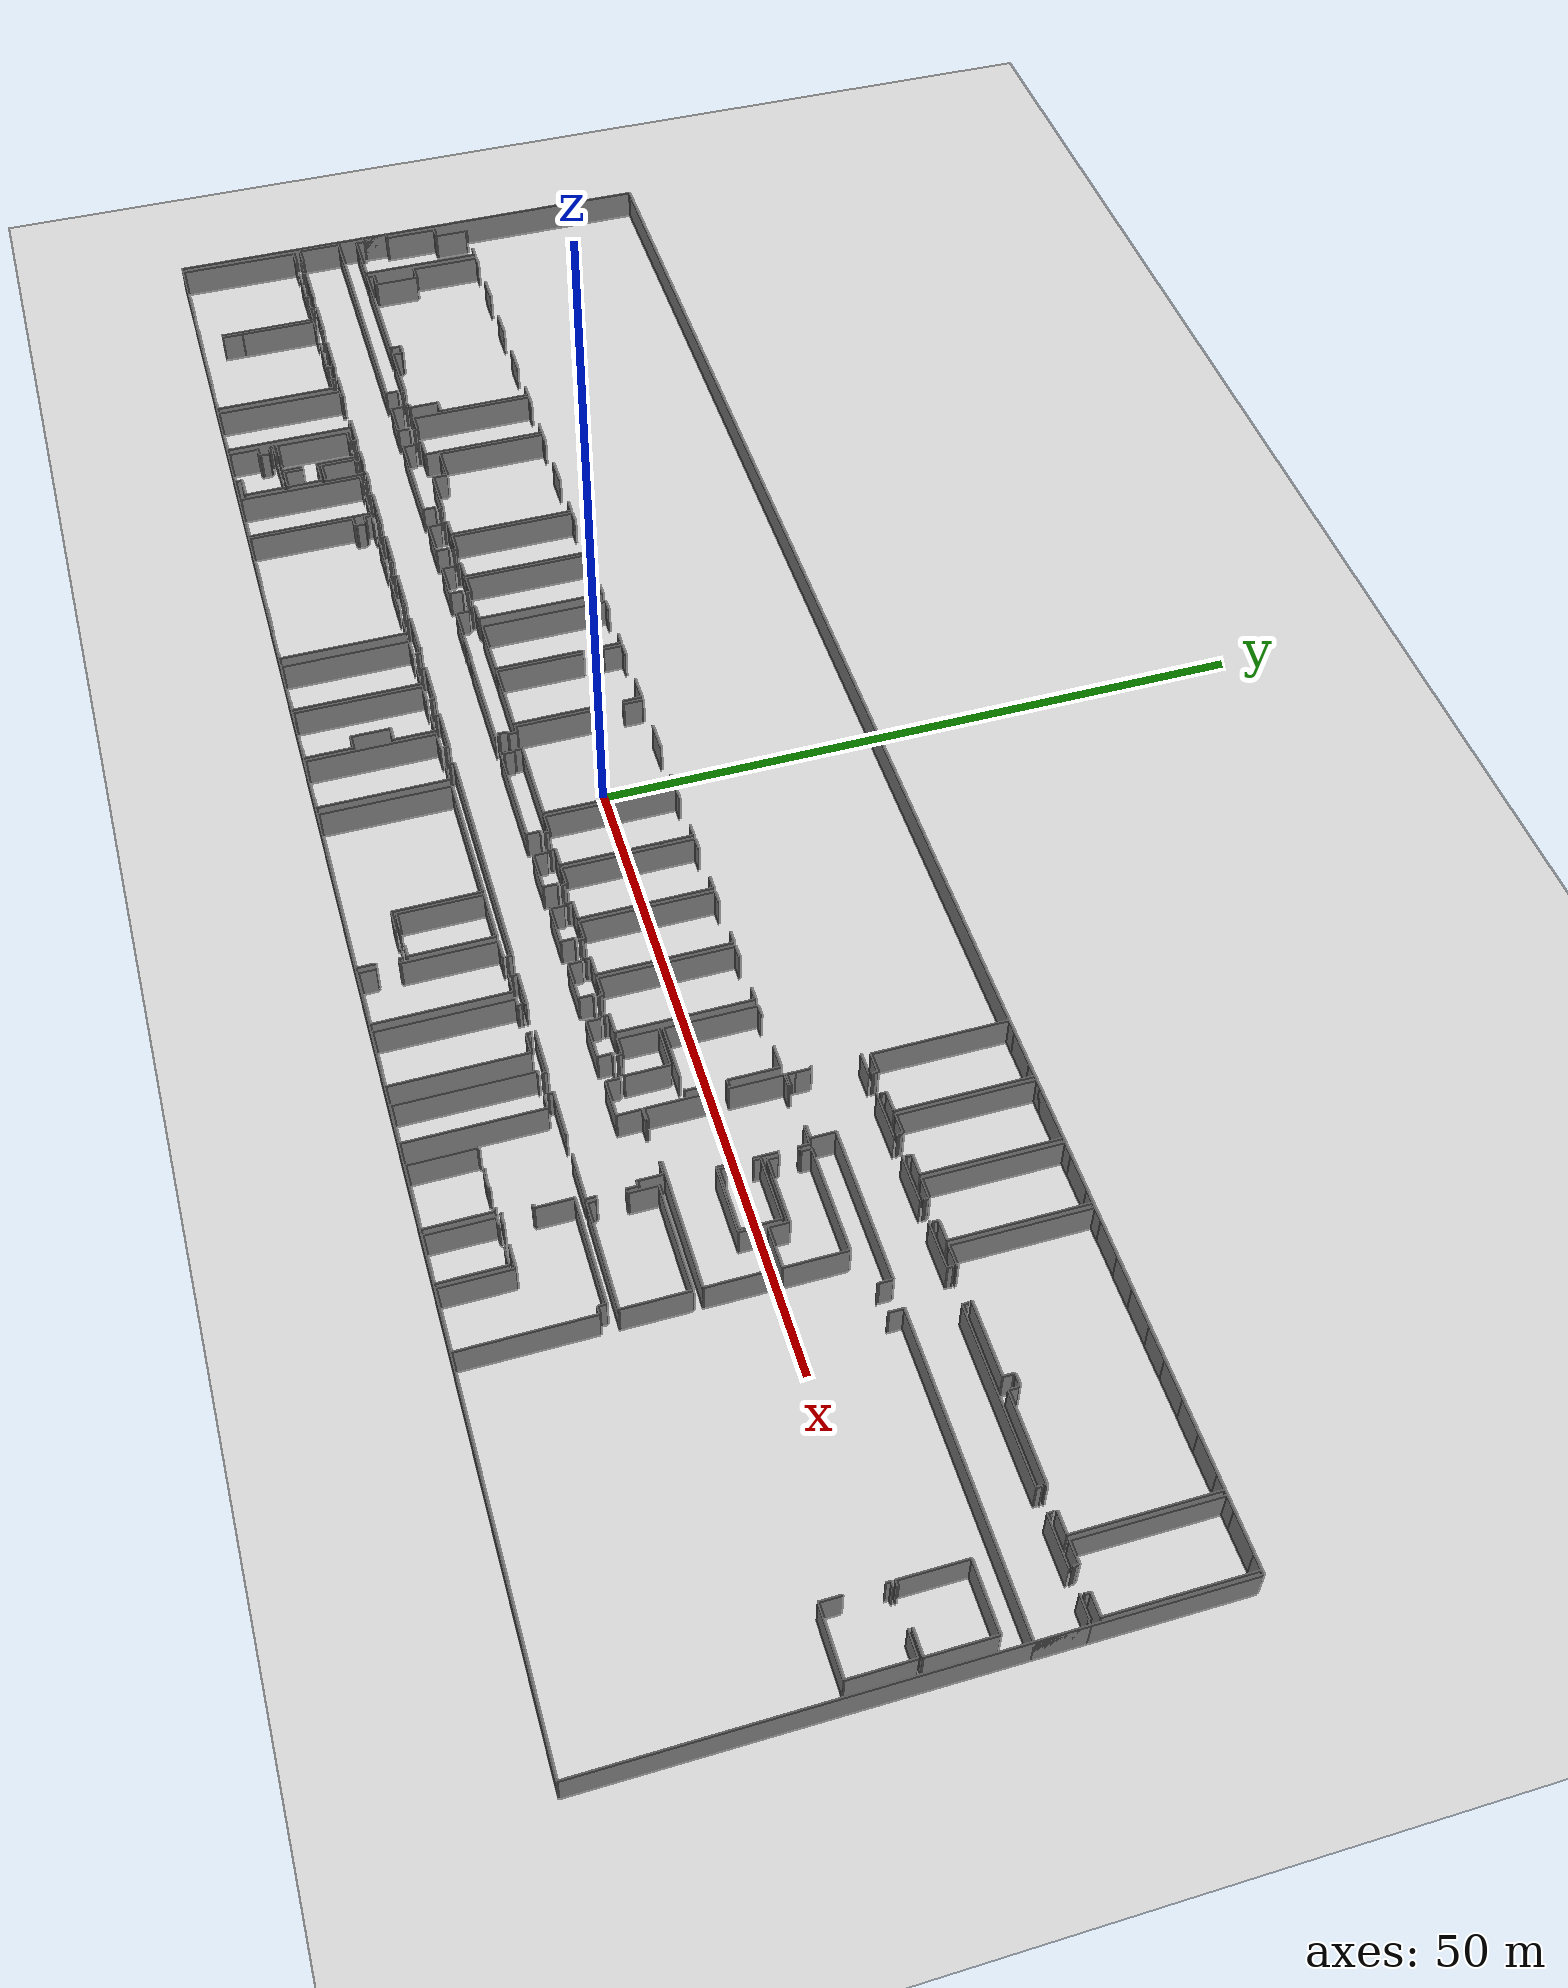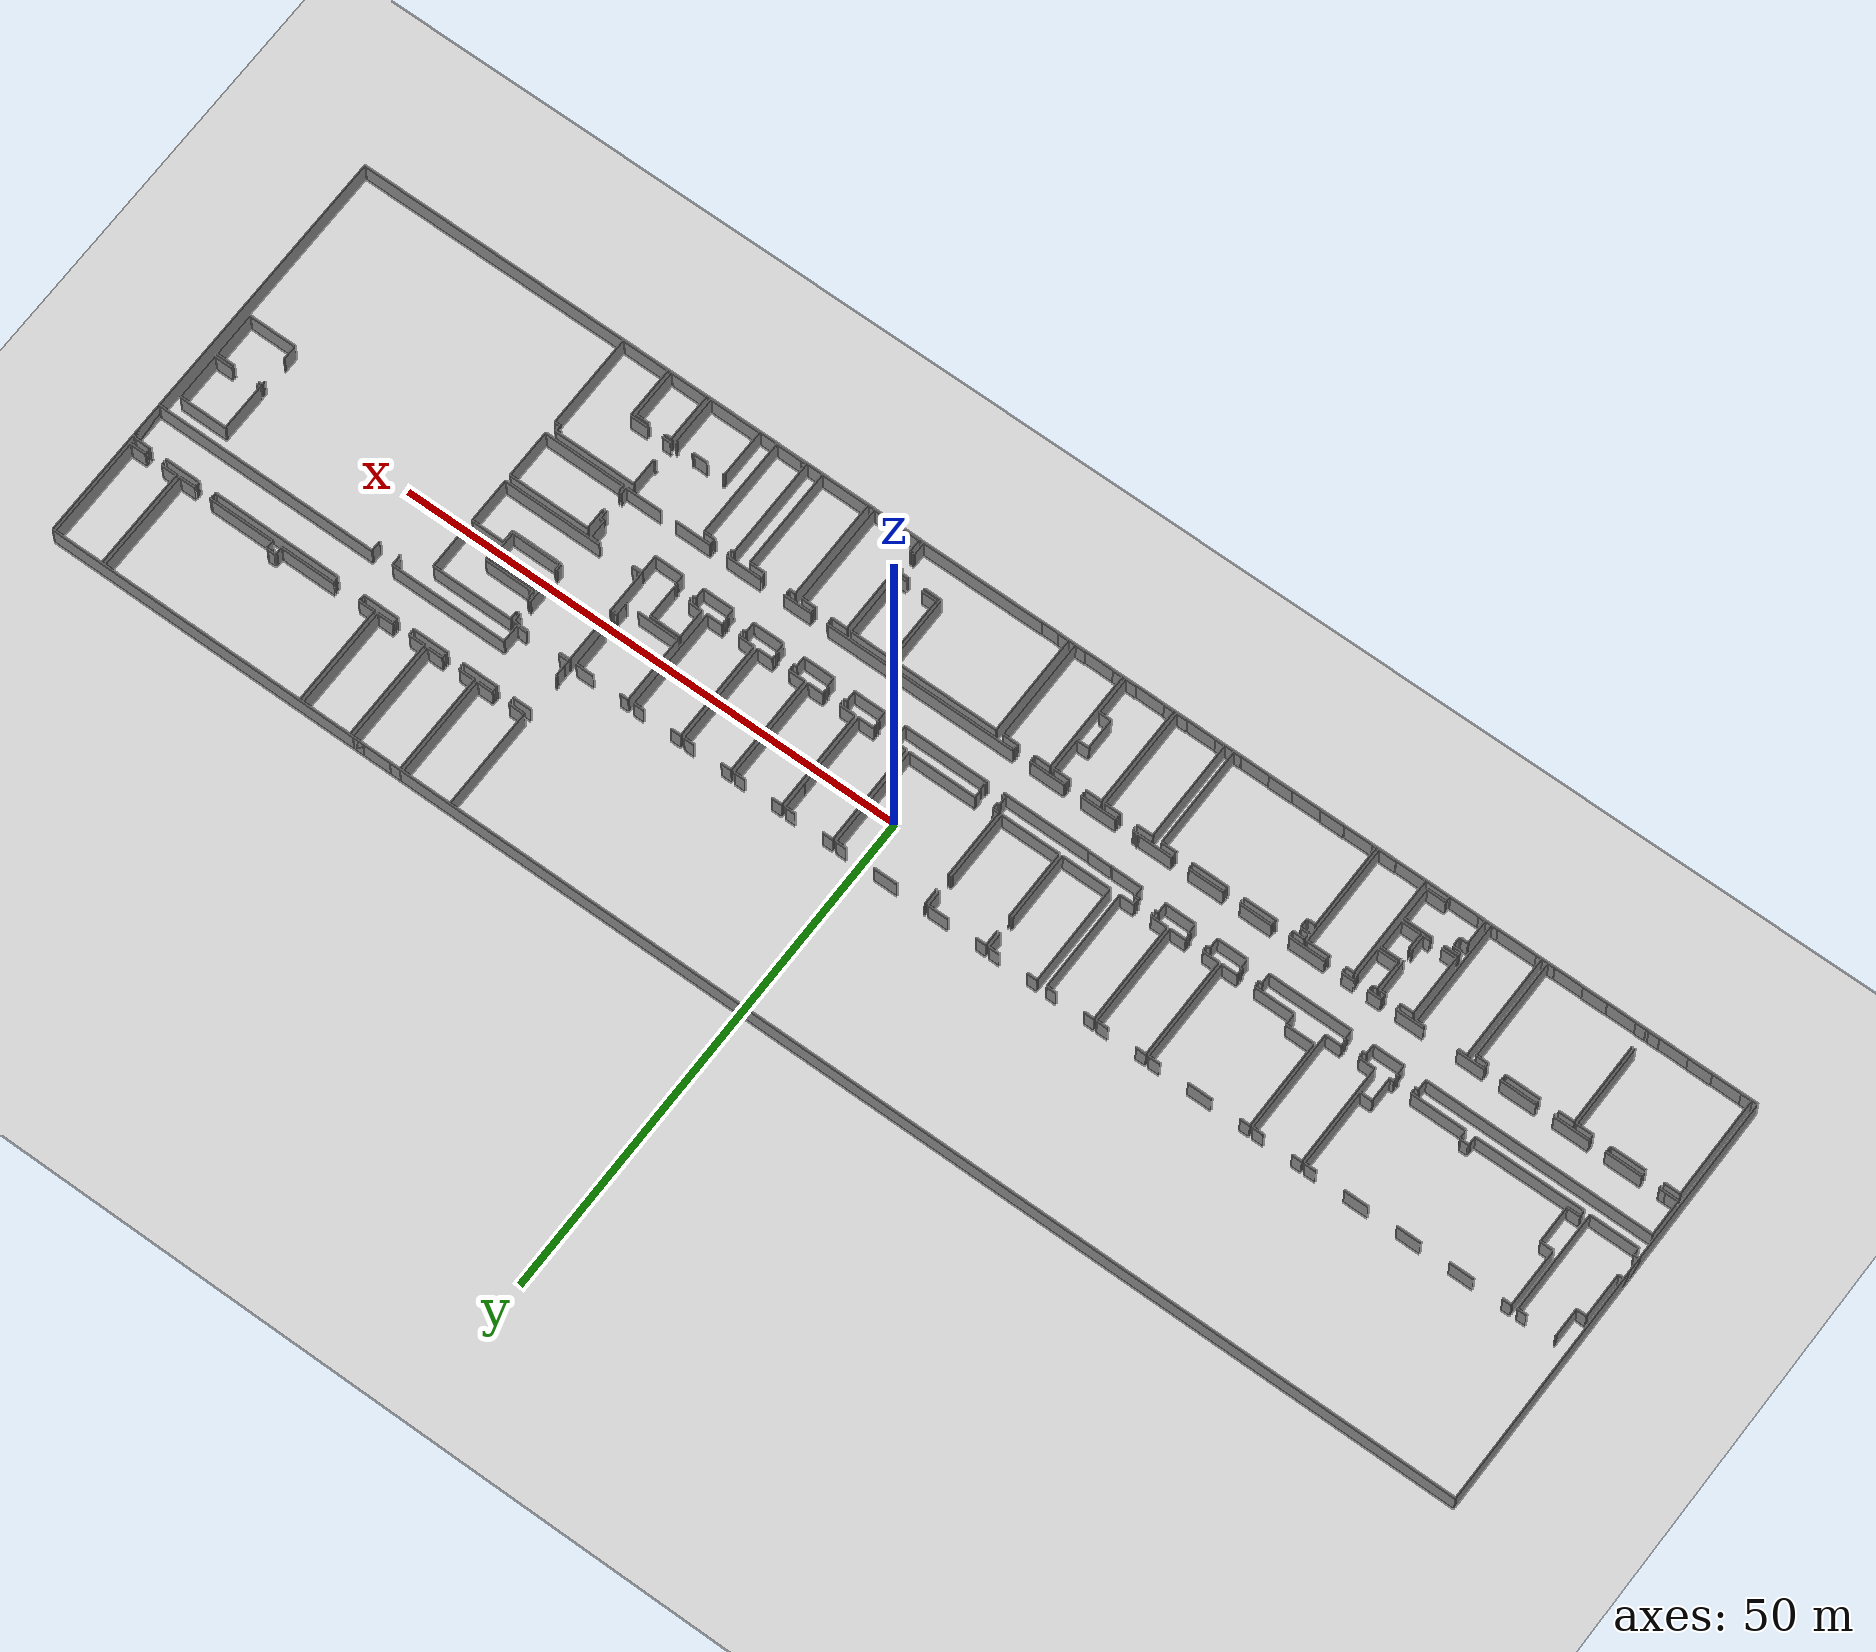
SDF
<sdf version="1.6">
  <world name="default">
    <light name="sun" type="directional">
      <cast_shadows>1</cast_shadows>
      <pose frame="">0 0 10 0 -0 0</pose>
      <diffuse>0.8 0.8 0.8 1</diffuse>
      <specular>0.1 0.1 0.1 1</specular>
      <attenuation>
        <range>1000</range>
        <constant>0.9</constant>
        <linear>0.01</linear>
        <quadratic>0.001</quadratic>
      </attenuation>
      <direction>-0.5 0.5 -1</direction>
    </light>
    <model name="ground_plane">
      <static>1</static>
      <link name="link">
        <collision name="collision">
          <geometry>
            <plane>
              <normal>0 0 1</normal>
              <size>100 100</size>
            </plane>
          </geometry>
          <surface>
            <friction>
              <ode>
                <mu>100</mu>
                <mu2>50</mu2>
              </ode>
              <torsional>
                <ode />
              </torsional>
            </friction>
            <contact>
              <ode />
            </contact>
            <bounce />
          </surface>
          <max_contacts>10</max_contacts>
        </collision>
        <visual name="visual">
          <cast_shadows>0</cast_shadows>
          <geometry>
            <plane>
              <normal>0 0 1</normal>
              <size>100 100</size>
            </plane>
          </geometry>
          <material>
            <script>
              <uri>file://media/materials/scripts/gazebo.material</uri>
              <name>Gazebo/Grey</name>
            </script>
          </material>
        </visual>
        <self_collide>0</self_collide>
        <kinematic>0</kinematic>
        <gravity>1</gravity>
      </link>
    </model>
    <gravity>0 0 -9.8</gravity>
    <magnetic_field>6e-06 2.3e-05 -4.2e-05</magnetic_field>
    <atmosphere type="adiabatic" />
    <physics default="0" name="default_physics" type="ode">
      <max_step_size>0.001</max_step_size>
      <real_time_factor>1</real_time_factor>
      <real_time_update_rate>1000</real_time_update_rate>
    </physics>
    <scene>
      <ambient>0.4 0.4 0.4 1</ambient>
      <background>0.7 0.7 0.7 1</background>
      <shadows>1</shadows>
    </scene>
    <spherical_coordinates>
      <surface_model>EARTH_WGS84</surface_model>
      <latitude_deg>0</latitude_deg>
      <longitude_deg>0</longitude_deg>
      <elevation>0</elevation>
      <heading_deg>0</heading_deg>
    </spherical_coordinates>
  <model name="50055638">
		<static>1</static>
		<link name="Wall_0">
			<collision name="Wall_0_Collision">
				<geometry>
					<box>
						<size>0.158999485253 0.1 2.5</size>
					</box>
				</geometry>
				<pose frame="">0.0794997426267 0 1.25 0 0 0</pose>
			</collision>
			<visual name="Wall_0_Visual">
				<pose frame="">0.0794997426267 0 1.25 0 0 0</pose>
				<geometry>
					<box>
						<size>0.158999485253 0.1 2.5</size>
					</box>
				</geometry>
				<material>
					<script>
						<uri>file://media/materials/scripts/gazebo.material</uri>
						<name>Gazebo/Grey</name>
					</script>
					<ambient>1 1 1 1</ambient>
				</material>
			</visual>
			<pose frame="">0.707426966364 -25.9577780743 0 0 0 3.14159265359</pose>
		</link>
		<link name="Wall_1">
			<collision name="Wall_1_Collision">
				<geometry>
					<box>
						<size>0.69026874853 0.1 2.5</size>
					</box>
				</geometry>
				<pose frame="">0.345134374265 0 1.25 0 0 0</pose>
			</collision>
			<visual name="Wall_1_Visual">
				<pose frame="">0.345134374265 0 1.25 0 0 0</pose>
				<geometry>
					<box>
						<size>0.69026874853 0.1 2.5</size>
					</box>
				</geometry>
				<material>
					<script>
						<uri>file://media/materials/scripts/gazebo.material</uri>
						<name>Gazebo/Grey</name>
					</script>
					<ambient>1 1 1 1</ambient>
				</material>
			</visual>
			<pose frame="">0.54842748111 -25.9577780743 0 0 0 1.57079632679</pose>
		</link>
		<link name="Wall_2">
			<collision name="Wall_2_Collision">
				<geometry>
					<box>
						<size>0.54842748111 0.1 2.5</size>
					</box>
				</geometry>
				<pose frame="">0.274213740555 0 1.25 0 0 0</pose>
			</collision>
			<visual name="Wall_2_Visual">
				<pose frame="">0.274213740555 0 1.25 0 0 0</pose>
				<geometry>
					<box>
						<size>0.54842748111 0.1 2.5</size>
					</box>
				</geometry>
				<material>
					<script>
						<uri>file://media/materials/scripts/gazebo.material</uri>
						<name>Gazebo/Grey</name>
					</script>
					<ambient>1 1 1 1</ambient>
				</material>
			</visual>
			<pose frame="">0.54842748111 -25.2675093258 0 0 0 3.14159265359</pose>
		</link>
		<link name="Wall_3">
			<collision name="Wall_3_Collision">
				<geometry>
					<box>
						<size>2.14287076049 0.1 2.5</size>
					</box>
				</geometry>
				<pose frame="">1.07143538025 0 1.25 0 0 0</pose>
			</collision>
			<visual name="Wall_3_Visual">
				<pose frame="">1.07143538025 0 1.25 0 0 0</pose>
				<geometry>
					<box>
						<size>2.14287076049 0.1 2.5</size>
					</box>
				</geometry>
				<material>
					<script>
						<uri>file://media/materials/scripts/gazebo.material</uri>
						<name>Gazebo/Grey</name>
					</script>
					<ambient>1 1 1 1</ambient>
				</material>
			</visual>
			<pose frame="">0.0 -25.2675093258 0 0 0 1.57079632679</pose>
		</link>
		<link name="Wall_4">
			<collision name="Wall_4_Collision">
				<geometry>
					<box>
						<size>0.550715243488 0.1 2.5</size>
					</box>
				</geometry>
				<pose frame="">0.275357621744 0 1.25 0 0 0</pose>
			</collision>
			<visual name="Wall_4_Visual">
				<pose frame="">0.275357621744 0 1.25 0 0 0</pose>
				<geometry>
					<box>
						<size>0.550715243488 0.1 2.5</size>
					</box>
				</geometry>
				<material>
					<script>
						<uri>file://media/materials/scripts/gazebo.material</uri>
						<name>Gazebo/Grey</name>
					</script>
					<ambient>1 1 1 1</ambient>
				</material>
			</visual>
			<pose frame="">0.0 -23.1246385653 0 0 0 0.0</pose>
		</link>
		<link name="Wall_5">
			<collision name="Wall_5_Collision">
				<geometry>
					<box>
						<size>4.38017526802 0.1 2.5</size>
					</box>
				</geometry>
				<pose frame="">2.19008763401 0 1.25 0 0 0</pose>
			</collision>
			<visual name="Wall_5_Visual">
				<pose frame="">2.19008763401 0 1.25 0 0 0</pose>
				<geometry>
					<box>
						<size>4.38017526802 0.1 2.5</size>
					</box>
				</geometry>
				<material>
					<script>
						<uri>file://media/materials/scripts/gazebo.material</uri>
						<name>Gazebo/Grey</name>
					</script>
					<ambient>1 1 1 1</ambient>
				</material>
			</visual>
			<pose frame="">0.550715243488 -23.1246385653 0 0 0 1.57079632679</pose>
		</link>
		<link name="Wall_6">
			<collision name="Wall_6_Collision">
				<geometry>
					<box>
						<size>0.976620339479 0.1 2.5</size>
					</box>
				</geometry>
				<pose frame="">0.488310169739 0 1.25 0 0 0</pose>
			</collision>
			<visual name="Wall_6_Visual">
				<pose frame="">0.488310169739 0 1.25 0 0 0</pose>
				<geometry>
					<box>
						<size>0.976620339479 0.1 2.5</size>
					</box>
				</geometry>
				<material>
					<script>
						<uri>file://media/materials/scripts/gazebo.material</uri>
						<name>Gazebo/Grey</name>
					</script>
					<ambient>1 1 1 1</ambient>
				</material>
			</visual>
			<pose frame="">0.550715243488 -18.7444632973 0 0 0 0.0</pose>
		</link>
		<link name="Wall_7">
			<collision name="Wall_7_Collision">
				<geometry>
					<box>
						<size>2.8045424793 0.1 2.5</size>
					</box>
				</geometry>
				<pose frame="">1.40227123965 0 1.25 0 0 0</pose>
			</collision>
			<visual name="Wall_7_Visual">
				<pose frame="">1.40227123965 0 1.25 0 0 0</pose>
				<geometry>
					<box>
						<size>2.8045424793 0.1 2.5</size>
					</box>
				</geometry>
				<material>
					<script>
						<uri>file://media/materials/scripts/gazebo.material</uri>
						<name>Gazebo/Grey</name>
					</script>
					<ambient>1 1 1 1</ambient>
				</material>
			</visual>
			<pose frame="">1.52733558297 -18.7444632973 0 0 0 1.57079632679</pose>
		</link>
		<link name="Wall_8">
			<collision name="Wall_8_Collision">
				<geometry>
					<box>
						<size>0.0847743058865 0.1 2.5</size>
					</box>
				</geometry>
				<pose frame="">0.0423871529433 0 1.25 0 0 0</pose>
			</collision>
			<visual name="Wall_8_Visual">
				<pose frame="">0.0423871529433 0 1.25 0 0 0</pose>
				<geometry>
					<box>
						<size>0.0847743058865 0.1 2.5</size>
					</box>
				</geometry>
				<material>
					<script>
						<uri>file://media/materials/scripts/gazebo.material</uri>
						<name>Gazebo/Grey</name>
					</script>
					<ambient>1 1 1 1</ambient>
				</material>
			</visual>
			<pose frame="">1.52733558297 -15.939920818 0 0 0 0.0</pose>
		</link>
		<link name="Wall_9">
			<collision name="Wall_9_Collision">
				<geometry>
					<box>
						<size>0.0392732541513 0.1 2.5</size>
					</box>
				</geometry>
				<pose frame="">0.0196366270757 0 1.25 0 0 0</pose>
			</collision>
			<visual name="Wall_9_Visual">
				<pose frame="">0.0196366270757 0 1.25 0 0 0</pose>
				<geometry>
					<box>
						<size>0.0392732541513 0.1 2.5</size>
					</box>
				</geometry>
				<material>
					<script>
						<uri>file://media/materials/scripts/gazebo.material</uri>
						<name>Gazebo/Grey</name>
					</script>
					<ambient>1 1 1 1</ambient>
				</material>
			</visual>
			<pose frame="">4.36670288957 -15.939920818 0 0 0 0.0</pose>
		</link>
		<link name="Wall_10">
			<collision name="Wall_10_Collision">
				<geometry>
					<box>
						<size>0.026436365254 0.1 2.5</size>
					</box>
				</geometry>
				<pose frame="">0.013218182627 0 1.25 0 0 0</pose>
			</collision>
			<visual name="Wall_10_Visual">
				<pose frame="">0.013218182627 0 1.25 0 0 0</pose>
				<geometry>
					<box>
						<size>0.026436365254 0.1 2.5</size>
					</box>
				</geometry>
				<material>
					<script>
						<uri>file://media/materials/scripts/gazebo.material</uri>
						<name>Gazebo/Grey</name>
					</script>
					<ambient>1 1 1 1</ambient>
				</material>
			</visual>
			<pose frame="">4.40597614372 -15.939920818 0 0 0 -1.57079632679</pose>
		</link>
		<link name="Wall_11">
			<collision name="Wall_11_Collision">
				<geometry>
					<box>
						<size>0.88409306109 0.1 2.5</size>
					</box>
				</geometry>
				<pose frame="">0.442046530545 0 1.25 0 0 0</pose>
			</collision>
			<visual name="Wall_11_Visual">
				<pose frame="">0.442046530545 0 1.25 0 0 0</pose>
				<geometry>
					<box>
						<size>0.88409306109 0.1 2.5</size>
					</box>
				</geometry>
				<material>
					<script>
						<uri>file://media/materials/scripts/gazebo.material</uri>
						<name>Gazebo/Grey</name>
					</script>
					<ambient>1 1 1 1</ambient>
				</material>
			</visual>
			<pose frame="">4.40597614372 -15.9663571833 0 0 0 0.0</pose>
		</link>
		<link name="Wall_12">
			<collision name="Wall_12_Collision">
				<geometry>
					<box>
						<size>9.99091249944 0.1 2.5</size>
					</box>
				</geometry>
				<pose frame="">4.99545624972 0 1.25 0 0 0</pose>
			</collision>
			<visual name="Wall_12_Visual">
				<pose frame="">4.99545624972 0 1.25 0 0 0</pose>
				<geometry>
					<box>
						<size>9.99091249944 0.1 2.5</size>
					</box>
				</geometry>
				<material>
					<script>
						<uri>file://media/materials/scripts/gazebo.material</uri>
						<name>Gazebo/Grey</name>
					</script>
					<ambient>1 1 1 1</ambient>
				</material>
			</visual>
			<pose frame="">5.29006920481 -15.9663571833 0 0 0 -1.57079632679</pose>
		</link>
		<link name="Wall_13">
			<collision name="Wall_13_Collision">
				<geometry>
					<box>
						<size>4.58264226665 0.1 2.5</size>
					</box>
				</geometry>
				<pose frame="">2.29132113332 0 1.25 0 0 0</pose>
			</collision>
			<visual name="Wall_13_Visual">
				<pose frame="">2.29132113332 0 1.25 0 0 0</pose>
				<geometry>
					<box>
						<size>4.58264226665 0.1 2.5</size>
					</box>
				</geometry>
				<material>
					<script>
						<uri>file://media/materials/scripts/gazebo.material</uri>
						<name>Gazebo/Grey</name>
					</script>
					<ambient>1 1 1 1</ambient>
				</material>
			</visual>
			<pose frame="">5.29006920481 -25.9572696827 0 0 0 -3.14148171505</pose>
		</link>
		<link name="Wall_14">
			<collision name="Wall_14_Collision">
				<geometry>
					<box>
						<size>0.604350561455 0.1 2.5</size>
					</box>
				</geometry>
				<pose frame="">0.302175280728 0 1.25 0 0 0</pose>
			</collision>
			<visual name="Wall_14_Visual">
				<pose frame="">0.302175280728 0 1.25 0 0 0</pose>
				<geometry>
					<box>
						<size>0.604350561455 0.1 2.5</size>
					</box>
				</geometry>
				<material>
					<script>
						<uri>file://media/materials/scripts/gazebo.material</uri>
						<name>Gazebo/Grey</name>
					</script>
					<ambient>1 1 1 1</ambient>
				</material>
			</visual>
			<pose frame="">5.87510088397 -25.9886628664 0 0 0 1.57079632679</pose>
		</link>
		<link name="Wall_15">
			<collision name="Wall_15_Collision">
				<geometry>
					<box>
						<size>1.28038434408 0.1 2.5</size>
					</box>
				</geometry>
				<pose frame="">0.64019217204 0 1.25 0 0 0</pose>
			</collision>
			<visual name="Wall_15_Visual">
				<pose frame="">0.64019217204 0 1.25 0 0 0</pose>
				<geometry>
					<box>
						<size>1.28038434408 0.1 2.5</size>
					</box>
				</geometry>
				<material>
					<script>
						<uri>file://media/materials/scripts/gazebo.material</uri>
						<name>Gazebo/Grey</name>
					</script>
					<ambient>1 1 1 1</ambient>
				</material>
			</visual>
			<pose frame="">5.87510088397 -25.384312305 0 0 0 0.0</pose>
		</link>
		<link name="Wall_16">
			<collision name="Wall_16_Collision">
				<geometry>
					<box>
						<size>3.64859969878 0.1 2.5</size>
					</box>
				</geometry>
				<pose frame="">1.82429984939 0 1.25 0 0 0</pose>
			</collision>
			<visual name="Wall_16_Visual">
				<pose frame="">1.82429984939 0 1.25 0 0 0</pose>
				<geometry>
					<box>
						<size>3.64859969878 0.1 2.5</size>
					</box>
				</geometry>
				<material>
					<script>
						<uri>file://media/materials/scripts/gazebo.material</uri>
						<name>Gazebo/Grey</name>
					</script>
					<ambient>1 1 1 1</ambient>
				</material>
			</visual>
			<pose frame="">7.15548522805 -25.384312305 0 0 0 1.57079632679</pose>
		</link>
		<link name="Wall_17">
			<collision name="Wall_17_Collision">
				<geometry>
					<box>
						<size>1.27479203604 0.1 2.5</size>
					</box>
				</geometry>
				<pose frame="">0.637396018022 0 1.25 0 0 0</pose>
			</collision>
			<visual name="Wall_17_Visual">
				<pose frame="">0.637396018022 0 1.25 0 0 0</pose>
				<geometry>
					<box>
						<size>1.27479203604 0.1 2.5</size>
					</box>
				</geometry>
				<material>
					<script>
						<uri>file://media/materials/scripts/gazebo.material</uri>
						<name>Gazebo/Grey</name>
					</script>
					<ambient>1 1 1 1</ambient>
				</material>
			</visual>
			<pose frame="">7.15548522805 -21.7357126062 0 0 0 3.14159265359</pose>
		</link>
		<link name="Wall_18">
			<collision name="Wall_18_Collision">
				<geometry>
					<box>
						<size>5.78054003902 0.1 2.5</size>
					</box>
				</geometry>
				<pose frame="">2.89027001951 0 1.25 0 0 0</pose>
			</collision>
			<visual name="Wall_18_Visual">
				<pose frame="">2.89027001951 0 1.25 0 0 0</pose>
				<geometry>
					<box>
						<size>5.78054003902 0.1 2.5</size>
					</box>
				</geometry>
				<material>
					<script>
						<uri>file://media/materials/scripts/gazebo.material</uri>
						<name>Gazebo/Grey</name>
					</script>
					<ambient>1 1 1 1</ambient>
				</material>
			</visual>
			<pose frame="">5.880693192 -21.7357126062 0 0 0 1.57079632679</pose>
		</link>
		<link name="Wall_19">
			<collision name="Wall_19_Collision">
				<geometry>
					<box>
						<size>0.87367103248 0.1 2.5</size>
					</box>
				</geometry>
				<pose frame="">0.43683551624 0 1.25 0 0 0</pose>
			</collision>
			<visual name="Wall_19_Visual">
				<pose frame="">0.43683551624 0 1.25 0 0 0</pose>
				<geometry>
					<box>
						<size>0.87367103248 0.1 2.5</size>
					</box>
				</geometry>
				<material>
					<script>
						<uri>file://media/materials/scripts/gazebo.material</uri>
						<name>Gazebo/Grey</name>
					</script>
					<ambient>1 1 1 1</ambient>
				</material>
			</visual>
			<pose frame="">5.880693192 -15.9551725672 0 0 0 0.0</pose>
		</link>
		<link name="Wall_20">
			<collision name="Wall_20_Collision">
				<geometry>
					<box>
						<size>2.38486518089 0.1 2.5</size>
					</box>
				</geometry>
				<pose frame="">1.19243259045 0 1.25 0 0 0</pose>
			</collision>
			<visual name="Wall_20_Visual">
				<pose frame="">1.19243259045 0 1.25 0 0 0</pose>
				<geometry>
					<box>
						<size>2.38486518089 0.1 2.5</size>
					</box>
				</geometry>
				<material>
					<script>
						<uri>file://media/materials/scripts/gazebo.material</uri>
						<name>Gazebo/Grey</name>
					</script>
					<ambient>1 1 1 1</ambient>
				</material>
			</visual>
			<pose frame="">9.53463100299 -15.9551725672 0 0 0 0.0</pose>
		</link>
		<link name="Wall_21">
			<collision name="Wall_21_Collision">
				<geometry>
					<box>
						<size>2.37368056482 0.1 2.5</size>
					</box>
				</geometry>
				<pose frame="">1.18684028241 0 1.25 0 0 0</pose>
			</collision>
			<visual name="Wall_21_Visual">
				<pose frame="">1.18684028241 0 1.25 0 0 0</pose>
				<geometry>
					<box>
						<size>2.37368056482 0.1 2.5</size>
					</box>
				</geometry>
				<material>
					<script>
						<uri>file://media/materials/scripts/gazebo.material</uri>
						<name>Gazebo/Grey</name>
					</script>
					<ambient>1 1 1 1</ambient>
				</material>
			</visual>
			<pose frame="">14.7108204806 -15.9551725672 0 0 0 0.0</pose>
		</link>
		<link name="Wall_22">
			<collision name="Wall_22_Collision">
				<geometry>
					<box>
						<size>2.38473808298 0.1 2.5</size>
					</box>
				</geometry>
				<pose frame="">1.19236904149 0 1.25 0 0 0</pose>
			</collision>
			<visual name="Wall_22_Visual">
				<pose frame="">1.19236904149 0 1.25 0 0 0</pose>
				<geometry>
					<box>
						<size>2.38473808298 0.1 2.5</size>
					</box>
				</geometry>
				<material>
					<script>
						<uri>file://media/materials/scripts/gazebo.material</uri>
						<name>Gazebo/Grey</name>
					</script>
					<ambient>1 1 1 1</ambient>
				</material>
			</visual>
			<pose frame="">19.8429069834 -15.9551725672 0 0 0 0.0</pose>
		</link>
		<link name="Wall_23">
			<collision name="Wall_23_Collision">
				<geometry>
					<box>
						<size>1.12634167731 0.1 2.5</size>
					</box>
				</geometry>
				<pose frame="">0.563170838656 0 1.25 0 0 0</pose>
			</collision>
			<visual name="Wall_23_Visual">
				<pose frame="">0.563170838656 0 1.25 0 0 0</pose>
				<geometry>
					<box>
						<size>1.12634167731 0.1 2.5</size>
					</box>
				</geometry>
				<material>
					<script>
						<uri>file://media/materials/scripts/gazebo.material</uri>
						<name>Gazebo/Grey</name>
					</script>
					<ambient>1 1 1 1</ambient>
				</material>
			</visual>
			<pose frame="">25.0025737327 -15.9551725672 0 0 0 0.0</pose>
		</link>
		<link name="Wall_24">
			<collision name="Wall_24_Collision">
				<geometry>
					<box>
						<size>7.62129906774 0.1 2.5</size>
					</box>
				</geometry>
				<pose frame="">3.81064953387 0 1.25 0 0 0</pose>
			</collision>
			<visual name="Wall_24_Visual">
				<pose frame="">3.81064953387 0 1.25 0 0 0</pose>
				<geometry>
					<box>
						<size>7.62129906774 0.1 2.5</size>
					</box>
				</geometry>
				<material>
					<script>
						<uri>file://media/materials/scripts/gazebo.material</uri>
						<name>Gazebo/Grey</name>
					</script>
					<ambient>1 1 1 1</ambient>
				</material>
			</visual>
			<pose frame="">26.12891541 -15.9551725672 0 0 0 -1.57079632679</pose>
		</link>
		<link name="Wall_25">
			<collision name="Wall_25_Collision">
				<geometry>
					<box>
						<size>1.18734867405 0.1 2.5</size>
					</box>
				</geometry>
				<pose frame="">0.593674337026 0 1.25 0 0 0</pose>
			</collision>
			<visual name="Wall_25_Visual">
				<pose frame="">0.593674337026 0 1.25 0 0 0</pose>
				<geometry>
					<box>
						<size>1.18734867405 0.1 2.5</size>
					</box>
				</geometry>
				<material>
					<script>
						<uri>file://media/materials/scripts/gazebo.material</uri>
						<name>Gazebo/Grey</name>
					</script>
					<ambient>1 1 1 1</ambient>
				</material>
			</visual>
			<pose frame="">26.12891541 -23.5764716349 0 0 0 3.14159265359</pose>
		</link>
		<link name="Wall_26">
			<collision name="Wall_26_Collision">
				<geometry>
					<box>
						<size>2.39058458684 0.1 2.5</size>
					</box>
				</geometry>
				<pose frame="">1.19529229342 0 1.25 0 0 0</pose>
			</collision>
			<visual name="Wall_26_Visual">
				<pose frame="">1.19529229342 0 1.25 0 0 0</pose>
				<geometry>
					<box>
						<size>2.39058458684 0.1 2.5</size>
					</box>
				</geometry>
				<material>
					<script>
						<uri>file://media/materials/scripts/gazebo.material</uri>
						<name>Gazebo/Grey</name>
					</script>
					<ambient>1 1 1 1</ambient>
				</material>
			</visual>
			<pose frame="">24.9415667359 -23.5764716349 0 0 0 -1.57079632679</pose>
		</link>
		<link name="Wall_27">
			<collision name="Wall_27_Collision">
				<geometry>
					<box>
						<size>0.404552647132 0.1 2.5</size>
					</box>
				</geometry>
				<pose frame="">0.202276323566 0 1.25 0 0 0</pose>
			</collision>
			<visual name="Wall_27_Visual">
				<pose frame="">0.202276323566 0 1.25 0 0 0</pose>
				<geometry>
					<box>
						<size>0.404552647132 0.1 2.5</size>
					</box>
				</geometry>
				<material>
					<script>
						<uri>file://media/materials/scripts/gazebo.material</uri>
						<name>Gazebo/Grey</name>
					</script>
					<ambient>1 1 1 1</ambient>
				</material>
			</visual>
			<pose frame="">24.9415667359 -25.9670562218 0 0 0 3.14159265359</pose>
		</link>
		<link name="Wall_28">
			<collision name="Wall_28_Collision">
				<geometry>
					<box>
						<size>0.298425892386 0.1 2.5</size>
					</box>
				</geometry>
				<pose frame="">0.149212946193 0 1.25 0 0 0</pose>
			</collision>
			<visual name="Wall_28_Visual">
				<pose frame="">0.149212946193 0 1.25 0 0 0</pose>
				<geometry>
					<box>
						<size>0.298425892386 0.1 2.5</size>
					</box>
				</geometry>
				<material>
					<script>
						<uri>file://media/materials/scripts/gazebo.material</uri>
						<name>Gazebo/Grey</name>
					</script>
					<ambient>1 1 1 1</ambient>
				</material>
			</visual>
			<pose frame="">24.5370140888 -25.9670562218 0 0 0 -1.57079632679</pose>
		</link>
		<link name="Wall_29">
			<collision name="Wall_29_Collision">
				<geometry>
					<box>
						<size>0.0911292013803 0.1 2.5</size>
					</box>
				</geometry>
				<pose frame="">0.0455646006901 0 1.25 0 0 0</pose>
			</collision>
			<visual name="Wall_29_Visual">
				<pose frame="">0.0455646006901 0 1.25 0 0 0</pose>
				<geometry>
					<box>
						<size>0.0911292013803 0.1 2.5</size>
					</box>
				</geometry>
				<material>
					<script>
						<uri>file://media/materials/scripts/gazebo.material</uri>
						<name>Gazebo/Grey</name>
					</script>
					<ambient>1 1 1 1</ambient>
				</material>
			</visual>
			<pose frame="">24.5370140888 -26.2654821141 0 0 0 3.14159265359</pose>
		</link>
		<link name="Wall_30">
			<collision name="Wall_30_Collision">
				<geometry>
					<box>
						<size>0.104728677737 0.1 2.5</size>
					</box>
				</geometry>
				<pose frame="">0.0523643388684 0 1.25 0 0 0</pose>
			</collision>
			<visual name="Wall_30_Visual">
				<pose frame="">0.0523643388684 0 1.25 0 0 0</pose>
				<geometry>
					<box>
						<size>0.104728677737 0.1 2.5</size>
					</box>
				</geometry>
				<material>
					<script>
						<uri>file://media/materials/scripts/gazebo.material</uri>
						<name>Gazebo/Grey</name>
					</script>
					<ambient>1 1 1 1</ambient>
				</material>
			</visual>
			<pose frame="">22.9052040239 -26.2654821141 0 0 0 3.14159265359</pose>
		</link>
		<link name="Wall_31">
			<collision name="Wall_31_Collision">
				<geometry>
					<box>
						<size>0.300459458944 0.1 2.5</size>
					</box>
				</geometry>
				<pose frame="">0.150229729472 0 1.25 0 0 0</pose>
			</collision>
			<visual name="Wall_31_Visual">
				<pose frame="">0.150229729472 0 1.25 0 0 0</pose>
				<geometry>
					<box>
						<size>0.300459458944 0.1 2.5</size>
					</box>
				</geometry>
				<material>
					<script>
						<uri>file://media/materials/scripts/gazebo.material</uri>
						<name>Gazebo/Grey</name>
					</script>
					<ambient>1 1 1 1</ambient>
				</material>
			</visual>
			<pose frame="">22.8004753462 -26.2654821141 0 0 0 1.57079632679</pose>
		</link>
		<link name="Wall_32">
			<collision name="Wall_32_Collision">
				<geometry>
					<box>
						<size>5.3477716559 0.1 2.5</size>
					</box>
				</geometry>
				<pose frame="">2.67388582795 0 1.25 0 0 0</pose>
			</collision>
			<visual name="Wall_32_Visual">
				<pose frame="">2.67388582795 0 1.25 0 0 0</pose>
				<geometry>
					<box>
						<size>5.3477716559 0.1 2.5</size>
					</box>
				</geometry>
				<material>
					<script>
						<uri>file://media/materials/scripts/gazebo.material</uri>
						<name>Gazebo/Grey</name>
					</script>
					<ambient>1 1 1 1</ambient>
				</material>
			</visual>
			<pose frame="">22.8004753462 -25.9650226552 0 0 0 3.14159265359</pose>
		</link>
		<link name="Wall_33">
			<collision name="Wall_33_Collision">
				<geometry>
					<box>
						<size>0.755851270026 0.1 2.5</size>
					</box>
				</geometry>
				<pose frame="">0.377925635013 0 1.25 0 0 0</pose>
			</collision>
			<visual name="Wall_33_Visual">
				<pose frame="">0.377925635013 0 1.25 0 0 0</pose>
				<geometry>
					<box>
						<size>0.755851270026 0.1 2.5</size>
					</box>
				</geometry>
				<material>
					<script>
						<uri>file://media/materials/scripts/gazebo.material</uri>
						<name>Gazebo/Grey</name>
					</script>
					<ambient>1 1 1 1</ambient>
				</material>
			</visual>
			<pose frame="">17.4527036903 -25.9650226552 0 0 0 1.57079632679</pose>
		</link>
		<link name="Wall_34">
			<collision name="Wall_34_Collision">
				<geometry>
					<box>
						<size>0.179145349332 0.1 2.5</size>
					</box>
				</geometry>
				<pose frame="">0.0895726746661 0 1.25 0 0 0</pose>
			</collision>
			<visual name="Wall_34_Visual">
				<pose frame="">0.0895726746661 0 1.25 0 0 0</pose>
				<geometry>
					<box>
						<size>0.179145349332 0.1 2.5</size>
					</box>
				</geometry>
				<material>
					<script>
						<uri>file://media/materials/scripts/gazebo.material</uri>
						<name>Gazebo/Grey</name>
					</script>
					<ambient>1 1 1 1</ambient>
				</material>
			</visual>
			<pose frame="">17.4527036903 -25.2091713852 0 0 0 2.3747573352</pose>
		</link>
		<link name="Wall_35">
			<collision name="Wall_35_Collision">
				<geometry>
					<box>
						<size>0.712002491119 0.1 2.5</size>
					</box>
				</geometry>
				<pose frame="">0.35600124556 0 1.25 0 0 0</pose>
			</collision>
			<visual name="Wall_35_Visual">
				<pose frame="">0.35600124556 0 1.25 0 0 0</pose>
				<geometry>
					<box>
						<size>0.712002491119 0.1 2.5</size>
					</box>
				</geometry>
				<material>
					<script>
						<uri>file://media/materials/scripts/gazebo.material</uri>
						<name>Gazebo/Grey</name>
					</script>
					<ambient>1 1 1 1</ambient>
				</material>
			</visual>
			<pose frame="">17.3236993118 -25.0848696293 0 0 0 3.14159265359</pose>
		</link>
		<link name="Wall_36">
			<collision name="Wall_36_Collision">
				<geometry>
					<box>
						<size>0.152407830479 0.1 2.5</size>
					</box>
				</geometry>
				<pose frame="">0.0762039152394 0 1.25 0 0 0</pose>
			</collision>
			<visual name="Wall_36_Visual">
				<pose frame="">0.0762039152394 0 1.25 0 0 0</pose>
				<geometry>
					<box>
						<size>0.152407830479 0.1 2.5</size>
					</box>
				</geometry>
				<material>
					<script>
						<uri>file://media/materials/scripts/gazebo.material</uri>
						<name>Gazebo/Grey</name>
					</script>
					<ambient>1 1 1 1</ambient>
				</material>
			</visual>
			<pose frame="">16.6116968206 -25.0848696293 0 0 0 -2.28892027805</pose>
		</link>
		<link name="Wall_37">
			<collision name="Wall_37_Collision">
				<geometry>
					<box>
						<size>0.75191123482 0.1 2.5</size>
					</box>
				</geometry>
				<pose frame="">0.37595561741 0 1.25 0 0 0</pose>
			</collision>
			<visual name="Wall_37_Visual">
				<pose frame="">0.37595561741 0 1.25 0 0 0</pose>
				<geometry>
					<box>
						<size>0.75191123482 0.1 2.5</size>
					</box>
				</geometry>
				<material>
					<script>
						<uri>file://media/materials/scripts/gazebo.material</uri>
						<name>Gazebo/Grey</name>
					</script>
					<ambient>1 1 1 1</ambient>
				</material>
			</visual>
			<pose frame="">16.5114165698 -25.1996390419 0 0 0 -1.57079632679</pose>
		</link>
		<link name="Wall_38">
			<collision name="Wall_38_Collision">
				<geometry>
					<box>
						<size>10.6363804328 0.1 2.5</size>
					</box>
				</geometry>
				<pose frame="">5.31819021642 0 1.25 0 0 0</pose>
			</collision>
			<visual name="Wall_38_Visual">
				<pose frame="">5.31819021642 0 1.25 0 0 0</pose>
				<geometry>
					<box>
						<size>10.6363804328 0.1 2.5</size>
					</box>
				</geometry>
				<material>
					<script>
						<uri>file://media/materials/scripts/gazebo.material</uri>
						<name>Gazebo/Grey</name>
					</script>
					<ambient>1 1 1 1</ambient>
				</material>
			</visual>
			<pose frame="">16.5114165698 -25.9515502768 0 0 0 -3.13810343419</pose>
		</link>
		<link name="Wall_39">
			<collision name="Wall_39_Collision">
				<geometry>
					<box>
						<size>10.0029868009 0.1 2.5</size>
					</box>
				</geometry>
				<pose frame="">5.00149340044 0 1.25 0 0 0</pose>
			</collision>
			<visual name="Wall_39_Visual">
				<pose frame="">5.00149340044 0 1.25 0 0 0</pose>
				<geometry>
					<box>
						<size>10.0029868009 0.1 2.5</size>
					</box>
				</geometry>
				<material>
					<script>
						<uri>file://media/materials/scripts/gazebo.material</uri>
						<name>Gazebo/Grey</name>
					</script>
					<ambient>1 1 1 1</ambient>
				</material>
			</visual>
			<pose frame="">0.555672061973 -41.7491849847 0 0 0 1.57079632679</pose>
		</link>
		<link name="Wall_40">
			<collision name="Wall_40_Collision">
				<geometry>
					<box>
						<size>1.56711722876 0.1 2.5</size>
					</box>
				</geometry>
				<pose frame="">0.783558614379 0 1.25 0 0 0</pose>
			</collision>
			<visual name="Wall_40_Visual">
				<pose frame="">0.783558614379 0 1.25 0 0 0</pose>
				<geometry>
					<box>
						<size>1.56711722876 0.1 2.5</size>
					</box>
				</geometry>
				<material>
					<script>
						<uri>file://media/materials/scripts/gazebo.material</uri>
						<name>Gazebo/Grey</name>
					</script>
					<ambient>1 1 1 1</ambient>
				</material>
			</visual>
			<pose frame="">0.555672061973 -31.7461981838 0 0 0 0.0</pose>
		</link>
		<link name="Wall_41">
			<collision name="Wall_41_Collision">
				<geometry>
					<box>
						<size>3.40889304075 0.1 2.5</size>
					</box>
				</geometry>
				<pose frame="">1.70444652038 0 1.25 0 0 0</pose>
			</collision>
			<visual name="Wall_41_Visual">
				<pose frame="">1.70444652038 0 1.25 0 0 0</pose>
				<geometry>
					<box>
						<size>3.40889304075 0.1 2.5</size>
					</box>
				</geometry>
				<material>
					<script>
						<uri>file://media/materials/scripts/gazebo.material</uri>
						<name>Gazebo/Grey</name>
					</script>
					<ambient>1 1 1 1</ambient>
				</material>
			</visual>
			<pose frame="">3.90470198718 -31.7461981838 0 0 0 0.0</pose>
		</link>
		<link name="Wall_42">
			<collision name="Wall_42_Collision">
				<geometry>
					<box>
						<size>0.354221874821 0.1 2.5</size>
					</box>
				</geometry>
				<pose frame="">0.177110937411 0 1.25 0 0 0</pose>
			</collision>
			<visual name="Wall_42_Visual">
				<pose frame="">0.177110937411 0 1.25 0 0 0</pose>
				<geometry>
					<box>
						<size>0.354221874821 0.1 2.5</size>
					</box>
				</geometry>
				<material>
					<script>
						<uri>file://media/materials/scripts/gazebo.material</uri>
						<name>Gazebo/Grey</name>
					</script>
					<ambient>1 1 1 1</ambient>
				</material>
			</visual>
			<pose frame="">7.31359502793 -31.7461981838 0 0 0 1.57079632679</pose>
		</link>
		<link name="Wall_43">
			<collision name="Wall_43_Collision">
				<geometry>
					<box>
						<size>0.08121556441 0.1 2.5</size>
					</box>
				</geometry>
				<pose frame="">0.040607782205 0 1.25 0 0 0</pose>
			</collision>
			<visual name="Wall_43_Visual">
				<pose frame="">0.040607782205 0 1.25 0 0 0</pose>
				<geometry>
					<box>
						<size>0.08121556441 0.1 2.5</size>
					</box>
				</geometry>
				<material>
					<script>
						<uri>file://media/materials/scripts/gazebo.material</uri>
						<name>Gazebo/Grey</name>
					</script>
					<ambient>1 1 1 1</ambient>
				</material>
			</visual>
			<pose frame="">7.31359502793 -31.3919763089 0 0 0 0.0</pose>
		</link>
		<link name="Wall_44">
			<collision name="Wall_44_Collision">
				<geometry>
					<box>
						<size>0.100280250891 0.1 2.5</size>
					</box>
				</geometry>
				<pose frame="">0.0501401254456 0 1.25 0 0 0</pose>
			</collision>
			<visual name="Wall_44_Visual">
				<pose frame="">0.0501401254456 0 1.25 0 0 0</pose>
				<geometry>
					<box>
						<size>0.100280250891 0.1 2.5</size>
					</box>
				</geometry>
				<material>
					<script>
						<uri>file://media/materials/scripts/gazebo.material</uri>
						<name>Gazebo/Grey</name>
					</script>
					<ambient>1 1 1 1</ambient>
				</material>
			</visual>
			<pose frame="">8.94299023253 -31.3919763089 0 0 0 0.0</pose>
		</link>
		<link name="Wall_45">
			<collision name="Wall_45_Collision">
				<geometry>
					<box>
						<size>0.348756664697 0.1 2.5</size>
					</box>
				</geometry>
				<pose frame="">0.174378332348 0 1.25 0 0 0</pose>
			</collision>
			<visual name="Wall_45_Visual">
				<pose frame="">0.174378332348 0 1.25 0 0 0</pose>
				<geometry>
					<box>
						<size>0.348756664697 0.1 2.5</size>
					</box>
				</geometry>
				<material>
					<script>
						<uri>file://media/materials/scripts/gazebo.material</uri>
						<name>Gazebo/Grey</name>
					</script>
					<ambient>1 1 1 1</ambient>
				</material>
			</visual>
			<pose frame="">9.04327048342 -31.3919763089 0 0 0 -1.57079632679</pose>
		</link>
		<link name="Wall_46">
			<collision name="Wall_46_Collision">
				<geometry>
					<box>
						<size>1.58630901315 0.1 2.5</size>
					</box>
				</geometry>
				<pose frame="">0.793154506574 0 1.25 0 0 0</pose>
			</collision>
			<visual name="Wall_46_Visual">
				<pose frame="">0.793154506574 0 1.25 0 0 0</pose>
				<geometry>
					<box>
						<size>1.58630901315 0.1 2.5</size>
					</box>
				</geometry>
				<material>
					<script>
						<uri>file://media/materials/scripts/gazebo.material</uri>
						<name>Gazebo/Grey</name>
					</script>
					<ambient>1 1 1 1</ambient>
				</material>
			</visual>
			<pose frame="">9.04327048342 -31.7407329736 0 0 0 0.0</pose>
		</link>
		<link name="Wall_47">
			<collision name="Wall_47_Collision">
				<geometry>
					<box>
						<size>8.08126640357 0.1 2.5</size>
					</box>
				</geometry>
				<pose frame="">4.04063320179 0 1.25 0 0 0</pose>
			</collision>
			<visual name="Wall_47_Visual">
				<pose frame="">4.04063320179 0 1.25 0 0 0</pose>
				<geometry>
					<box>
						<size>8.08126640357 0.1 2.5</size>
					</box>
				</geometry>
				<material>
					<script>
						<uri>file://media/materials/scripts/gazebo.material</uri>
						<name>Gazebo/Grey</name>
					</script>
					<ambient>1 1 1 1</ambient>
				</material>
			</visual>
			<pose frame="">10.6295794966 -31.7407329736 0 0 0 -1.57079632679</pose>
		</link>
		<link name="Wall_48">
			<collision name="Wall_48_Collision">
				<geometry>
					<box>
						<size>1.06584307221 0.1 2.5</size>
					</box>
				</geometry>
				<pose frame="">0.532921536105 0 1.25 0 0 0</pose>
			</collision>
			<visual name="Wall_48_Visual">
				<pose frame="">0.532921536105 0 1.25 0 0 0</pose>
				<geometry>
					<box>
						<size>1.06584307221 0.1 2.5</size>
					</box>
				</geometry>
				<material>
					<script>
						<uri>file://media/materials/scripts/gazebo.material</uri>
						<name>Gazebo/Grey</name>
					</script>
					<ambient>1 1 1 1</ambient>
				</material>
			</visual>
			<pose frame="">10.6295794966 -41.7413049142 0 0 0 3.14159265359</pose>
		</link>
		<link name="Wall_49">
			<collision name="Wall_49_Collision">
				<geometry>
					<box>
						<size>2.35067584314 0.1 2.5</size>
					</box>
				</geometry>
				<pose frame="">1.17533792157 0 1.25 0 0 0</pose>
			</collision>
			<visual name="Wall_49_Visual">
				<pose frame="">1.17533792157 0 1.25 0 0 0</pose>
				<geometry>
					<box>
						<size>2.35067584314 0.1 2.5</size>
					</box>
				</geometry>
				<material>
					<script>
						<uri>file://media/materials/scripts/gazebo.material</uri>
						<name>Gazebo/Grey</name>
					</script>
					<ambient>1 1 1 1</ambient>
				</material>
			</visual>
			<pose frame="">6.76097331579 -41.7413049142 0 0 0 3.14159265359</pose>
		</link>
		<link name="Wall_50">
			<collision name="Wall_50_Collision">
				<geometry>
					<box>
						<size>1.03638631526 0.1 2.5</size>
					</box>
				</geometry>
				<pose frame="">0.518193157629 0 1.25 0 0 0</pose>
			</collision>
			<visual name="Wall_50_Visual">
				<pose frame="">0.518193157629 0 1.25 0 0 0</pose>
				<geometry>
					<box>
						<size>1.03638631526 0.1 2.5</size>
					</box>
				</geometry>
				<material>
					<script>
						<uri>file://media/materials/scripts/gazebo.material</uri>
						<name>Gazebo/Grey</name>
					</script>
					<ambient>1 1 1 1</ambient>
				</material>
			</visual>
			<pose frame="">1.59202841909 -41.7413049142 0 0 0 -3.13398917</pose>
		</link>
		<link name="Wall_51">
			<collision name="Wall_51_Collision">
				<geometry>
					<box>
						<size>6.35845423522 0.1 2.5</size>
					</box>
				</geometry>
				<pose frame="">3.17922711761 0 1.25 0 0 0</pose>
			</collision>
			<visual name="Wall_51_Visual">
				<pose frame="">3.17922711761 0 1.25 0 0 0</pose>
				<geometry>
					<box>
						<size>6.35845423522 0.1 2.5</size>
					</box>
				</geometry>
				<material>
					<script>
						<uri>file://media/materials/scripts/gazebo.material</uri>
						<name>Gazebo/Grey</name>
					</script>
					<ambient>1 1 1 1</ambient>
				</material>
			</visual>
			<pose frame="">10.9144059126 -38.1087195521 0 0 0 1.57079632679</pose>
		</link>
		<link name="Wall_52">
			<collision name="Wall_52_Collision">
				<geometry>
					<box>
						<size>1.52606460387 0.1 2.5</size>
					</box>
				</geometry>
				<pose frame="">0.763032301934 0 1.25 0 0 0</pose>
			</collision>
			<visual name="Wall_52_Visual">
				<pose frame="">0.763032301934 0 1.25 0 0 0</pose>
				<geometry>
					<box>
						<size>1.52606460387 0.1 2.5</size>
					</box>
				</geometry>
				<material>
					<script>
						<uri>file://media/materials/scripts/gazebo.material</uri>
						<name>Gazebo/Grey</name>
					</script>
					<ambient>1 1 1 1</ambient>
				</material>
			</visual>
			<pose frame="">10.9144059126 -31.7502653169 0 0 0 0.0</pose>
		</link>
		<link name="Wall_53">
			<collision name="Wall_53_Collision">
				<geometry>
					<box>
						<size>3.38970125636 0.1 2.5</size>
					</box>
				</geometry>
				<pose frame="">1.69485062818 0 1.25 0 0 0</pose>
			</collision>
			<visual name="Wall_53_Visual">
				<pose frame="">1.69485062818 0 1.25 0 0 0</pose>
				<geometry>
					<box>
						<size>3.38970125636 0.1 2.5</size>
					</box>
				</geometry>
				<material>
					<script>
						<uri>file://media/materials/scripts/gazebo.material</uri>
						<name>Gazebo/Grey</name>
					</script>
					<ambient>1 1 1 1</ambient>
				</material>
			</visual>
			<pose frame="">14.2498363614 -31.7502653169 0 0 0 0.0</pose>
		</link>
		<link name="Wall_54">
			<collision name="Wall_54_Collision">
				<geometry>
					<box>
						<size>0.349137958426 0.1 2.5</size>
					</box>
				</geometry>
				<pose frame="">0.174568979213 0 1.25 0 0 0</pose>
			</collision>
			<visual name="Wall_54_Visual">
				<pose frame="">0.174568979213 0 1.25 0 0 0</pose>
				<geometry>
					<box>
						<size>0.349137958426 0.1 2.5</size>
					</box>
				</geometry>
				<material>
					<script>
						<uri>file://media/materials/scripts/gazebo.material</uri>
						<name>Gazebo/Grey</name>
					</script>
					<ambient>1 1 1 1</ambient>
				</material>
			</visual>
			<pose frame="">17.6395376178 -31.7502653169 0 0 0 1.57079632679</pose>
		</link>
		<link name="Wall_55">
			<collision name="Wall_55_Collision">
				<geometry>
					<box>
						<size>0.0879517536334 0.1 2.5</size>
					</box>
				</geometry>
				<pose frame="">0.0439758768167 0 1.25 0 0 0</pose>
			</collision>
			<visual name="Wall_55_Visual">
				<pose frame="">0.0439758768167 0 1.25 0 0 0</pose>
				<geometry>
					<box>
						<size>0.0879517536334 0.1 2.5</size>
					</box>
				</geometry>
				<material>
					<script>
						<uri>file://media/materials/scripts/gazebo.material</uri>
						<name>Gazebo/Grey</name>
					</script>
					<ambient>1 1 1 1</ambient>
				</material>
			</visual>
			<pose frame="">17.6395376178 -31.4011273585 0 0 0 0.0</pose>
		</link>
		<link name="Wall_56">
			<collision name="Wall_56_Collision">
				<geometry>
					<box>
						<size>0.0950692365864 0.1 2.5</size>
					</box>
				</geometry>
				<pose frame="">0.0475346182932 0 1.25 0 0 0</pose>
			</collision>
			<visual name="Wall_56_Visual">
				<pose frame="">0.0475346182932 0 1.25 0 0 0</pose>
				<geometry>
					<box>
						<size>0.0950692365864 0.1 2.5</size>
					</box>
				</geometry>
				<material>
					<script>
						<uri>file://media/materials/scripts/gazebo.material</uri>
						<name>Gazebo/Grey</name>
					</script>
					<ambient>1 1 1 1</ambient>
				</material>
			</visual>
			<pose frame="">19.2721102701 -31.4011273585 0 0 0 0.0</pose>
		</link>
		<link name="Wall_57">
			<collision name="Wall_57_Collision">
				<geometry>
					<box>
						<size>0.347231489778 0.1 2.5</size>
					</box>
				</geometry>
				<pose frame="">0.173615744889 0 1.25 0 0 0</pose>
			</collision>
			<visual name="Wall_57_Visual">
				<pose frame="">0.173615744889 0 1.25 0 0 0</pose>
				<geometry>
					<box>
						<size>0.347231489778 0.1 2.5</size>
					</box>
				</geometry>
				<material>
					<script>
						<uri>file://media/materials/scripts/gazebo.material</uri>
						<name>Gazebo/Grey</name>
					</script>
					<ambient>1 1 1 1</ambient>
				</material>
			</visual>
			<pose frame="">19.3671795067 -31.4011273585 0 0 0 -1.57079632679</pose>
		</link>
		<link name="Wall_58">
			<collision name="Wall_58_Collision">
				<geometry>
					<box>
						<size>1.16396265863 0.1 2.5</size>
					</box>
				</geometry>
				<pose frame="">0.581981329317 0 1.25 0 0 0</pose>
			</collision>
			<visual name="Wall_58_Visual">
				<pose frame="">0.581981329317 0 1.25 0 0 0</pose>
				<geometry>
					<box>
						<size>1.16396265863 0.1 2.5</size>
					</box>
				</geometry>
				<material>
					<script>
						<uri>file://media/materials/scripts/gazebo.material</uri>
						<name>Gazebo/Grey</name>
					</script>
					<ambient>1 1 1 1</ambient>
				</material>
			</visual>
			<pose frame="">19.3671795067 -31.7483588482 0 0 0 0.0</pose>
		</link>
		<link name="Wall_59">
			<collision name="Wall_59_Collision">
				<geometry>
					<box>
						<size>9.99777578658 0.1 2.5</size>
					</box>
				</geometry>
				<pose frame="">4.99888789329 0 1.25 0 0 0</pose>
			</collision>
			<visual name="Wall_59_Visual">
				<pose frame="">4.99888789329 0 1.25 0 0 0</pose>
				<geometry>
					<box>
						<size>9.99777578658 0.1 2.5</size>
					</box>
				</geometry>
				<material>
					<script>
						<uri>file://media/materials/scripts/gazebo.material</uri>
						<name>Gazebo/Grey</name>
					</script>
					<ambient>1 1 1 1</ambient>
				</material>
			</visual>
			<pose frame="">20.5311421654 -31.7483588482 0 0 0 -1.57079632679</pose>
		</link>
		<link name="Wall_60">
			<collision name="Wall_60_Collision">
				<geometry>
					<box>
						<size>0.660782033439 0.1 2.5</size>
					</box>
				</geometry>
				<pose frame="">0.33039101672 0 1.25 0 0 0</pose>
			</collision>
			<visual name="Wall_60_Visual">
				<pose frame="">0.33039101672 0 1.25 0 0 0</pose>
				<geometry>
					<box>
						<size>0.660782033439 0.1 2.5</size>
					</box>
				</geometry>
				<material>
					<script>
						<uri>file://media/materials/scripts/gazebo.material</uri>
						<name>Gazebo/Grey</name>
					</script>
					<ambient>1 1 1 1</ambient>
				</material>
			</visual>
			<pose frame="">20.5311421654 -41.7461346348 0 0 0 3.14159265359</pose>
		</link>
		<link name="Wall_61">
			<collision name="Wall_61_Collision">
				<geometry>
					<box>
						<size>2.36351273203 0.1 2.5</size>
					</box>
				</geometry>
				<pose frame="">1.18175636602 0 1.25 0 0 0</pose>
			</collision>
			<visual name="Wall_61_Visual">
				<pose frame="">1.18175636602 0 1.25 0 0 0</pose>
				<geometry>
					<box>
						<size>2.36351273203 0.1 2.5</size>
					</box>
				</geometry>
				<material>
					<script>
						<uri>file://media/materials/scripts/gazebo.material</uri>
						<name>Gazebo/Grey</name>
					</script>
					<ambient>1 1 1 1</ambient>
				</material>
			</visual>
			<pose frame="">17.0800526185 -41.7461346348 0 0 0 3.14159265359</pose>
		</link>
		<link name="Wall_62">
			<collision name="Wall_62_Collision">
				<geometry>
					<box>
						<size>0.989584326286 0.1 2.5</size>
					</box>
				</geometry>
				<pose frame="">0.494792163143 0 1.25 0 0 0</pose>
			</collision>
			<visual name="Wall_62_Visual">
				<pose frame="">0.494792163143 0 1.25 0 0 0</pose>
				<geometry>
					<box>
						<size>0.989584326286 0.1 2.5</size>
					</box>
				</geometry>
				<material>
					<script>
						<uri>file://media/materials/scripts/gazebo.material</uri>
						<name>Gazebo/Grey</name>
					</script>
					<ambient>1 1 1 1</ambient>
				</material>
			</visual>
			<pose frame="">11.8957288747 -41.7461346348 0 0 0 3.14159265359</pose>
		</link>
		<link name="Wall_63">
			<collision name="Wall_63_Collision">
				<geometry>
					<box>
						<size>1.71940037198 0.1 2.5</size>
					</box>
				</geometry>
				<pose frame="">0.859700185989 0 1.25 0 0 0</pose>
			</collision>
			<visual name="Wall_63_Visual">
				<pose frame="">0.859700185989 0 1.25 0 0 0</pose>
				<geometry>
					<box>
						<size>1.71940037198 0.1 2.5</size>
					</box>
				</geometry>
				<material>
					<script>
						<uri>file://media/materials/scripts/gazebo.material</uri>
						<name>Gazebo/Grey</name>
					</script>
					<ambient>1 1 1 1</ambient>
				</material>
			</visual>
			<pose frame="">10.9061445485 -39.8281000769 0 0 0 1.56599151457</pose>
		</link>
		<link name="Wall_64">
			<collision name="Wall_64_Collision">
				<geometry>
					<box>
						<size>10.4550740663 0.1 2.5</size>
					</box>
				</geometry>
				<pose frame="">5.22753703315 0 1.25 0 0 0</pose>
			</collision>
			<visual name="Wall_64_Visual">
				<pose frame="">5.22753703315 0 1.25 0 0 0</pose>
				<geometry>
					<box>
						<size>10.4550740663 0.1 2.5</size>
					</box>
				</geometry>
				<material>
					<script>
						<uri>file://media/materials/scripts/gazebo.material</uri>
						<name>Gazebo/Grey</name>
					</script>
					<ambient>1 1 1 1</ambient>
				</material>
			</visual>
			<pose frame="">21.149346399 -41.7744774687 0 0 0 1.57079632679</pose>
		</link>
		<link name="Wall_65">
			<collision name="Wall_65_Collision">
				<geometry>
					<box>
						<size>0.838210715625 0.1 2.5</size>
					</box>
				</geometry>
				<pose frame="">0.419105357812 0 1.25 0 0 0</pose>
			</collision>
			<visual name="Wall_65_Visual">
				<pose frame="">0.419105357812 0 1.25 0 0 0</pose>
				<geometry>
					<box>
						<size>0.838210715625 0.1 2.5</size>
					</box>
				</geometry>
				<material>
					<script>
						<uri>file://media/materials/scripts/gazebo.material</uri>
						<name>Gazebo/Grey</name>
					</script>
					<ambient>1 1 1 1</ambient>
				</material>
			</visual>
			<pose frame="">21.149346399 -31.3194034024 0 0 0 0.0</pose>
		</link>
		<link name="Wall_66">
			<collision name="Wall_66_Collision">
				<geometry>
					<box>
						<size>0.860071556123 0.1 2.5</size>
					</box>
				</geometry>
				<pose frame="">0.430035778062 0 1.25 0 0 0</pose>
			</collision>
			<visual name="Wall_66_Visual">
				<pose frame="">0.430035778062 0 1.25 0 0 0</pose>
				<geometry>
					<box>
						<size>0.860071556123 0.1 2.5</size>
					</box>
				</geometry>
				<material>
					<script>
						<uri>file://media/materials/scripts/gazebo.material</uri>
						<name>Gazebo/Grey</name>
					</script>
					<ambient>1 1 1 1</ambient>
				</material>
			</visual>
			<pose frame="">25.2490165799 -31.3194034024 0 0 0 0.0</pose>
		</link>
		<link name="Wall_67">
			<collision name="Wall_67_Collision">
				<geometry>
					<box>
						<size>10.4362635756 0.1 2.5</size>
					</box>
				</geometry>
				<pose frame="">5.21813178782 0 1.25 0 0 0</pose>
			</collision>
			<visual name="Wall_67_Visual">
				<pose frame="">5.21813178782 0 1.25 0 0 0</pose>
				<geometry>
					<box>
						<size>10.4362635756 0.1 2.5</size>
					</box>
				</geometry>
				<material>
					<script>
						<uri>file://media/materials/scripts/gazebo.material</uri>
						<name>Gazebo/Grey</name>
					</script>
					<ambient>1 1 1 1</ambient>
				</material>
			</visual>
			<pose frame="">26.109088136 -31.3194034024 0 0 0 -1.57079632679</pose>
		</link>
		<link name="Wall_68">
			<collision name="Wall_68_Collision">
				<geometry>
					<box>
						<size>0.605367344734 0.1 2.5</size>
					</box>
				</geometry>
				<pose frame="">0.302683672367 0 1.25 0 0 0</pose>
			</collision>
			<visual name="Wall_68_Visual">
				<pose frame="">0.302683672367 0 1.25 0 0 0</pose>
				<geometry>
					<box>
						<size>0.605367344734 0.1 2.5</size>
					</box>
				</geometry>
				<material>
					<script>
						<uri>file://media/materials/scripts/gazebo.material</uri>
						<name>Gazebo/Grey</name>
					</script>
					<ambient>1 1 1 1</ambient>
				</material>
			</visual>
			<pose frame="">26.109088136 -41.7556669781 0 0 0 3.14159265359</pose>
		</link>
		<link name="Wall_69">
			<collision name="Wall_69_Collision">
				<geometry>
					<box>
						<size>0.574409340136 0.1 2.5</size>
					</box>
				</geometry>
				<pose frame="">0.287204670068 0 1.25 0 0 0</pose>
			</collision>
			<visual name="Wall_69_Visual">
				<pose frame="">0.287204670068 0 1.25 0 0 0</pose>
				<geometry>
					<box>
						<size>0.574409340136 0.1 2.5</size>
					</box>
				</geometry>
				<material>
					<script>
						<uri>file://media/materials/scripts/gazebo.material</uri>
						<name>Gazebo/Grey</name>
					</script>
					<ambient>1 1 1 1</ambient>
				</material>
			</visual>
			<pose frame="">21.7234476579 -41.7556669781 0 0 0 -3.10883926148</pose>
		</link>
		<link name="Wall_70">
			<collision name="Wall_70_Collision">
				<geometry>
					<box>
						<size>2.38550067044 0.1 2.5</size>
					</box>
				</geometry>
				<pose frame="">1.19275033522 0 1.25 0 0 0</pose>
			</collision>
			<visual name="Wall_70_Visual">
				<pose frame="">1.19275033522 0 1.25 0 0 0</pose>
				<geometry>
					<box>
						<size>2.38550067044 0.1 2.5</size>
					</box>
				</geometry>
				<material>
					<script>
						<uri>file://media/materials/scripts/gazebo.material</uri>
						<name>Gazebo/Grey</name>
					</script>
					<ambient>1 1 1 1</ambient>
				</material>
			</visual>
			<pose frame="">26.723987824 -41.7166479197 0 0 0 1.57079632679</pose>
		</link>
		<link name="Wall_71">
			<collision name="Wall_71_Collision">
				<geometry>
					<box>
						<size>0.691539727629 0.1 2.5</size>
					</box>
				</geometry>
				<pose frame="">0.345769863815 0 1.25 0 0 0</pose>
			</collision>
			<visual name="Wall_71_Visual">
				<pose frame="">0.345769863815 0 1.25 0 0 0</pose>
				<geometry>
					<box>
						<size>0.691539727629 0.1 2.5</size>
					</box>
				</geometry>
				<material>
					<script>
						<uri>file://media/materials/scripts/gazebo.material</uri>
						<name>Gazebo/Grey</name>
					</script>
					<ambient>1 1 1 1</ambient>
				</material>
			</visual>
			<pose frame="">26.723987824 -39.3311472493 0 0 0 0.0</pose>
		</link>
		<link name="Wall_72">
			<collision name="Wall_72_Collision">
				<geometry>
					<box>
						<size>0.176400269247 0.1 2.5</size>
					</box>
				</geometry>
				<pose frame="">0.0882001346237 0 1.25 0 0 0</pose>
			</collision>
			<visual name="Wall_72_Visual">
				<pose frame="">0.0882001346237 0 1.25 0 0 0</pose>
				<geometry>
					<box>
						<size>0.176400269247 0.1 2.5</size>
					</box>
				</geometry>
				<material>
					<script>
						<uri>file://media/materials/scripts/gazebo.material</uri>
						<name>Gazebo/Grey</name>
					</script>
					<ambient>1 1 1 1</ambient>
				</material>
			</visual>
			<pose frame="">27.4155275516 -39.3311472493 0 0 0 0.756863606627</pose>
		</link>
		<link name="Wall_73">
			<collision name="Wall_73_Collision">
				<geometry>
					<box>
						<size>0.698403014762 0.1 2.5</size>
					</box>
				</geometry>
				<pose frame="">0.349201507381 0 1.25 0 0 0</pose>
			</collision>
			<visual name="Wall_73_Visual">
				<pose frame="">0.349201507381 0 1.25 0 0 0</pose>
				<geometry>
					<box>
						<size>0.698403014762 0.1 2.5</size>
					</box>
				</geometry>
				<material>
					<script>
						<uri>file://media/materials/scripts/gazebo.material</uri>
						<name>Gazebo/Grey</name>
					</script>
					<ambient>1 1 1 1</ambient>
				</material>
			</visual>
			<pose frame="">27.5437693427 -39.2100229412 0 0 0 1.57079632679</pose>
		</link>
		<link name="Wall_74">
			<collision name="Wall_74_Collision">
				<geometry>
					<box>
						<size>0.183880853032 0.1 2.5</size>
					</box>
				</geometry>
				<pose frame="">0.0919404265162 0 1.25 0 0 0</pose>
			</collision>
			<visual name="Wall_74_Visual">
				<pose frame="">0.0919404265162 0 1.25 0 0 0</pose>
				<geometry>
					<box>
						<size>0.183880853032 0.1 2.5</size>
					</box>
				</geometry>
				<material>
					<script>
						<uri>file://media/materials/scripts/gazebo.material</uri>
						<name>Gazebo/Grey</name>
					</script>
					<ambient>1 1 1 1</ambient>
				</material>
			</visual>
			<pose frame="">27.5437693427 -38.5116199264 0 0 0 2.36205952558</pose>
		</link>
		<link name="Wall_75">
			<collision name="Wall_75_Collision">
				<geometry>
					<box>
						<size>0.70056367923 0.1 2.5</size>
					</box>
				</geometry>
				<pose frame="">0.350281839615 0 1.25 0 0 0</pose>
			</collision>
			<visual name="Wall_75_Visual">
				<pose frame="">0.350281839615 0 1.25 0 0 0</pose>
				<geometry>
					<box>
						<size>0.70056367923 0.1 2.5</size>
					</box>
				</geometry>
				<material>
					<script>
						<uri>file://media/materials/scripts/gazebo.material</uri>
						<name>Gazebo/Grey</name>
					</script>
					<ambient>1 1 1 1</ambient>
				</material>
			</visual>
			<pose frame="">27.4129855935 -38.3823613521 0 0 0 3.14159265359</pose>
		</link>
		<link name="Wall_76">
			<collision name="Wall_76_Collision">
				<geometry>
					<box>
						<size>0.390826072865 0.1 2.5</size>
					</box>
				</geometry>
				<pose frame="">0.195413036433 0 1.25 0 0 0</pose>
			</collision>
			<visual name="Wall_76_Visual">
				<pose frame="">0.195413036433 0 1.25 0 0 0</pose>
				<geometry>
					<box>
						<size>0.390826072865 0.1 2.5</size>
					</box>
				</geometry>
				<material>
					<script>
						<uri>file://media/materials/scripts/gazebo.material</uri>
						<name>Gazebo/Grey</name>
					</script>
					<ambient>1 1 1 1</ambient>
				</material>
			</visual>
			<pose frame="">26.7124219142 -38.3823613521 0 0 0 1.57079632679</pose>
		</link>
		<link name="Wall_77">
			<collision name="Wall_77_Collision">
				<geometry>
					<box>
						<size>1.43582508786 0.1 2.5</size>
					</box>
				</geometry>
				<pose frame="">0.717912543928 0 1.25 0 0 0</pose>
			</collision>
			<visual name="Wall_77_Visual">
				<pose frame="">0.717912543928 0 1.25 0 0 0</pose>
				<geometry>
					<box>
						<size>1.43582508786 0.1 2.5</size>
					</box>
				</geometry>
				<material>
					<script>
						<uri>file://media/materials/scripts/gazebo.material</uri>
						<name>Gazebo/Grey</name>
					</script>
					<ambient>1 1 1 1</ambient>
				</material>
			</visual>
			<pose frame="">26.7124219142 -37.9915352792 0 0 0 0.0</pose>
		</link>
		<link name="Wall_78">
			<collision name="Wall_78_Collision">
				<geometry>
					<box>
						<size>2.83924020869 0.1 2.5</size>
					</box>
				</geometry>
				<pose frame="">1.41962010435 0 1.25 0 0 0</pose>
			</collision>
			<visual name="Wall_78_Visual">
				<pose frame="">1.41962010435 0 1.25 0 0 0</pose>
				<geometry>
					<box>
						<size>2.83924020869 0.1 2.5</size>
					</box>
				</geometry>
				<material>
					<script>
						<uri>file://media/materials/scripts/gazebo.material</uri>
						<name>Gazebo/Grey</name>
					</script>
					<ambient>1 1 1 1</ambient>
				</material>
			</visual>
			<pose frame="">29.2819603582 -37.9915352792 0 0 0 0.0</pose>
		</link>
		<link name="Wall_79">
			<collision name="Wall_79_Collision">
				<geometry>
					<box>
						<size>3.21405194492 0.1 2.5</size>
					</box>
				</geometry>
				<pose frame="">1.60702597246 0 1.25 0 0 0</pose>
			</collision>
			<visual name="Wall_79_Visual">
				<pose frame="">1.60702597246 0 1.25 0 0 0</pose>
				<geometry>
					<box>
						<size>3.21405194492 0.1 2.5</size>
					</box>
				</geometry>
				<material>
					<script>
						<uri>file://media/materials/scripts/gazebo.material</uri>
						<name>Gazebo/Grey</name>
					</script>
					<ambient>1 1 1 1</ambient>
				</material>
			</visual>
			<pose frame="">32.1212005669 -37.9915352792 0 0 0 -1.57079632679</pose>
		</link>
		<link name="Wall_80">
			<collision name="Wall_80_Collision">
				<geometry>
					<box>
						<size>1.85308752598 0.1 2.5</size>
					</box>
				</geometry>
				<pose frame="">0.926543762988 0 1.25 0 0 0</pose>
			</collision>
			<visual name="Wall_80_Visual">
				<pose frame="">0.926543762988 0 1.25 0 0 0</pose>
				<geometry>
					<box>
						<size>1.85308752598 0.1 2.5</size>
					</box>
				</geometry>
				<material>
					<script>
						<uri>file://media/materials/scripts/gazebo.material</uri>
						<name>Gazebo/Grey</name>
					</script>
					<ambient>1 1 1 1</ambient>
				</material>
			</visual>
			<pose frame="">32.1212005669 -41.2055872241 0 0 0 3.14159265359</pose>
		</link>
		<link name="Wall_81">
			<collision name="Wall_81_Collision">
				<geometry>
					<box>
						<size>0.535971885942 0.1 2.5</size>
					</box>
				</geometry>
				<pose frame="">0.267985942971 0 1.25 0 0 0</pose>
			</collision>
			<visual name="Wall_81_Visual">
				<pose frame="">0.267985942971 0 1.25 0 0 0</pose>
				<geometry>
					<box>
						<size>0.535971885942 0.1 2.5</size>
					</box>
				</geometry>
				<material>
					<script>
						<uri>file://media/materials/scripts/gazebo.material</uri>
						<name>Gazebo/Grey</name>
					</script>
					<ambient>1 1 1 1</ambient>
				</material>
			</visual>
			<pose frame="">30.2681130409 -41.2055872241 0 0 0 -1.57079632679</pose>
		</link>
		<link name="Wall_82">
			<collision name="Wall_82_Collision">
				<geometry>
					<box>
						<size>0.0831220330582 0.1 2.5</size>
					</box>
				</geometry>
				<pose frame="">0.0415610165291 0 1.25 0 0 0</pose>
			</collision>
			<visual name="Wall_82_Visual">
				<pose frame="">0.0415610165291 0 1.25 0 0 0</pose>
				<geometry>
					<box>
						<size>0.0831220330582 0.1 2.5</size>
					</box>
				</geometry>
				<material>
					<script>
						<uri>file://media/materials/scripts/gazebo.material</uri>
						<name>Gazebo/Grey</name>
					</script>
					<ambient>1 1 1 1</ambient>
				</material>
			</visual>
			<pose frame="">30.2681130409 -41.7415591101 0 0 0 3.14159265359</pose>
		</link>
		<link name="Wall_83">
			<collision name="Wall_83_Collision">
				<geometry>
					<box>
						<size>0.679794918836 0.1 2.5</size>
					</box>
				</geometry>
				<pose frame="">0.339897459418 0 1.25 0 0 0</pose>
			</collision>
			<visual name="Wall_83_Visual">
				<pose frame="">0.339897459418 0 1.25 0 0 0</pose>
				<geometry>
					<box>
						<size>0.679794918836 0.1 2.5</size>
					</box>
				</geometry>
				<material>
					<script>
						<uri>file://media/materials/scripts/gazebo.material</uri>
						<name>Gazebo/Grey</name>
					</script>
					<ambient>1 1 1 1</ambient>
				</material>
			</visual>
			<pose frame="">27.4033261523 -41.7415591101 0 0 0 3.10493929179</pose>
		</link>
		<link name="Wall_84">
			<collision name="Wall_84_Collision">
				<geometry>
					<box>
						<size>5.95085123825 0.1 2.5</size>
					</box>
				</geometry>
				<pose frame="">2.97542561913 0 1.25 0 0 0</pose>
			</collision>
			<visual name="Wall_84_Visual">
				<pose frame="">2.97542561913 0 1.25 0 0 0</pose>
				<geometry>
					<box>
						<size>5.95085123825 0.1 2.5</size>
					</box>
				</geometry>
				<material>
					<script>
						<uri>file://media/materials/scripts/gazebo.material</uri>
						<name>Gazebo/Grey</name>
					</script>
					<ambient>1 1 1 1</ambient>
				</material>
			</visual>
			<pose frame="">26.7224626491 -37.6926009952 0 0 0 1.57079632679</pose>
		</link>
		<link name="Wall_85">
			<collision name="Wall_85_Collision">
				<geometry>
					<box>
						<size>1.29665287654 0.1 2.5</size>
					</box>
				</geometry>
				<pose frame="">0.648326438272 0 1.25 0 0 0</pose>
			</collision>
			<visual name="Wall_85_Visual">
				<pose frame="">0.648326438272 0 1.25 0 0 0</pose>
				<geometry>
					<box>
						<size>1.29665287654 0.1 2.5</size>
					</box>
				</geometry>
				<material>
					<script>
						<uri>file://media/materials/scripts/gazebo.material</uri>
						<name>Gazebo/Grey</name>
					</script>
					<ambient>1 1 1 1</ambient>
				</material>
			</visual>
			<pose frame="">26.7224626491 -31.7417497569 0 0 0 0.0</pose>
		</link>
		<link name="Wall_86">
			<collision name="Wall_86_Collision">
				<geometry>
					<box>
						<size>0.549571362299 0.1 2.5</size>
					</box>
				</geometry>
				<pose frame="">0.274785681149 0 1.25 0 0 0</pose>
			</collision>
			<visual name="Wall_86_Visual">
				<pose frame="">0.274785681149 0 1.25 0 0 0</pose>
				<geometry>
					<box>
						<size>0.549571362299 0.1 2.5</size>
					</box>
				</geometry>
				<material>
					<script>
						<uri>file://media/materials/scripts/gazebo.material</uri>
						<name>Gazebo/Grey</name>
					</script>
					<ambient>1 1 1 1</ambient>
				</material>
			</visual>
			<pose frame="">29.4074059952 -31.7417497569 0 0 0 0.0</pose>
		</link>
		<link name="Wall_87">
			<collision name="Wall_87_Collision">
				<geometry>
					<box>
						<size>3.10551032988 0.1 2.5</size>
					</box>
				</geometry>
				<pose frame="">1.55275516494 0 1.25 0 0 0</pose>
			</collision>
			<visual name="Wall_87_Visual">
				<pose frame="">1.55275516494 0 1.25 0 0 0</pose>
				<geometry>
					<box>
						<size>3.10551032988 0.1 2.5</size>
					</box>
				</geometry>
				<material>
					<script>
						<uri>file://media/materials/scripts/gazebo.material</uri>
						<name>Gazebo/Grey</name>
					</script>
					<ambient>1 1 1 1</ambient>
				</material>
			</visual>
			<pose frame="">29.9569773575 -31.7417497569 0 0 0 -1.57079632679</pose>
		</link>
		<link name="Wall_88">
			<collision name="Wall_88_Collision">
				<geometry>
					<box>
						<size>0.0246569945157 0.1 2.5</size>
					</box>
				</geometry>
				<pose frame="">0.0123284972579 0 1.25 0 0 0</pose>
			</collision>
			<visual name="Wall_88_Visual">
				<pose frame="">0.0123284972579 0 1.25 0 0 0</pose>
				<geometry>
					<box>
						<size>0.0246569945157 0.1 2.5</size>
					</box>
				</geometry>
				<material>
					<script>
						<uri>file://media/materials/scripts/gazebo.material</uri>
						<name>Gazebo/Grey</name>
					</script>
					<ambient>1 1 1 1</ambient>
				</material>
			</visual>
			<pose frame="">29.9569773575 -34.8472600868 0 0 0 0.0</pose>
		</link>
		<link name="Wall_89">
			<collision name="Wall_89_Collision">
				<geometry>
					<box>
						<size>0.116802979175 0.1 2.5</size>
					</box>
				</geometry>
				<pose frame="">0.0584014895875 0 1.25 0 0 0</pose>
			</collision>
			<visual name="Wall_89_Visual">
				<pose frame="">0.0584014895875 0 1.25 0 0 0</pose>
				<geometry>
					<box>
						<size>0.116802979175 0.1 2.5</size>
					</box>
				</geometry>
				<material>
					<script>
						<uri>file://media/materials/scripts/gazebo.material</uri>
						<name>Gazebo/Grey</name>
					</script>
					<ambient>1 1 1 1</ambient>
				</material>
			</visual>
			<pose frame="">29.981634352 -34.8472600868 0 0 0 -1.57079632679</pose>
		</link>
		<link name="Wall_90">
			<collision name="Wall_90_Collision">
				<geometry>
					<box>
						<size>1.60410272053 0.1 2.5</size>
					</box>
				</geometry>
				<pose frame="">0.802051360265 0 1.25 0 0 0</pose>
			</collision>
			<visual name="Wall_90_Visual">
				<pose frame="">0.802051360265 0 1.25 0 0 0</pose>
				<geometry>
					<box>
						<size>1.60410272053 0.1 2.5</size>
					</box>
				</geometry>
				<material>
					<script>
						<uri>file://media/materials/scripts/gazebo.material</uri>
						<name>Gazebo/Grey</name>
					</script>
					<ambient>1 1 1 1</ambient>
				</material>
			</visual>
			<pose frame="">29.981634352 -36.0956157576 0 0 0 -1.57079632679</pose>
		</link>
		<link name="Wall_91">
			<collision name="Wall_91_Collision">
				<geometry>
					<box>
						<size>0.667136928933 0.1 2.5</size>
					</box>
				</geometry>
				<pose frame="">0.333568464467 0 1.25 0 0 0</pose>
			</collision>
			<visual name="Wall_91_Visual">
				<pose frame="">0.333568464467 0 1.25 0 0 0</pose>
				<geometry>
					<box>
						<size>0.667136928933 0.1 2.5</size>
					</box>
				</geometry>
				<material>
					<script>
						<uri>file://media/materials/scripts/gazebo.material</uri>
						<name>Gazebo/Grey</name>
					</script>
					<ambient>1 1 1 1</ambient>
				</material>
			</visual>
			<pose frame="">29.981634352 -37.6997184781 0 0 0 3.14159265359</pose>
		</link>
		<link name="Wall_92">
			<collision name="Wall_92_Collision">
				<geometry>
					<box>
						<size>1.44308722097 0.1 2.5</size>
					</box>
				</geometry>
				<pose frame="">0.721543610487 0 1.25 0 0 0</pose>
			</collision>
			<visual name="Wall_92_Visual">
				<pose frame="">0.721543610487 0 1.25 0 0 0</pose>
				<geometry>
					<box>
						<size>1.44308722097 0.1 2.5</size>
					</box>
				</geometry>
				<material>
					<script>
						<uri>file://media/materials/scripts/gazebo.material</uri>
						<name>Gazebo/Grey</name>
					</script>
					<ambient>1 1 1 1</ambient>
				</material>
			</visual>
			<pose frame="">28.1655323178 -37.6997184781 0 0 0 3.13666051109</pose>
		</link>
		<link name="Wall_93">
			<collision name="Wall_93_Collision">
				<geometry>
					<box>
						<size>1.57728506155 0.1 2.5</size>
					</box>
				</geometry>
				<pose frame="">0.788642530774 0 1.25 0 0 0</pose>
			</collision>
			<visual name="Wall_93_Visual">
				<pose frame="">0.788642530774 0 1.25 0 0 0</pose>
				<geometry>
					<box>
						<size>1.57728506155 0.1 2.5</size>
					</box>
				</geometry>
				<material>
					<script>
						<uri>file://media/materials/scripts/gazebo.material</uri>
						<name>Gazebo/Grey</name>
					</script>
					<ambient>1 1 1 1</ambient>
				</material>
			</visual>
			<pose frame="">30.2847628671 -37.6946345617 0 0 0 1.57079632679</pose>
		</link>
		<link name="Wall_94">
			<collision name="Wall_94_Collision">
				<geometry>
					<box>
						<size>0.109431300402 0.1 2.5</size>
					</box>
				</geometry>
				<pose frame="">0.0547156502011 0 1.25 0 0 0</pose>
			</collision>
			<visual name="Wall_94_Visual">
				<pose frame="">0.0547156502011 0 1.25 0 0 0</pose>
				<geometry>
					<box>
						<size>0.109431300402 0.1 2.5</size>
					</box>
				</geometry>
				<material>
					<script>
						<uri>file://media/materials/scripts/gazebo.material</uri>
						<name>Gazebo/Grey</name>
					</script>
					<ambient>1 1 1 1</ambient>
				</material>
			</visual>
			<pose frame="">30.2847628671 -34.9666050242 0 0 0 1.57079632679</pose>
		</link>
		<link name="Wall_95">
			<collision name="Wall_95_Collision">
				<geometry>
					<box>
						<size>1.8302099022 0.1 2.5</size>
					</box>
				</geometry>
				<pose frame="">0.915104951099 0 1.25 0 0 0</pose>
			</collision>
			<visual name="Wall_95_Visual">
				<pose frame="">0.915104951099 0 1.25 0 0 0</pose>
				<geometry>
					<box>
						<size>1.8302099022 0.1 2.5</size>
					</box>
				</geometry>
				<material>
					<script>
						<uri>file://media/materials/scripts/gazebo.material</uri>
						<name>Gazebo/Grey</name>
					</script>
					<ambient>1 1 1 1</ambient>
				</material>
			</visual>
			<pose frame="">30.2847628671 -34.8571737238 0 0 0 0.0</pose>
		</link>
		<link name="Wall_96">
			<collision name="Wall_96_Collision">
				<geometry>
					<box>
						<size>2.83771503378 0.1 2.5</size>
					</box>
				</geometry>
				<pose frame="">1.41885751689 0 1.25 0 0 0</pose>
			</collision>
			<visual name="Wall_96_Visual">
				<pose frame="">1.41885751689 0 1.25 0 0 0</pose>
				<geometry>
					<box>
						<size>2.83771503378 0.1 2.5</size>
					</box>
				</geometry>
				<material>
					<script>
						<uri>file://media/materials/scripts/gazebo.material</uri>
						<name>Gazebo/Grey</name>
					</script>
					<ambient>1 1 1 1</ambient>
				</material>
			</visual>
			<pose frame="">32.1149727693 -34.8571737238 0 0 0 -1.57079632679</pose>
		</link>
		<link name="Wall_97">
			<collision name="Wall_97_Collision">
				<geometry>
					<box>
						<size>1.83020991985 0.1 2.5</size>
					</box>
				</geometry>
				<pose frame="">0.915104959925 0 1.25 0 0 0</pose>
			</collision>
			<visual name="Wall_97_Visual">
				<pose frame="">0.915104959925 0 1.25 0 0 0</pose>
				<geometry>
					<box>
						<size>1.83020991985 0.1 2.5</size>
					</box>
				</geometry>
				<material>
					<script>
						<uri>file://media/materials/scripts/gazebo.material</uri>
						<name>Gazebo/Grey</name>
					</script>
					<ambient>1 1 1 1</ambient>
				</material>
			</visual>
			<pose frame="">32.1149727693 -37.6948887576 0 0 0 3.1414537647</pose>
		</link>
		<link name="Wall_98">
			<collision name="Wall_98_Collision">
				<geometry>
					<box>
						<size>2.82348006787 0.1 2.5</size>
					</box>
				</geometry>
				<pose frame="">1.41174003394 0 1.25 0 0 0</pose>
			</collision>
			<visual name="Wall_98_Visual">
				<pose frame="">1.41174003394 0 1.25 0 0 0</pose>
				<geometry>
					<box>
						<size>2.82348006787 0.1 2.5</size>
					</box>
				</geometry>
				<material>
					<script>
						<uri>file://media/materials/scripts/gazebo.material</uri>
						<name>Gazebo/Grey</name>
					</script>
					<ambient>1 1 1 1</ambient>
				</material>
			</visual>
			<pose frame="">30.2818396151 -34.5694240558 0 0 0 1.57079632679</pose>
		</link>
		<link name="Wall_99">
			<collision name="Wall_99_Collision">
				<geometry>
					<box>
						<size>0.423744431523 0.1 2.5</size>
					</box>
				</geometry>
				<pose frame="">0.211872215761 0 1.25 0 0 0</pose>
			</collision>
			<visual name="Wall_99_Visual">
				<pose frame="">0.211872215761 0 1.25 0 0 0</pose>
				<geometry>
					<box>
						<size>0.423744431523 0.1 2.5</size>
					</box>
				</geometry>
				<material>
					<script>
						<uri>file://media/materials/scripts/gazebo.material</uri>
						<name>Gazebo/Grey</name>
					</script>
					<ambient>1 1 1 1</ambient>
				</material>
			</visual>
			<pose frame="">30.2818396151 -31.745943988 0 0 0 0.0</pose>
		</link>
		<link name="Wall_100">
			<collision name="Wall_100_Collision">
				<geometry>
					<box>
						<size>0.289783234515 0.1 2.5</size>
					</box>
				</geometry>
				<pose frame="">0.144891617257 0 1.25 0 0 0</pose>
			</collision>
			<visual name="Wall_100_Visual">
				<pose frame="">0.144891617257 0 1.25 0 0 0</pose>
				<geometry>
					<box>
						<size>0.289783234515 0.1 2.5</size>
					</box>
				</geometry>
				<material>
					<script>
						<uri>file://media/materials/scripts/gazebo.material</uri>
						<name>Gazebo/Grey</name>
					</script>
					<ambient>1 1 1 1</ambient>
				</material>
			</visual>
			<pose frame="">30.7055840467 -31.745943988 0 0 0 1.57079632679</pose>
		</link>
		<link name="Wall_101">
			<collision name="Wall_101_Collision">
				<geometry>
					<box>
						<size>0.102186719539 0.1 2.5</size>
					</box>
				</geometry>
				<pose frame="">0.0510933597697 0 1.25 0 0 0</pose>
			</collision>
			<visual name="Wall_101_Visual">
				<pose frame="">0.0510933597697 0 1.25 0 0 0</pose>
				<geometry>
					<box>
						<size>0.102186719539 0.1 2.5</size>
					</box>
				</geometry>
				<material>
					<script>
						<uri>file://media/materials/scripts/gazebo.material</uri>
						<name>Gazebo/Grey</name>
					</script>
					<ambient>1 1 1 1</ambient>
				</material>
			</visual>
			<pose frame="">30.7055840467 -31.4561607534 0 0 0 0.0</pose>
		</link>
		<link name="Wall_102">
			<collision name="Wall_102_Collision">
				<geometry>
					<box>
						<size>0.10116993626 0.1 2.5</size>
					</box>
				</geometry>
				<pose frame="">0.0505849681302 0 1.25 0 0 0</pose>
			</collision>
			<visual name="Wall_102_Visual">
				<pose frame="">0.0505849681302 0 1.25 0 0 0</pose>
				<geometry>
					<box>
						<size>0.10116993626 0.1 2.5</size>
					</box>
				</geometry>
				<material>
					<script>
						<uri>file://media/materials/scripts/gazebo.material</uri>
						<name>Gazebo/Grey</name>
					</script>
					<ambient>1 1 1 1</ambient>
				</material>
			</visual>
			<pose frame="">32.1325122808 -31.4561607534 0 0 0 0.0</pose>
		</link>
		<link name="Wall_103">
			<collision name="Wall_103_Collision">
				<geometry>
					<box>
						<size>0.257500365406 0.1 2.5</size>
					</box>
				</geometry>
				<pose frame="">0.128750182703 0 1.25 0 0 0</pose>
			</collision>
			<visual name="Wall_103_Visual">
				<pose frame="">0.128750182703 0 1.25 0 0 0</pose>
				<geometry>
					<box>
						<size>0.257500365406 0.1 2.5</size>
					</box>
				</geometry>
				<material>
					<script>
						<uri>file://media/materials/scripts/gazebo.material</uri>
						<name>Gazebo/Grey</name>
					</script>
					<ambient>1 1 1 1</ambient>
				</material>
			</visual>
			<pose frame="">32.2336822171 -31.4561607534 0 0 0 -1.57079632679</pose>
		</link>
		<link name="Wall_104">
			<collision name="Wall_104_Collision">
				<geometry>
					<box>
						<size>0.0424507018982 0.1 2.5</size>
					</box>
				</geometry>
				<pose frame="">0.0212253509491 0 1.25 0 0 0</pose>
			</collision>
			<visual name="Wall_104_Visual">
				<pose frame="">0.0212253509491 0 1.25 0 0 0</pose>
				<geometry>
					<box>
						<size>0.0424507018982 0.1 2.5</size>
					</box>
				</geometry>
				<material>
					<script>
						<uri>file://media/materials/scripts/gazebo.material</uri>
						<name>Gazebo/Grey</name>
					</script>
					<ambient>1 1 1 1</ambient>
				</material>
			</visual>
			<pose frame="">32.2336822171 -31.7136611188 0 0 0 0.0</pose>
		</link>
		<link name="Wall_105">
			<collision name="Wall_105_Collision">
				<geometry>
					<box>
						<size>2.85207709759 0.1 2.5</size>
					</box>
				</geometry>
				<pose frame="">1.4260385488 0 1.25 0 0 0</pose>
			</collision>
			<visual name="Wall_105_Visual">
				<pose frame="">1.4260385488 0 1.25 0 0 0</pose>
				<geometry>
					<box>
						<size>2.85207709759 0.1 2.5</size>
					</box>
				</geometry>
				<material>
					<script>
						<uri>file://media/materials/scripts/gazebo.material</uri>
						<name>Gazebo/Grey</name>
					</script>
					<ambient>1 1 1 1</ambient>
				</material>
			</visual>
			<pose frame="">32.276132919 -31.7136611188 0 0 0 -1.57079632679</pose>
		</link>
		<link name="Wall_106">
			<collision name="Wall_106_Collision">
				<geometry>
					<box>
						<size>1.99429670992 0.1 2.5</size>
					</box>
				</geometry>
				<pose frame="">0.997148354958 0 1.25 0 0 0</pose>
			</collision>
			<visual name="Wall_106_Visual">
				<pose frame="">0.997148354958 0 1.25 0 0 0</pose>
				<geometry>
					<box>
						<size>1.99429670992 0.1 2.5</size>
					</box>
				</geometry>
				<material>
					<script>
						<uri>file://media/materials/scripts/gazebo.material</uri>
						<name>Gazebo/Grey</name>
					</script>
					<ambient>1 1 1 1</ambient>
				</material>
			</visual>
			<pose frame="">32.276132919 -34.5657382164 0 0 0 -3.13974446246</pose>
		</link>
		<link name="Wall_107">
			<collision name="Wall_107_Collision">
				<geometry>
					<box>
						<size>9.97960078547 0.1 2.5</size>
					</box>
				</geometry>
				<pose frame="">4.98980039273 0 1.25 0 0 0</pose>
			</collision>
			<visual name="Wall_107_Visual">
				<pose frame="">4.98980039273 0 1.25 0 0 0</pose>
				<geometry>
					<box>
						<size>9.97960078547 0.1 2.5</size>
					</box>
				</geometry>
				<material>
					<script>
						<uri>file://media/materials/scripts/gazebo.material</uri>
						<name>Gazebo/Grey</name>
					</script>
					<ambient>1 1 1 1</ambient>
				</material>
			</visual>
			<pose frame="">32.6238728004 -41.7203337591 0 0 0 1.57079632679</pose>
		</link>
		<link name="Wall_108">
			<collision name="Wall_108_Collision">
				<geometry>
					<box>
						<size>0.806690433976 0.1 2.5</size>
					</box>
				</geometry>
				<pose frame="">0.403345216988 0 1.25 0 0 0</pose>
			</collision>
			<visual name="Wall_108_Visual">
				<pose frame="">0.403345216988 0 1.25 0 0 0</pose>
				<geometry>
					<box>
						<size>0.806690433976 0.1 2.5</size>
					</box>
				</geometry>
				<material>
					<script>
						<uri>file://media/materials/scripts/gazebo.material</uri>
						<name>Gazebo/Grey</name>
					</script>
					<ambient>1 1 1 1</ambient>
				</material>
			</visual>
			<pose frame="">32.6238728004 -31.7407329736 0 0 0 0.0</pose>
		</link>
		<link name="Wall_109">
			<collision name="Wall_109_Collision">
				<geometry>
					<box>
						<size>2.26513894979 0.1 2.5</size>
					</box>
				</geometry>
				<pose frame="">1.13256947489 0 1.25 0 0 0</pose>
			</collision>
			<visual name="Wall_109_Visual">
				<pose frame="">1.13256947489 0 1.25 0 0 0</pose>
				<geometry>
					<box>
						<size>2.26513894979 0.1 2.5</size>
					</box>
				</geometry>
				<material>
					<script>
						<uri>file://media/materials/scripts/gazebo.material</uri>
						<name>Gazebo/Grey</name>
					</script>
					<ambient>1 1 1 1</ambient>
				</material>
			</visual>
			<pose frame="">34.9831913014 -31.7407329736 0 0 0 0.0</pose>
		</link>
		<link name="Wall_110">
			<collision name="Wall_110_Collision">
				<geometry>
					<box>
						<size>9.98748085588 0.1 2.5</size>
					</box>
				</geometry>
				<pose frame="">4.99374042794 0 1.25 0 0 0</pose>
			</collision>
			<visual name="Wall_110_Visual">
				<pose frame="">4.99374042794 0 1.25 0 0 0</pose>
				<geometry>
					<box>
						<size>9.98748085588 0.1 2.5</size>
					</box>
				</geometry>
				<material>
					<script>
						<uri>file://media/materials/scripts/gazebo.material</uri>
						<name>Gazebo/Grey</name>
					</script>
					<ambient>1 1 1 1</ambient>
				</material>
			</visual>
			<pose frame="">37.2483302512 -31.7407329736 0 0 0 -1.57079632679</pose>
		</link>
		<link name="Wall_111">
			<collision name="Wall_111_Collision">
				<geometry>
					<box>
						<size>1.66536391309 0.1 2.5</size>
					</box>
				</geometry>
				<pose frame="">0.832681956545 0 1.25 0 0 0</pose>
			</collision>
			<visual name="Wall_111_Visual">
				<pose frame="">0.832681956545 0 1.25 0 0 0</pose>
				<geometry>
					<box>
						<size>1.66536391309 0.1 2.5</size>
					</box>
				</geometry>
				<material>
					<script>
						<uri>file://media/materials/scripts/gazebo.material</uri>
						<name>Gazebo/Grey</name>
					</script>
					<ambient>1 1 1 1</ambient>
				</material>
			</visual>
			<pose frame="">37.2483302512 -41.7282138295 0 0 0 3.14159265359</pose>
		</link>
		<link name="Wall_112">
			<collision name="Wall_112_Collision">
				<geometry>
					<box>
						<size>0.182174715188 0.1 2.5</size>
					</box>
				</geometry>
				<pose frame="">0.091087357594 0 1.25 0 0 0</pose>
			</collision>
			<visual name="Wall_112_Visual">
				<pose frame="">0.091087357594 0 1.25 0 0 0</pose>
				<geometry>
					<box>
						<size>0.182174715188 0.1 2.5</size>
					</box>
				</geometry>
				<material>
					<script>
						<uri>file://media/materials/scripts/gazebo.material</uri>
						<name>Gazebo/Grey</name>
					</script>
					<ambient>1 1 1 1</ambient>
				</material>
			</visual>
			<pose frame="">32.8058770074 -41.7282138295 0 0 0 3.0983235874</pose>
		</link>
		<link name="Wall_113">
			<collision name="Wall_113_Collision">
				<geometry>
					<box>
						<size>8.43904701987 0.1 2.5</size>
					</box>
				</geometry>
				<pose frame="">4.21952350994 0 1.25 0 0 0</pose>
			</collision>
			<visual name="Wall_113_Visual">
				<pose frame="">4.21952350994 0 1.25 0 0 0</pose>
				<geometry>
					<box>
						<size>8.43904701987 0.1 2.5</size>
					</box>
				</geometry>
				<material>
					<script>
						<uri>file://media/materials/scripts/gazebo.material</uri>
						<name>Gazebo/Grey</name>
					</script>
					<ambient>1 1 1 1</ambient>
				</material>
			</visual>
			<pose frame="">37.5308689049 -41.7291035149 0 0 0 1.57079632679</pose>
		</link>
		<link name="Wall_114">
			<collision name="Wall_114_Collision">
				<geometry>
					<box>
						<size>0.747971199614 0.1 2.5</size>
					</box>
				</geometry>
				<pose frame="">0.373985599807 0 1.25 0 0 0</pose>
			</collision>
			<visual name="Wall_114_Visual">
				<pose frame="">0.373985599807 0 1.25 0 0 0</pose>
				<geometry>
					<box>
						<size>0.747971199614 0.1 2.5</size>
					</box>
				</geometry>
				<material>
					<script>
						<uri>file://media/materials/scripts/gazebo.material</uri>
						<name>Gazebo/Grey</name>
					</script>
					<ambient>1 1 1 1</ambient>
				</material>
			</visual>
			<pose frame="">37.5308689049 -33.290056495 0 0 0 0.0</pose>
		</link>
		<link name="Wall_115">
			<collision name="Wall_115_Collision">
				<geometry>
					<box>
						<size>0.171066137984 0.1 2.5</size>
					</box>
				</geometry>
				<pose frame="">0.0855330689918 0 1.25 0 0 0</pose>
			</collision>
			<visual name="Wall_115_Visual">
				<pose frame="">0.0855330689918 0 1.25 0 0 0</pose>
				<geometry>
					<box>
						<size>0.171066137984 0.1 2.5</size>
					</box>
				</geometry>
				<material>
					<script>
						<uri>file://media/materials/scripts/gazebo.material</uri>
						<name>Gazebo/Grey</name>
					</script>
					<ambient>1 1 1 1</ambient>
				</material>
			</visual>
			<pose frame="">38.2788401045 -33.290056495 0 0 0 0.91288099865</pose>
		</link>
		<link name="Wall_116">
			<collision name="Wall_116_Collision">
				<geometry>
					<box>
						<size>0.687472594513 0.1 2.5</size>
					</box>
				</geometry>
				<pose frame="">0.343736297257 0 1.25 0 0 0</pose>
			</collision>
			<visual name="Wall_116_Visual">
				<pose frame="">0.343736297257 0 1.25 0 0 0</pose>
				<geometry>
					<box>
						<size>0.687472594513 0.1 2.5</size>
					</box>
				</geometry>
				<material>
					<script>
						<uri>file://media/materials/scripts/gazebo.material</uri>
						<name>Gazebo/Grey</name>
					</script>
					<ambient>1 1 1 1</ambient>
				</material>
			</visual>
			<pose frame="">38.3834416843 -33.154697221 0 0 0 1.57079632679</pose>
		</link>
		<link name="Wall_117">
			<collision name="Wall_117_Collision">
				<geometry>
					<box>
						<size>0.177099980748 0.1 2.5</size>
					</box>
				</geometry>
				<pose frame="">0.0885499903742 0 1.25 0 0 0</pose>
			</collision>
			<visual name="Wall_117_Visual">
				<pose frame="">0.0885499903742 0 1.25 0 0 0</pose>
				<geometry>
					<box>
						<size>0.177099980748 0.1 2.5</size>
					</box>
				</geometry>
				<material>
					<script>
						<uri>file://media/materials/scripts/gazebo.material</uri>
						<name>Gazebo/Grey</name>
					</script>
					<ambient>1 1 1 1</ambient>
				</material>
			</visual>
			<pose frame="">38.3834416843 -32.4672246265 0 0 0 2.3805551524</pose>
		</link>
		<link name="Wall_118">
			<collision name="Wall_118_Collision">
				<geometry>
					<box>
						<size>0.720263855261 0.1 2.5</size>
					</box>
				</geometry>
				<pose frame="">0.36013192763 0 1.25 0 0 0</pose>
			</collision>
			<visual name="Wall_118_Visual">
				<pose frame="">0.36013192763 0 1.25 0 0 0</pose>
				<geometry>
					<box>
						<size>0.720263855261 0.1 2.5</size>
					</box>
				</geometry>
				<material>
					<script>
						<uri>file://media/materials/scripts/gazebo.material</uri>
						<name>Gazebo/Grey</name>
					</script>
					<ambient>1 1 1 1</ambient>
				</material>
			</visual>
			<pose frame="">38.2551998932 -32.3450835351 0 0 0 3.14159265359</pose>
		</link>
		<link name="Wall_119">
			<collision name="Wall_119_Collision">
				<geometry>
					<box>
						<size>0.598122763871 0.1 2.5</size>
					</box>
				</geometry>
				<pose frame="">0.299061381936 0 1.25 0 0 0</pose>
			</collision>
			<visual name="Wall_119_Visual">
				<pose frame="">0.299061381936 0 1.25 0 0 0</pose>
				<geometry>
					<box>
						<size>0.598122763871 0.1 2.5</size>
					</box>
				</geometry>
				<material>
					<script>
						<uri>file://media/materials/scripts/gazebo.material</uri>
						<name>Gazebo/Grey</name>
					</script>
					<ambient>1 1 1 1</ambient>
				</material>
			</visual>
			<pose frame="">37.534936038 -32.3450835351 0 0 0 1.57079632679</pose>
		</link>
		<link name="Wall_120">
			<collision name="Wall_120_Collision">
				<geometry>
					<box>
						<size>1.05974237254 0.1 2.5</size>
					</box>
				</geometry>
				<pose frame="">0.529871186268 0 1.25 0 0 0</pose>
			</collision>
			<visual name="Wall_120_Visual">
				<pose frame="">0.529871186268 0 1.25 0 0 0</pose>
				<geometry>
					<box>
						<size>1.05974237254 0.1 2.5</size>
					</box>
				</geometry>
				<material>
					<script>
						<uri>file://media/materials/scripts/gazebo.material</uri>
						<name>Gazebo/Grey</name>
					</script>
					<ambient>1 1 1 1</ambient>
				</material>
			</visual>
			<pose frame="">37.534936038 -31.7469607712 0 0 0 0.0</pose>
		</link>
		<link name="Wall_121">
			<collision name="Wall_121_Collision">
				<geometry>
					<box>
						<size>0.0251653861552 0.1 2.5</size>
					</box>
				</geometry>
				<pose frame="">0.0125826930776 0 1.25 0 0 0</pose>
			</collision>
			<visual name="Wall_121_Visual">
				<pose frame="">0.0125826930776 0 1.25 0 0 0</pose>
				<geometry>
					<box>
						<size>0.0251653861552 0.1 2.5</size>
					</box>
				</geometry>
				<material>
					<script>
						<uri>file://media/materials/scripts/gazebo.material</uri>
						<name>Gazebo/Grey</name>
					</script>
					<ambient>1 1 1 1</ambient>
				</material>
			</visual>
			<pose frame="">38.5946784105 -31.7469607712 0 0 0 1.57079632679</pose>
		</link>
		<link name="Wall_122">
			<collision name="Wall_122_Collision">
				<geometry>
					<box>
						<size>0.113244237699 0.1 2.5</size>
					</box>
				</geometry>
				<pose frame="">0.0566221188493 0 1.25 0 0 0</pose>
			</collision>
			<visual name="Wall_122_Visual">
				<pose frame="">0.0566221188493 0 1.25 0 0 0</pose>
				<geometry>
					<box>
						<size>0.113244237699 0.1 2.5</size>
					</box>
				</geometry>
				<material>
					<script>
						<uri>file://media/materials/scripts/gazebo.material</uri>
						<name>Gazebo/Grey</name>
					</script>
					<ambient>1 1 1 1</ambient>
				</material>
			</visual>
			<pose frame="">38.5946784105 -31.7217953851 0 0 0 0.0</pose>
		</link>
		<link name="Wall_123">
			<collision name="Wall_123_Collision">
				<geometry>
					<box>
						<size>0.161541443451 0.1 2.5</size>
					</box>
				</geometry>
				<pose frame="">0.0807707217255 0 1.25 0 0 0</pose>
			</collision>
			<visual name="Wall_123_Visual">
				<pose frame="">0.0807707217255 0 1.25 0 0 0</pose>
				<geometry>
					<box>
						<size>0.161541443451 0.1 2.5</size>
					</box>
				</geometry>
				<material>
					<script>
						<uri>file://media/materials/scripts/gazebo.material</uri>
						<name>Gazebo/Grey</name>
					</script>
					<ambient>1 1 1 1</ambient>
				</material>
			</visual>
			<pose frame="">40.241104735 -31.7217953851 0 0 0 0.0</pose>
		</link>
		<link name="Wall_124">
			<collision name="Wall_124_Collision">
				<geometry>
					<box>
						<size>0.0218608404985 0.1 2.5</size>
					</box>
				</geometry>
				<pose frame="">0.0109304202492 0 1.25 0 0 0</pose>
			</collision>
			<visual name="Wall_124_Visual">
				<pose frame="">0.0109304202492 0 1.25 0 0 0</pose>
				<geometry>
					<box>
						<size>0.0218608404985 0.1 2.5</size>
					</box>
				</geometry>
				<material>
					<script>
						<uri>file://media/materials/scripts/gazebo.material</uri>
						<name>Gazebo/Grey</name>
					</script>
					<ambient>1 1 1 1</ambient>
				</material>
			</visual>
			<pose frame="">40.4026461785 -31.7217953851 0 0 0 -1.57079632679</pose>
		</link>
		<link name="Wall_125">
			<collision name="Wall_125_Collision">
				<geometry>
					<box>
						<size>3.15609529801 0.1 2.5</size>
					</box>
				</geometry>
				<pose frame="">1.57804764901 0 1.25 0 0 0</pose>
			</collision>
			<visual name="Wall_125_Visual">
				<pose frame="">1.57804764901 0 1.25 0 0 0</pose>
				<geometry>
					<box>
						<size>3.15609529801 0.1 2.5</size>
					</box>
				</geometry>
				<material>
					<script>
						<uri>file://media/materials/scripts/gazebo.material</uri>
						<name>Gazebo/Grey</name>
					</script>
					<ambient>1 1 1 1</ambient>
				</material>
			</visual>
			<pose frame="">40.4026461785 -31.7436562256 0 0 0 0.0</pose>
		</link>
		<link name="Wall_126">
			<collision name="Wall_126_Collision">
				<geometry>
					<box>
						<size>3.60881805299 0.1 2.5</size>
					</box>
				</geometry>
				<pose frame="">1.80440902649 0 1.25 0 0 0</pose>
			</collision>
			<visual name="Wall_126_Visual">
				<pose frame="">1.80440902649 0 1.25 0 0 0</pose>
				<geometry>
					<box>
						<size>3.60881805299 0.1 2.5</size>
					</box>
				</geometry>
				<material>
					<script>
						<uri>file://media/materials/scripts/gazebo.material</uri>
						<name>Gazebo/Grey</name>
					</script>
					<ambient>1 1 1 1</ambient>
				</material>
			</visual>
			<pose frame="">45.0959906964 -31.7436562256 0 0 0 0.0</pose>
		</link>
		<link name="Wall_127">
			<collision name="Wall_127_Collision">
				<geometry>
					<box>
						<size>1.51716775018 0.1 2.5</size>
					</box>
				</geometry>
				<pose frame="">0.758583875088 0 1.25 0 0 0</pose>
			</collision>
			<visual name="Wall_127_Visual">
				<pose frame="">0.758583875088 0 1.25 0 0 0</pose>
				<geometry>
					<box>
						<size>1.51716775018 0.1 2.5</size>
					</box>
				</geometry>
				<material>
					<script>
						<uri>file://media/materials/scripts/gazebo.material</uri>
						<name>Gazebo/Grey</name>
					</script>
					<ambient>1 1 1 1</ambient>
				</material>
			</visual>
			<pose frame="">50.2564200332 -31.7436562256 0 0 0 0.0</pose>
		</link>
		<link name="Wall_128">
			<collision name="Wall_128_Collision">
				<geometry>
					<box>
						<size>9.9916750869 0.1 2.5</size>
					</box>
				</geometry>
				<pose frame="">4.99583754345 0 1.25 0 0 0</pose>
			</collision>
			<visual name="Wall_128_Visual">
				<pose frame="">4.99583754345 0 1.25 0 0 0</pose>
				<geometry>
					<box>
						<size>9.9916750869 0.1 2.5</size>
					</box>
				</geometry>
				<material>
					<script>
						<uri>file://media/materials/scripts/gazebo.material</uri>
						<name>Gazebo/Grey</name>
					</script>
					<ambient>1 1 1 1</ambient>
				</material>
			</visual>
			<pose frame="">51.7735877833 -31.7436562256 0 0 0 -1.57079632679</pose>
		</link>
		<link name="Wall_129">
			<collision name="Wall_129_Collision">
				<geometry>
					<box>
						<size>0.705774693535 0.1 2.5</size>
					</box>
				</geometry>
				<pose frame="">0.352887346768 0 1.25 0 0 0</pose>
			</collision>
			<visual name="Wall_129_Visual">
				<pose frame="">0.352887346768 0 1.25 0 0 0</pose>
				<geometry>
					<box>
						<size>0.705774693535 0.1 2.5</size>
					</box>
				</geometry>
				<material>
					<script>
						<uri>file://media/materials/scripts/gazebo.material</uri>
						<name>Gazebo/Grey</name>
					</script>
					<ambient>1 1 1 1</ambient>
				</material>
			</visual>
			<pose frame="">51.7735877833 -41.7353313125 0 0 0 3.14159265359</pose>
		</link>
		<link name="Wall_130">
			<collision name="Wall_130_Collision">
				<geometry>
					<box>
						<size>2.34482933928 0.1 2.5</size>
					</box>
				</geometry>
				<pose frame="">1.17241466964 0 1.25 0 0 0</pose>
			</collision>
			<visual name="Wall_130_Visual">
				<pose frame="">1.17241466964 0 1.25 0 0 0</pose>
				<geometry>
					<box>
						<size>2.34482933928 0.1 2.5</size>
					</box>
				</geometry>
				<material>
					<script>
						<uri>file://media/materials/scripts/gazebo.material</uri>
						<name>Gazebo/Grey</name>
					</script>
					<ambient>1 1 1 1</ambient>
				</material>
			</visual>
			<pose frame="">48.2642873938 -41.7353313125 0 0 0 3.14159265359</pose>
		</link>
		<link name="Wall_131">
			<collision name="Wall_131_Collision">
				<geometry>
					<box>
						<size>2.36897794216 0.1 2.5</size>
					</box>
				</geometry>
				<pose frame="">1.18448897108 0 1.25 0 0 0</pose>
			</collision>
			<visual name="Wall_131_Visual">
				<pose frame="">1.18448897108 0 1.25 0 0 0</pose>
				<geometry>
					<box>
						<size>2.36897794216 0.1 2.5</size>
					</box>
				</geometry>
				<material>
					<script>
						<uri>file://media/materials/scripts/gazebo.material</uri>
						<name>Gazebo/Grey</name>
					</script>
					<ambient>1 1 1 1</ambient>
				</material>
			</visual>
			<pose frame="">43.1066542111 -41.7353313125 0 0 0 3.14159265359</pose>
		</link>
		<link name="Wall_132">
			<collision name="Wall_132_Collision">
				<geometry>
					<box>
						<size>0.434211124416 0.1 2.5</size>
					</box>
				</geometry>
				<pose frame="">0.217105562208 0 1.25 0 0 0</pose>
			</collision>
			<visual name="Wall_132_Visual">
				<pose frame="">0.217105562208 0 1.25 0 0 0</pose>
				<geometry>
					<box>
						<size>0.434211124416 0.1 2.5</size>
					</box>
				</geometry>
				<material>
					<script>
						<uri>file://media/materials/scripts/gazebo.material</uri>
						<name>Gazebo/Grey</name>
					</script>
					<ambient>1 1 1 1</ambient>
				</material>
			</visual>
			<pose frame="">37.965035365 -41.7353313125 0 0 0 3.12724937499</pose>
		</link>
		<link name="Wall_133">
			<collision name="Wall_133_Collision">
				<geometry>
					<box>
						<size>10.014044319 0.1 2.5</size>
					</box>
				</geometry>
				<pose frame="">5.00702215952 0 1.25 0 0 0</pose>
			</collision>
			<visual name="Wall_133_Visual">
				<pose frame="">5.00702215952 0 1.25 0 0 0</pose>
				<geometry>
					<box>
						<size>10.014044319 0.1 2.5</size>
					</box>
				</geometry>
				<material>
					<script>
						<uri>file://media/materials/scripts/gazebo.material</uri>
						<name>Gazebo/Grey</name>
					</script>
					<ambient>1 1 1 1</ambient>
				</material>
			</visual>
			<pose frame="">26.4117082595 -25.9676917113 0 0 0 1.57079632679</pose>
		</link>
		<link name="Wall_134">
			<collision name="Wall_134_Collision">
				<geometry>
					<box>
						<size>0.966325408779 0.1 2.5</size>
					</box>
				</geometry>
				<pose frame="">0.483162704389 0 1.25 0 0 0</pose>
			</collision>
			<visual name="Wall_134_Visual">
				<pose frame="">0.483162704389 0 1.25 0 0 0</pose>
				<geometry>
					<box>
						<size>0.966325408779 0.1 2.5</size>
					</box>
				</geometry>
				<material>
					<script>
						<uri>file://media/materials/scripts/gazebo.material</uri>
						<name>Gazebo/Grey</name>
					</script>
					<ambient>1 1 1 1</ambient>
				</material>
			</visual>
			<pose frame="">26.4117082595 -15.9536473923 0 0 0 0.0</pose>
		</link>
		<link name="Wall_135">
			<collision name="Wall_135_Collision">
				<geometry>
					<box>
						<size>0.0665484704653 0.1 2.5</size>
					</box>
				</geometry>
				<pose frame="">0.0332742352326 0 1.25 0 0 0</pose>
			</collision>
			<visual name="Wall_135_Visual">
				<pose frame="">0.0332742352326 0 1.25 0 0 0</pose>
				<geometry>
					<box>
						<size>0.0665484704653 0.1 2.5</size>
					</box>
				</geometry>
				<material>
					<script>
						<uri>file://media/materials/scripts/gazebo.material</uri>
						<name>Gazebo/Grey</name>
					</script>
					<ambient>1 1 1 1</ambient>
				</material>
			</visual>
			<pose frame="">30.1576649572 -15.9536473923 0 0 0 -0.532886069253</pose>
		</link>
		<link name="Wall_136">
			<collision name="Wall_136_Collision">
				<geometry>
					<box>
						<size>1.06546177848 0.1 2.5</size>
					</box>
				</geometry>
				<pose frame="">0.532730889241 0 1.25 0 0 0</pose>
			</collision>
			<visual name="Wall_136_Visual">
				<pose frame="">0.532730889241 0 1.25 0 0 0</pose>
				<geometry>
					<box>
						<size>1.06546177848 0.1 2.5</size>
					</box>
				</geometry>
				<material>
					<script>
						<uri>file://media/materials/scripts/gazebo.material</uri>
						<name>Gazebo/Grey</name>
					</script>
					<ambient>1 1 1 1</ambient>
				</material>
			</visual>
			<pose frame="">30.2149861146 -15.9874554363 0 0 0 0.0</pose>
		</link>
		<link name="Wall_137">
			<collision name="Wall_137_Collision">
				<geometry>
					<box>
						<size>9.97032263804 0.1 2.5</size>
					</box>
				</geometry>
				<pose frame="">4.98516131902 0 1.25 0 0 0</pose>
			</collision>
			<visual name="Wall_137_Visual">
				<pose frame="">4.98516131902 0 1.25 0 0 0</pose>
				<geometry>
					<box>
						<size>9.97032263804 0.1 2.5</size>
					</box>
				</geometry>
				<material>
					<script>
						<uri>file://media/materials/scripts/gazebo.material</uri>
						<name>Gazebo/Grey</name>
					</script>
					<ambient>1 1 1 1</ambient>
				</material>
			</visual>
			<pose frame="">31.280447893 -15.9874554363 0 0 0 -1.57079632679</pose>
		</link>
		<link name="Wall_138">
			<collision name="Wall_138_Collision">
				<geometry>
					<box>
						<size>1.57575988663 0.1 2.5</size>
					</box>
				</geometry>
				<pose frame="">0.787879943314 0 1.25 0 0 0</pose>
			</collision>
			<visual name="Wall_138_Visual">
				<pose frame="">0.787879943314 0 1.25 0 0 0</pose>
				<geometry>
					<box>
						<size>1.57575988663 0.1 2.5</size>
					</box>
				</geometry>
				<material>
					<script>
						<uri>file://media/materials/scripts/gazebo.material</uri>
						<name>Gazebo/Grey</name>
					</script>
					<ambient>1 1 1 1</ambient>
				</material>
			</visual>
			<pose frame="">31.280447893 -25.9577780743 0 0 0 3.14159265359</pose>
		</link>
		<link name="Wall_139">
			<collision name="Wall_139_Collision">
				<geometry>
					<box>
						<size>0.314058935301 0.1 2.5</size>
					</box>
				</geometry>
				<pose frame="">0.15702946765 0 1.25 0 0 0</pose>
			</collision>
			<visual name="Wall_139_Visual">
				<pose frame="">0.15702946765 0 1.25 0 0 0</pose>
				<geometry>
					<box>
						<size>0.314058935301 0.1 2.5</size>
					</box>
				</geometry>
				<material>
					<script>
						<uri>file://media/materials/scripts/gazebo.material</uri>
						<name>Gazebo/Grey</name>
					</script>
					<ambient>1 1 1 1</ambient>
				</material>
			</visual>
			<pose frame="">29.7046880064 -25.9577780743 0 0 0 -1.57079632679</pose>
		</link>
		<link name="Wall_140">
			<collision name="Wall_140_Collision">
				<geometry>
					<box>
						<size>0.105872558926 0.1 2.5</size>
					</box>
				</geometry>
				<pose frame="">0.0529362794629 0 1.25 0 0 0</pose>
			</collision>
			<visual name="Wall_140_Visual">
				<pose frame="">0.0529362794629 0 1.25 0 0 0</pose>
				<geometry>
					<box>
						<size>0.105872558926 0.1 2.5</size>
					</box>
				</geometry>
				<material>
					<script>
						<uri>file://media/materials/scripts/gazebo.material</uri>
						<name>Gazebo/Grey</name>
					</script>
					<ambient>1 1 1 1</ambient>
				</material>
			</visual>
			<pose frame="">29.7046880064 -26.2718370096 0 0 0 3.14159265359</pose>
		</link>
		<link name="Wall_141">
			<collision name="Wall_141_Collision">
				<geometry>
					<box>
						<size>0.0955776282259 0.1 2.5</size>
					</box>
				</geometry>
				<pose frame="">0.047788814113 0 1.25 0 0 0</pose>
			</collision>
			<visual name="Wall_141_Visual">
				<pose frame="">0.047788814113 0 1.25 0 0 0</pose>
				<geometry>
					<box>
						<size>0.0955776282259 0.1 2.5</size>
					</box>
				</geometry>
				<material>
					<script>
						<uri>file://media/materials/scripts/gazebo.material</uri>
						<name>Gazebo/Grey</name>
					</script>
					<ambient>1 1 1 1</ambient>
				</material>
			</visual>
			<pose frame="">28.0648707732 -26.2718370096 0 0 0 3.14159265359</pose>
		</link>
		<link name="Wall_142">
			<collision name="Wall_142_Collision">
				<geometry>
					<box>
						<size>0.298171696566 0.1 2.5</size>
					</box>
				</geometry>
				<pose frame="">0.149085848283 0 1.25 0 0 0</pose>
			</collision>
			<visual name="Wall_142_Visual">
				<pose frame="">0.149085848283 0 1.25 0 0 0</pose>
				<geometry>
					<box>
						<size>0.298171696566 0.1 2.5</size>
					</box>
				</geometry>
				<material>
					<script>
						<uri>file://media/materials/scripts/gazebo.material</uri>
						<name>Gazebo/Grey</name>
					</script>
					<ambient>1 1 1 1</ambient>
				</material>
			</visual>
			<pose frame="">27.969293145 -26.2718370096 0 0 0 1.57079632679</pose>
		</link>
		<link name="Wall_143">
			<collision name="Wall_143_Collision">
				<geometry>
					<box>
						<size>1.55759634036 0.1 2.5</size>
					</box>
				</geometry>
				<pose frame="">0.778798170181 0 1.25 0 0 0</pose>
			</collision>
			<visual name="Wall_143_Visual">
				<pose frame="">0.778798170181 0 1.25 0 0 0</pose>
				<geometry>
					<box>
						<size>1.55759634036 0.1 2.5</size>
					</box>
				</geometry>
				<material>
					<script>
						<uri>file://media/materials/scripts/gazebo.material</uri>
						<name>Gazebo/Grey</name>
					</script>
					<ambient>1 1 1 1</ambient>
				</material>
			</visual>
			<pose frame="">27.969293145 -25.9736653131 0 0 0 3.13775750307</pose>
		</link>
		<link name="Wall_144">
			<collision name="Wall_144_Collision">
				<geometry>
					<box>
						<size>8.8165278122 0.1 2.5</size>
					</box>
				</geometry>
				<pose frame="">4.4082639061 0 1.25 0 0 0</pose>
			</collision>
			<visual name="Wall_144_Visual">
				<pose frame="">4.4082639061 0 1.25 0 0 0</pose>
				<geometry>
					<box>
						<size>8.8165278122 0.1 2.5</size>
					</box>
				</geometry>
				<material>
					<script>
						<uri>file://media/materials/scripts/gazebo.material</uri>
						<name>Gazebo/Grey</name>
					</script>
					<ambient>1 1 1 1</ambient>
				</material>
			</visual>
			<pose frame="">31.5561232596 -24.7980096467 0 0 0 1.57079632679</pose>
		</link>
		<link name="Wall_145">
			<collision name="Wall_145_Collision">
				<geometry>
					<box>
						<size>0.980560374685 0.1 2.5</size>
					</box>
				</geometry>
				<pose frame="">0.490280187342 0 1.25 0 0 0</pose>
			</collision>
			<visual name="Wall_145_Visual">
				<pose frame="">0.490280187342 0 1.25 0 0 0</pose>
				<geometry>
					<box>
						<size>0.980560374685 0.1 2.5</size>
					</box>
				</geometry>
				<material>
					<script>
						<uri>file://media/materials/scripts/gazebo.material</uri>
						<name>Gazebo/Grey</name>
					</script>
					<ambient>1 1 1 1</ambient>
				</material>
			</visual>
			<pose frame="">31.5561232596 -15.9814818345 0 0 0 0.0</pose>
		</link>
		<link name="Wall_146">
			<collision name="Wall_146_Collision">
				<geometry>
					<box>
						<size>2.38867811819 0.1 2.5</size>
					</box>
				</geometry>
				<pose frame="">1.19433905909 0 1.25 0 0 0</pose>
			</collision>
			<visual name="Wall_146_Visual">
				<pose frame="">1.19433905909 0 1.25 0 0 0</pose>
				<geometry>
					<box>
						<size>2.38867811819 0.1 2.5</size>
					</box>
				</geometry>
				<material>
					<script>
						<uri>file://media/materials/scripts/gazebo.material</uri>
						<name>Gazebo/Grey</name>
					</script>
					<ambient>1 1 1 1</ambient>
				</material>
			</visual>
			<pose frame="">35.3083077549 -15.9814818345 0 0 0 0.0</pose>
		</link>
		<link name="Wall_147">
			<collision name="Wall_147_Collision">
				<geometry>
					<box>
						<size>1.11528415915 0.1 2.5</size>
					</box>
				</geometry>
				<pose frame="">0.557642079576 0 1.25 0 0 0</pose>
			</collision>
			<visual name="Wall_147_Visual">
				<pose frame="">0.557642079576 0 1.25 0 0 0</pose>
				<geometry>
					<box>
						<size>1.11528415915 0.1 2.5</size>
					</box>
				</geometry>
				<material>
					<script>
						<uri>file://media/materials/scripts/gazebo.material</uri>
						<name>Gazebo/Grey</name>
					</script>
					<ambient>1 1 1 1</ambient>
				</material>
			</visual>
			<pose frame="">40.4621280003 -15.9814818345 0 0 0 0.0</pose>
		</link>
		<link name="Wall_148">
			<collision name="Wall_148_Collision">
				<geometry>
					<box>
						<size>9.99218347854 0.1 2.5</size>
					</box>
				</geometry>
				<pose frame="">4.99609173927 0 1.25 0 0 0</pose>
			</collision>
			<visual name="Wall_148_Visual">
				<pose frame="">4.99609173927 0 1.25 0 0 0</pose>
				<geometry>
					<box>
						<size>9.99218347854 0.1 2.5</size>
					</box>
				</geometry>
				<material>
					<script>
						<uri>file://media/materials/scripts/gazebo.material</uri>
						<name>Gazebo/Grey</name>
					</script>
					<ambient>1 1 1 1</ambient>
				</material>
			</visual>
			<pose frame="">41.5774121595 -15.9814818345 0 0 0 -1.57079632679</pose>
		</link>
		<link name="Wall_149">
			<collision name="Wall_149_Collision">
				<geometry>
					<box>
						<size>1.54347701752 0.1 2.5</size>
					</box>
				</geometry>
				<pose frame="">0.77173850876 0 1.25 0 0 0</pose>
			</collision>
			<visual name="Wall_149_Visual">
				<pose frame="">0.77173850876 0 1.25 0 0 0</pose>
				<geometry>
					<box>
						<size>1.54347701752 0.1 2.5</size>
					</box>
				</geometry>
				<material>
					<script>
						<uri>file://media/materials/scripts/gazebo.material</uri>
						<name>Gazebo/Grey</name>
					</script>
					<ambient>1 1 1 1</ambient>
				</material>
			</visual>
			<pose frame="">41.5774121595 -25.9736653131 0 0 0 3.14159265359</pose>
		</link>
		<link name="Wall_150">
			<collision name="Wall_150_Collision">
				<geometry>
					<box>
						<size>0.305797571159 0.1 2.5</size>
					</box>
				</geometry>
				<pose frame="">0.152898785579 0 1.25 0 0 0</pose>
			</collision>
			<visual name="Wall_150_Visual">
				<pose frame="">0.152898785579 0 1.25 0 0 0</pose>
				<geometry>
					<box>
						<size>0.305797571159 0.1 2.5</size>
					</box>
				</geometry>
				<material>
					<script>
						<uri>file://media/materials/scripts/gazebo.material</uri>
						<name>Gazebo/Grey</name>
					</script>
					<ambient>1 1 1 1</ambient>
				</material>
			</visual>
			<pose frame="">40.0339351419 -25.9736653131 0 0 0 -1.57079632679</pose>
		</link>
		<link name="Wall_151">
			<collision name="Wall_151_Collision">
				<geometry>
					<box>
						<size>0.0955776282259 0.1 2.5</size>
					</box>
				</geometry>
				<pose frame="">0.047788814113 0 1.25 0 0 0</pose>
			</collision>
			<visual name="Wall_151_Visual">
				<pose frame="">0.047788814113 0 1.25 0 0 0</pose>
				<geometry>
					<box>
						<size>0.0955776282259 0.1 2.5</size>
					</box>
				</geometry>
				<material>
					<script>
						<uri>file://media/materials/scripts/gazebo.material</uri>
						<name>Gazebo/Grey</name>
					</script>
					<ambient>1 1 1 1</ambient>
				</material>
			</visual>
			<pose frame="">40.0339351419 -26.2794628842 0 0 0 3.14159265359</pose>
		</link>
		<link name="Wall_152">
			<collision name="Wall_152_Collision">
				<geometry>
					<box>
						<size>0.116294587535 0.1 2.5</size>
					</box>
				</geometry>
				<pose frame="">0.0581472937677 0 1.25 0 0 0</pose>
			</collision>
			<visual name="Wall_152_Visual">
				<pose frame="">0.0581472937677 0 1.25 0 0 0</pose>
				<geometry>
					<box>
						<size>0.116294587535 0.1 2.5</size>
					</box>
				</geometry>
				<material>
					<script>
						<uri>file://media/materials/scripts/gazebo.material</uri>
						<name>Gazebo/Grey</name>
					</script>
					<ambient>1 1 1 1</ambient>
				</material>
			</visual>
			<pose frame="">38.4074631893 -26.2794628842 0 0 0 3.14159265359</pose>
		</link>
		<link name="Wall_153">
			<collision name="Wall_153_Collision">
				<geometry>
					<box>
						<size>0.305670473249 0.1 2.5</size>
					</box>
				</geometry>
				<pose frame="">0.152835236625 0 1.25 0 0 0</pose>
			</collision>
			<visual name="Wall_153_Visual">
				<pose frame="">0.152835236625 0 1.25 0 0 0</pose>
				<geometry>
					<box>
						<size>0.305670473249 0.1 2.5</size>
					</box>
				</geometry>
				<material>
					<script>
						<uri>file://media/materials/scripts/gazebo.material</uri>
						<name>Gazebo/Grey</name>
					</script>
					<ambient>1 1 1 1</ambient>
				</material>
			</visual>
			<pose frame="">38.2911686017 -26.2794628842 0 0 0 1.57079632679</pose>
		</link>
		<link name="Wall_154">
			<collision name="Wall_154_Collision">
				<geometry>
					<box>
						<size>3.93101125452 0.1 2.5</size>
					</box>
				</geometry>
				<pose frame="">1.96550562726 0 1.25 0 0 0</pose>
			</collision>
			<visual name="Wall_154_Visual">
				<pose frame="">1.96550562726 0 1.25 0 0 0</pose>
				<geometry>
					<box>
						<size>3.93101125452 0.1 2.5</size>
					</box>
				</geometry>
				<material>
					<script>
						<uri>file://media/materials/scripts/gazebo.material</uri>
						<name>Gazebo/Grey</name>
					</script>
					<ambient>1 1 1 1</ambient>
				</material>
			</visual>
			<pose frame="">38.2911686017 -25.973792411 0 0 0 3.14159265359</pose>
		</link>
		<link name="Wall_155">
			<collision name="Wall_155_Collision">
				<geometry>
					<box>
						<size>1.18506091167 0.1 2.5</size>
					</box>
				</geometry>
				<pose frame="">0.592530455837 0 1.25 0 0 0</pose>
			</collision>
			<visual name="Wall_155_Visual">
				<pose frame="">0.592530455837 0 1.25 0 0 0</pose>
				<geometry>
					<box>
						<size>1.18506091167 0.1 2.5</size>
					</box>
				</geometry>
				<material>
					<script>
						<uri>file://media/materials/scripts/gazebo.material</uri>
						<name>Gazebo/Grey</name>
					</script>
					<ambient>1 1 1 1</ambient>
				</material>
			</visual>
			<pose frame="">34.3601573472 -25.973792411 0 0 0 1.57079632679</pose>
		</link>
		<link name="Wall_156">
			<collision name="Wall_156_Collision">
				<geometry>
					<box>
						<size>2.80404943765 0.1 2.5</size>
					</box>
				</geometry>
				<pose frame="">1.40202471882 0 1.25 0 0 0</pose>
			</collision>
			<visual name="Wall_156_Visual">
				<pose frame="">1.40202471882 0 1.25 0 0 0</pose>
				<geometry>
					<box>
						<size>2.80404943765 0.1 2.5</size>
					</box>
				</geometry>
				<material>
					<script>
						<uri>file://media/materials/scripts/gazebo.material</uri>
						<name>Gazebo/Grey</name>
					</script>
					<ambient>1 1 1 1</ambient>
				</material>
			</visual>
			<pose frame="">34.3601573472 -24.7887314993 0 0 0 -3.13828380881</pose>
		</link>
		<link name="Wall_157">
			<collision name="Wall_157_Collision">
				<geometry>
					<box>
						<size>9.99777578658 0.1 2.5</size>
					</box>
				</geometry>
				<pose frame="">4.99888789329 0 1.25 0 0 0</pose>
			</collision>
			<visual name="Wall_157_Visual">
				<pose frame="">4.99888789329 0 1.25 0 0 0</pose>
				<geometry>
					<box>
						<size>9.99777578658 0.1 2.5</size>
					</box>
				</geometry>
				<material>
					<script>
						<uri>file://media/materials/scripts/gazebo.material</uri>
						<name>Gazebo/Grey</name>
					</script>
					<ambient>1 1 1 1</ambient>
				</material>
			</visual>
			<pose frame="">41.864272142 -25.977986642 0 0 0 1.57079632679</pose>
		</link>
		<link name="Wall_158">
			<collision name="Wall_158_Collision">
				<geometry>
					<box>
						<size>0.990855305385 0.1 2.5</size>
					</box>
				</geometry>
				<pose frame="">0.495427652692 0 1.25 0 0 0</pose>
			</collision>
			<visual name="Wall_158_Visual">
				<pose frame="">0.495427652692 0 1.25 0 0 0</pose>
				<geometry>
					<box>
						<size>0.990855305385 0.1 2.5</size>
					</box>
				</geometry>
				<material>
					<script>
						<uri>file://media/materials/scripts/gazebo.material</uri>
						<name>Gazebo/Grey</name>
					</script>
					<ambient>1 1 1 1</ambient>
				</material>
			</visual>
			<pose frame="">41.864272142 -15.9802108554 0 0 0 0.0</pose>
		</link>
		<link name="Wall_159">
			<collision name="Wall_159_Collision">
				<geometry>
					<box>
						<size>1.10575181591 0.1 2.5</size>
					</box>
				</geometry>
				<pose frame="">0.552875907956 0 1.25 0 0 0</pose>
			</collision>
			<visual name="Wall_159_Visual">
				<pose frame="">0.552875907956 0 1.25 0 0 0</pose>
				<geometry>
					<box>
						<size>1.10575181591 0.1 2.5</size>
					</box>
				</geometry>
				<material>
					<script>
						<uri>file://media/materials/scripts/gazebo.material</uri>
						<name>Gazebo/Grey</name>
					</script>
					<ambient>1 1 1 1</ambient>
				</material>
			</visual>
			<pose frame="">45.6355213239 -15.9802108554 0 0 0 0.0</pose>
		</link>
		<link name="Wall_160">
			<collision name="Wall_160_Collision">
				<geometry>
					<box>
						<size>9.99815708031 0.1 2.5</size>
					</box>
				</geometry>
				<pose frame="">4.99907854015 0 1.25 0 0 0</pose>
			</collision>
			<visual name="Wall_160_Visual">
				<pose frame="">4.99907854015 0 1.25 0 0 0</pose>
				<geometry>
					<box>
						<size>9.99815708031 0.1 2.5</size>
					</box>
				</geometry>
				<material>
					<script>
						<uri>file://media/materials/scripts/gazebo.material</uri>
						<name>Gazebo/Grey</name>
					</script>
					<ambient>1 1 1 1</ambient>
				</material>
			</visual>
			<pose frame="">46.7412731398 -15.9802108554 0 0 0 -1.57079632679</pose>
		</link>
		<link name="Wall_161">
			<collision name="Wall_161_Collision">
				<geometry>
					<box>
						<size>1.55656810224 0.1 2.5</size>
					</box>
				</geometry>
				<pose frame="">0.778284051119 0 1.25 0 0 0</pose>
			</collision>
			<visual name="Wall_161_Visual">
				<pose frame="">0.778284051119 0 1.25 0 0 0</pose>
				<geometry>
					<box>
						<size>1.55656810224 0.1 2.5</size>
					</box>
				</geometry>
				<material>
					<script>
						<uri>file://media/materials/scripts/gazebo.material</uri>
						<name>Gazebo/Grey</name>
					</script>
					<ambient>1 1 1 1</ambient>
				</material>
			</visual>
			<pose frame="">46.7412731398 -25.9783679357 0 0 0 3.14159265359</pose>
		</link>
		<link name="Wall_162">
			<collision name="Wall_162_Collision">
				<geometry>
					<box>
						<size>0.296265227918 0.1 2.5</size>
					</box>
				</geometry>
				<pose frame="">0.148132613959 0 1.25 0 0 0</pose>
			</collision>
			<visual name="Wall_162_Visual">
				<pose frame="">0.148132613959 0 1.25 0 0 0</pose>
				<geometry>
					<box>
						<size>0.296265227918 0.1 2.5</size>
					</box>
				</geometry>
				<material>
					<script>
						<uri>file://media/materials/scripts/gazebo.material</uri>
						<name>Gazebo/Grey</name>
					</script>
					<ambient>1 1 1 1</ambient>
				</material>
			</visual>
			<pose frame="">45.1847050375 -25.9783679357 0 0 0 -1.57079632679</pose>
		</link>
		<link name="Wall_163">
			<collision name="Wall_163_Collision">
				<geometry>
					<box>
						<size>0.0955776282259 0.1 2.5</size>
					</box>
				</geometry>
				<pose frame="">0.047788814113 0 1.25 0 0 0</pose>
			</collision>
			<visual name="Wall_163_Visual">
				<pose frame="">0.047788814113 0 1.25 0 0 0</pose>
				<geometry>
					<box>
						<size>0.0955776282259 0.1 2.5</size>
					</box>
				</geometry>
				<material>
					<script>
						<uri>file://media/materials/scripts/gazebo.material</uri>
						<name>Gazebo/Grey</name>
					</script>
					<ambient>1 1 1 1</ambient>
				</material>
			</visual>
			<pose frame="">45.1847050375 -26.2746331637 0 0 0 3.14159265359</pose>
		</link>
		<link name="Wall_164">
			<collision name="Wall_164_Collision">
				<geometry>
					<box>
						<size>0.090366613921 0.1 2.5</size>
					</box>
				</geometry>
				<pose frame="">0.0451833069605 0 1.25 0 0 0</pose>
			</collision>
			<visual name="Wall_164_Visual">
				<pose frame="">0.0451833069605 0 1.25 0 0 0</pose>
				<geometry>
					<box>
						<size>0.090366613921 0.1 2.5</size>
					</box>
				</geometry>
				<material>
					<script>
						<uri>file://media/materials/scripts/gazebo.material</uri>
						<name>Gazebo/Grey</name>
					</script>
					<ambient>1 1 1 1</ambient>
				</material>
			</visual>
			<pose frame="">43.5602666514 -26.2746331637 0 0 0 3.14159265359</pose>
		</link>
		<link name="Wall_165">
			<collision name="Wall_165_Collision">
				<geometry>
					<box>
						<size>0.295121346729 0.1 2.5</size>
					</box>
				</geometry>
				<pose frame="">0.147560673365 0 1.25 0 0 0</pose>
			</collision>
			<visual name="Wall_165_Visual">
				<pose frame="">0.147560673365 0 1.25 0 0 0</pose>
				<geometry>
					<box>
						<size>0.295121346729 0.1 2.5</size>
					</box>
				</geometry>
				<material>
					<script>
						<uri>file://media/materials/scripts/gazebo.material</uri>
						<name>Gazebo/Grey</name>
					</script>
					<ambient>1 1 1 1</ambient>
				</material>
			</visual>
			<pose frame="">43.4699000375 -26.2746331637 0 0 0 1.57079632679</pose>
		</link>
		<link name="Wall_166">
			<collision name="Wall_166_Collision">
				<geometry>
					<box>
						<size>1.60562861983 0.1 2.5</size>
					</box>
				</geometry>
				<pose frame="">0.802814309913 0 1.25 0 0 0</pose>
			</collision>
			<visual name="Wall_166_Visual">
				<pose frame="">0.802814309913 0 1.25 0 0 0</pose>
				<geometry>
					<box>
						<size>1.60562861983 0.1 2.5</size>
					</box>
				</geometry>
				<material>
					<script>
						<uri>file://media/materials/scripts/gazebo.material</uri>
						<name>Gazebo/Grey</name>
					</script>
					<ambient>1 1 1 1</ambient>
				</material>
			</visual>
			<pose frame="">43.4699000375 -25.9795118169 0 0 0 3.14064276074</pose>
		</link>
		<link name="Wall_167">
			<collision name="Wall_167_Collision">
				<geometry>
					<box>
						<size>9.98875183498 0.1 2.5</size>
					</box>
				</geometry>
				<pose frame="">4.99437591749 0 1.25 0 0 0</pose>
			</collision>
			<visual name="Wall_167_Visual">
				<pose frame="">4.99437591749 0 1.25 0 0 0</pose>
				<geometry>
					<box>
						<size>9.98875183498 0.1 2.5</size>
					</box>
				</geometry>
				<material>
					<script>
						<uri>file://media/materials/scripts/gazebo.material</uri>
						<name>Gazebo/Grey</name>
					</script>
					<ambient>1 1 1 1</ambient>
				</material>
			</visual>
			<pose frame="">47.0257182621 -25.966674928 0 0 0 1.57079632679</pose>
		</link>
		<link name="Wall_168">
			<collision name="Wall_168_Collision">
				<geometry>
					<box>
						<size>0.997083102968 0.1 2.5</size>
					</box>
				</geometry>
				<pose frame="">0.498541551484 0 1.25 0 0 0</pose>
			</collision>
			<visual name="Wall_168_Visual">
				<pose frame="">0.498541551484 0 1.25 0 0 0</pose>
				<geometry>
					<box>
						<size>0.997083102968 0.1 2.5</size>
					</box>
				</geometry>
				<material>
					<script>
						<uri>file://media/materials/scripts/gazebo.material</uri>
						<name>Gazebo/Grey</name>
					</script>
					<ambient>1 1 1 1</ambient>
				</material>
			</visual>
			<pose frame="">47.0257182621 -15.9779230931 0 0 0 0.0</pose>
		</link>
		<link name="Wall_169">
			<collision name="Wall_169_Collision">
				<geometry>
					<box>
						<size>0.988821738827 0.1 2.5</size>
					</box>
				</geometry>
				<pose frame="">0.494410869413 0 1.25 0 0 0</pose>
			</collision>
			<visual name="Wall_169_Visual">
				<pose frame="">0.494410869413 0 1.25 0 0 0</pose>
				<geometry>
					<box>
						<size>0.988821738827 0.1 2.5</size>
					</box>
				</geometry>
				<material>
					<script>
						<uri>file://media/materials/scripts/gazebo.material</uri>
						<name>Gazebo/Grey</name>
					</script>
					<ambient>1 1 1 1</ambient>
				</material>
			</visual>
			<pose frame="">50.7640490852 -15.9779230931 0 0 0 0.0</pose>
		</link>
		<link name="Wall_170">
			<collision name="Wall_170_Collision">
				<geometry>
					<box>
						<size>10.0052745633 0.1 2.5</size>
					</box>
				</geometry>
				<pose frame="">5.00263728163 0 1.25 0 0 0</pose>
			</collision>
			<visual name="Wall_170_Visual">
				<pose frame="">5.00263728163 0 1.25 0 0 0</pose>
				<geometry>
					<box>
						<size>10.0052745633 0.1 2.5</size>
					</box>
				</geometry>
				<material>
					<script>
						<uri>file://media/materials/scripts/gazebo.material</uri>
						<name>Gazebo/Grey</name>
					</script>
					<ambient>1 1 1 1</ambient>
				</material>
			</visual>
			<pose frame="">51.752870824 -15.9779230931 0 0 0 -1.57079632679</pose>
		</link>
		<link name="Wall_171">
			<collision name="Wall_171_Collision">
				<geometry>
					<box>
						<size>1.39731442116 0.1 2.5</size>
					</box>
				</geometry>
				<pose frame="">0.698657210582 0 1.25 0 0 0</pose>
			</collision>
			<visual name="Wall_171_Visual">
				<pose frame="">0.698657210582 0 1.25 0 0 0</pose>
				<geometry>
					<box>
						<size>1.39731442116 0.1 2.5</size>
					</box>
				</geometry>
				<material>
					<script>
						<uri>file://media/materials/scripts/gazebo.material</uri>
						<name>Gazebo/Grey</name>
					</script>
					<ambient>1 1 1 1</ambient>
				</material>
			</visual>
			<pose frame="">51.752870824 -25.9831976563 0 0 0 3.14159265359</pose>
		</link>
		<link name="Wall_172">
			<collision name="Wall_172_Collision">
				<geometry>
					<box>
						<size>0.296773619558 0.1 2.5</size>
					</box>
				</geometry>
				<pose frame="">0.148386809779 0 1.25 0 0 0</pose>
			</collision>
			<visual name="Wall_172_Visual">
				<pose frame="">0.148386809779 0 1.25 0 0 0</pose>
				<geometry>
					<box>
						<size>0.296773619558 0.1 2.5</size>
					</box>
				</geometry>
				<material>
					<script>
						<uri>file://media/materials/scripts/gazebo.material</uri>
						<name>Gazebo/Grey</name>
					</script>
					<ambient>1 1 1 1</ambient>
				</material>
			</visual>
			<pose frame="">50.3555564029 -25.9831976563 0 0 0 -1.57079632679</pose>
		</link>
		<link name="Wall_173">
			<collision name="Wall_173_Collision">
				<geometry>
					<box>
						<size>0.093416963758 0.1 2.5</size>
					</box>
				</geometry>
				<pose frame="">0.046708481879 0 1.25 0 0 0</pose>
			</collision>
			<visual name="Wall_173_Visual">
				<pose frame="">0.046708481879 0 1.25 0 0 0</pose>
				<geometry>
					<box>
						<size>0.093416963758 0.1 2.5</size>
					</box>
				</geometry>
				<material>
					<script>
						<uri>file://media/materials/scripts/gazebo.material</uri>
						<name>Gazebo/Grey</name>
					</script>
					<ambient>1 1 1 1</ambient>
				</material>
			</visual>
			<pose frame="">50.3555564029 -26.2799712759 0 0 0 3.14159265359</pose>
		</link>
		<link name="Wall_174">
			<collision name="Wall_174_Collision">
				<geometry>
					<box>
						<size>0.0884601452729 0.1 2.5</size>
					</box>
				</geometry>
				<pose frame="">0.0442300726365 0 1.25 0 0 0</pose>
			</collision>
			<visual name="Wall_174_Visual">
				<pose frame="">0.0442300726365 0 1.25 0 0 0</pose>
				<geometry>
					<box>
						<size>0.0884601452729 0.1 2.5</size>
					</box>
				</geometry>
				<material>
					<script>
						<uri>file://media/materials/scripts/gazebo.material</uri>
						<name>Gazebo/Grey</name>
					</script>
					<ambient>1 1 1 1</ambient>
				</material>
			</visual>
			<pose frame="">48.7191708132 -26.2799712759 0 0 0 3.14159265359</pose>
		</link>
		<link name="Wall_175">
			<collision name="Wall_175_Collision">
				<geometry>
					<box>
						<size>0.309356312635 0.1 2.5</size>
					</box>
				</geometry>
				<pose frame="">0.154678156318 0 1.25 0 0 0</pose>
			</collision>
			<visual name="Wall_175_Visual">
				<pose frame="">0.154678156318 0 1.25 0 0 0</pose>
				<geometry>
					<box>
						<size>0.309356312635 0.1 2.5</size>
					</box>
				</geometry>
				<material>
					<script>
						<uri>file://media/materials/scripts/gazebo.material</uri>
						<name>Gazebo/Grey</name>
					</script>
					<ambient>1 1 1 1</ambient>
				</material>
			</visual>
			<pose frame="">48.630710668 -26.2799712759 0 0 0 1.57079632679</pose>
		</link>
		<link name="Wall_176">
			<collision name="Wall_176_Collision">
				<geometry>
					<box>
						<size>1.60499724201 0.1 2.5</size>
					</box>
				</geometry>
				<pose frame="">0.802498621007 0 1.25 0 0 0</pose>
			</collision>
			<visual name="Wall_176_Visual">
				<pose frame="">0.802498621007 0 1.25 0 0 0</pose>
				<geometry>
					<box>
						<size>1.60499724201 0.1 2.5</size>
					</box>
				</geometry>
				<material>
					<script>
						<uri>file://media/materials/scripts/gazebo.material</uri>
						<name>Gazebo/Grey</name>
					</script>
					<ambient>1 1 1 1</ambient>
				</material>
			</visual>
			<pose frame="">48.630710668 -25.9706149632 0 0 0 3.13913779631</pose>
		</link>
		<link name="Wall_177">
			<collision name="Wall_177_Collision">
				<geometry>
					<box>
						<size>1.25280409764 0.1 2.5</size>
					</box>
				</geometry>
				<pose frame="">0.626402048818 0 1.25 0 0 0</pose>
			</collision>
			<visual name="Wall_177_Visual">
				<pose frame="">0.626402048818 0 1.25 0 0 0</pose>
				<geometry>
					<box>
						<size>1.25280409764 0.1 2.5</size>
					</box>
				</geometry>
				<material>
					<script>
						<uri>file://media/materials/scripts/gazebo.material</uri>
						<name>Gazebo/Grey</name>
					</script>
					<ambient>1 1 1 1</ambient>
				</material>
			</visual>
			<pose frame="">1.57817474692 -31.1372720976 0 0 0 3.14159265359</pose>
		</link>
		<link name="Wall_178">
			<collision name="Wall_178_Collision">
				<geometry>
					<box>
						<size>3.57539130269 0.1 2.5</size>
					</box>
				</geometry>
				<pose frame="">1.78769565135 0 1.25 0 0 0</pose>
			</collision>
			<visual name="Wall_178_Visual">
				<pose frame="">1.78769565135 0 1.25 0 0 0</pose>
				<geometry>
					<box>
						<size>3.57539130269 0.1 2.5</size>
					</box>
				</geometry>
				<material>
					<script>
						<uri>file://media/materials/scripts/gazebo.material</uri>
						<name>Gazebo/Grey</name>
					</script>
					<ambient>1 1 1 1</ambient>
				</material>
			</visual>
			<pose frame="">0.32537064928 -31.1372720976 0 0 0 1.57079632679</pose>
		</link>
		<link name="Wall_179">
			<collision name="Wall_179_Collision">
				<geometry>
					<box>
						<size>22.1879905185 0.1 2.5</size>
					</box>
				</geometry>
				<pose frame="">11.0939952592 0 1.25 0 0 0</pose>
			</collision>
			<visual name="Wall_179_Visual">
				<pose frame="">11.0939952592 0 1.25 0 0 0</pose>
				<geometry>
					<box>
						<size>22.1879905185 0.1 2.5</size>
					</box>
				</geometry>
				<material>
					<script>
						<uri>file://media/materials/scripts/gazebo.material</uri>
						<name>Gazebo/Grey</name>
					</script>
					<ambient>1 1 1 1</ambient>
				</material>
			</visual>
			<pose frame="">0.32537064928 -27.5618807949 0 0 0 0.0</pose>
		</link>
		<link name="Wall_180">
			<collision name="Wall_180_Collision">
				<geometry>
					<box>
						<size>1.01818135601 0.1 2.5</size>
					</box>
				</geometry>
				<pose frame="">0.509090678004 0 1.25 0 0 0</pose>
			</collision>
			<visual name="Wall_180_Visual">
				<pose frame="">0.509090678004 0 1.25 0 0 0</pose>
				<geometry>
					<box>
						<size>1.01818135601 0.1 2.5</size>
					</box>
				</geometry>
				<material>
					<script>
						<uri>file://media/materials/scripts/gazebo.material</uri>
						<name>Gazebo/Grey</name>
					</script>
					<ambient>1 1 1 1</ambient>
				</material>
			</visual>
			<pose frame="">22.5133611678 -27.5618807949 0 0 0 1.57079632679</pose>
		</link>
		<link name="Wall_181">
			<collision name="Wall_181_Collision">
				<geometry>
					<box>
						<size>0.373667855032 0.1 2.5</size>
					</box>
				</geometry>
				<pose frame="">0.186833927516 0 1.25 0 0 0</pose>
			</collision>
			<visual name="Wall_181_Visual">
				<pose frame="">0.186833927516 0 1.25 0 0 0</pose>
				<geometry>
					<box>
						<size>0.373667855032 0.1 2.5</size>
					</box>
				</geometry>
				<material>
					<script>
						<uri>file://media/materials/scripts/gazebo.material</uri>
						<name>Gazebo/Grey</name>
					</script>
					<ambient>1 1 1 1</ambient>
				</material>
			</visual>
			<pose frame="">22.5133611678 -26.5436994389 0 0 0 0.0</pose>
		</link>
		<link name="Wall_182">
			<collision name="Wall_182_Collision">
				<geometry>
					<box>
						<size>0.249366099175 0.1 2.5</size>
					</box>
				</geometry>
				<pose frame="">0.124683049587 0 1.25 0 0 0</pose>
			</collision>
			<visual name="Wall_182_Visual">
				<pose frame="">0.124683049587 0 1.25 0 0 0</pose>
				<geometry>
					<box>
						<size>0.249366099175 0.1 2.5</size>
					</box>
				</geometry>
				<material>
					<script>
						<uri>file://media/materials/scripts/gazebo.material</uri>
						<name>Gazebo/Grey</name>
					</script>
					<ambient>1 1 1 1</ambient>
				</material>
			</visual>
			<pose frame="">24.4261847114 -26.5436994389 0 0 0 0.0</pose>
		</link>
		<link name="Wall_183">
			<collision name="Wall_183_Collision">
				<geometry>
					<box>
						<size>1.0129703417 0.1 2.5</size>
					</box>
				</geometry>
				<pose frame="">0.506485170851 0 1.25 0 0 0</pose>
			</collision>
			<visual name="Wall_183_Visual">
				<pose frame="">0.506485170851 0 1.25 0 0 0</pose>
				<geometry>
					<box>
						<size>1.0129703417 0.1 2.5</size>
					</box>
				</geometry>
				<material>
					<script>
						<uri>file://media/materials/scripts/gazebo.material</uri>
						<name>Gazebo/Grey</name>
					</script>
					<ambient>1 1 1 1</ambient>
				</material>
			</visual>
			<pose frame="">24.6755508106 -26.5436994389 0 0 0 -1.57079632679</pose>
		</link>
		<link name="Wall_184">
			<collision name="Wall_184_Collision">
				<geometry>
					<box>
						<size>2.9950622462 0.1 2.5</size>
					</box>
				</geometry>
				<pose frame="">1.4975311231 0 1.25 0 0 0</pose>
			</collision>
			<visual name="Wall_184_Visual">
				<pose frame="">1.4975311231 0 1.25 0 0 0</pose>
				<geometry>
					<box>
						<size>2.9950622462 0.1 2.5</size>
					</box>
				</geometry>
				<material>
					<script>
						<uri>file://media/materials/scripts/gazebo.material</uri>
						<name>Gazebo/Grey</name>
					</script>
					<ambient>1 1 1 1</ambient>
				</material>
			</visual>
			<pose frame="">24.6755508106 -27.5566697806 0 0 0 0.0</pose>
		</link>
		<link name="Wall_185">
			<collision name="Wall_185_Collision">
				<geometry>
					<box>
						<size>1.00280250891 0.1 2.5</size>
					</box>
				</geometry>
				<pose frame="">0.501401254456 0 1.25 0 0 0</pose>
			</collision>
			<visual name="Wall_185_Visual">
				<pose frame="">0.501401254456 0 1.25 0 0 0</pose>
				<geometry>
					<box>
						<size>1.00280250891 0.1 2.5</size>
					</box>
				</geometry>
				<material>
					<script>
						<uri>file://media/materials/scripts/gazebo.material</uri>
						<name>Gazebo/Grey</name>
					</script>
					<ambient>1 1 1 1</ambient>
				</material>
			</visual>
			<pose frame="">27.6706130568 -27.5566697806 0 0 0 1.57079632679</pose>
		</link>
		<link name="Wall_186">
			<collision name="Wall_186_Collision">
				<geometry>
					<box>
						<size>0.37570142159 0.1 2.5</size>
					</box>
				</geometry>
				<pose frame="">0.187850710795 0 1.25 0 0 0</pose>
			</collision>
			<visual name="Wall_186_Visual">
				<pose frame="">0.187850710795 0 1.25 0 0 0</pose>
				<geometry>
					<box>
						<size>0.37570142159 0.1 2.5</size>
					</box>
				</geometry>
				<material>
					<script>
						<uri>file://media/materials/scripts/gazebo.material</uri>
						<name>Gazebo/Grey</name>
					</script>
					<ambient>1 1 1 1</ambient>
				</material>
			</visual>
			<pose frame="">27.6706130568 -26.5538672717 0 0 0 0.0</pose>
		</link>
		<link name="Wall_187">
			<collision name="Wall_187_Collision">
				<geometry>
					<box>
						<size>0.245680259788 0.1 2.5</size>
					</box>
				</geometry>
				<pose frame="">0.122840129894 0 1.25 0 0 0</pose>
			</collision>
			<visual name="Wall_187_Visual">
				<pose frame="">0.122840129894 0 1.25 0 0 0</pose>
				<geometry>
					<box>
						<size>0.245680259788 0.1 2.5</size>
					</box>
				</geometry>
				<material>
					<script>
						<uri>file://media/materials/scripts/gazebo.material</uri>
						<name>Gazebo/Grey</name>
					</script>
					<ambient>1 1 1 1</ambient>
				</material>
			</visual>
			<pose frame="">29.5890289084 -26.5538672717 0 0 0 0.0</pose>
		</link>
		<link name="Wall_188">
			<collision name="Wall_188_Collision">
				<geometry>
					<box>
						<size>1.00712383785 0.1 2.5</size>
					</box>
				</geometry>
				<pose frame="">0.503561918924 0 1.25 0 0 0</pose>
			</collision>
			<visual name="Wall_188_Visual">
				<pose frame="">0.503561918924 0 1.25 0 0 0</pose>
				<geometry>
					<box>
						<size>1.00712383785 0.1 2.5</size>
					</box>
				</geometry>
				<material>
					<script>
						<uri>file://media/materials/scripts/gazebo.material</uri>
						<name>Gazebo/Grey</name>
					</script>
					<ambient>1 1 1 1</ambient>
				</material>
			</visual>
			<pose frame="">29.8347091682 -26.5538672717 0 0 0 -1.57079632679</pose>
		</link>
		<link name="Wall_189">
			<collision name="Wall_189_Collision">
				<geometry>
					<box>
						<size>8.16845556975 0.1 2.5</size>
					</box>
				</geometry>
				<pose frame="">4.08422778487 0 1.25 0 0 0</pose>
			</collision>
			<visual name="Wall_189_Visual">
				<pose frame="">4.08422778487 0 1.25 0 0 0</pose>
				<geometry>
					<box>
						<size>8.16845556975 0.1 2.5</size>
					</box>
				</geometry>
				<material>
					<script>
						<uri>file://media/materials/scripts/gazebo.material</uri>
						<name>Gazebo/Grey</name>
					</script>
					<ambient>1 1 1 1</ambient>
				</material>
			</visual>
			<pose frame="">29.8347091682 -27.5609911095 0 0 0 0.0</pose>
		</link>
		<link name="Wall_190">
			<collision name="Wall_190_Collision">
				<geometry>
					<box>
						<size>1.01398712498 0.1 2.5</size>
					</box>
				</geometry>
				<pose frame="">0.506993562491 0 1.25 0 0 0</pose>
			</collision>
			<visual name="Wall_190_Visual">
				<pose frame="">0.506993562491 0 1.25 0 0 0</pose>
				<geometry>
					<box>
						<size>1.01398712498 0.1 2.5</size>
					</box>
				</geometry>
				<material>
					<script>
						<uri>file://media/materials/scripts/gazebo.material</uri>
						<name>Gazebo/Grey</name>
					</script>
					<ambient>1 1 1 1</ambient>
				</material>
			</visual>
			<pose frame="">38.003164738 -27.5609911095 0 0 0 1.57079632679</pose>
		</link>
		<link name="Wall_191">
			<collision name="Wall_191_Collision">
				<geometry>
					<box>
						<size>0.377480792328 0.1 2.5</size>
					</box>
				</geometry>
				<pose frame="">0.188740396164 0 1.25 0 0 0</pose>
			</collision>
			<visual name="Wall_191_Visual">
				<pose frame="">0.188740396164 0 1.25 0 0 0</pose>
				<geometry>
					<box>
						<size>0.377480792328 0.1 2.5</size>
					</box>
				</geometry>
				<material>
					<script>
						<uri>file://media/materials/scripts/gazebo.material</uri>
						<name>Gazebo/Grey</name>
					</script>
					<ambient>1 1 1 1</ambient>
				</material>
			</visual>
			<pose frame="">38.003164738 -26.5470039845 0 0 0 0.0</pose>
		</link>
		<link name="Wall_192">
			<collision name="Wall_192_Collision">
				<geometry>
					<box>
						<size>0.245934455608 0.1 2.5</size>
					</box>
				</geometry>
				<pose frame="">0.122967227804 0 1.25 0 0 0</pose>
			</collision>
			<visual name="Wall_192_Visual">
				<pose frame="">0.122967227804 0 1.25 0 0 0</pose>
				<geometry>
					<box>
						<size>0.245934455608 0.1 2.5</size>
					</box>
				</geometry>
				<material>
					<script>
						<uri>file://media/materials/scripts/gazebo.material</uri>
						<name>Gazebo/Grey</name>
					</script>
					<ambient>1 1 1 1</ambient>
				</material>
			</visual>
			<pose frame="">39.9199283168 -26.5470039845 0 0 0 0.0</pose>
		</link>
		<link name="Wall_193">
			<collision name="Wall_193_Collision">
				<geometry>
					<box>
						<size>1.02212139121 0.1 2.5</size>
					</box>
				</geometry>
				<pose frame="">0.511060695607 0 1.25 0 0 0</pose>
			</collision>
			<visual name="Wall_193_Visual">
				<pose frame="">0.511060695607 0 1.25 0 0 0</pose>
				<geometry>
					<box>
						<size>1.02212139121 0.1 2.5</size>
					</box>
				</geometry>
				<material>
					<script>
						<uri>file://media/materials/scripts/gazebo.material</uri>
						<name>Gazebo/Grey</name>
					</script>
					<ambient>1 1 1 1</ambient>
				</material>
			</visual>
			<pose frame="">40.1658627724 -26.5470039845 0 0 0 -1.57079632679</pose>
		</link>
		<link name="Wall_194">
			<collision name="Wall_194_Collision">
				<geometry>
					<box>
						<size>2.99696871485 0.1 2.5</size>
					</box>
				</geometry>
				<pose frame="">1.49848435742 0 1.25 0 0 0</pose>
			</collision>
			<visual name="Wall_194_Visual">
				<pose frame="">1.49848435742 0 1.25 0 0 0</pose>
				<geometry>
					<box>
						<size>2.99696871485 0.1 2.5</size>
					</box>
				</geometry>
				<material>
					<script>
						<uri>file://media/materials/scripts/gazebo.material</uri>
						<name>Gazebo/Grey</name>
					</script>
					<ambient>1 1 1 1</ambient>
				</material>
			</visual>
			<pose frame="">40.1658627724 -27.5691253757 0 0 0 0.0</pose>
		</link>
		<link name="Wall_195">
			<collision name="Wall_195_Collision">
				<geometry>
					<box>
						<size>1.02606142642 0.1 2.5</size>
					</box>
				</geometry>
				<pose frame="">0.51303071321 0 1.25 0 0 0</pose>
			</collision>
			<visual name="Wall_195_Visual">
				<pose frame="">0.51303071321 0 1.25 0 0 0</pose>
				<geometry>
					<box>
						<size>1.02606142642 0.1 2.5</size>
					</box>
				</geometry>
				<material>
					<script>
						<uri>file://media/materials/scripts/gazebo.material</uri>
						<name>Gazebo/Grey</name>
					</script>
					<ambient>1 1 1 1</ambient>
				</material>
			</visual>
			<pose frame="">43.1628314872 -27.5691253757 0 0 0 1.57079632679</pose>
		</link>
		<link name="Wall_196">
			<collision name="Wall_196_Collision">
				<geometry>
					<box>
						<size>0.382946002453 0.1 2.5</size>
					</box>
				</geometry>
				<pose frame="">0.191473001226 0 1.25 0 0 0</pose>
			</collision>
			<visual name="Wall_196_Visual">
				<pose frame="">0.191473001226 0 1.25 0 0 0</pose>
				<geometry>
					<box>
						<size>0.382946002453 0.1 2.5</size>
					</box>
				</geometry>
				<material>
					<script>
						<uri>file://media/materials/scripts/gazebo.material</uri>
						<name>Gazebo/Grey</name>
					</script>
					<ambient>1 1 1 1</ambient>
				</material>
			</visual>
			<pose frame="">43.1628314872 -26.5430639493 0 0 0 0.0</pose>
		</link>
		<link name="Wall_197">
			<collision name="Wall_197_Collision">
				<geometry>
					<box>
						<size>0.25432291766 0.1 2.5</size>
					</box>
				</geometry>
				<pose frame="">0.12716145883 0 1.25 0 0 0</pose>
			</collision>
			<visual name="Wall_197_Visual">
				<pose frame="">0.12716145883 0 1.25 0 0 0</pose>
				<geometry>
					<box>
						<size>0.25432291766 0.1 2.5</size>
					</box>
				</geometry>
				<material>
					<script>
						<uri>file://media/materials/scripts/gazebo.material</uri>
						<name>Gazebo/Grey</name>
					</script>
					<ambient>1 1 1 1</ambient>
				</material>
			</visual>
			<pose frame="">45.0905254863 -26.5430639493 0 0 0 0.0</pose>
		</link>
		<link name="Wall_198">
			<collision name="Wall_198_Collision">
				<geometry>
					<box>
						<size>1.01716457273 0.1 2.5</size>
					</box>
				</geometry>
				<pose frame="">0.508582286364 0 1.25 0 0 0</pose>
			</collision>
			<visual name="Wall_198_Visual">
				<pose frame="">0.508582286364 0 1.25 0 0 0</pose>
				<geometry>
					<box>
						<size>1.01716457273 0.1 2.5</size>
					</box>
				</geometry>
				<material>
					<script>
						<uri>file://media/materials/scripts/gazebo.material</uri>
						<name>Gazebo/Grey</name>
					</script>
					<ambient>1 1 1 1</ambient>
				</material>
			</visual>
			<pose frame="">45.344848404 -26.5430639493 0 0 0 -1.57079632679</pose>
		</link>
		<link name="Wall_199">
			<collision name="Wall_199_Collision">
				<geometry>
					<box>
						<size>2.99404546292 0.1 2.5</size>
					</box>
				</geometry>
				<pose frame="">1.49702273146 0 1.25 0 0 0</pose>
			</collision>
			<visual name="Wall_199_Visual">
				<pose frame="">1.49702273146 0 1.25 0 0 0</pose>
				<geometry>
					<box>
						<size>2.99404546292 0.1 2.5</size>
					</box>
				</geometry>
				<material>
					<script>
						<uri>file://media/materials/scripts/gazebo.material</uri>
						<name>Gazebo/Grey</name>
					</script>
					<ambient>1 1 1 1</ambient>
				</material>
			</visual>
			<pose frame="">45.344848404 -27.560228522 0 0 0 0.0</pose>
		</link>
		<link name="Wall_200">
			<collision name="Wall_200_Collision">
				<geometry>
					<box>
						<size>1.00254831309 0.1 2.5</size>
					</box>
				</geometry>
				<pose frame="">0.501274156546 0 1.25 0 0 0</pose>
			</collision>
			<visual name="Wall_200_Visual">
				<pose frame="">0.501274156546 0 1.25 0 0 0</pose>
				<geometry>
					<box>
						<size>1.00254831309 0.1 2.5</size>
					</box>
				</geometry>
				<material>
					<script>
						<uri>file://media/materials/scripts/gazebo.material</uri>
						<name>Gazebo/Grey</name>
					</script>
					<ambient>1 1 1 1</ambient>
				</material>
			</visual>
			<pose frame="">48.3388938669 -27.560228522 0 0 0 1.57079632679</pose>
		</link>
		<link name="Wall_201">
			<collision name="Wall_201_Collision">
				<geometry>
					<box>
						<size>0.351171524984 0.1 2.5</size>
					</box>
				</geometry>
				<pose frame="">0.175585762492 0 1.25 0 0 0</pose>
			</collision>
			<visual name="Wall_201_Visual">
				<pose frame="">0.175585762492 0 1.25 0 0 0</pose>
				<geometry>
					<box>
						<size>0.351171524984 0.1 2.5</size>
					</box>
				</geometry>
				<material>
					<script>
						<uri>file://media/materials/scripts/gazebo.material</uri>
						<name>Gazebo/Grey</name>
					</script>
					<ambient>1 1 1 1</ambient>
				</material>
			</visual>
			<pose frame="">48.3388938669 -26.5576802089 0 0 0 0.0</pose>
		</link>
		<link name="Wall_202">
			<collision name="Wall_202_Collision">
				<geometry>
					<box>
						<size>0.46708481879 0.1 2.5</size>
					</box>
				</geometry>
				<pose frame="">0.233542409395 0 1.25 0 0 0</pose>
			</collision>
			<visual name="Wall_202_Visual">
				<pose frame="">0.233542409395 0 1.25 0 0 0</pose>
				<geometry>
					<box>
						<size>0.46708481879 0.1 2.5</size>
					</box>
				</geometry>
				<material>
					<script>
						<uri>file://media/materials/scripts/gazebo.material</uri>
						<name>Gazebo/Grey</name>
					</script>
					<ambient>1 1 1 1</ambient>
				</material>
			</visual>
			<pose frame="">50.2574368165 -26.5576802089 0 0 0 0.0</pose>
		</link>
		<link name="Wall_203">
			<collision name="Wall_203_Collision">
				<geometry>
					<box>
						<size>1.00712383785 0.1 2.5</size>
					</box>
				</geometry>
				<pose frame="">0.503561918924 0 1.25 0 0 0</pose>
			</collision>
			<visual name="Wall_203_Visual">
				<pose frame="">0.503561918924 0 1.25 0 0 0</pose>
				<geometry>
					<box>
						<size>1.00712383785 0.1 2.5</size>
					</box>
				</geometry>
				<material>
					<script>
						<uri>file://media/materials/scripts/gazebo.material</uri>
						<name>Gazebo/Grey</name>
					</script>
					<ambient>1 1 1 1</ambient>
				</material>
			</visual>
			<pose frame="">50.7245216352 -26.5576802089 0 0 0 -1.57079632679</pose>
		</link>
		<link name="Wall_204">
			<collision name="Wall_204_Collision">
				<geometry>
					<box>
						<size>2.94600245299 0.1 2.5</size>
					</box>
				</geometry>
				<pose frame="">1.47300122649 0 1.25 0 0 0</pose>
			</collision>
			<visual name="Wall_204_Visual">
				<pose frame="">1.47300122649 0 1.25 0 0 0</pose>
				<geometry>
					<box>
						<size>2.94600245299 0.1 2.5</size>
					</box>
				</geometry>
				<material>
					<script>
						<uri>file://media/materials/scripts/gazebo.material</uri>
						<name>Gazebo/Grey</name>
					</script>
					<ambient>1 1 1 1</ambient>
				</material>
			</visual>
			<pose frame="">50.7245216352 -27.5648040468 0 0 0 0.0</pose>
		</link>
		<link name="Wall_205">
			<collision name="Wall_205_Collision">
				<geometry>
					<box>
						<size>0.100280250891 0.1 2.5</size>
					</box>
				</geometry>
				<pose frame="">0.0501401254456 0 1.25 0 0 0</pose>
			</collision>
			<visual name="Wall_205_Visual">
				<pose frame="">0.0501401254456 0 1.25 0 0 0</pose>
				<geometry>
					<box>
						<size>0.100280250891 0.1 2.5</size>
					</box>
				</geometry>
				<material>
					<script>
						<uri>file://media/materials/scripts/gazebo.material</uri>
						<name>Gazebo/Grey</name>
					</script>
					<ambient>1 1 1 1</ambient>
				</material>
			</visual>
			<pose frame="">53.6705240882 -27.5648040468 0 0 0 -1.57079632679</pose>
		</link>
		<link name="Wall_206">
			<collision name="Wall_206_Collision">
				<geometry>
					<box>
						<size>0.13180053254 0.1 2.5</size>
					</box>
				</geometry>
				<pose frame="">0.0659002662701 0 1.25 0 0 0</pose>
			</collision>
			<visual name="Wall_206_Visual">
				<pose frame="">0.0659002662701 0 1.25 0 0 0</pose>
				<geometry>
					<box>
						<size>0.13180053254 0.1 2.5</size>
					</box>
				</geometry>
				<material>
					<script>
						<uri>file://media/materials/scripts/gazebo.material</uri>
						<name>Gazebo/Grey</name>
					</script>
					<ambient>1 1 1 1</ambient>
				</material>
			</visual>
			<pose frame="">53.6705240882 -31.005471565 0 0 0 -1.57079632679</pose>
		</link>
		<link name="Wall_207">
			<collision name="Wall_207_Collision">
				<geometry>
					<box>
						<size>3.32526261606 0.1 2.5</size>
					</box>
				</geometry>
				<pose frame="">1.66263130803 0 1.25 0 0 0</pose>
			</collision>
			<visual name="Wall_207_Visual">
				<pose frame="">1.66263130803 0 1.25 0 0 0</pose>
				<geometry>
					<box>
						<size>3.32526261606 0.1 2.5</size>
					</box>
				</geometry>
				<material>
					<script>
						<uri>file://media/materials/scripts/gazebo.material</uri>
						<name>Gazebo/Grey</name>
					</script>
					<ambient>1 1 1 1</ambient>
				</material>
			</visual>
			<pose frame="">53.6705240882 -31.1372720976 0 0 0 3.14159265359</pose>
		</link>
		<link name="Wall_208">
			<collision name="Wall_208_Collision">
				<geometry>
					<box>
						<size>0.308466627266 0.1 2.5</size>
					</box>
				</geometry>
				<pose frame="">0.154233313633 0 1.25 0 0 0</pose>
			</collision>
			<visual name="Wall_208_Visual">
				<pose frame="">0.154233313633 0 1.25 0 0 0</pose>
				<geometry>
					<box>
						<size>0.308466627266 0.1 2.5</size>
					</box>
				</geometry>
				<material>
					<script>
						<uri>file://media/materials/scripts/gazebo.material</uri>
						<name>Gazebo/Grey</name>
					</script>
					<ambient>1 1 1 1</ambient>
				</material>
			</visual>
			<pose frame="">50.3452614722 -31.1372720976 0 0 0 -1.57079632679</pose>
		</link>
		<link name="Wall_209">
			<collision name="Wall_209_Collision">
				<geometry>
					<box>
						<size>0.0794361936718 0.1 2.5</size>
					</box>
				</geometry>
				<pose frame="">0.0397180968359 0 1.25 0 0 0</pose>
			</collision>
			<visual name="Wall_209_Visual">
				<pose frame="">0.0397180968359 0 1.25 0 0 0</pose>
				<geometry>
					<box>
						<size>0.0794361936718 0.1 2.5</size>
					</box>
				</geometry>
				<material>
					<script>
						<uri>file://media/materials/scripts/gazebo.material</uri>
						<name>Gazebo/Grey</name>
					</script>
					<ambient>1 1 1 1</ambient>
				</material>
			</visual>
			<pose frame="">50.3452614722 -31.4457387248 0 0 0 3.14159265359</pose>
		</link>
		<link name="Wall_210">
			<collision name="Wall_210_Collision">
				<geometry>
					<box>
						<size>0.0823594455989 0.1 2.5</size>
					</box>
				</geometry>
				<pose frame="">0.0411797227995 0 1.25 0 0 0</pose>
			</collision>
			<visual name="Wall_210_Visual">
				<pose frame="">0.0411797227995 0 1.25 0 0 0</pose>
				<geometry>
					<box>
						<size>0.0823594455989 0.1 2.5</size>
					</box>
				</geometry>
				<material>
					<script>
						<uri>file://media/materials/scripts/gazebo.material</uri>
						<name>Gazebo/Grey</name>
					</script>
					<ambient>1 1 1 1</ambient>
				</material>
			</visual>
			<pose frame="">48.7125617219 -31.4457387248 0 0 0 3.14159265359</pose>
		</link>
		<link name="Wall_211">
			<collision name="Wall_211_Collision">
				<geometry>
					<box>
						<size>0.286478688858 0.1 2.5</size>
					</box>
				</geometry>
				<pose frame="">0.143239344429 0 1.25 0 0 0</pose>
			</collision>
			<visual name="Wall_211_Visual">
				<pose frame="">0.143239344429 0 1.25 0 0 0</pose>
				<geometry>
					<box>
						<size>0.286478688858 0.1 2.5</size>
					</box>
				</geometry>
				<material>
					<script>
						<uri>file://media/materials/scripts/gazebo.material</uri>
						<name>Gazebo/Grey</name>
					</script>
					<ambient>1 1 1 1</ambient>
				</material>
			</visual>
			<pose frame="">48.6302022763 -31.4457387248 0 0 0 1.57079632679</pose>
		</link>
		<link name="Wall_212">
			<collision name="Wall_212_Collision">
				<geometry>
					<box>
						<size>3.43113517498 0.1 2.5</size>
					</box>
				</geometry>
				<pose frame="">1.71556758749 0 1.25 0 0 0</pose>
			</collision>
			<visual name="Wall_212_Visual">
				<pose frame="">1.71556758749 0 1.25 0 0 0</pose>
				<geometry>
					<box>
						<size>3.43113517498 0.1 2.5</size>
					</box>
				</geometry>
				<material>
					<script>
						<uri>file://media/materials/scripts/gazebo.material</uri>
						<name>Gazebo/Grey</name>
					</script>
					<ambient>1 1 1 1</ambient>
				</material>
			</visual>
			<pose frame="">48.6302022763 -31.159260036 0 0 0 3.14159265359</pose>
		</link>
		<link name="Wall_213">
			<collision name="Wall_213_Collision">
				<geometry>
					<box>
						<size>0.285334807669 0.1 2.5</size>
					</box>
				</geometry>
				<pose frame="">0.142667403835 0 1.25 0 0 0</pose>
			</collision>
			<visual name="Wall_213_Visual">
				<pose frame="">0.142667403835 0 1.25 0 0 0</pose>
				<geometry>
					<box>
						<size>0.285334807669 0.1 2.5</size>
					</box>
				</geometry>
				<material>
					<script>
						<uri>file://media/materials/scripts/gazebo.material</uri>
						<name>Gazebo/Grey</name>
					</script>
					<ambient>1 1 1 1</ambient>
				</material>
			</visual>
			<pose frame="">45.1990671013 -31.159260036 0 0 0 -1.57079632679</pose>
		</link>
		<link name="Wall_214">
			<collision name="Wall_214_Collision">
				<geometry>
					<box>
						<size>0.0765129417447 0.1 2.5</size>
					</box>
				</geometry>
				<pose frame="">0.0382564708723 0 1.25 0 0 0</pose>
			</collision>
			<visual name="Wall_214_Visual">
				<pose frame="">0.0382564708723 0 1.25 0 0 0</pose>
				<geometry>
					<box>
						<size>0.0765129417447 0.1 2.5</size>
					</box>
				</geometry>
				<material>
					<script>
						<uri>file://media/materials/scripts/gazebo.material</uri>
						<name>Gazebo/Grey</name>
					</script>
					<ambient>1 1 1 1</ambient>
				</material>
			</visual>
			<pose frame="">45.1990671013 -31.4445948436 0 0 0 3.14159265359</pose>
		</link>
		<link name="Wall_215">
			<collision name="Wall_215_Collision">
				<geometry>
					<box>
						<size>0.104474481917 0.1 2.5</size>
					</box>
				</geometry>
				<pose frame="">0.0522372409586 0 1.25 0 0 0</pose>
			</collision>
			<visual name="Wall_215_Visual">
				<pose frame="">0.0522372409586 0 1.25 0 0 0</pose>
				<geometry>
					<box>
						<size>0.104474481917 0.1 2.5</size>
					</box>
				</geometry>
				<material>
					<script>
						<uri>file://media/materials/scripts/gazebo.material</uri>
						<name>Gazebo/Grey</name>
					</script>
					<ambient>1 1 1 1</ambient>
				</material>
			</visual>
			<pose frame="">43.5859404292 -31.4445948436 0 0 0 3.14159265359</pose>
		</link>
		<link name="Wall_216">
			<collision name="Wall_216_Collision">
				<geometry>
					<box>
						<size>0.307322746077 0.1 2.5</size>
					</box>
				</geometry>
				<pose frame="">0.153661373039 0 1.25 0 0 0</pose>
			</collision>
			<visual name="Wall_216_Visual">
				<pose frame="">0.153661373039 0 1.25 0 0 0</pose>
				<geometry>
					<box>
						<size>0.307322746077 0.1 2.5</size>
					</box>
				</geometry>
				<material>
					<script>
						<uri>file://media/materials/scripts/gazebo.material</uri>
						<name>Gazebo/Grey</name>
					</script>
					<ambient>1 1 1 1</ambient>
				</material>
			</visual>
			<pose frame="">43.4814659473 -31.4445948436 0 0 0 1.57079632679</pose>
		</link>
		<link name="Wall_217">
			<collision name="Wall_217_Collision">
				<geometry>
					<box>
						<size>3.10995875673 0.1 2.5</size>
					</box>
				</geometry>
				<pose frame="">1.55497937836 0 1.25 0 0 0</pose>
			</collision>
			<visual name="Wall_217_Visual">
				<pose frame="">1.55497937836 0 1.25 0 0 0</pose>
				<geometry>
					<box>
						<size>3.10995875673 0.1 2.5</size>
					</box>
				</geometry>
				<material>
					<script>
						<uri>file://media/materials/scripts/gazebo.material</uri>
						<name>Gazebo/Grey</name>
					</script>
					<ambient>1 1 1 1</ambient>
				</material>
			</visual>
			<pose frame="">43.4814659473 -31.1372720976 0 0 0 3.14159265359</pose>
		</link>
		<link name="Wall_218">
			<collision name="Wall_218_Collision">
				<geometry>
					<box>
						<size>0.313296347842 0.1 2.5</size>
					</box>
				</geometry>
				<pose frame="">0.156648173921 0 1.25 0 0 0</pose>
			</collision>
			<visual name="Wall_218_Visual">
				<pose frame="">0.156648173921 0 1.25 0 0 0</pose>
				<geometry>
					<box>
						<size>0.313296347842 0.1 2.5</size>
					</box>
				</geometry>
				<material>
					<script>
						<uri>file://media/materials/scripts/gazebo.material</uri>
						<name>Gazebo/Grey</name>
					</script>
					<ambient>1 1 1 1</ambient>
				</material>
			</visual>
			<pose frame="">40.3715071906 -31.1372720976 0 0 0 -1.57079632679</pose>
		</link>
		<link name="Wall_219">
			<collision name="Wall_219_Collision">
				<geometry>
					<box>
						<size>0.093416963758 0.1 2.5</size>
					</box>
				</geometry>
				<pose frame="">0.046708481879 0 1.25 0 0 0</pose>
			</collision>
			<visual name="Wall_219_Visual">
				<pose frame="">0.046708481879 0 1.25 0 0 0</pose>
				<geometry>
					<box>
						<size>0.093416963758 0.1 2.5</size>
					</box>
				</geometry>
				<material>
					<script>
						<uri>file://media/materials/scripts/gazebo.material</uri>
						<name>Gazebo/Grey</name>
					</script>
					<ambient>1 1 1 1</ambient>
				</material>
			</visual>
			<pose frame="">40.3715071906 -31.4505684454 0 0 0 3.14159265359</pose>
		</link>
		<link name="Wall_220">
			<collision name="Wall_220_Collision">
				<geometry>
					<box>
						<size>0.119472035282 0.1 2.5</size>
					</box>
				</geometry>
				<pose frame="">0.0597360176412 0 1.25 0 0 0</pose>
			</collision>
			<visual name="Wall_220_Visual">
				<pose frame="">0.0597360176412 0 1.25 0 0 0</pose>
				<geometry>
					<box>
						<size>0.119472035282 0.1 2.5</size>
					</box>
				</geometry>
				<material>
					<script>
						<uri>file://media/materials/scripts/gazebo.material</uri>
						<name>Gazebo/Grey</name>
					</script>
					<ambient>1 1 1 1</ambient>
				</material>
			</visual>
			<pose frame="">38.7295292929 -31.4505684454 0 0 0 3.14159265359</pose>
		</link>
		<link name="Wall_221">
			<collision name="Wall_221_Collision">
				<geometry>
					<box>
						<size>0.283174143201 0.1 2.5</size>
					</box>
				</geometry>
				<pose frame="">0.141587071601 0 1.25 0 0 0</pose>
			</collision>
			<visual name="Wall_221_Visual">
				<pose frame="">0.141587071601 0 1.25 0 0 0</pose>
				<geometry>
					<box>
						<size>0.283174143201 0.1 2.5</size>
					</box>
				</geometry>
				<material>
					<script>
						<uri>file://media/materials/scripts/gazebo.material</uri>
						<name>Gazebo/Grey</name>
					</script>
					<ambient>1 1 1 1</ambient>
				</material>
			</visual>
			<pose frame="">38.6100572576 -31.4505684454 0 0 0 1.57079632679</pose>
		</link>
		<link name="Wall_222">
			<collision name="Wall_222_Collision">
				<geometry>
					<box>
						<size>3.52455213874 0.1 2.5</size>
					</box>
				</geometry>
				<pose frame="">1.76227606937 0 1.25 0 0 0</pose>
			</collision>
			<visual name="Wall_222_Visual">
				<pose frame="">1.76227606937 0 1.25 0 0 0</pose>
				<geometry>
					<box>
						<size>3.52455213874 0.1 2.5</size>
					</box>
				</geometry>
				<material>
					<script>
						<uri>file://media/materials/scripts/gazebo.material</uri>
						<name>Gazebo/Grey</name>
					</script>
					<ambient>1 1 1 1</ambient>
				</material>
			</visual>
			<pose frame="">38.6100572576 -31.1673943022 0 0 0 3.14159265359</pose>
		</link>
		<link name="Wall_223">
			<collision name="Wall_223_Collision">
				<geometry>
					<box>
						<size>0.283174143201 0.1 2.5</size>
					</box>
				</geometry>
				<pose frame="">0.141587071601 0 1.25 0 0 0</pose>
			</collision>
			<visual name="Wall_223_Visual">
				<pose frame="">0.141587071601 0 1.25 0 0 0</pose>
				<geometry>
					<box>
						<size>0.283174143201 0.1 2.5</size>
					</box>
				</geometry>
				<material>
					<script>
						<uri>file://media/materials/scripts/gazebo.material</uri>
						<name>Gazebo/Grey</name>
					</script>
					<ambient>1 1 1 1</ambient>
				</material>
			</visual>
			<pose frame="">35.0855051189 -31.1673943022 0 0 0 -1.57079632679</pose>
		</link>
		<link name="Wall_224">
			<collision name="Wall_224_Collision">
				<geometry>
					<box>
						<size>0.0824865435088 0.1 2.5</size>
					</box>
				</geometry>
				<pose frame="">0.0412432717544 0 1.25 0 0 0</pose>
			</collision>
			<visual name="Wall_224_Visual">
				<pose frame="">0.0412432717544 0 1.25 0 0 0</pose>
				<geometry>
					<box>
						<size>0.0824865435088 0.1 2.5</size>
					</box>
				</geometry>
				<material>
					<script>
						<uri>file://media/materials/scripts/gazebo.material</uri>
						<name>Gazebo/Grey</name>
					</script>
					<ambient>1 1 1 1</ambient>
				</material>
			</visual>
			<pose frame="">35.0855051189 -31.4505684454 0 0 0 3.14159265359</pose>
		</link>
		<link name="Wall_225">
			<collision name="Wall_225_Collision">
				<geometry>
					<box>
						<size>0.103838992368 0.1 2.5</size>
					</box>
				</geometry>
				<pose frame="">0.0519194961839 0 1.25 0 0 0</pose>
			</collision>
			<visual name="Wall_225_Visual">
				<pose frame="">0.0519194961839 0 1.25 0 0 0</pose>
				<geometry>
					<box>
						<size>0.103838992368 0.1 2.5</size>
					</box>
				</geometry>
				<material>
					<script>
						<uri>file://media/materials/scripts/gazebo.material</uri>
						<name>Gazebo/Grey</name>
					</script>
					<ambient>1 1 1 1</ambient>
				</material>
			</visual>
			<pose frame="">33.4590331662 -31.4505684454 0 0 0 3.14159265359</pose>
		</link>
		<link name="Wall_226">
			<collision name="Wall_226_Collision">
				<geometry>
					<box>
						<size>0.291435507343 0.1 2.5</size>
					</box>
				</geometry>
				<pose frame="">0.145717753672 0 1.25 0 0 0</pose>
			</collision>
			<visual name="Wall_226_Visual">
				<pose frame="">0.145717753672 0 1.25 0 0 0</pose>
				<geometry>
					<box>
						<size>0.291435507343 0.1 2.5</size>
					</box>
				</geometry>
				<material>
					<script>
						<uri>file://media/materials/scripts/gazebo.material</uri>
						<name>Gazebo/Grey</name>
					</script>
					<ambient>1 1 1 1</ambient>
				</material>
			</visual>
			<pose frame="">33.3551941738 -31.4505684454 0 0 0 1.57079632679</pose>
		</link>
		<link name="Wall_227">
			<collision name="Wall_227_Collision">
				<geometry>
					<box>
						<size>1.1841712263 0.1 2.5</size>
					</box>
				</geometry>
				<pose frame="">0.592085613152 0 1.25 0 0 0</pose>
			</collision>
			<visual name="Wall_227_Visual">
				<pose frame="">0.592085613152 0 1.25 0 0 0</pose>
				<geometry>
					<box>
						<size>1.1841712263 0.1 2.5</size>
					</box>
				</geometry>
				<material>
					<script>
						<uri>file://media/materials/scripts/gazebo.material</uri>
						<name>Gazebo/Grey</name>
					</script>
					<ambient>1 1 1 1</ambient>
				</material>
			</visual>
			<pose frame="">33.3551941738 -31.1591329381 0 0 0 3.14159265359</pose>
		</link>
		<link name="Wall_228">
			<collision name="Wall_228_Collision">
				<geometry>
					<box>
						<size>1.34393329902 0.1 2.5</size>
					</box>
				</geometry>
				<pose frame="">0.671966649508 0 1.25 0 0 0</pose>
			</collision>
			<visual name="Wall_228_Visual">
				<pose frame="">0.671966649508 0 1.25 0 0 0</pose>
				<geometry>
					<box>
						<size>1.34393329902 0.1 2.5</size>
					</box>
				</geometry>
				<material>
					<script>
						<uri>file://media/materials/scripts/gazebo.material</uri>
						<name>Gazebo/Grey</name>
					</script>
					<ambient>1 1 1 1</ambient>
				</material>
			</visual>
			<pose frame="">30.8282335297 -31.1591329381 0 0 0 3.14159265359</pose>
		</link>
		<link name="Wall_229">
			<collision name="Wall_229_Collision">
				<geometry>
					<box>
						<size>0.30478078788 0.1 2.5</size>
					</box>
				</geometry>
				<pose frame="">0.15239039394 0 1.25 0 0 0</pose>
			</collision>
			<visual name="Wall_229_Visual">
				<pose frame="">0.15239039394 0 1.25 0 0 0</pose>
				<geometry>
					<box>
						<size>0.30478078788 0.1 2.5</size>
					</box>
				</geometry>
				<material>
					<script>
						<uri>file://media/materials/scripts/gazebo.material</uri>
						<name>Gazebo/Grey</name>
					</script>
					<ambient>1 1 1 1</ambient>
				</material>
			</visual>
			<pose frame="">29.4843002307 -31.1591329381 0 0 0 -1.57079632679</pose>
		</link>
		<link name="Wall_230">
			<collision name="Wall_230_Collision">
				<geometry>
					<box>
						<size>0.0758774521953 0.1 2.5</size>
					</box>
				</geometry>
				<pose frame="">0.0379387260977 0 1.25 0 0 0</pose>
			</collision>
			<visual name="Wall_230_Visual">
				<pose frame="">0.0379387260977 0 1.25 0 0 0</pose>
				<geometry>
					<box>
						<size>0.0758774521953 0.1 2.5</size>
					</box>
				</geometry>
				<material>
					<script>
						<uri>file://media/materials/scripts/gazebo.material</uri>
						<name>Gazebo/Grey</name>
					</script>
					<ambient>1 1 1 1</ambient>
				</material>
			</visual>
			<pose frame="">29.4843002307 -31.4639137259 0 0 0 3.14159265359</pose>
		</link>
		<link name="Wall_231">
			<collision name="Wall_231_Collision">
				<geometry>
					<box>
						<size>0.0955776282259 0.1 2.5</size>
					</box>
				</geometry>
				<pose frame="">0.047788814113 0 1.25 0 0 0</pose>
			</collision>
			<visual name="Wall_231_Visual">
				<pose frame="">0.047788814113 0 1.25 0 0 0</pose>
				<geometry>
					<box>
						<size>0.0955776282259 0.1 2.5</size>
					</box>
				</geometry>
				<material>
					<script>
						<uri>file://media/materials/scripts/gazebo.material</uri>
						<name>Gazebo/Grey</name>
					</script>
					<ambient>1 1 1 1</ambient>
				</material>
			</visual>
			<pose frame="">28.0660146544 -31.4639137259 0 0 0 3.14159265359</pose>
		</link>
		<link name="Wall_232">
			<collision name="Wall_232_Collision">
				<geometry>
					<box>
						<size>0.30478078788 0.1 2.5</size>
					</box>
				</geometry>
				<pose frame="">0.15239039394 0 1.25 0 0 0</pose>
			</collision>
			<visual name="Wall_232_Visual">
				<pose frame="">0.15239039394 0 1.25 0 0 0</pose>
				<geometry>
					<box>
						<size>0.30478078788 0.1 2.5</size>
					</box>
				</geometry>
				<material>
					<script>
						<uri>file://media/materials/scripts/gazebo.material</uri>
						<name>Gazebo/Grey</name>
					</script>
					<ambient>1 1 1 1</ambient>
				</material>
			</visual>
			<pose frame="">27.9704370262 -31.4639137259 0 0 0 1.57079632679</pose>
		</link>
		<link name="Wall_233">
			<collision name="Wall_233_Collision">
				<geometry>
					<box>
						<size>2.71201520091 0.1 2.5</size>
					</box>
				</geometry>
				<pose frame="">1.35600760046 0 1.25 0 0 0</pose>
			</collision>
			<visual name="Wall_233_Visual">
				<pose frame="">1.35600760046 0 1.25 0 0 0</pose>
				<geometry>
					<box>
						<size>2.71201520091 0.1 2.5</size>
					</box>
				</geometry>
				<material>
					<script>
						<uri>file://media/materials/scripts/gazebo.material</uri>
						<name>Gazebo/Grey</name>
					</script>
					<ambient>1 1 1 1</ambient>
				</material>
			</visual>
			<pose frame="">27.9704370262 -31.1591329381 0 0 0 3.14159265359</pose>
		</link>
		<link name="Wall_234">
			<collision name="Wall_234_Collision">
				<geometry>
					<box>
						<size>2.68570593357 0.1 2.5</size>
					</box>
				</geometry>
				<pose frame="">1.34285296678 0 1.25 0 0 0</pose>
			</collision>
			<visual name="Wall_234_Visual">
				<pose frame="">1.34285296678 0 1.25 0 0 0</pose>
				<geometry>
					<box>
						<size>2.68570593357 0.1 2.5</size>
					</box>
				</geometry>
				<material>
					<script>
						<uri>file://media/materials/scripts/gazebo.material</uri>
						<name>Gazebo/Grey</name>
					</script>
					<ambient>1 1 1 1</ambient>
				</material>
			</visual>
			<pose frame="">21.9875571146 -31.1591329381 0 0 0 3.14159265359</pose>
		</link>
		<link name="Wall_235">
			<collision name="Wall_235_Collision">
				<geometry>
					<box>
						<size>3.51387591431 0.1 2.5</size>
					</box>
				</geometry>
				<pose frame="">1.75693795716 0 1.25 0 0 0</pose>
			</collision>
			<visual name="Wall_235_Visual">
				<pose frame="">1.75693795716 0 1.25 0 0 0</pose>
				<geometry>
					<box>
						<size>3.51387591431 0.1 2.5</size>
					</box>
				</geometry>
				<material>
					<script>
						<uri>file://media/materials/scripts/gazebo.material</uri>
						<name>Gazebo/Grey</name>
					</script>
					<ambient>1 1 1 1</ambient>
				</material>
			</visual>
			<pose frame="">17.7438850018 -31.1591329381 0 0 0 3.14159265359</pose>
		</link>
		<link name="Wall_236">
			<collision name="Wall_236_Collision">
				<geometry>
					<box>
						<size>0.220514873633 0.1 2.5</size>
					</box>
				</geometry>
				<pose frame="">0.110257436816 0 1.25 0 0 0</pose>
			</collision>
			<visual name="Wall_236_Visual">
				<pose frame="">0.110257436816 0 1.25 0 0 0</pose>
				<geometry>
					<box>
						<size>0.220514873633 0.1 2.5</size>
					</box>
				</geometry>
				<material>
					<script>
						<uri>file://media/materials/scripts/gazebo.material</uri>
						<name>Gazebo/Grey</name>
					</script>
					<ambient>1 1 1 1</ambient>
				</material>
			</visual>
			<pose frame="">14.2300090875 -31.1591329381 0 0 0 -1.57079632679</pose>
		</link>
		<link name="Wall_237">
			<collision name="Wall_237_Collision">
				<geometry>
					<box>
						<size>0.226615573307 0.1 2.5</size>
					</box>
				</geometry>
				<pose frame="">0.113307786653 0 1.25 0 0 0</pose>
			</collision>
			<visual name="Wall_237_Visual">
				<pose frame="">0.113307786653 0 1.25 0 0 0</pose>
				<geometry>
					<box>
						<size>0.226615573307 0.1 2.5</size>
					</box>
				</geometry>
				<material>
					<script>
						<uri>file://media/materials/scripts/gazebo.material</uri>
						<name>Gazebo/Grey</name>
					</script>
					<ambient>1 1 1 1</ambient>
				</material>
			</visual>
			<pose frame="">12.4738972668 -31.3796478117 0 0 0 1.57079632679</pose>
		</link>
		<link name="Wall_238">
			<collision name="Wall_238_Collision">
				<geometry>
					<box>
						<size>3.49277766127 0.1 2.5</size>
					</box>
				</geometry>
				<pose frame="">1.74638883064 0 1.25 0 0 0</pose>
			</collision>
			<visual name="Wall_238_Visual">
				<pose frame="">1.74638883064 0 1.25 0 0 0</pose>
				<geometry>
					<box>
						<size>3.49277766127 0.1 2.5</size>
					</box>
				</geometry>
				<material>
					<script>
						<uri>file://media/materials/scripts/gazebo.material</uri>
						<name>Gazebo/Grey</name>
					</script>
					<ambient>1 1 1 1</ambient>
				</material>
			</visual>
			<pose frame="">12.4738972668 -31.1530322384 0 0 0 3.14159265359</pose>
		</link>
		<link name="Wall_239">
			<collision name="Wall_239_Collision">
				<geometry>
					<box>
						<size>3.53866000674 0.1 2.5</size>
					</box>
				</geometry>
				<pose frame="">1.76933000337 0 1.25 0 0 0</pose>
			</collision>
			<visual name="Wall_239_Visual">
				<pose frame="">1.76933000337 0 1.25 0 0 0</pose>
				<geometry>
					<box>
						<size>3.53866000674 0.1 2.5</size>
					</box>
				</geometry>
				<material>
					<script>
						<uri>file://media/materials/scripts/gazebo.material</uri>
						<name>Gazebo/Grey</name>
					</script>
					<ambient>1 1 1 1</ambient>
				</material>
			</visual>
			<pose frame="">7.42467860116 -31.1530322384 0 0 0 3.14159265359</pose>
		</link>
		<link name="Wall_240">
			<collision name="Wall_240_Collision">
				<geometry>
					<box>
						<size>0.220514873633 0.1 2.5</size>
					</box>
				</geometry>
				<pose frame="">0.110257436816 0 1.25 0 0 0</pose>
			</collision>
			<visual name="Wall_240_Visual">
				<pose frame="">0.110257436816 0 1.25 0 0 0</pose>
				<geometry>
					<box>
						<size>0.220514873633 0.1 2.5</size>
					</box>
				</geometry>
				<material>
					<script>
						<uri>file://media/materials/scripts/gazebo.material</uri>
						<name>Gazebo/Grey</name>
					</script>
					<ambient>1 1 1 1</ambient>
				</material>
			</visual>
			<pose frame="">3.88601859442 -31.1530322384 0 0 0 -1.57079632679</pose>
		</link>
		<link name="Wall_241">
			<collision name="Wall_241_Collision">
				<geometry>
					<box>
						<size>0.238435678925 0.1 2.5</size>
					</box>
				</geometry>
				<pose frame="">0.119217839463 0 1.25 0 0 0</pose>
			</collision>
			<visual name="Wall_241_Visual">
				<pose frame="">0.119217839463 0 1.25 0 0 0</pose>
				<geometry>
					<box>
						<size>0.238435678925 0.1 2.5</size>
					</box>
				</geometry>
				<material>
					<script>
						<uri>file://media/materials/scripts/gazebo.material</uri>
						<name>Gazebo/Grey</name>
					</script>
					<ambient>1 1 1 1</ambient>
				</material>
			</visual>
			<pose frame="">2.15265729955 -31.373547112 0 0 0 1.57079632679</pose>
		</link>
		<link name="Wall_242">
			<collision name="Wall_242_Collision">
				<geometry>
					<box>
						<size>0.574486615817 0.1 2.5</size>
					</box>
				</geometry>
				<pose frame="">0.287243307908 0 1.25 0 0 0</pose>
			</collision>
			<visual name="Wall_242_Visual">
				<pose frame="">0.287243307908 0 1.25 0 0 0</pose>
				<geometry>
					<box>
						<size>0.574486615817 0.1 2.5</size>
					</box>
				</geometry>
				<material>
					<script>
						<uri>file://media/materials/scripts/gazebo.material</uri>
						<name>Gazebo/Grey</name>
					</script>
					<ambient>1 1 1 1</ambient>
				</material>
			</visual>
			<pose frame="">2.15265729955 -31.1351114331 0 0 0 -3.13783160938</pose>
		</link>
		<link name="Wall_243">
			<collision name="Wall_243_Collision">
				<geometry>
					<box>
						<size>0.297027815378 0.1 2.5</size>
					</box>
				</geometry>
				<pose frame="">0.148513907689 0 1.25 0 0 0</pose>
			</collision>
			<visual name="Wall_243_Visual">
				<pose frame="">0.148513907689 0 1.25 0 0 0</pose>
				<geometry>
					<box>
						<size>0.297027815378 0.1 2.5</size>
					</box>
				</geometry>
				<material>
					<script>
						<uri>file://media/materials/scripts/gazebo.material</uri>
						<name>Gazebo/Grey</name>
					</script>
					<ambient>1 1 1 1</ambient>
				</material>
			</visual>
			<pose frame="">54.0650360005 -31.1395598599 0 0 0 3.14159265359</pose>
		</link>
		<link name="Wall_244">
			<collision name="Wall_244_Collision">
				<geometry>
					<box>
						<size>0.120107524832 0.1 2.5</size>
					</box>
				</geometry>
				<pose frame="">0.0600537624159 0 1.25 0 0 0</pose>
			</collision>
			<visual name="Wall_244_Visual">
				<pose frame="">0.0600537624159 0 1.25 0 0 0</pose>
				<geometry>
					<box>
						<size>0.120107524832 0.1 2.5</size>
					</box>
				</geometry>
				<material>
					<script>
						<uri>file://media/materials/scripts/gazebo.material</uri>
						<name>Gazebo/Grey</name>
					</script>
					<ambient>1 1 1 1</ambient>
				</material>
			</visual>
			<pose frame="">53.7680081851 -31.1395598599 0 0 0 1.57079632679</pose>
		</link>
		<link name="Wall_245">
			<collision name="Wall_245_Collision">
				<geometry>
					<box>
						<size>0.124683049587 0.1 2.5</size>
					</box>
				</geometry>
				<pose frame="">0.0623415247936 0 1.25 0 0 0</pose>
			</collision>
			<visual name="Wall_245_Visual">
				<pose frame="">0.0623415247936 0 1.25 0 0 0</pose>
				<geometry>
					<box>
						<size>0.124683049587 0.1 2.5</size>
					</box>
				</geometry>
				<material>
					<script>
						<uri>file://media/materials/scripts/gazebo.material</uri>
						<name>Gazebo/Grey</name>
					</script>
					<ambient>1 1 1 1</ambient>
				</material>
			</visual>
			<pose frame="">53.7680081851 -27.6856741591 0 0 0 1.57079632679</pose>
		</link>
		<link name="Wall_246">
			<collision name="Wall_246_Collision">
				<geometry>
					<box>
						<size>2.29246500041 0.1 2.5</size>
					</box>
				</geometry>
				<pose frame="">1.14623250021 0 1.25 0 0 0</pose>
			</collision>
			<visual name="Wall_246_Visual">
				<pose frame="">1.14623250021 0 1.25 0 0 0</pose>
				<geometry>
					<box>
						<size>2.29246500041 0.1 2.5</size>
					</box>
				</geometry>
				<material>
					<script>
						<uri>file://media/materials/scripts/gazebo.material</uri>
						<name>Gazebo/Grey</name>
					</script>
					<ambient>1 1 1 1</ambient>
				</material>
			</visual>
			<pose frame="">53.7680081851 -27.5609911095 0 0 0 0.0</pose>
		</link>
		<link name="Wall_247">
			<collision name="Wall_247_Collision">
				<geometry>
					<box>
						<size>0.0397816457908 0.1 2.5</size>
					</box>
				</geometry>
				<pose frame="">0.0198908228954 0 1.25 0 0 0</pose>
			</collision>
			<visual name="Wall_247_Visual">
				<pose frame="">0.0198908228954 0 1.25 0 0 0</pose>
				<geometry>
					<box>
						<size>0.0397816457908 0.1 2.5</size>
					</box>
				</geometry>
				<material>
					<script>
						<uri>file://media/materials/scripts/gazebo.material</uri>
						<name>Gazebo/Grey</name>
					</script>
					<ambient>1 1 1 1</ambient>
				</material>
			</visual>
			<pose frame="">56.0604731855 -27.5609911095 0 0 0 -1.57079632679</pose>
		</link>
		<link name="Wall_248">
			<collision name="Wall_248_Collision">
				<geometry>
					<box>
						<size>8.56258618827 0.1 2.5</size>
					</box>
				</geometry>
				<pose frame="">4.28129309414 0 1.25 0 0 0</pose>
			</collision>
			<visual name="Wall_248_Visual">
				<pose frame="">4.28129309414 0 1.25 0 0 0</pose>
				<geometry>
					<box>
						<size>8.56258618827 0.1 2.5</size>
					</box>
				</geometry>
				<material>
					<script>
						<uri>file://media/materials/scripts/gazebo.material</uri>
						<name>Gazebo/Grey</name>
					</script>
					<ambient>1 1 1 1</ambient>
				</material>
			</visual>
			<pose frame="">56.0604731855 -27.6007727553 0 0 0 0.0</pose>
		</link>
		<link name="Wall_249">
			<collision name="Wall_249_Collision">
				<geometry>
					<box>
						<size>8.40841642359 0.1 2.5</size>
					</box>
				</geometry>
				<pose frame="">4.2042082118 0 1.25 0 0 0</pose>
			</collision>
			<visual name="Wall_249_Visual">
				<pose frame="">4.2042082118 0 1.25 0 0 0</pose>
				<geometry>
					<box>
						<size>8.40841642359 0.1 2.5</size>
					</box>
				</geometry>
				<material>
					<script>
						<uri>file://media/materials/scripts/gazebo.material</uri>
						<name>Gazebo/Grey</name>
					</script>
					<ambient>1 1 1 1</ambient>
				</material>
			</visual>
			<pose frame="">66.1795003781 -27.6007727553 0 0 0 0.0</pose>
		</link>
		<link name="Wall_250">
			<collision name="Wall_250_Collision">
				<geometry>
					<box>
						<size>1.03114534281 0.1 2.5</size>
					</box>
				</geometry>
				<pose frame="">0.515572671407 0 1.25 0 0 0</pose>
			</collision>
			<visual name="Wall_250_Visual">
				<pose frame="">0.515572671407 0 1.25 0 0 0</pose>
				<geometry>
					<box>
						<size>1.03114534281 0.1 2.5</size>
					</box>
				</geometry>
				<material>
					<script>
						<uri>file://media/materials/scripts/gazebo.material</uri>
						<name>Gazebo/Grey</name>
					</script>
					<ambient>1 1 1 1</ambient>
				</material>
			</visual>
			<pose frame="">74.5879168017 -27.6007727553 0 0 0 1.57079632679</pose>
		</link>
		<link name="Wall_251">
			<collision name="Wall_251_Collision">
				<geometry>
					<box>
						<size>0.328420999117 0.1 2.5</size>
					</box>
				</geometry>
				<pose frame="">0.164210499558 0 1.25 0 0 0</pose>
			</collision>
			<visual name="Wall_251_Visual">
				<pose frame="">0.164210499558 0 1.25 0 0 0</pose>
				<geometry>
					<box>
						<size>0.328420999117 0.1 2.5</size>
					</box>
				</geometry>
				<material>
					<script>
						<uri>file://media/materials/scripts/gazebo.material</uri>
						<name>Gazebo/Grey</name>
					</script>
					<ambient>1 1 1 1</ambient>
				</material>
			</visual>
			<pose frame="">74.5879168017 -26.5696274125 0 0 0 0.0</pose>
		</link>
		<link name="Wall_252">
			<collision name="Wall_252_Collision">
				<geometry>
					<box>
						<size>0.226234279577 0.1 2.5</size>
					</box>
				</geometry>
				<pose frame="">0.113117139789 0 1.25 0 0 0</pose>
			</collision>
			<visual name="Wall_252_Visual">
				<pose frame="">0.113117139789 0 1.25 0 0 0</pose>
				<geometry>
					<box>
						<size>0.226234279577 0.1 2.5</size>
					</box>
				</geometry>
				<material>
					<script>
						<uri>file://media/materials/scripts/gazebo.material</uri>
						<name>Gazebo/Grey</name>
					</script>
					<ambient>1 1 1 1</ambient>
				</material>
			</visual>
			<pose frame="">76.4529515312 -26.5696274125 0 0 0 0.0</pose>
		</link>
		<link name="Wall_253">
			<collision name="Wall_253_Collision">
				<geometry>
					<box>
						<size>1.03559376966 0.1 2.5</size>
					</box>
				</geometry>
				<pose frame="">0.51779688483 0 1.25 0 0 0</pose>
			</collision>
			<visual name="Wall_253_Visual">
				<pose frame="">0.51779688483 0 1.25 0 0 0</pose>
				<geometry>
					<box>
						<size>1.03559376966 0.1 2.5</size>
					</box>
				</geometry>
				<material>
					<script>
						<uri>file://media/materials/scripts/gazebo.material</uri>
						<name>Gazebo/Grey</name>
					</script>
					<ambient>1 1 1 1</ambient>
				</material>
			</visual>
			<pose frame="">76.6791858108 -26.5696274125 0 0 0 -1.57079632679</pose>
		</link>
		<link name="Wall_254">
			<collision name="Wall_254_Collision">
				<geometry>
					<box>
						<size>3.06636417364 0.1 2.5</size>
					</box>
				</geometry>
				<pose frame="">1.53318208682 0 1.25 0 0 0</pose>
			</collision>
			<visual name="Wall_254_Visual">
				<pose frame="">1.53318208682 0 1.25 0 0 0</pose>
				<geometry>
					<box>
						<size>3.06636417364 0.1 2.5</size>
					</box>
				</geometry>
				<material>
					<script>
						<uri>file://media/materials/scripts/gazebo.material</uri>
						<name>Gazebo/Grey</name>
					</script>
					<ambient>1 1 1 1</ambient>
				</material>
			</visual>
			<pose frame="">76.6791858108 -27.6052211821 0 0 0 0.0</pose>
		</link>
		<link name="Wall_255">
			<collision name="Wall_255_Collision">
				<geometry>
					<box>
						<size>1.05326037913 0.1 2.5</size>
					</box>
				</geometry>
				<pose frame="">0.526630189567 0 1.25 0 0 0</pose>
			</collision>
			<visual name="Wall_255_Visual">
				<pose frame="">0.526630189567 0 1.25 0 0 0</pose>
				<geometry>
					<box>
						<size>1.05326037913 0.1 2.5</size>
					</box>
				</geometry>
				<material>
					<script>
						<uri>file://media/materials/scripts/gazebo.material</uri>
						<name>Gazebo/Grey</name>
					</script>
					<ambient>1 1 1 1</ambient>
				</material>
			</visual>
			<pose frame="">79.7455499844 -27.6052211821 0 0 0 1.57079632679</pose>
		</link>
		<link name="Wall_256">
			<collision name="Wall_256_Collision">
				<geometry>
					<box>
						<size>0.328548097027 0.1 2.5</size>
					</box>
				</geometry>
				<pose frame="">0.164274048513 0 1.25 0 0 0</pose>
			</collision>
			<visual name="Wall_256_Visual">
				<pose frame="">0.164274048513 0 1.25 0 0 0</pose>
				<geometry>
					<box>
						<size>0.328548097027 0.1 2.5</size>
					</box>
				</geometry>
				<material>
					<script>
						<uri>file://media/materials/scripts/gazebo.material</uri>
						<name>Gazebo/Grey</name>
					</script>
					<ambient>1 1 1 1</ambient>
				</material>
			</visual>
			<pose frame="">79.7455499844 -26.551960803 0 0 0 0.0</pose>
		</link>
		<link name="Wall_257">
			<collision name="Wall_257_Collision">
				<geometry>
					<box>
						<size>0.122522385119 0.1 2.5</size>
					</box>
				</geometry>
				<pose frame="">0.0612611925597 0 1.25 0 0 0</pose>
			</collision>
			<visual name="Wall_257_Visual">
				<pose frame="">0.0612611925597 0 1.25 0 0 0</pose>
				<geometry>
					<box>
						<size>0.122522385119 0.1 2.5</size>
					</box>
				</geometry>
				<material>
					<script>
						<uri>file://media/materials/scripts/gazebo.material</uri>
						<name>Gazebo/Grey</name>
					</script>
					<ambient>1 1 1 1</ambient>
				</material>
			</visual>
			<pose frame="">81.614778945 -26.551960803 0 0 0 0.0</pose>
		</link>
		<link name="Wall_258">
			<collision name="Wall_258_Collision">
				<geometry>
					<box>
						<size>0.0277073443527 0.1 2.5</size>
					</box>
				</geometry>
				<pose frame="">0.0138536721764 0 1.25 0 0 0</pose>
			</collision>
			<visual name="Wall_258_Visual">
				<pose frame="">0.0138536721764 0 1.25 0 0 0</pose>
				<geometry>
					<box>
						<size>0.0277073443527 0.1 2.5</size>
					</box>
				</geometry>
				<material>
					<script>
						<uri>file://media/materials/scripts/gazebo.material</uri>
						<name>Gazebo/Grey</name>
					</script>
					<ambient>1 1 1 1</ambient>
				</material>
			</visual>
			<pose frame="">81.7373013301 -26.551960803 0 0 0 -1.57079632679</pose>
		</link>
		<link name="Wall_259">
			<collision name="Wall_259_Collision">
				<geometry>
					<box>
						<size>0.0911292013803 0.1 2.5</size>
					</box>
				</geometry>
				<pose frame="">0.0455646006901 0 1.25 0 0 0</pose>
			</collision>
			<visual name="Wall_259_Visual">
				<pose frame="">0.0455646006901 0 1.25 0 0 0</pose>
				<geometry>
					<box>
						<size>0.0911292013803 0.1 2.5</size>
					</box>
				</geometry>
				<material>
					<script>
						<uri>file://media/materials/scripts/gazebo.material</uri>
						<name>Gazebo/Grey</name>
					</script>
					<ambient>1 1 1 1</ambient>
				</material>
			</visual>
			<pose frame="">81.7373013301 -26.5796681474 0 0 0 0.0</pose>
		</link>
		<link name="Wall_260">
			<collision name="Wall_260_Collision">
				<geometry>
					<box>
						<size>1.01843555183 0.1 2.5</size>
					</box>
				</geometry>
				<pose frame="">0.509217775914 0 1.25 0 0 0</pose>
			</collision>
			<visual name="Wall_260_Visual">
				<pose frame="">0.509217775914 0 1.25 0 0 0</pose>
				<geometry>
					<box>
						<size>1.01843555183 0.1 2.5</size>
					</box>
				</geometry>
				<material>
					<script>
						<uri>file://media/materials/scripts/gazebo.material</uri>
						<name>Gazebo/Grey</name>
					</script>
					<ambient>1 1 1 1</ambient>
				</material>
			</visual>
			<pose frame="">81.8284305315 -26.5796681474 0 0 0 -1.57079632679</pose>
		</link>
		<link name="Wall_261">
			<collision name="Wall_261_Collision">
				<geometry>
					<box>
						<size>3.07182938377 0.1 2.5</size>
					</box>
				</geometry>
				<pose frame="">1.53591469188 0 1.25 0 0 0</pose>
			</collision>
			<visual name="Wall_261_Visual">
				<pose frame="">1.53591469188 0 1.25 0 0 0</pose>
				<geometry>
					<box>
						<size>3.07182938377 0.1 2.5</size>
					</box>
				</geometry>
				<material>
					<script>
						<uri>file://media/materials/scripts/gazebo.material</uri>
						<name>Gazebo/Grey</name>
					</script>
					<ambient>1 1 1 1</ambient>
				</material>
			</visual>
			<pose frame="">81.8284305315 -27.5981036992 0 0 0 0.0</pose>
		</link>
		<link name="Wall_262">
			<collision name="Wall_262_Collision">
				<geometry>
					<box>
						<size>1.01767296437 0.1 2.5</size>
					</box>
				</geometry>
				<pose frame="">0.508836482184 0 1.25 0 0 0</pose>
			</collision>
			<visual name="Wall_262_Visual">
				<pose frame="">0.508836482184 0 1.25 0 0 0</pose>
				<geometry>
					<box>
						<size>1.01767296437 0.1 2.5</size>
					</box>
				</geometry>
				<material>
					<script>
						<uri>file://media/materials/scripts/gazebo.material</uri>
						<name>Gazebo/Grey</name>
					</script>
					<ambient>1 1 1 1</ambient>
				</material>
			</visual>
			<pose frame="">84.9002599152 -27.5981036992 0 0 0 1.57079632679</pose>
		</link>
		<link name="Wall_263">
			<collision name="Wall_263_Collision">
				<geometry>
					<box>
						<size>0.328293901207 0.1 2.5</size>
					</box>
				</geometry>
				<pose frame="">0.164146950603 0 1.25 0 0 0</pose>
			</collision>
			<visual name="Wall_263_Visual">
				<pose frame="">0.164146950603 0 1.25 0 0 0</pose>
				<geometry>
					<box>
						<size>0.328293901207 0.1 2.5</size>
					</box>
				</geometry>
				<material>
					<script>
						<uri>file://media/materials/scripts/gazebo.material</uri>
						<name>Gazebo/Grey</name>
					</script>
					<ambient>1 1 1 1</ambient>
				</material>
			</visual>
			<pose frame="">84.9002599152 -26.5804307348 0 0 0 0.0</pose>
		</link>
		<link name="Wall_264">
			<collision name="Wall_264_Collision">
				<geometry>
					<box>
						<size>0.225344594208 0.1 2.5</size>
					</box>
				</geometry>
				<pose frame="">0.112672297104 0 1.25 0 0 0</pose>
			</collision>
			<visual name="Wall_264_Visual">
				<pose frame="">0.112672297104 0 1.25 0 0 0</pose>
				<geometry>
					<box>
						<size>0.225344594208 0.1 2.5</size>
					</box>
				</geometry>
				<material>
					<script>
						<uri>file://media/materials/scripts/gazebo.material</uri>
						<name>Gazebo/Grey</name>
					</script>
					<ambient>1 1 1 1</ambient>
				</material>
			</visual>
			<pose frame="">86.7694888758 -26.5804307348 0 0 0 0.0</pose>
		</link>
		<link name="Wall_265">
			<collision name="Wall_265_Collision">
				<geometry>
					<box>
						<size>1.02212139121 0.1 2.5</size>
					</box>
				</geometry>
				<pose frame="">0.511060695607 0 1.25 0 0 0</pose>
			</collision>
			<visual name="Wall_265_Visual">
				<pose frame="">0.511060695607 0 1.25 0 0 0</pose>
				<geometry>
					<box>
						<size>1.02212139121 0.1 2.5</size>
					</box>
				</geometry>
				<material>
					<script>
						<uri>file://media/materials/scripts/gazebo.material</uri>
						<name>Gazebo/Grey</name>
					</script>
					<ambient>1 1 1 1</ambient>
				</material>
			</visual>
			<pose frame="">86.99483347 -26.5804307348 0 0 0 -1.57079632679</pose>
		</link>
		<link name="Wall_266">
			<collision name="Wall_266_Collision">
				<geometry>
					<box>
						<size>3.04920595581 0.1 2.5</size>
					</box>
				</geometry>
				<pose frame="">1.5246029779 0 1.25 0 0 0</pose>
			</collision>
			<visual name="Wall_266_Visual">
				<pose frame="">1.5246029779 0 1.25 0 0 0</pose>
				<geometry>
					<box>
						<size>3.04920595581 0.1 2.5</size>
					</box>
				</geometry>
				<material>
					<script>
						<uri>file://media/materials/scripts/gazebo.material</uri>
						<name>Gazebo/Grey</name>
					</script>
					<ambient>1 1 1 1</ambient>
				</material>
			</visual>
			<pose frame="">86.99483347 -27.602552126 0 0 0 0.0</pose>
		</link>
		<link name="Wall_267">
			<collision name="Wall_267_Collision">
				<geometry>
					<box>
						<size>1.02606142642 0.1 2.5</size>
					</box>
				</geometry>
				<pose frame="">0.51303071321 0 1.25 0 0 0</pose>
			</collision>
			<visual name="Wall_267_Visual">
				<pose frame="">0.51303071321 0 1.25 0 0 0</pose>
				<geometry>
					<box>
						<size>1.02606142642 0.1 2.5</size>
					</box>
				</geometry>
				<material>
					<script>
						<uri>file://media/materials/scripts/gazebo.material</uri>
						<name>Gazebo/Grey</name>
					</script>
					<ambient>1 1 1 1</ambient>
				</material>
			</visual>
			<pose frame="">90.0440394258 -27.602552126 0 0 0 1.57079632679</pose>
		</link>
		<link name="Wall_268">
			<collision name="Wall_268_Collision">
				<geometry>
					<box>
						<size>0.339097223546 0.1 2.5</size>
					</box>
				</geometry>
				<pose frame="">0.169548611773 0 1.25 0 0 0</pose>
			</collision>
			<visual name="Wall_268_Visual">
				<pose frame="">0.169548611773 0 1.25 0 0 0</pose>
				<geometry>
					<box>
						<size>0.339097223546 0.1 2.5</size>
					</box>
				</geometry>
				<material>
					<script>
						<uri>file://media/materials/scripts/gazebo.material</uri>
						<name>Gazebo/Grey</name>
					</script>
					<ambient>1 1 1 1</ambient>
				</material>
			</visual>
			<pose frame="">90.0440394258 -26.5764906996 0 0 0 0.0</pose>
		</link>
		<link name="Wall_269">
			<collision name="Wall_269_Collision">
				<geometry>
					<box>
						<size>0.21301609695 0.1 2.5</size>
					</box>
				</geometry>
				<pose frame="">0.106508048475 0 1.25 0 0 0</pose>
			</collision>
			<visual name="Wall_269_Visual">
				<pose frame="">0.106508048475 0 1.25 0 0 0</pose>
				<geometry>
					<box>
						<size>0.21301609695 0.1 2.5</size>
					</box>
				</geometry>
				<material>
					<script>
						<uri>file://media/materials/scripts/gazebo.material</uri>
						<name>Gazebo/Grey</name>
					</script>
					<ambient>1 1 1 1</ambient>
				</material>
			</visual>
			<pose frame="">91.9240717086 -26.5764906996 0 0 0 0.0</pose>
		</link>
		<link name="Wall_270">
			<collision name="Wall_270_Collision">
				<geometry>
					<box>
						<size>1.03241632191 0.1 2.5</size>
					</box>
				</geometry>
				<pose frame="">0.516208160957 0 1.25 0 0 0</pose>
			</collision>
			<visual name="Wall_270_Visual">
				<pose frame="">0.516208160957 0 1.25 0 0 0</pose>
				<geometry>
					<box>
						<size>1.03241632191 0.1 2.5</size>
					</box>
				</geometry>
				<material>
					<script>
						<uri>file://media/materials/scripts/gazebo.material</uri>
						<name>Gazebo/Grey</name>
					</script>
					<ambient>1 1 1 1</ambient>
				</material>
			</visual>
			<pose frame="">92.1370878056 -26.5764906996 0 0 0 -1.57079632679</pose>
		</link>
		<link name="Wall_271">
			<collision name="Wall_271_Collision">
				<geometry>
					<box>
						<size>3.05899249487 0.1 2.5</size>
					</box>
				</geometry>
				<pose frame="">1.52949624743 0 1.25 0 0 0</pose>
			</collision>
			<visual name="Wall_271_Visual">
				<pose frame="">1.52949624743 0 1.25 0 0 0</pose>
				<geometry>
					<box>
						<size>3.05899249487 0.1 2.5</size>
					</box>
				</geometry>
				<material>
					<script>
						<uri>file://media/materials/scripts/gazebo.material</uri>
						<name>Gazebo/Grey</name>
					</script>
					<ambient>1 1 1 1</ambient>
				</material>
			</visual>
			<pose frame="">92.1370878056 -27.6089070215 0 0 0 0.0</pose>
		</link>
		<link name="Wall_272">
			<collision name="Wall_272_Collision">
				<geometry>
					<box>
						<size>1.02733240552 0.1 2.5</size>
					</box>
				</geometry>
				<pose frame="">0.513666202759 0 1.25 0 0 0</pose>
			</collision>
			<visual name="Wall_272_Visual">
				<pose frame="">0.513666202759 0 1.25 0 0 0</pose>
				<geometry>
					<box>
						<size>1.02733240552 0.1 2.5</size>
					</box>
				</geometry>
				<material>
					<script>
						<uri>file://media/materials/scripts/gazebo.material</uri>
						<name>Gazebo/Grey</name>
					</script>
					<ambient>1 1 1 1</ambient>
				</material>
			</visual>
			<pose frame="">95.1960803005 -27.6089070215 0 0 0 1.57079632679</pose>
		</link>
		<link name="Wall_273">
			<collision name="Wall_273_Collision">
				<geometry>
					<box>
						<size>0.340749496375 0.1 2.5</size>
					</box>
				</geometry>
				<pose frame="">0.170374748187 0 1.25 0 0 0</pose>
			</collision>
			<visual name="Wall_273_Visual">
				<pose frame="">0.170374748187 0 1.25 0 0 0</pose>
				<geometry>
					<box>
						<size>0.340749496375 0.1 2.5</size>
					</box>
				</geometry>
				<material>
					<script>
						<uri>file://media/materials/scripts/gazebo.material</uri>
						<name>Gazebo/Grey</name>
					</script>
					<ambient>1 1 1 1</ambient>
				</material>
			</visual>
			<pose frame="">95.1960803005 -26.581574616 0 0 0 0.0</pose>
		</link>
		<link name="Wall_274">
			<collision name="Wall_274_Collision">
				<geometry>
					<box>
						<size>0.207677984736 0.1 2.5</size>
					</box>
				</geometry>
				<pose frame="">0.103838992368 0 1.25 0 0 0</pose>
			</collision>
			<visual name="Wall_274_Visual">
				<pose frame="">0.103838992368 0 1.25 0 0 0</pose>
				<geometry>
					<box>
						<size>0.207677984736 0.1 2.5</size>
					</box>
				</geometry>
				<material>
					<script>
						<uri>file://media/materials/scripts/gazebo.material</uri>
						<name>Gazebo/Grey</name>
					</script>
					<ambient>1 1 1 1</ambient>
				</material>
			</visual>
			<pose frame="">97.0872971994 -26.581574616 0 0 0 0.0</pose>
		</link>
		<link name="Wall_275">
			<collision name="Wall_275_Collision">
				<geometry>
					<box>
						<size>1.01602069154 0.1 2.5</size>
					</box>
				</geometry>
				<pose frame="">0.50801034577 0 1.25 0 0 0</pose>
			</collision>
			<visual name="Wall_275_Visual">
				<pose frame="">0.50801034577 0 1.25 0 0 0</pose>
				<geometry>
					<box>
						<size>1.01602069154 0.1 2.5</size>
					</box>
				</geometry>
				<material>
					<script>
						<uri>file://media/materials/scripts/gazebo.material</uri>
						<name>Gazebo/Grey</name>
					</script>
					<ambient>1 1 1 1</ambient>
				</material>
			</visual>
			<pose frame="">97.2949751841 -26.581574616 0 0 0 -1.57079632679</pose>
		</link>
		<link name="Wall_276">
			<collision name="Wall_276_Collision">
				<geometry>
					<box>
						<size>2.83568146722 0.1 2.5</size>
					</box>
				</geometry>
				<pose frame="">1.41784073361 0 1.25 0 0 0</pose>
			</collision>
			<visual name="Wall_276_Visual">
				<pose frame="">1.41784073361 0 1.25 0 0 0</pose>
				<geometry>
					<box>
						<size>2.83568146722 0.1 2.5</size>
					</box>
				</geometry>
				<material>
					<script>
						<uri>file://media/materials/scripts/gazebo.material</uri>
						<name>Gazebo/Grey</name>
					</script>
					<ambient>1 1 1 1</ambient>
				</material>
			</visual>
			<pose frame="">97.2949751841 -27.5975953075 0 0 0 0.0</pose>
		</link>
		<link name="Wall_277">
			<collision name="Wall_277_Collision">
				<geometry>
					<box>
						<size>1.78165850063 0.1 2.5</size>
					</box>
				</geometry>
				<pose frame="">0.890829250313 0 1.25 0 0 0</pose>
			</collision>
			<visual name="Wall_277_Visual">
				<pose frame="">0.890829250313 0 1.25 0 0 0</pose>
				<geometry>
					<box>
						<size>1.78165850063 0.1 2.5</size>
					</box>
				</geometry>
				<material>
					<script>
						<uri>file://media/materials/scripts/gazebo.material</uri>
						<name>Gazebo/Grey</name>
					</script>
					<ambient>1 1 1 1</ambient>
				</material>
			</visual>
			<pose frame="">100.130656651 -27.5975953075 0 0 0 1.57079632679</pose>
		</link>
		<link name="Wall_278">
			<collision name="Wall_278_Collision">
				<geometry>
					<box>
						<size>0.971917716813 0.1 2.5</size>
					</box>
				</geometry>
				<pose frame="">0.485958858407 0 1.25 0 0 0</pose>
			</collision>
			<visual name="Wall_278_Visual">
				<pose frame="">0.485958858407 0 1.25 0 0 0</pose>
				<geometry>
					<box>
						<size>0.971917716813 0.1 2.5</size>
					</box>
				</geometry>
				<material>
					<script>
						<uri>file://media/materials/scripts/gazebo.material</uri>
						<name>Gazebo/Grey</name>
					</script>
					<ambient>1 1 1 1</ambient>
				</material>
			</visual>
			<pose frame="">100.130656651 -25.8159368069 0 0 0 0.0</pose>
		</link>
		<link name="Wall_279">
			<collision name="Wall_279_Collision">
				<geometry>
					<box>
						<size>0.973951283371 0.1 2.5</size>
					</box>
				</geometry>
				<pose frame="">0.486975641686 0 1.25 0 0 0</pose>
			</collision>
			<visual name="Wall_279_Visual">
				<pose frame="">0.486975641686 0 1.25 0 0 0</pose>
				<geometry>
					<box>
						<size>0.973951283371 0.1 2.5</size>
					</box>
				</geometry>
				<material>
					<script>
						<uri>file://media/materials/scripts/gazebo.material</uri>
						<name>Gazebo/Grey</name>
					</script>
					<ambient>1 1 1 1</ambient>
				</material>
			</visual>
			<pose frame="">104.44207195 -25.8159368069 0 0 0 0.0</pose>
		</link>
		<link name="Wall_280">
			<collision name="Wall_280_Collision">
				<geometry>
					<box>
						<size>1.80466322231 0.1 2.5</size>
					</box>
				</geometry>
				<pose frame="">0.902331611157 0 1.25 0 0 0</pose>
			</collision>
			<visual name="Wall_280_Visual">
				<pose frame="">0.902331611157 0 1.25 0 0 0</pose>
				<geometry>
					<box>
						<size>1.80466322231 0.1 2.5</size>
					</box>
				</geometry>
				<material>
					<script>
						<uri>file://media/materials/scripts/gazebo.material</uri>
						<name>Gazebo/Grey</name>
					</script>
					<ambient>1 1 1 1</ambient>
				</material>
			</visual>
			<pose frame="">105.416023233 -25.8159368069 0 0 0 -1.57079632679</pose>
		</link>
		<link name="Wall_281">
			<collision name="Wall_281_Collision">
				<geometry>
					<box>
						<size>0.398451947458 0.1 2.5</size>
					</box>
				</geometry>
				<pose frame="">0.199225973729 0 1.25 0 0 0</pose>
			</collision>
			<visual name="Wall_281_Visual">
				<pose frame="">0.199225973729 0 1.25 0 0 0</pose>
				<geometry>
					<box>
						<size>0.398451947458 0.1 2.5</size>
					</box>
				</geometry>
				<material>
					<script>
						<uri>file://media/materials/scripts/gazebo.material</uri>
						<name>Gazebo/Grey</name>
					</script>
					<ambient>1 1 1 1</ambient>
				</material>
			</visual>
			<pose frame="">105.416023233 -27.6206000292 0 0 0 0.0</pose>
		</link>
		<link name="Wall_282">
			<collision name="Wall_282_Collision">
				<geometry>
					<box>
						<size>0.851683094072 0.1 2.5</size>
					</box>
				</geometry>
				<pose frame="">0.425841547036 0 1.25 0 0 0</pose>
			</collision>
			<visual name="Wall_282_Visual">
				<pose frame="">0.425841547036 0 1.25 0 0 0</pose>
				<geometry>
					<box>
						<size>0.851683094072 0.1 2.5</size>
					</box>
				</geometry>
				<material>
					<script>
						<uri>file://media/materials/scripts/gazebo.material</uri>
						<name>Gazebo/Grey</name>
					</script>
					<ambient>1 1 1 1</ambient>
				</material>
			</visual>
			<pose frame="">105.814475181 -27.6206000292 0 0 0 -1.57079632679</pose>
		</link>
		<link name="Wall_283">
			<collision name="Wall_283_Collision">
				<geometry>
					<box>
						<size>0.707681162183 0.1 2.5</size>
					</box>
				</geometry>
				<pose frame="">0.353840581092 0 1.25 0 0 0</pose>
			</collision>
			<visual name="Wall_283_Visual">
				<pose frame="">0.353840581092 0 1.25 0 0 0</pose>
				<geometry>
					<box>
						<size>0.707681162183 0.1 2.5</size>
					</box>
				</geometry>
				<material>
					<script>
						<uri>file://media/materials/scripts/gazebo.material</uri>
						<name>Gazebo/Grey</name>
					</script>
					<ambient>1 1 1 1</ambient>
				</material>
			</visual>
			<pose frame="">105.814475181 -30.4191689068 0 0 0 -1.57079632679</pose>
		</link>
		<link name="Wall_284">
			<collision name="Wall_284_Collision">
				<geometry>
					<box>
						<size>3.56064794514 0.1 2.5</size>
					</box>
				</geometry>
				<pose frame="">1.78032397257 0 1.25 0 0 0</pose>
			</collision>
			<visual name="Wall_284_Visual">
				<pose frame="">1.78032397257 0 1.25 0 0 0</pose>
				<geometry>
					<box>
						<size>3.56064794514 0.1 2.5</size>
					</box>
				</geometry>
				<material>
					<script>
						<uri>file://media/materials/scripts/gazebo.material</uri>
						<name>Gazebo/Grey</name>
					</script>
					<ambient>1 1 1 1</ambient>
				</material>
			</visual>
			<pose frame="">105.814475181 -31.126850069 0 0 0 3.14159265359</pose>
		</link>
		<link name="Wall_285">
			<collision name="Wall_285_Collision">
				<geometry>
					<box>
						<size>3.52976315304 0.1 2.5</size>
					</box>
				</geometry>
				<pose frame="">1.76488157652 0 1.25 0 0 0</pose>
			</collision>
			<visual name="Wall_285_Visual">
				<pose frame="">1.76488157652 0 1.25 0 0 0</pose>
				<geometry>
					<box>
						<size>3.52976315304 0.1 2.5</size>
					</box>
				</geometry>
				<material>
					<script>
						<uri>file://media/materials/scripts/gazebo.material</uri>
						<name>Gazebo/Grey</name>
					</script>
					<ambient>1 1 1 1</ambient>
				</material>
			</visual>
			<pose frame="">100.709460533 -31.126850069 0 0 0 3.14159265359</pose>
		</link>
		<link name="Wall_286">
			<collision name="Wall_286_Collision">
				<geometry>
					<box>
						<size>0.351171524984 0.1 2.5</size>
					</box>
				</geometry>
				<pose frame="">0.175585762492 0 1.25 0 0 0</pose>
			</collision>
			<visual name="Wall_286_Visual">
				<pose frame="">0.175585762492 0 1.25 0 0 0</pose>
				<geometry>
					<box>
						<size>0.351171524984 0.1 2.5</size>
					</box>
				</geometry>
				<material>
					<script>
						<uri>file://media/materials/scripts/gazebo.material</uri>
						<name>Gazebo/Grey</name>
					</script>
					<ambient>1 1 1 1</ambient>
				</material>
			</visual>
			<pose frame="">97.1796973799 -31.126850069 0 0 0 -1.57079632679</pose>
		</link>
		<link name="Wall_287">
			<collision name="Wall_287_Collision">
				<geometry>
					<box>
						<size>0.0668535005942 0.1 2.5</size>
					</box>
				</geometry>
				<pose frame="">0.0334267502971 0 1.25 0 0 0</pose>
			</collision>
			<visual name="Wall_287_Visual">
				<pose frame="">0.0334267502971 0 1.25 0 0 0</pose>
				<geometry>
					<box>
						<size>0.0668535005942 0.1 2.5</size>
					</box>
				</geometry>
				<material>
					<script>
						<uri>file://media/materials/scripts/gazebo.material</uri>
						<name>Gazebo/Grey</name>
					</script>
					<ambient>1 1 1 1</ambient>
				</material>
			</visual>
			<pose frame="">97.1796973799 -31.4780215939 0 0 0 3.14159265359</pose>
		</link>
		<link name="Wall_288">
			<collision name="Wall_288_Collision">
				<geometry>
					<box>
						<size>0.104855775647 0.1 2.5</size>
					</box>
				</geometry>
				<pose frame="">0.0524278878234 0 1.25 0 0 0</pose>
			</collision>
			<visual name="Wall_288_Visual">
				<pose frame="">0.0524278878234 0 1.25 0 0 0</pose>
				<geometry>
					<box>
						<size>0.104855775647 0.1 2.5</size>
					</box>
				</geometry>
				<material>
					<script>
						<uri>file://media/materials/scripts/gazebo.material</uri>
						<name>Gazebo/Grey</name>
					</script>
					<ambient>1 1 1 1</ambient>
				</material>
			</visual>
			<pose frame="">95.5609783997 -31.4780215939 0 0 0 3.14159265359</pose>
		</link>
		<link name="Wall_289">
			<collision name="Wall_289_Collision">
				<geometry>
					<box>
						<size>0.342910160842 0.1 2.5</size>
					</box>
				</geometry>
				<pose frame="">0.171455080421 0 1.25 0 0 0</pose>
			</collision>
			<visual name="Wall_289_Visual">
				<pose frame="">0.171455080421 0 1.25 0 0 0</pose>
				<geometry>
					<box>
						<size>0.342910160842 0.1 2.5</size>
					</box>
				</geometry>
				<material>
					<script>
						<uri>file://media/materials/scripts/gazebo.material</uri>
						<name>Gazebo/Grey</name>
					</script>
					<ambient>1 1 1 1</ambient>
				</material>
			</visual>
			<pose frame="">95.4561226241 -31.4780215939 0 0 0 1.57079632679</pose>
		</link>
		<link name="Wall_290">
			<collision name="Wall_290_Collision">
				<geometry>
					<box>
						<size>3.51476559968 0.1 2.5</size>
					</box>
				</geometry>
				<pose frame="">1.75738279984 0 1.25 0 0 0</pose>
			</collision>
			<visual name="Wall_290_Visual">
				<pose frame="">1.75738279984 0 1.25 0 0 0</pose>
				<geometry>
					<box>
						<size>3.51476559968 0.1 2.5</size>
					</box>
				</geometry>
				<material>
					<script>
						<uri>file://media/materials/scripts/gazebo.material</uri>
						<name>Gazebo/Grey</name>
					</script>
					<ambient>1 1 1 1</ambient>
				</material>
			</visual>
			<pose frame="">95.4561226241 -31.1351114331 0 0 0 3.14159265359</pose>
		</link>
		<link name="Wall_291">
			<collision name="Wall_291_Collision">
				<geometry>
					<box>
						<size>2.70604159915 0.1 2.5</size>
					</box>
				</geometry>
				<pose frame="">1.35302079957 0 1.25 0 0 0</pose>
			</collision>
			<visual name="Wall_291_Visual">
				<pose frame="">1.35302079957 0 1.25 0 0 0</pose>
				<geometry>
					<box>
						<size>2.70604159915 0.1 2.5</size>
					</box>
				</geometry>
				<material>
					<script>
						<uri>file://media/materials/scripts/gazebo.material</uri>
						<name>Gazebo/Grey</name>
					</script>
					<ambient>1 1 1 1</ambient>
				</material>
			</visual>
			<pose frame="">89.5815301317 -31.1351114331 0 0 0 3.14159265359</pose>
		</link>
		<link name="Wall_292">
			<collision name="Wall_292_Collision">
				<geometry>
					<box>
						<size>0.386504743929 0.1 2.5</size>
					</box>
				</geometry>
				<pose frame="">0.193252371965 0 1.25 0 0 0</pose>
			</collision>
			<visual name="Wall_292_Visual">
				<pose frame="">0.193252371965 0 1.25 0 0 0</pose>
				<geometry>
					<box>
						<size>0.386504743929 0.1 2.5</size>
					</box>
				</geometry>
				<material>
					<script>
						<uri>file://media/materials/scripts/gazebo.material</uri>
						<name>Gazebo/Grey</name>
					</script>
					<ambient>1 1 1 1</ambient>
				</material>
			</visual>
			<pose frame="">86.8754885326 -31.1351114331 0 0 0 -1.57079632679</pose>
		</link>
		<link name="Wall_293">
			<collision name="Wall_293_Collision">
				<geometry>
					<box>
						<size>0.0939253553975 0.1 2.5</size>
					</box>
				</geometry>
				<pose frame="">0.0469626776988 0 1.25 0 0 0</pose>
			</collision>
			<visual name="Wall_293_Visual">
				<pose frame="">0.0469626776988 0 1.25 0 0 0</pose>
				<geometry>
					<box>
						<size>0.0939253553975 0.1 2.5</size>
					</box>
				</geometry>
				<material>
					<script>
						<uri>file://media/materials/scripts/gazebo.material</uri>
						<name>Gazebo/Grey</name>
					</script>
					<ambient>1 1 1 1</ambient>
				</material>
			</visual>
			<pose frame="">86.8754885326 -31.521616177 0 0 0 3.14159265359</pose>
		</link>
		<link name="Wall_294">
			<collision name="Wall_294_Collision">
				<geometry>
					<box>
						<size>0.1016783279 0.1 2.5</size>
					</box>
				</geometry>
				<pose frame="">0.0508391639499 0 1.25 0 0 0</pose>
			</collision>
			<visual name="Wall_294_Visual">
				<pose frame="">0.0508391639499 0 1.25 0 0 0</pose>
				<geometry>
					<box>
						<size>0.1016783279 0.1 2.5</size>
					</box>
				</geometry>
				<material>
					<script>
						<uri>file://media/materials/scripts/gazebo.material</uri>
						<name>Gazebo/Grey</name>
					</script>
					<ambient>1 1 1 1</ambient>
				</material>
			</visual>
			<pose frame="">85.2398655304 -31.521616177 0 0 0 3.14159265359</pose>
		</link>
		<link name="Wall_295">
			<collision name="Wall_295_Collision">
				<geometry>
					<box>
						<size>0.403535863853 0.1 2.5</size>
					</box>
				</geometry>
				<pose frame="">0.201767931926 0 1.25 0 0 0</pose>
			</collision>
			<visual name="Wall_295_Visual">
				<pose frame="">0.201767931926 0 1.25 0 0 0</pose>
				<geometry>
					<box>
						<size>0.403535863853 0.1 2.5</size>
					</box>
				</geometry>
				<material>
					<script>
						<uri>file://media/materials/scripts/gazebo.material</uri>
						<name>Gazebo/Grey</name>
					</script>
					<ambient>1 1 1 1</ambient>
				</material>
			</visual>
			<pose frame="">85.1381872025 -31.521616177 0 0 0 1.57079632679</pose>
		</link>
		<link name="Wall_296">
			<collision name="Wall_296_Collision">
				<geometry>
					<box>
						<size>18.8723873436 0.1 2.5</size>
					</box>
				</geometry>
				<pose frame="">9.4361936718 0 1.25 0 0 0</pose>
			</collision>
			<visual name="Wall_296_Visual">
				<pose frame="">9.4361936718 0 1.25 0 0 0</pose>
				<geometry>
					<box>
						<size>18.8723873436 0.1 2.5</size>
					</box>
				</geometry>
				<material>
					<script>
						<uri>file://media/materials/scripts/gazebo.material</uri>
						<name>Gazebo/Grey</name>
					</script>
					<ambient>1 1 1 1</ambient>
				</material>
			</visual>
			<pose frame="">85.1381872025 -31.1180803132 0 0 0 3.14159265359</pose>
		</link>
		<link name="Wall_297">
			<collision name="Wall_297_Collision">
				<geometry>
					<box>
						<size>0.356763833019 0.1 2.5</size>
					</box>
				</geometry>
				<pose frame="">0.178381916509 0 1.25 0 0 0</pose>
			</collision>
			<visual name="Wall_297_Visual">
				<pose frame="">0.178381916509 0 1.25 0 0 0</pose>
				<geometry>
					<box>
						<size>0.356763833019 0.1 2.5</size>
					</box>
				</geometry>
				<material>
					<script>
						<uri>file://media/materials/scripts/gazebo.material</uri>
						<name>Gazebo/Grey</name>
					</script>
					<ambient>1 1 1 1</ambient>
				</material>
			</visual>
			<pose frame="">66.2657998589 -31.1180803132 0 0 0 -1.57079632679</pose>
		</link>
		<link name="Wall_298">
			<collision name="Wall_298_Collision">
				<geometry>
					<box>
						<size>0.108668712943 0.1 2.5</size>
					</box>
				</geometry>
				<pose frame="">0.0543343564715 0 1.25 0 0 0</pose>
			</collision>
			<visual name="Wall_298_Visual">
				<pose frame="">0.0543343564715 0 1.25 0 0 0</pose>
				<geometry>
					<box>
						<size>0.108668712943 0.1 2.5</size>
					</box>
				</geometry>
				<material>
					<script>
						<uri>file://media/materials/scripts/gazebo.material</uri>
						<name>Gazebo/Grey</name>
					</script>
					<ambient>1 1 1 1</ambient>
				</material>
			</visual>
			<pose frame="">66.2657998589 -31.4748441462 0 0 0 3.14159265359</pose>
		</link>
		<link name="Wall_299">
			<collision name="Wall_299_Collision">
				<geometry>
					<box>
						<size>0.109939692042 0.1 2.5</size>
					</box>
				</geometry>
				<pose frame="">0.0549698460209 0 1.25 0 0 0</pose>
			</collision>
			<visual name="Wall_299_Visual">
				<pose frame="">0.0549698460209 0 1.25 0 0 0</pose>
				<geometry>
					<box>
						<size>0.109939692042 0.1 2.5</size>
					</box>
				</geometry>
				<material>
					<script>
						<uri>file://media/materials/scripts/gazebo.material</uri>
						<name>Gazebo/Grey</name>
					</script>
					<ambient>1 1 1 1</ambient>
				</material>
			</visual>
			<pose frame="">64.6254742341 -31.4748441462 0 0 0 3.14159265359</pose>
		</link>
		<link name="Wall_300">
			<collision name="Wall_300_Collision">
				<geometry>
					<box>
						<size>0.343037258752 0.1 2.5</size>
					</box>
				</geometry>
				<pose frame="">0.171518629376 0 1.25 0 0 0</pose>
			</collision>
			<visual name="Wall_300_Visual">
				<pose frame="">0.171518629376 0 1.25 0 0 0</pose>
				<geometry>
					<box>
						<size>0.343037258752 0.1 2.5</size>
					</box>
				</geometry>
				<material>
					<script>
						<uri>file://media/materials/scripts/gazebo.material</uri>
						<name>Gazebo/Grey</name>
					</script>
					<ambient>1 1 1 1</ambient>
				</material>
			</visual>
			<pose frame="">64.515534542 -31.4748441462 0 0 0 1.57079632679</pose>
		</link>
		<link name="Wall_301">
			<collision name="Wall_301_Collision">
				<geometry>
					<box>
						<size>3.41766279654 0.1 2.5</size>
					</box>
				</geometry>
				<pose frame="">1.70883139827 0 1.25 0 0 0</pose>
			</collision>
			<visual name="Wall_301_Visual">
				<pose frame="">1.70883139827 0 1.25 0 0 0</pose>
				<geometry>
					<box>
						<size>3.41766279654 0.1 2.5</size>
					</box>
				</geometry>
				<material>
					<script>
						<uri>file://media/materials/scripts/gazebo.material</uri>
						<name>Gazebo/Grey</name>
					</script>
					<ambient>1 1 1 1</ambient>
				</material>
			</visual>
			<pose frame="">64.515534542 -31.1318068874 0 0 0 3.14159265359</pose>
		</link>
		<link name="Wall_302">
			<collision name="Wall_302_Collision">
				<geometry>
					<box>
						<size>0.329691978215 0.1 2.5</size>
					</box>
				</geometry>
				<pose frame="">0.164845989108 0 1.25 0 0 0</pose>
			</collision>
			<visual name="Wall_302_Visual">
				<pose frame="">0.164845989108 0 1.25 0 0 0</pose>
				<geometry>
					<box>
						<size>0.329691978215 0.1 2.5</size>
					</box>
				</geometry>
				<material>
					<script>
						<uri>file://media/materials/scripts/gazebo.material</uri>
						<name>Gazebo/Grey</name>
					</script>
					<ambient>1 1 1 1</ambient>
				</material>
			</visual>
			<pose frame="">61.0978717455 -31.1318068874 0 0 0 -1.57079632679</pose>
		</link>
		<link name="Wall_303">
			<collision name="Wall_303_Collision">
				<geometry>
					<box>
						<size>0.0770213333842 0.1 2.5</size>
					</box>
				</geometry>
				<pose frame="">0.0385106666921 0 1.25 0 0 0</pose>
			</collision>
			<visual name="Wall_303_Visual">
				<pose frame="">0.0385106666921 0 1.25 0 0 0</pose>
				<geometry>
					<box>
						<size>0.0770213333842 0.1 2.5</size>
					</box>
				</geometry>
				<material>
					<script>
						<uri>file://media/materials/scripts/gazebo.material</uri>
						<name>Gazebo/Grey</name>
					</script>
					<ambient>1 1 1 1</ambient>
				</material>
			</visual>
			<pose frame="">61.0978717455 -31.4614988657 0 0 0 3.14159265359</pose>
		</link>
		<link name="Wall_304">
			<collision name="Wall_304_Collision">
				<geometry>
					<box>
						<size>0.0907479076507 0.1 2.5</size>
					</box>
				</geometry>
				<pose frame="">0.0453739538253 0 1.25 0 0 0</pose>
			</collision>
			<visual name="Wall_304_Visual">
				<pose frame="">0.0453739538253 0 1.25 0 0 0</pose>
				<geometry>
					<box>
						<size>0.0907479076507 0.1 2.5</size>
					</box>
				</geometry>
				<material>
					<script>
						<uri>file://media/materials/scripts/gazebo.material</uri>
						<name>Gazebo/Grey</name>
					</script>
					<ambient>1 1 1 1</ambient>
				</material>
			</visual>
			<pose frame="">59.4663158764 -31.4614988657 0 0 0 3.14159265359</pose>
		</link>
		<link name="Wall_305">
			<collision name="Wall_305_Collision">
				<geometry>
					<box>
						<size>0.341893377563 0.1 2.5</size>
					</box>
				</geometry>
				<pose frame="">0.170946688782 0 1.25 0 0 0</pose>
			</collision>
			<visual name="Wall_305_Visual">
				<pose frame="">0.170946688782 0 1.25 0 0 0</pose>
				<geometry>
					<box>
						<size>0.341893377563 0.1 2.5</size>
					</box>
				</geometry>
				<material>
					<script>
						<uri>file://media/materials/scripts/gazebo.material</uri>
						<name>Gazebo/Grey</name>
					</script>
					<ambient>1 1 1 1</ambient>
				</material>
			</visual>
			<pose frame="">59.3755679688 -31.4614988657 0 0 0 1.57079632679</pose>
		</link>
		<link name="Wall_306">
			<collision name="Wall_306_Collision">
				<geometry>
					<box>
						<size>3.4210944401 0.1 2.5</size>
					</box>
				</geometry>
				<pose frame="">1.71054722005 0 1.25 0 0 0</pose>
			</collision>
			<visual name="Wall_306_Visual">
				<pose frame="">1.71054722005 0 1.25 0 0 0</pose>
				<geometry>
					<box>
						<size>3.4210944401 0.1 2.5</size>
					</box>
				</geometry>
				<material>
					<script>
						<uri>file://media/materials/scripts/gazebo.material</uri>
						<name>Gazebo/Grey</name>
					</script>
					<ambient>1 1 1 1</ambient>
				</material>
			</visual>
			<pose frame="">59.3755679688 -31.1196054881 0 0 0 3.14159265359</pose>
		</link>
		<link name="Wall_307">
			<collision name="Wall_307_Collision">
				<geometry>
					<box>
						<size>0.361085161955 0.1 2.5</size>
					</box>
				</geometry>
				<pose frame="">0.180542580977 0 1.25 0 0 0</pose>
			</collision>
			<visual name="Wall_307_Visual">
				<pose frame="">0.180542580977 0 1.25 0 0 0</pose>
				<geometry>
					<box>
						<size>0.361085161955 0.1 2.5</size>
					</box>
				</geometry>
				<material>
					<script>
						<uri>file://media/materials/scripts/gazebo.material</uri>
						<name>Gazebo/Grey</name>
					</script>
					<ambient>1 1 1 1</ambient>
				</material>
			</visual>
			<pose frame="">55.9544735287 -31.1196054881 0 0 0 -1.57079632679</pose>
		</link>
		<link name="Wall_308">
			<collision name="Wall_308_Collision">
				<geometry>
					<box>
						<size>0.082232347689 0.1 2.5</size>
					</box>
				</geometry>
				<pose frame="">0.0411161738445 0 1.25 0 0 0</pose>
			</collision>
			<visual name="Wall_308_Visual">
				<pose frame="">0.0411161738445 0 1.25 0 0 0</pose>
				<geometry>
					<box>
						<size>0.082232347689 0.1 2.5</size>
					</box>
				</geometry>
				<material>
					<script>
						<uri>file://media/materials/scripts/gazebo.material</uri>
						<name>Gazebo/Grey</name>
					</script>
					<ambient>1 1 1 1</ambient>
				</material>
			</visual>
			<pose frame="">55.9544735287 -31.48069065 0 0 0 3.14159265359</pose>
		</link>
		<link name="Wall_309">
			<collision name="Wall_309_Collision">
				<geometry>
					<box>
						<size>0.116421685445 0.1 2.5</size>
					</box>
				</geometry>
				<pose frame="">0.0582108427227 0 1.25 0 0 0</pose>
			</collision>
			<visual name="Wall_309_Visual">
				<pose frame="">0.0582108427227 0 1.25 0 0 0</pose>
				<geometry>
					<box>
						<size>0.116421685445 0.1 2.5</size>
					</box>
				</geometry>
				<material>
					<script>
						<uri>file://media/materials/scripts/gazebo.material</uri>
						<name>Gazebo/Grey</name>
					</script>
					<ambient>1 1 1 1</ambient>
				</material>
			</visual>
			<pose frame="">54.3206298972 -31.48069065 0 0 0 3.14159265359</pose>
		</link>
		<link name="Wall_310">
			<collision name="Wall_310_Collision">
				<geometry>
					<box>
						<size>0.350663133345 0.1 2.5</size>
					</box>
				</geometry>
				<pose frame="">0.175331566672 0 1.25 0 0 0</pose>
			</collision>
			<visual name="Wall_310_Visual">
				<pose frame="">0.175331566672 0 1.25 0 0 0</pose>
				<geometry>
					<box>
						<size>0.350663133345 0.1 2.5</size>
					</box>
				</geometry>
				<material>
					<script>
						<uri>file://media/materials/scripts/gazebo.material</uri>
						<name>Gazebo/Grey</name>
					</script>
					<ambient>1 1 1 1</ambient>
				</material>
			</visual>
			<pose frame="">54.2042082118 -31.48069065 0 0 0 1.57079632679</pose>
		</link>
		<link name="Wall_311">
			<collision name="Wall_311_Collision">
				<geometry>
					<box>
						<size>0.13949827945 0.1 2.5</size>
					</box>
				</geometry>
				<pose frame="">0.0697491397248 0 1.25 0 0 0</pose>
			</collision>
			<visual name="Wall_311_Visual">
				<pose frame="">0.0697491397248 0 1.25 0 0 0</pose>
				<geometry>
					<box>
						<size>0.13949827945 0.1 2.5</size>
					</box>
				</geometry>
				<material>
					<script>
						<uri>file://media/materials/scripts/gazebo.material</uri>
						<name>Gazebo/Grey</name>
					</script>
					<ambient>1 1 1 1</ambient>
				</material>
			</visual>
			<pose frame="">54.2042082118 -31.1300275167 0 0 0 -3.07320631</pose>
		</link>
		<link name="Wall_312">
			<collision name="Wall_312_Collision">
				<geometry>
					<box>
						<size>9.96752648403 0.1 2.5</size>
					</box>
				</geometry>
				<pose frame="">4.98376324201 0 1.25 0 0 0</pose>
			</collision>
			<visual name="Wall_312_Visual">
				<pose frame="">4.98376324201 0 1.25 0 0 0</pose>
				<geometry>
					<box>
						<size>9.96752648403 0.1 2.5</size>
					</box>
				</geometry>
				<material>
					<script>
						<uri>file://media/materials/scripts/gazebo.material</uri>
						<name>Gazebo/Grey</name>
					</script>
					<ambient>1 1 1 1</ambient>
				</material>
			</visual>
			<pose frame="">52.6908533989 -25.9446869896 0 0 0 1.57079632679</pose>
		</link>
		<link name="Wall_313">
			<collision name="Wall_313_Collision">
				<geometry>
					<box>
						<size>0.988948836736 0.1 2.5</size>
					</box>
				</geometry>
				<pose frame="">0.494474418368 0 1.25 0 0 0</pose>
			</collision>
			<visual name="Wall_313_Visual">
				<pose frame="">0.494474418368 0 1.25 0 0 0</pose>
				<geometry>
					<box>
						<size>0.988948836736 0.1 2.5</size>
					</box>
				</geometry>
				<material>
					<script>
						<uri>file://media/materials/scripts/gazebo.material</uri>
						<name>Gazebo/Grey</name>
					</script>
					<ambient>1 1 1 1</ambient>
				</material>
			</visual>
			<pose frame="">52.6908533989 -15.9771605056 0 0 0 0.0</pose>
		</link>
		<link name="Wall_314">
			<collision name="Wall_314_Collision">
				<geometry>
					<box>
						<size>1.03038275536 0.1 2.5</size>
					</box>
				</geometry>
				<pose frame="">0.515191377678 0 1.25 0 0 0</pose>
			</collision>
			<visual name="Wall_314_Visual">
				<pose frame="">0.515191377678 0 1.25 0 0 0</pose>
				<geometry>
					<box>
						<size>1.03038275536 0.1 2.5</size>
					</box>
				</geometry>
				<material>
					<script>
						<uri>file://media/materials/scripts/gazebo.material</uri>
						<name>Gazebo/Grey</name>
					</script>
					<ambient>1 1 1 1</ambient>
				</material>
			</visual>
			<pose frame="">56.456128979 -15.9771605056 0 0 0 0.0</pose>
		</link>
		<link name="Wall_315">
			<collision name="Wall_315_Collision">
				<geometry>
					<box>
						<size>1.43518959831 0.1 2.5</size>
					</box>
				</geometry>
				<pose frame="">0.717594799154 0 1.25 0 0 0</pose>
			</collision>
			<visual name="Wall_315_Visual">
				<pose frame="">0.717594799154 0 1.25 0 0 0</pose>
				<geometry>
					<box>
						<size>1.43518959831 0.1 2.5</size>
					</box>
				</geometry>
				<material>
					<script>
						<uri>file://media/materials/scripts/gazebo.material</uri>
						<name>Gazebo/Grey</name>
					</script>
					<ambient>1 1 1 1</ambient>
				</material>
			</visual>
			<pose frame="">57.4865117343 -15.9771605056 0 0 0 -1.57079632679</pose>
		</link>
		<link name="Wall_316">
			<collision name="Wall_316_Collision">
				<geometry>
					<box>
						<size>0.0922730825692 0.1 2.5</size>
					</box>
				</geometry>
				<pose frame="">0.0461365412846 0 1.25 0 0 0</pose>
			</collision>
			<visual name="Wall_316_Visual">
				<pose frame="">0.0461365412846 0 1.25 0 0 0</pose>
				<geometry>
					<box>
						<size>0.0922730825692 0.1 2.5</size>
					</box>
				</geometry>
				<material>
					<script>
						<uri>file://media/materials/scripts/gazebo.material</uri>
						<name>Gazebo/Grey</name>
					</script>
					<ambient>1 1 1 1</ambient>
				</material>
			</visual>
			<pose frame="">57.4865117343 -17.4123501039 0 0 0 0.0</pose>
		</link>
		<link name="Wall_317">
			<collision name="Wall_317_Collision">
				<geometry>
					<box>
						<size>0.0927814742087 0.1 2.5</size>
					</box>
				</geometry>
				<pose frame="">0.0463907371043 0 1.25 0 0 0</pose>
			</collision>
			<visual name="Wall_317_Visual">
				<pose frame="">0.0463907371043 0 1.25 0 0 0</pose>
				<geometry>
					<box>
						<size>0.0927814742087 0.1 2.5</size>
					</box>
				</geometry>
				<material>
					<script>
						<uri>file://media/materials/scripts/gazebo.material</uri>
						<name>Gazebo/Grey</name>
					</script>
					<ambient>1 1 1 1</ambient>
				</material>
			</visual>
			<pose frame="">57.5787848169 -17.4123501039 0 0 0 -1.57079632679</pose>
		</link>
		<link name="Wall_318">
			<collision name="Wall_318_Collision">
				<geometry>
					<box>
						<size>0.125572734956 0.1 2.5</size>
					</box>
				</geometry>
				<pose frame="">0.0627863674782 0 1.25 0 0 0</pose>
			</collision>
			<visual name="Wall_318_Visual">
				<pose frame="">0.0627863674782 0 1.25 0 0 0</pose>
				<geometry>
					<box>
						<size>0.125572734956 0.1 2.5</size>
					</box>
				</geometry>
				<material>
					<script>
						<uri>file://media/materials/scripts/gazebo.material</uri>
						<name>Gazebo/Grey</name>
					</script>
					<ambient>1 1 1 1</ambient>
				</material>
			</visual>
			<pose frame="">57.5787848169 -19.0487356935 0 0 0 -1.57079632679</pose>
		</link>
		<link name="Wall_319">
			<collision name="Wall_319_Collision">
				<geometry>
					<box>
						<size>0.0655825214954 0.1 2.5</size>
					</box>
				</geometry>
				<pose frame="">0.0327912607477 0 1.25 0 0 0</pose>
			</collision>
			<visual name="Wall_319_Visual">
				<pose frame="">0.0327912607477 0 1.25 0 0 0</pose>
				<geometry>
					<box>
						<size>0.0655825214954 0.1 2.5</size>
					</box>
				</geometry>
				<material>
					<script>
						<uri>file://media/materials/scripts/gazebo.material</uri>
						<name>Gazebo/Grey</name>
					</script>
					<ambient>1 1 1 1</ambient>
				</material>
			</visual>
			<pose frame="">57.5787848169 -19.1743084285 0 0 0 3.14159265359</pose>
		</link>
		<link name="Wall_320">
			<collision name="Wall_320_Collision">
				<geometry>
					<box>
						<size>6.77063275694 0.1 2.5</size>
					</box>
				</geometry>
				<pose frame="">3.38531637847 0 1.25 0 0 0</pose>
			</collision>
			<visual name="Wall_320_Visual">
				<pose frame="">3.38531637847 0 1.25 0 0 0</pose>
				<geometry>
					<box>
						<size>6.77063275694 0.1 2.5</size>
					</box>
				</geometry>
				<material>
					<script>
						<uri>file://media/materials/scripts/gazebo.material</uri>
						<name>Gazebo/Grey</name>
					</script>
					<ambient>1 1 1 1</ambient>
				</material>
			</visual>
			<pose frame="">57.5132022954 -19.1743084285 0 0 0 -1.57079632679</pose>
		</link>
		<link name="Wall_321">
			<collision name="Wall_321_Collision">
				<geometry>
					<box>
						<size>4.82234890317 0.1 2.5</size>
					</box>
				</geometry>
				<pose frame="">2.41117445159 0 1.25 0 0 0</pose>
			</collision>
			<visual name="Wall_321_Visual">
				<pose frame="">2.41117445159 0 1.25 0 0 0</pose>
				<geometry>
					<box>
						<size>4.82234890317 0.1 2.5</size>
					</box>
				</geometry>
				<material>
					<script>
						<uri>file://media/materials/scripts/gazebo.material</uri>
						<name>Gazebo/Grey</name>
					</script>
					<ambient>1 1 1 1</ambient>
				</material>
			</visual>
			<pose frame="">57.5132022954 -25.9449411854 0 0 0 3.14153994156</pose>
		</link>
		<link name="Wall_322">
			<collision name="Wall_322_Collision">
				<geometry>
					<box>
						<size>6.88667314866 0.1 2.5</size>
					</box>
				</geometry>
				<pose frame="">3.44333657433 0 1.25 0 0 0</pose>
			</collision>
			<visual name="Wall_322_Visual">
				<pose frame="">3.44333657433 0 1.25 0 0 0</pose>
				<geometry>
					<box>
						<size>6.88667314866 0.1 2.5</size>
					</box>
				</geometry>
				<material>
					<script>
						<uri>file://media/materials/scripts/gazebo.material</uri>
						<name>Gazebo/Grey</name>
					</script>
					<ambient>1 1 1 1</ambient>
				</material>
			</visual>
			<pose frame="">57.8189998665 -25.9572696827 0 0 0 1.57079632679</pose>
		</link>
		<link name="Wall_323">
			<collision name="Wall_323_Collision">
				<geometry>
					<box>
						<size>1.52822526834 0.1 2.5</size>
					</box>
				</geometry>
				<pose frame="">0.764112634168 0 1.25 0 0 0</pose>
			</collision>
			<visual name="Wall_323_Visual">
				<pose frame="">0.764112634168 0 1.25 0 0 0</pose>
				<geometry>
					<box>
						<size>1.52822526834 0.1 2.5</size>
					</box>
				</geometry>
				<material>
					<script>
						<uri>file://media/materials/scripts/gazebo.material</uri>
						<name>Gazebo/Grey</name>
					</script>
					<ambient>1 1 1 1</ambient>
				</material>
			</visual>
			<pose frame="">57.8189998665 -17.5079277321 0 0 0 1.57079632679</pose>
		</link>
		<link name="Wall_324">
			<collision name="Wall_324_Collision">
				<geometry>
					<box>
						<size>1.02186719539 0.1 2.5</size>
					</box>
				</geometry>
				<pose frame="">0.510933597697 0 1.25 0 0 0</pose>
			</collision>
			<visual name="Wall_324_Visual">
				<pose frame="">0.510933597697 0 1.25 0 0 0</pose>
				<geometry>
					<box>
						<size>1.02186719539 0.1 2.5</size>
					</box>
				</geometry>
				<material>
					<script>
						<uri>file://media/materials/scripts/gazebo.material</uri>
						<name>Gazebo/Grey</name>
					</script>
					<ambient>1 1 1 1</ambient>
				</material>
			</visual>
			<pose frame="">57.8189998665 -15.9797024638 0 0 0 0.0</pose>
		</link>
		<link name="Wall_325">
			<collision name="Wall_325_Collision">
				<geometry>
					<box>
						<size>1.99048036655 0.1 2.5</size>
					</box>
				</geometry>
				<pose frame="">0.995240183275 0 1.25 0 0 0</pose>
			</collision>
			<visual name="Wall_325_Visual">
				<pose frame="">0.995240183275 0 1.25 0 0 0</pose>
				<geometry>
					<box>
						<size>1.99048036655 0.1 2.5</size>
					</box>
				</geometry>
				<material>
					<script>
						<uri>file://media/materials/scripts/gazebo.material</uri>
						<name>Gazebo/Grey</name>
					</script>
					<ambient>1 1 1 1</ambient>
				</material>
			</visual>
			<pose frame="">61.6163041199 -15.9797024638 0 0 0 0.0</pose>
		</link>
		<link name="Wall_326">
			<collision name="Wall_326_Collision">
				<geometry>
					<box>
						<size>1.42947019236 0.1 2.5</size>
					</box>
				</geometry>
				<pose frame="">0.714735096181 0 1.25 0 0 0</pose>
			</collision>
			<visual name="Wall_326_Visual">
				<pose frame="">0.714735096181 0 1.25 0 0 0</pose>
				<geometry>
					<box>
						<size>1.42947019236 0.1 2.5</size>
					</box>
				</geometry>
				<material>
					<script>
						<uri>file://media/materials/scripts/gazebo.material</uri>
						<name>Gazebo/Grey</name>
					</script>
					<ambient>1 1 1 1</ambient>
				</material>
			</visual>
			<pose frame="">63.6067844864 -15.9797024638 0 0 0 -1.57079632679</pose>
		</link>
		<link name="Wall_327">
			<collision name="Wall_327_Collision">
				<geometry>
					<box>
						<size>0.0659638152251 0.1 2.5</size>
					</box>
				</geometry>
				<pose frame="">0.0329819076125 0 1.25 0 0 0</pose>
			</collision>
			<visual name="Wall_327_Visual">
				<pose frame="">0.0329819076125 0 1.25 0 0 0</pose>
				<geometry>
					<box>
						<size>0.0659638152251 0.1 2.5</size>
					</box>
				</geometry>
				<material>
					<script>
						<uri>file://media/materials/scripts/gazebo.material</uri>
						<name>Gazebo/Grey</name>
					</script>
					<ambient>1 1 1 1</ambient>
				</material>
			</visual>
			<pose frame="">63.6067844864 -17.4091726562 0 0 0 0.0</pose>
		</link>
		<link name="Wall_328">
			<collision name="Wall_328_Collision">
				<geometry>
					<box>
						<size>0.100534446711 0.1 2.5</size>
					</box>
				</geometry>
				<pose frame="">0.0502672233555 0 1.25 0 0 0</pose>
			</collision>
			<visual name="Wall_328_Visual">
				<pose frame="">0.0502672233555 0 1.25 0 0 0</pose>
				<geometry>
					<box>
						<size>0.100534446711 0.1 2.5</size>
					</box>
				</geometry>
				<material>
					<script>
						<uri>file://media/materials/scripts/gazebo.material</uri>
						<name>Gazebo/Grey</name>
					</script>
					<ambient>1 1 1 1</ambient>
				</material>
			</visual>
			<pose frame="">63.6727483017 -17.4091726562 0 0 0 -1.57079632679</pose>
		</link>
		<link name="Wall_329">
			<collision name="Wall_329_Collision">
				<geometry>
					<box>
						<size>0.132944413729 0.1 2.5</size>
					</box>
				</geometry>
				<pose frame="">0.0664722068646 0 1.25 0 0 0</pose>
			</collision>
			<visual name="Wall_329_Visual">
				<pose frame="">0.0664722068646 0 1.25 0 0 0</pose>
				<geometry>
					<box>
						<size>0.132944413729 0.1 2.5</size>
					</box>
				</geometry>
				<material>
					<script>
						<uri>file://media/materials/scripts/gazebo.material</uri>
						<name>Gazebo/Grey</name>
					</script>
					<ambient>1 1 1 1</ambient>
				</material>
			</visual>
			<pose frame="">63.6727483017 -19.0394575461 0 0 0 -1.57079632679</pose>
		</link>
		<link name="Wall_330">
			<collision name="Wall_330_Collision">
				<geometry>
					<box>
						<size>0.0743522772768 0.1 2.5</size>
					</box>
				</geometry>
				<pose frame="">0.0371761386384 0 1.25 0 0 0</pose>
			</collision>
			<visual name="Wall_330_Visual">
				<pose frame="">0.0371761386384 0 1.25 0 0 0</pose>
				<geometry>
					<box>
						<size>0.0743522772768 0.1 2.5</size>
					</box>
				</geometry>
				<material>
					<script>
						<uri>file://media/materials/scripts/gazebo.material</uri>
						<name>Gazebo/Grey</name>
					</script>
					<ambient>1 1 1 1</ambient>
				</material>
			</visual>
			<pose frame="">63.6727483017 -19.1724019598 0 0 0 3.14159265359</pose>
		</link>
		<link name="Wall_331">
			<collision name="Wall_331_Collision">
				<geometry>
					<box>
						<size>6.78880775806 0.1 2.5</size>
					</box>
				</geometry>
				<pose frame="">3.39440387903 0 1.25 0 0 0</pose>
			</collision>
			<visual name="Wall_331_Visual">
				<pose frame="">3.39440387903 0 1.25 0 0 0</pose>
				<geometry>
					<box>
						<size>6.78880775806 0.1 2.5</size>
					</box>
				</geometry>
				<material>
					<script>
						<uri>file://media/materials/scripts/gazebo.material</uri>
						<name>Gazebo/Grey</name>
					</script>
					<ambient>1 1 1 1</ambient>
				</material>
			</visual>
			<pose frame="">63.5983960244 -19.1724019598 0 0 0 -1.57079632679</pose>
		</link>
		<link name="Wall_332">
			<collision name="Wall_332_Collision">
				<geometry>
					<box>
						<size>5.77939750087 0.1 2.5</size>
					</box>
				</geometry>
				<pose frame="">2.88969875043 0 1.25 0 0 0</pose>
			</collision>
			<visual name="Wall_332_Visual">
				<pose frame="">2.88969875043 0 1.25 0 0 0</pose>
				<geometry>
					<box>
						<size>5.77939750087 0.1 2.5</size>
					</box>
				</geometry>
				<material>
					<script>
						<uri>file://media/materials/scripts/gazebo.material</uri>
						<name>Gazebo/Grey</name>
					</script>
					<ambient>1 1 1 1</ambient>
				</material>
			</visual>
			<pose frame="">63.5983960244 -25.9612097179 0 0 0 3.14091091548</pose>
		</link>
		<link name="Wall_333">
			<collision name="Wall_333_Collision">
				<geometry>
					<box>
						<size>6.89595129608 0.1 2.5</size>
					</box>
				</geometry>
				<pose frame="">3.44797564804 0 1.25 0 0 0</pose>
			</collision>
			<visual name="Wall_333_Visual">
				<pose frame="">3.44797564804 0 1.25 0 0 0</pose>
				<geometry>
					<box>
						<size>6.89595129608 0.1 2.5</size>
					</box>
				</geometry>
				<material>
					<script>
						<uri>file://media/materials/scripts/gazebo.material</uri>
						<name>Gazebo/Grey</name>
					</script>
					<ambient>1 1 1 1</ambient>
				</material>
			</visual>
			<pose frame="">63.9221144008 -25.9557445078 0 0 0 1.57079632679</pose>
		</link>
		<link name="Wall_334">
			<collision name="Wall_334_Collision">
				<geometry>
					<box>
						<size>1.51297351915 0.1 2.5</size>
					</box>
				</geometry>
				<pose frame="">0.756486759575 0 1.25 0 0 0</pose>
			</collision>
			<visual name="Wall_334_Visual">
				<pose frame="">0.756486759575 0 1.25 0 0 0</pose>
				<geometry>
					<box>
						<size>1.51297351915 0.1 2.5</size>
					</box>
				</geometry>
				<material>
					<script>
						<uri>file://media/materials/scripts/gazebo.material</uri>
						<name>Gazebo/Grey</name>
					</script>
					<ambient>1 1 1 1</ambient>
				</material>
			</visual>
			<pose frame="">63.9221144008 -17.4926759829 0 0 0 1.57079632679</pose>
		</link>
		<link name="Wall_335">
			<collision name="Wall_335_Collision">
				<geometry>
					<box>
						<size>0.0868078724445 0.1 2.5</size>
					</box>
				</geometry>
				<pose frame="">0.0434039362223 0 1.25 0 0 0</pose>
			</collision>
			<visual name="Wall_335_Visual">
				<pose frame="">0.0434039362223 0 1.25 0 0 0</pose>
				<geometry>
					<box>
						<size>0.0868078724445 0.1 2.5</size>
					</box>
				</geometry>
				<material>
					<script>
						<uri>file://media/materials/scripts/gazebo.material</uri>
						<name>Gazebo/Grey</name>
					</script>
					<ambient>1 1 1 1</ambient>
				</material>
			</visual>
			<pose frame="">63.9221144008 -15.9797024638 0 0 0 0.0</pose>
		</link>
		<link name="Wall_336">
			<collision name="Wall_336_Collision">
				<geometry>
					<box>
						<size>2.39503301368 0.1 2.5</size>
					</box>
				</geometry>
				<pose frame="">1.19751650684 0 1.25 0 0 0</pose>
			</collision>
			<visual name="Wall_336_Visual">
				<pose frame="">1.19751650684 0 1.25 0 0 0</pose>
				<geometry>
					<box>
						<size>2.39503301368 0.1 2.5</size>
					</box>
				</geometry>
				<material>
					<script>
						<uri>file://media/materials/scripts/gazebo.material</uri>
						<name>Gazebo/Grey</name>
					</script>
					<ambient>1 1 1 1</ambient>
				</material>
			</visual>
			<pose frame="">66.7560164973 -15.9797024638 0 0 0 0.0</pose>
		</link>
		<link name="Wall_337">
			<collision name="Wall_337_Collision">
				<geometry>
					<box>
						<size>0.0801120216032 0.1 2.5</size>
					</box>
				</geometry>
				<pose frame="">0.0400560108016 0 1.25 0 0 0</pose>
			</collision>
			<visual name="Wall_337_Visual">
				<pose frame="">0.0400560108016 0 1.25 0 0 0</pose>
				<geometry>
					<box>
						<size>0.0801120216032 0.1 2.5</size>
					</box>
				</geometry>
				<material>
					<script>
						<uri>file://media/materials/scripts/gazebo.material</uri>
						<name>Gazebo/Grey</name>
					</script>
					<ambient>1 1 1 1</ambient>
				</material>
			</visual>
			<pose frame="">71.905261218 -15.9797024638 0 0 0 -0.729277380696</pose>
		</link>
		<link name="Wall_338">
			<collision name="Wall_338_Collision">
				<geometry>
					<box>
						<size>0.981831353783 0.1 2.5</size>
					</box>
				</geometry>
				<pose frame="">0.490915676892 0 1.25 0 0 0</pose>
			</collision>
			<visual name="Wall_338_Visual">
				<pose frame="">0.490915676892 0 1.25 0 0 0</pose>
				<geometry>
					<box>
						<size>0.981831353783 0.1 2.5</size>
					</box>
				</geometry>
				<material>
					<script>
						<uri>file://media/materials/scripts/gazebo.material</uri>
						<name>Gazebo/Grey</name>
					</script>
					<ambient>1 1 1 1</ambient>
				</material>
			</visual>
			<pose frame="">71.9649972356 -16.0330835859 0 0 0 0.0</pose>
		</link>
		<link name="Wall_339">
			<collision name="Wall_339_Collision">
				<geometry>
					<box>
						<size>9.90334203954 0.1 2.5</size>
					</box>
				</geometry>
				<pose frame="">4.95167101977 0 1.25 0 0 0</pose>
			</collision>
			<visual name="Wall_339_Visual">
				<pose frame="">4.95167101977 0 1.25 0 0 0</pose>
				<geometry>
					<box>
						<size>9.90334203954 0.1 2.5</size>
					</box>
				</geometry>
				<material>
					<script>
						<uri>file://media/materials/scripts/gazebo.material</uri>
						<name>Gazebo/Grey</name>
					</script>
					<ambient>1 1 1 1</ambient>
				</material>
			</visual>
			<pose frame="">72.9468285894 -16.0330835859 0 0 0 -1.57079632679</pose>
		</link>
		<link name="Wall_340">
			<collision name="Wall_340_Collision">
				<geometry>
					<box>
						<size>6.69348432565 0.1 2.5</size>
					</box>
				</geometry>
				<pose frame="">3.34674216283 0 1.25 0 0 0</pose>
			</collision>
			<visual name="Wall_340_Visual">
				<pose frame="">3.34674216283 0 1.25 0 0 0</pose>
				<geometry>
					<box>
						<size>6.69348432565 0.1 2.5</size>
					</box>
				</geometry>
				<material>
					<script>
						<uri>file://media/materials/scripts/gazebo.material</uri>
						<name>Gazebo/Grey</name>
					</script>
					<ambient>1 1 1 1</ambient>
				</material>
			</visual>
			<pose frame="">72.9468285894 -25.9364256255 0 0 0 3.14159265359</pose>
		</link>
		<link name="Wall_341">
			<collision name="Wall_341_Collision">
				<geometry>
					<box>
						<size>0.66065493553 0.1 2.5</size>
					</box>
				</geometry>
				<pose frame="">0.330327467765 0 1.25 0 0 0</pose>
			</collision>
			<visual name="Wall_341_Visual">
				<pose frame="">0.330327467765 0 1.25 0 0 0</pose>
				<geometry>
					<box>
						<size>0.66065493553 0.1 2.5</size>
					</box>
				</geometry>
				<material>
					<script>
						<uri>file://media/materials/scripts/gazebo.material</uri>
						<name>Gazebo/Grey</name>
					</script>
					<ambient>1 1 1 1</ambient>
				</material>
			</visual>
			<pose frame="">66.2533442638 -25.9364256255 0 0 0 -1.57079632679</pose>
		</link>
		<link name="Wall_342">
			<collision name="Wall_342_Collision">
				<geometry>
					<box>
						<size>0.128750182703 0.1 2.5</size>
					</box>
				</geometry>
				<pose frame="">0.0643750913516 0 1.25 0 0 0</pose>
			</collision>
			<visual name="Wall_342_Visual">
				<pose frame="">0.0643750913516 0 1.25 0 0 0</pose>
				<geometry>
					<box>
						<size>0.128750182703 0.1 2.5</size>
					</box>
				</geometry>
				<material>
					<script>
						<uri>file://media/materials/scripts/gazebo.material</uri>
						<name>Gazebo/Grey</name>
					</script>
					<ambient>1 1 1 1</ambient>
				</material>
			</visual>
			<pose frame="">66.2533442638 -26.597080561 0 0 0 0.0</pose>
		</link>
		<link name="Wall_343">
			<collision name="Wall_343_Collision">
				<geometry>
					<box>
						<size>0.752673822279 0.1 2.5</size>
					</box>
				</geometry>
				<pose frame="">0.376336911139 0 1.25 0 0 0</pose>
			</collision>
			<visual name="Wall_343_Visual">
				<pose frame="">0.376336911139 0 1.25 0 0 0</pose>
				<geometry>
					<box>
						<size>0.752673822279 0.1 2.5</size>
					</box>
				</geometry>
				<material>
					<script>
						<uri>file://media/materials/scripts/gazebo.material</uri>
						<name>Gazebo/Grey</name>
					</script>
					<ambient>1 1 1 1</ambient>
				</material>
			</visual>
			<pose frame="">66.3820944465 -26.597080561 0 0 0 -1.57079632679</pose>
		</link>
		<link name="Wall_344">
			<collision name="Wall_344_Collision">
				<geometry>
					<box>
						<size>0.188232004525 0.1 2.5</size>
					</box>
				</geometry>
				<pose frame="">0.0941160022623 0 1.25 0 0 0</pose>
			</collision>
			<visual name="Wall_344_Visual">
				<pose frame="">0.0941160022623 0 1.25 0 0 0</pose>
				<geometry>
					<box>
						<size>0.188232004525 0.1 2.5</size>
					</box>
				</geometry>
				<material>
					<script>
						<uri>file://media/materials/scripts/gazebo.material</uri>
						<name>Gazebo/Grey</name>
					</script>
					<ambient>1 1 1 1</ambient>
				</material>
			</visual>
			<pose frame="">66.3820944465 -27.3497543833 0 0 0 3.14159265359</pose>
		</link>
		<link name="Wall_345">
			<collision name="Wall_345_Collision">
				<geometry>
					<box>
						<size>0.361466455684 0.1 2.5</size>
					</box>
				</geometry>
				<pose frame="">0.180733227842 0 1.25 0 0 0</pose>
			</collision>
			<visual name="Wall_345_Visual">
				<pose frame="">0.180733227842 0 1.25 0 0 0</pose>
				<geometry>
					<box>
						<size>0.361466455684 0.1 2.5</size>
					</box>
				</geometry>
				<material>
					<script>
						<uri>file://media/materials/scripts/gazebo.material</uri>
						<name>Gazebo/Grey</name>
					</script>
					<ambient>1 1 1 1</ambient>
				</material>
			</visual>
			<pose frame="">64.6412343749 -27.3497543833 0 0 0 3.14159265359</pose>
		</link>
		<link name="Wall_346">
			<collision name="Wall_346_Collision">
				<geometry>
					<box>
						<size>0.765129417447 0.1 2.5</size>
					</box>
				</geometry>
				<pose frame="">0.382564708723 0 1.25 0 0 0</pose>
			</collision>
			<visual name="Wall_346_Visual">
				<pose frame="">0.382564708723 0 1.25 0 0 0</pose>
				<geometry>
					<box>
						<size>0.765129417447 0.1 2.5</size>
					</box>
				</geometry>
				<material>
					<script>
						<uri>file://media/materials/scripts/gazebo.material</uri>
						<name>Gazebo/Grey</name>
					</script>
					<ambient>1 1 1 1</ambient>
				</material>
			</visual>
			<pose frame="">64.2797679192 -27.3497543833 0 0 0 1.57079632679</pose>
		</link>
		<link name="Wall_347">
			<collision name="Wall_347_Collision">
				<geometry>
					<box>
						<size>0.228522041955 0.1 2.5</size>
					</box>
				</geometry>
				<pose frame="">0.114261020978 0 1.25 0 0 0</pose>
			</collision>
			<visual name="Wall_347_Visual">
				<pose frame="">0.114261020978 0 1.25 0 0 0</pose>
				<geometry>
					<box>
						<size>0.228522041955 0.1 2.5</size>
					</box>
				</geometry>
				<material>
					<script>
						<uri>file://media/materials/scripts/gazebo.material</uri>
						<name>Gazebo/Grey</name>
					</script>
					<ambient>1 1 1 1</ambient>
				</material>
			</visual>
			<pose frame="">64.2797679192 -26.5846249658 0 0 0 0.0</pose>
		</link>
		<link name="Wall_348">
			<collision name="Wall_348_Collision">
				<geometry>
					<box>
						<size>0.641336053229 0.1 2.5</size>
					</box>
				</geometry>
				<pose frame="">0.320668026614 0 1.25 0 0 0</pose>
			</collision>
			<visual name="Wall_348_Visual">
				<pose frame="">0.320668026614 0 1.25 0 0 0</pose>
				<geometry>
					<box>
						<size>0.641336053229 0.1 2.5</size>
					</box>
				</geometry>
				<material>
					<script>
						<uri>file://media/materials/scripts/gazebo.material</uri>
						<name>Gazebo/Grey</name>
					</script>
					<ambient>1 1 1 1</ambient>
				</material>
			</visual>
			<pose frame="">64.5082899612 -26.5846249658 0 0 0 1.57079632679</pose>
		</link>
		<link name="Wall_349">
			<collision name="Wall_349_Collision">
				<geometry>
					<box>
						<size>0.586307879355 0.1 2.5</size>
					</box>
				</geometry>
				<pose frame="">0.293153939678 0 1.25 0 0 0</pose>
			</collision>
			<visual name="Wall_349_Visual">
				<pose frame="">0.293153939678 0 1.25 0 0 0</pose>
				<geometry>
					<box>
						<size>0.586307879355 0.1 2.5</size>
					</box>
				</geometry>
				<material>
					<script>
						<uri>file://media/materials/scripts/gazebo.material</uri>
						<name>Gazebo/Grey</name>
					</script>
					<ambient>1 1 1 1</ambient>
				</material>
			</visual>
			<pose frame="">64.5082899612 -25.9432889126 0 0 0 -3.12034693493</pose>
		</link>
		<link name="Wall_350">
			<collision name="Wall_350_Collision">
				<geometry>
					<box>
						<size>9.93905655221 0.1 2.5</size>
					</box>
				</geometry>
				<pose frame="">4.96952827611 0 1.25 0 0 0</pose>
			</collision>
			<visual name="Wall_350_Visual">
				<pose frame="">4.96952827611 0 1.25 0 0 0</pose>
				<geometry>
					<box>
						<size>9.93905655221 0.1 2.5</size>
					</box>
				</geometry>
				<material>
					<script>
						<uri>file://media/materials/scripts/gazebo.material</uri>
						<name>Gazebo/Grey</name>
					</script>
					<ambient>1 1 1 1</ambient>
				</material>
			</visual>
			<pose frame="">73.297110429 -25.9553632141 0 0 0 1.57079632679</pose>
		</link>
		<link name="Wall_351">
			<collision name="Wall_351_Collision">
				<geometry>
					<box>
						<size>1.01004708978 0.1 2.5</size>
					</box>
				</geometry>
				<pose frame="">0.505023544888 0 1.25 0 0 0</pose>
			</collision>
			<visual name="Wall_351_Visual">
				<pose frame="">0.505023544888 0 1.25 0 0 0</pose>
				<geometry>
					<box>
						<size>1.01004708978 0.1 2.5</size>
					</box>
				</geometry>
				<material>
					<script>
						<uri>file://media/materials/scripts/gazebo.material</uri>
						<name>Gazebo/Grey</name>
					</script>
					<ambient>1 1 1 1</ambient>
				</material>
			</visual>
			<pose frame="">73.297110429 -16.0163066618 0 0 0 0.0</pose>
		</link>
		<link name="Wall_352">
			<collision name="Wall_352_Collision">
				<geometry>
					<box>
						<size>1.01004708978 0.1 2.5</size>
					</box>
				</geometry>
				<pose frame="">0.505023544888 0 1.25 0 0 0</pose>
			</collision>
			<visual name="Wall_352_Visual">
				<pose frame="">0.505023544888 0 1.25 0 0 0</pose>
				<geometry>
					<box>
						<size>1.01004708978 0.1 2.5</size>
					</box>
				</geometry>
				<material>
					<script>
						<uri>file://media/materials/scripts/gazebo.material</uri>
						<name>Gazebo/Grey</name>
					</script>
					<ambient>1 1 1 1</ambient>
				</material>
			</visual>
			<pose frame="">77.0865346119 -16.0163066618 0 0 0 0.0</pose>
		</link>
		<link name="Wall_353">
			<collision name="Wall_353_Collision">
				<geometry>
					<box>
						<size>2.49849071232 0.1 2.5</size>
					</box>
				</geometry>
				<pose frame="">1.24924535616 0 1.25 0 0 0</pose>
			</collision>
			<visual name="Wall_353_Visual">
				<pose frame="">1.24924535616 0 1.25 0 0 0</pose>
				<geometry>
					<box>
						<size>2.49849071232 0.1 2.5</size>
					</box>
				</geometry>
				<material>
					<script>
						<uri>file://media/materials/scripts/gazebo.material</uri>
						<name>Gazebo/Grey</name>
					</script>
					<ambient>1 1 1 1</ambient>
				</material>
			</visual>
			<pose frame="">78.0965817017 -16.0163066618 0 0 0 -1.57079632679</pose>
		</link>
		<link name="Wall_354">
			<collision name="Wall_354_Collision">
				<geometry>
					<box>
						<size>7.42912702801 0.1 2.5</size>
					</box>
				</geometry>
				<pose frame="">3.714563514 0 1.25 0 0 0</pose>
			</collision>
			<visual name="Wall_354_Visual">
				<pose frame="">3.714563514 0 1.25 0 0 0</pose>
				<geometry>
					<box>
						<size>7.42912702801 0.1 2.5</size>
					</box>
				</geometry>
				<material>
					<script>
						<uri>file://media/materials/scripts/gazebo.material</uri>
						<name>Gazebo/Grey</name>
					</script>
					<ambient>1 1 1 1</ambient>
				</material>
			</visual>
			<pose frame="">78.0965817017 -18.5147973742 0 0 0 -1.57079632679</pose>
		</link>
		<link name="Wall_355">
			<collision name="Wall_355_Collision">
				<geometry>
					<box>
						<size>1.52555621223 0.1 2.5</size>
					</box>
				</geometry>
				<pose frame="">0.762778106114 0 1.25 0 0 0</pose>
			</collision>
			<visual name="Wall_355_Visual">
				<pose frame="">0.762778106114 0 1.25 0 0 0</pose>
				<geometry>
					<box>
						<size>1.52555621223 0.1 2.5</size>
					</box>
				</geometry>
				<material>
					<script>
						<uri>file://media/materials/scripts/gazebo.material</uri>
						<name>Gazebo/Grey</name>
					</script>
					<ambient>1 1 1 1</ambient>
				</material>
			</visual>
			<pose frame="">78.0965817017 -25.9439244022 0 0 0 3.14159265359</pose>
		</link>
		<link name="Wall_356">
			<collision name="Wall_356_Collision">
				<geometry>
					<box>
						<size>0.354984462281 0.1 2.5</size>
					</box>
				</geometry>
				<pose frame="">0.17749223114 0 1.25 0 0 0</pose>
			</collision>
			<visual name="Wall_356_Visual">
				<pose frame="">0.17749223114 0 1.25 0 0 0</pose>
				<geometry>
					<box>
						<size>0.354984462281 0.1 2.5</size>
					</box>
				</geometry>
				<material>
					<script>
						<uri>file://media/materials/scripts/gazebo.material</uri>
						<name>Gazebo/Grey</name>
					</script>
					<ambient>1 1 1 1</ambient>
				</material>
			</visual>
			<pose frame="">76.5710254895 -25.9439244022 0 0 0 -1.57079632679</pose>
		</link>
		<link name="Wall_357">
			<collision name="Wall_357_Collision">
				<geometry>
					<box>
						<size>0.0908750055605 0.1 2.5</size>
					</box>
				</geometry>
				<pose frame="">0.0454375027803 0 1.25 0 0 0</pose>
			</collision>
			<visual name="Wall_357_Visual">
				<pose frame="">0.0454375027803 0 1.25 0 0 0</pose>
				<geometry>
					<box>
						<size>0.0908750055605 0.1 2.5</size>
					</box>
				</geometry>
				<material>
					<script>
						<uri>file://media/materials/scripts/gazebo.material</uri>
						<name>Gazebo/Grey</name>
					</script>
					<ambient>1 1 1 1</ambient>
				</material>
			</visual>
			<pose frame="">76.5710254895 -26.2989088644 0 0 0 3.14159265359</pose>
		</link>
		<link name="Wall_358">
			<collision name="Wall_358_Collision">
				<geometry>
					<box>
						<size>0.108414517123 0.1 2.5</size>
					</box>
				</geometry>
				<pose frame="">0.0542072585616 0 1.25 0 0 0</pose>
			</collision>
			<visual name="Wall_358_Visual">
				<pose frame="">0.0542072585616 0 1.25 0 0 0</pose>
				<geometry>
					<box>
						<size>0.108414517123 0.1 2.5</size>
					</box>
				</geometry>
				<material>
					<script>
						<uri>file://media/materials/scripts/gazebo.material</uri>
						<name>Gazebo/Grey</name>
					</script>
					<ambient>1 1 1 1</ambient>
				</material>
			</visual>
			<pose frame="">74.9420115786 -26.2989088644 0 0 0 3.14159265359</pose>
		</link>
		<link name="Wall_359">
			<collision name="Wall_359_Collision">
				<geometry>
					<box>
						<size>0.348375370967 0.1 2.5</size>
					</box>
				</geometry>
				<pose frame="">0.174187685484 0 1.25 0 0 0</pose>
			</collision>
			<visual name="Wall_359_Visual">
				<pose frame="">0.174187685484 0 1.25 0 0 0</pose>
				<geometry>
					<box>
						<size>0.348375370967 0.1 2.5</size>
					</box>
				</geometry>
				<material>
					<script>
						<uri>file://media/materials/scripts/gazebo.material</uri>
						<name>Gazebo/Grey</name>
					</script>
					<ambient>1 1 1 1</ambient>
				</material>
			</visual>
			<pose frame="">74.8335970615 -26.2989088644 0 0 0 1.57079632679</pose>
		</link>
		<link name="Wall_360">
			<collision name="Wall_360_Collision">
				<geometry>
					<box>
						<size>1.53649422322 0.1 2.5</size>
					</box>
				</geometry>
				<pose frame="">0.768247111609 0 1.25 0 0 0</pose>
			</collision>
			<visual name="Wall_360_Visual">
				<pose frame="">0.768247111609 0 1.25 0 0 0</pose>
				<geometry>
					<box>
						<size>1.53649422322 0.1 2.5</size>
					</box>
				</geometry>
				<material>
					<script>
						<uri>file://media/materials/scripts/gazebo.material</uri>
						<name>Gazebo/Grey</name>
					</script>
					<ambient>1 1 1 1</ambient>
				</material>
			</visual>
			<pose frame="">74.8335970615 -25.9505334935 0 0 0 -3.13844931048</pose>
		</link>
		<link name="Wall_361">
			<collision name="Wall_361_Collision">
				<geometry>
					<box>
						<size>9.94197980414 0.1 2.5</size>
					</box>
				</geometry>
				<pose frame="">4.97098990207 0 1.25 0 0 0</pose>
			</collision>
			<visual name="Wall_361_Visual">
				<pose frame="">4.97098990207 0 1.25 0 0 0</pose>
				<geometry>
					<box>
						<size>9.94197980414 0.1 2.5</size>
					</box>
				</geometry>
				<material>
					<script>
						<uri>file://media/materials/scripts/gazebo.material</uri>
						<name>Gazebo/Grey</name>
					</script>
					<ambient>1 1 1 1</ambient>
				</material>
			</visual>
			<pose frame="">78.4449570727 -25.949770906 0 0 0 1.57079632679</pose>
		</link>
		<link name="Wall_362">
			<collision name="Wall_362_Collision">
				<geometry>
					<box>
						<size>1.00597995666 0.1 2.5</size>
					</box>
				</geometry>
				<pose frame="">0.50298997833 0 1.25 0 0 0</pose>
			</collision>
			<visual name="Wall_362_Visual">
				<pose frame="">0.50298997833 0 1.25 0 0 0</pose>
				<geometry>
					<box>
						<size>1.00597995666 0.1 2.5</size>
					</box>
				</geometry>
				<material>
					<script>
						<uri>file://media/materials/scripts/gazebo.material</uri>
						<name>Gazebo/Grey</name>
					</script>
					<ambient>1 1 1 1</ambient>
				</material>
			</visual>
			<pose frame="">78.4449570727 -16.0077911019 0 0 0 0.0</pose>
		</link>
		<link name="Wall_363">
			<collision name="Wall_363_Collision">
				<geometry>
					<box>
						<size>1.03457698638 0.1 2.5</size>
					</box>
				</geometry>
				<pose frame="">0.517288493191 0 1.25 0 0 0</pose>
			</collision>
			<visual name="Wall_363_Visual">
				<pose frame="">0.517288493191 0 1.25 0 0 0</pose>
				<geometry>
					<box>
						<size>1.03457698638 0.1 2.5</size>
					</box>
				</geometry>
				<material>
					<script>
						<uri>file://media/materials/scripts/gazebo.material</uri>
						<name>Gazebo/Grey</name>
					</script>
					<ambient>1 1 1 1</ambient>
				</material>
			</visual>
			<pose frame="">82.2245947165 -16.0077911019 0 0 0 0.0</pose>
		</link>
		<link name="Wall_364">
			<collision name="Wall_364_Collision">
				<geometry>
					<box>
						<size>9.9324474609 0.1 2.5</size>
					</box>
				</geometry>
				<pose frame="">4.96622373045 0 1.25 0 0 0</pose>
			</collision>
			<visual name="Wall_364_Visual">
				<pose frame="">4.96622373045 0 1.25 0 0 0</pose>
				<geometry>
					<box>
						<size>9.9324474609 0.1 2.5</size>
					</box>
				</geometry>
				<material>
					<script>
						<uri>file://media/materials/scripts/gazebo.material</uri>
						<name>Gazebo/Grey</name>
					</script>
					<ambient>1 1 1 1</ambient>
				</material>
			</visual>
			<pose frame="">83.2591717029 -16.0077911019 0 0 0 -1.57079632679</pose>
		</link>
		<link name="Wall_365">
			<collision name="Wall_365_Collision">
				<geometry>
					<box>
						<size>1.54131635305 0.1 2.5</size>
					</box>
				</geometry>
				<pose frame="">0.770658176526 0 1.25 0 0 0</pose>
			</collision>
			<visual name="Wall_365_Visual">
				<pose frame="">0.770658176526 0 1.25 0 0 0</pose>
				<geometry>
					<box>
						<size>1.54131635305 0.1 2.5</size>
					</box>
				</geometry>
				<material>
					<script>
						<uri>file://media/materials/scripts/gazebo.material</uri>
						<name>Gazebo/Grey</name>
					</script>
					<ambient>1 1 1 1</ambient>
				</material>
			</visual>
			<pose frame="">83.2591717029 -25.9402385628 0 0 0 3.14159265359</pose>
		</link>
		<link name="Wall_366">
			<collision name="Wall_366_Collision">
				<geometry>
					<box>
						<size>0.363118728513 0.1 2.5</size>
					</box>
				</geometry>
				<pose frame="">0.181559364256 0 1.25 0 0 0</pose>
			</collision>
			<visual name="Wall_366_Visual">
				<pose frame="">0.181559364256 0 1.25 0 0 0</pose>
				<geometry>
					<box>
						<size>0.363118728513 0.1 2.5</size>
					</box>
				</geometry>
				<material>
					<script>
						<uri>file://media/materials/scripts/gazebo.material</uri>
						<name>Gazebo/Grey</name>
					</script>
					<ambient>1 1 1 1</ambient>
				</material>
			</visual>
			<pose frame="">81.7178553499 -25.9402385628 0 0 0 -1.57079632679</pose>
		</link>
		<link name="Wall_367">
			<collision name="Wall_367_Collision">
				<geometry>
					<box>
						<size>0.0716832211694 0.1 2.5</size>
					</box>
				</geometry>
				<pose frame="">0.0358416105847 0 1.25 0 0 0</pose>
			</collision>
			<visual name="Wall_367_Visual">
				<pose frame="">0.0358416105847 0 1.25 0 0 0</pose>
				<geometry>
					<box>
						<size>0.0716832211694 0.1 2.5</size>
					</box>
				</geometry>
				<material>
					<script>
						<uri>file://media/materials/scripts/gazebo.material</uri>
						<name>Gazebo/Grey</name>
					</script>
					<ambient>1 1 1 1</ambient>
				</material>
			</visual>
			<pose frame="">81.7178553499 -26.3033572913 0 0 0 3.14159265359</pose>
		</link>
		<link name="Wall_368">
			<collision name="Wall_368_Collision">
				<geometry>
					<box>
						<size>0.0955776282259 0.1 2.5</size>
					</box>
				</geometry>
				<pose frame="">0.047788814113 0 1.25 0 0 0</pose>
			</collision>
			<visual name="Wall_368_Visual">
				<pose frame="">0.047788814113 0 1.25 0 0 0</pose>
				<geometry>
					<box>
						<size>0.0955776282259 0.1 2.5</size>
					</box>
				</geometry>
				<material>
					<script>
						<uri>file://media/materials/scripts/gazebo.material</uri>
						<name>Gazebo/Grey</name>
					</script>
					<ambient>1 1 1 1</ambient>
				</material>
			</visual>
			<pose frame="">80.0931627679 -26.3033572913 0 0 0 3.14159265359</pose>
		</link>
		<link name="Wall_369">
			<collision name="Wall_369_Collision">
				<geometry>
					<box>
						<size>0.362737434783 0.1 2.5</size>
					</box>
				</geometry>
				<pose frame="">0.181368717391 0 1.25 0 0 0</pose>
			</collision>
			<visual name="Wall_369_Visual">
				<pose frame="">0.181368717391 0 1.25 0 0 0</pose>
				<geometry>
					<box>
						<size>0.362737434783 0.1 2.5</size>
					</box>
				</geometry>
				<material>
					<script>
						<uri>file://media/materials/scripts/gazebo.material</uri>
						<name>Gazebo/Grey</name>
					</script>
					<ambient>1 1 1 1</ambient>
				</material>
			</visual>
			<pose frame="">79.9975851397 -26.3033572913 0 0 0 1.57079632679</pose>
		</link>
		<link name="Wall_370">
			<collision name="Wall_370_Collision">
				<geometry>
					<box>
						<size>1.55265503453 0.1 2.5</size>
					</box>
				</geometry>
				<pose frame="">0.776327517263 0 1.25 0 0 0</pose>
			</collision>
			<visual name="Wall_370_Visual">
				<pose frame="">0.776327517263 0 1.25 0 0 0</pose>
				<geometry>
					<box>
						<size>1.55265503453 0.1 2.5</size>
					</box>
				</geometry>
				<material>
					<script>
						<uri>file://media/materials/scripts/gazebo.material</uri>
						<name>Gazebo/Grey</name>
					</script>
					<ambient>1 1 1 1</ambient>
				</material>
			</visual>
			<pose frame="">79.9975851397 -25.9406198565 0 0 0 -3.13569881221</pose>
		</link>
		<link name="Wall_371">
			<collision name="Wall_371_Collision">
				<geometry>
					<box>
						<size>9.94286948951 0.1 2.5</size>
					</box>
				</geometry>
				<pose frame="">4.97143474476 0 1.25 0 0 0</pose>
			</collision>
			<visual name="Wall_371_Visual">
				<pose frame="">4.97143474476 0 1.25 0 0 0</pose>
				<geometry>
					<box>
						<size>9.94286948951 0.1 2.5</size>
					</box>
				</geometry>
				<material>
					<script>
						<uri>file://media/materials/scripts/gazebo.material</uri>
						<name>Gazebo/Grey</name>
					</script>
					<ambient>1 1 1 1</ambient>
				</material>
			</visual>
			<pose frame="">83.5985231223 -25.9542193329 0 0 0 1.57079632679</pose>
		</link>
		<link name="Wall_372">
			<collision name="Wall_372_Collision">
				<geometry>
					<box>
						<size>1.01487681035 0.1 2.5</size>
					</box>
				</geometry>
				<pose frame="">0.507438405175 0 1.25 0 0 0</pose>
			</collision>
			<visual name="Wall_372_Visual">
				<pose frame="">0.507438405175 0 1.25 0 0 0</pose>
				<geometry>
					<box>
						<size>1.01487681035 0.1 2.5</size>
					</box>
				</geometry>
				<material>
					<script>
						<uri>file://media/materials/scripts/gazebo.material</uri>
						<name>Gazebo/Grey</name>
					</script>
					<ambient>1 1 1 1</ambient>
				</material>
			</visual>
			<pose frame="">83.5985231223 -16.0113498434 0 0 0 0.0</pose>
		</link>
		<link name="Wall_373">
			<collision name="Wall_373_Collision">
				<geometry>
					<box>
						<size>1.02212139121 0.1 2.5</size>
					</box>
				</geometry>
				<pose frame="">0.511060695607 0 1.25 0 0 0</pose>
			</collision>
			<visual name="Wall_373_Visual">
				<pose frame="">0.511060695607 0 1.25 0 0 0</pose>
				<geometry>
					<box>
						<size>1.02212139121 0.1 2.5</size>
					</box>
				</geometry>
				<material>
					<script>
						<uri>file://media/materials/scripts/gazebo.material</uri>
						<name>Gazebo/Grey</name>
					</script>
					<ambient>1 1 1 1</ambient>
				</material>
			</visual>
			<pose frame="">87.3848969554 -16.0113498434 0 0 0 0.0</pose>
		</link>
		<link name="Wall_374">
			<collision name="Wall_374_Collision">
				<geometry>
					<box>
						<size>9.93346424418 0.1 2.5</size>
					</box>
				</geometry>
				<pose frame="">4.96673212209 0 1.25 0 0 0</pose>
			</collision>
			<visual name="Wall_374_Visual">
				<pose frame="">4.96673212209 0 1.25 0 0 0</pose>
				<geometry>
					<box>
						<size>9.93346424418 0.1 2.5</size>
					</box>
				</geometry>
				<material>
					<script>
						<uri>file://media/materials/scripts/gazebo.material</uri>
						<name>Gazebo/Grey</name>
					</script>
					<ambient>1 1 1 1</ambient>
				</material>
			</visual>
			<pose frame="">88.4070183466 -16.0113498434 0 0 0 -1.57079632679</pose>
		</link>
		<link name="Wall_375">
			<collision name="Wall_375_Collision">
				<geometry>
					<box>
						<size>1.52492072268 0.1 2.5</size>
					</box>
				</geometry>
				<pose frame="">0.762460361339 0 1.25 0 0 0</pose>
			</collision>
			<visual name="Wall_375_Visual">
				<pose frame="">0.762460361339 0 1.25 0 0 0</pose>
				<geometry>
					<box>
						<size>1.52492072268 0.1 2.5</size>
					</box>
				</geometry>
				<material>
					<script>
						<uri>file://media/materials/scripts/gazebo.material</uri>
						<name>Gazebo/Grey</name>
					</script>
					<ambient>1 1 1 1</ambient>
				</material>
			</visual>
			<pose frame="">88.4070183466 -25.9448140875 0 0 0 3.14159265359</pose>
		</link>
		<link name="Wall_376">
			<collision name="Wall_376_Collision">
				<geometry>
					<box>
						<size>0.353077993632 0.1 2.5</size>
					</box>
				</geometry>
				<pose frame="">0.176538996816 0 1.25 0 0 0</pose>
			</collision>
			<visual name="Wall_376_Visual">
				<pose frame="">0.176538996816 0 1.25 0 0 0</pose>
				<geometry>
					<box>
						<size>0.353077993632 0.1 2.5</size>
					</box>
				</geometry>
				<material>
					<script>
						<uri>file://media/materials/scripts/gazebo.material</uri>
						<name>Gazebo/Grey</name>
					</script>
					<ambient>1 1 1 1</ambient>
				</material>
			</visual>
			<pose frame="">86.8820976239 -25.9448140875 0 0 0 -1.57079632679</pose>
		</link>
		<link name="Wall_377">
			<collision name="Wall_377_Collision">
				<geometry>
					<box>
						<size>0.0913833972 0.1 2.5</size>
					</box>
				</geometry>
				<pose frame="">0.0456916986 0 1.25 0 0 0</pose>
			</collision>
			<visual name="Wall_377_Visual">
				<pose frame="">0.0456916986 0 1.25 0 0 0</pose>
				<geometry>
					<box>
						<size>0.0913833972 0.1 2.5</size>
					</box>
				</geometry>
				<material>
					<script>
						<uri>file://media/materials/scripts/gazebo.material</uri>
						<name>Gazebo/Grey</name>
					</script>
					<ambient>1 1 1 1</ambient>
				</material>
			</visual>
			<pose frame="">86.8820976239 -26.2978920812 0 0 0 3.14159265359</pose>
		</link>
		<link name="Wall_378">
			<collision name="Wall_378_Collision">
				<geometry>
					<box>
						<size>0.097484096874 0.1 2.5</size>
					</box>
				</geometry>
				<pose frame="">0.048742048437 0 1.25 0 0 0</pose>
			</collision>
			<visual name="Wall_378_Visual">
				<pose frame="">0.048742048437 0 1.25 0 0 0</pose>
				<geometry>
					<box>
						<size>0.097484096874 0.1 2.5</size>
					</box>
				</geometry>
				<material>
					<script>
						<uri>file://media/materials/scripts/gazebo.material</uri>
						<name>Gazebo/Grey</name>
					</script>
					<ambient>1 1 1 1</ambient>
				</material>
			</visual>
			<pose frame="">85.2496520695 -26.2978920812 0 0 0 3.14159265359</pose>
		</link>
		<link name="Wall_379">
			<collision name="Wall_379_Collision">
				<geometry>
					<box>
						<size>0.361847749414 0.1 2.5</size>
					</box>
				</geometry>
				<pose frame="">0.180923874707 0 1.25 0 0 0</pose>
			</collision>
			<visual name="Wall_379_Visual">
				<pose frame="">0.180923874707 0 1.25 0 0 0</pose>
				<geometry>
					<box>
						<size>0.361847749414 0.1 2.5</size>
					</box>
				</geometry>
				<material>
					<script>
						<uri>file://media/materials/scripts/gazebo.material</uri>
						<name>Gazebo/Grey</name>
					</script>
					<ambient>1 1 1 1</ambient>
				</material>
			</visual>
			<pose frame="">85.1521679726 -26.2978920812 0 0 0 1.57079632679</pose>
		</link>
		<link name="Wall_380">
			<collision name="Wall_380_Collision">
				<geometry>
					<box>
						<size>1.55375115497 0.1 2.5</size>
					</box>
				</geometry>
				<pose frame="">0.776875577484 0 1.25 0 0 0</pose>
			</collision>
			<visual name="Wall_380_Visual">
				<pose frame="">0.776875577484 0 1.25 0 0 0</pose>
				<geometry>
					<box>
						<size>1.55375115497 0.1 2.5</size>
					</box>
				</geometry>
				<material>
					<script>
						<uri>file://media/materials/scripts/gazebo.material</uri>
						<name>Gazebo/Grey</name>
					</script>
					<ambient>1 1 1 1</ambient>
				</material>
			</visual>
			<pose frame="">85.1521679726 -25.9360443318 0 0 0 -3.12989488875</pose>
		</link>
		<link name="Wall_381">
			<collision name="Wall_381_Collision">
				<geometry>
					<box>
						<size>9.93282875463 0.1 2.5</size>
					</box>
				</geometry>
				<pose frame="">4.96641437732 0 1.25 0 0 0</pose>
			</collision>
			<visual name="Wall_381_Visual">
				<pose frame="">4.96641437732 0 1.25 0 0 0</pose>
				<geometry>
					<box>
						<size>9.93282875463 0.1 2.5</size>
					</box>
				</geometry>
				<material>
					<script>
						<uri>file://media/materials/scripts/gazebo.material</uri>
						<name>Gazebo/Grey</name>
					</script>
					<ambient>1 1 1 1</ambient>
				</material>
			</visual>
			<pose frame="">88.7531059552 -25.9502792977 0 0 0 1.57079632679</pose>
		</link>
		<link name="Wall_382">
			<collision name="Wall_382_Collision">
				<geometry>
					<box>
						<size>1.00674254412 0.1 2.5</size>
					</box>
				</geometry>
				<pose frame="">0.503371272059 0 1.25 0 0 0</pose>
			</collision>
			<visual name="Wall_382_Visual">
				<pose frame="">0.503371272059 0 1.25 0 0 0</pose>
				<geometry>
					<box>
						<size>1.00674254412 0.1 2.5</size>
					</box>
				</geometry>
				<material>
					<script>
						<uri>file://media/materials/scripts/gazebo.material</uri>
						<name>Gazebo/Grey</name>
					</script>
					<ambient>1 1 1 1</ambient>
				</material>
			</visual>
			<pose frame="">88.7531059552 -16.017450543 0 0 0 0.0</pose>
		</link>
		<link name="Wall_383">
			<collision name="Wall_383_Collision">
				<geometry>
					<box>
						<size>1.02466334941 0.1 2.5</size>
					</box>
				</geometry>
				<pose frame="">0.512331674706 0 1.25 0 0 0</pose>
			</collision>
			<visual name="Wall_383_Visual">
				<pose frame="">0.512331674706 0 1.25 0 0 0</pose>
				<geometry>
					<box>
						<size>1.02466334941 0.1 2.5</size>
					</box>
				</geometry>
				<material>
					<script>
						<uri>file://media/materials/scripts/gazebo.material</uri>
						<name>Gazebo/Grey</name>
					</script>
					<ambient>1 1 1 1</ambient>
				</material>
			</visual>
			<pose frame="">92.5357939489 -16.017450543 0 0 0 0.0</pose>
		</link>
		<link name="Wall_384">
			<collision name="Wall_384_Collision">
				<geometry>
					<box>
						<size>9.93829396476 0.1 2.5</size>
					</box>
				</geometry>
				<pose frame="">4.96914698238 0 1.25 0 0 0</pose>
			</collision>
			<visual name="Wall_384_Visual">
				<pose frame="">4.96914698238 0 1.25 0 0 0</pose>
				<geometry>
					<box>
						<size>9.93829396476 0.1 2.5</size>
					</box>
				</geometry>
				<material>
					<script>
						<uri>file://media/materials/scripts/gazebo.material</uri>
						<name>Gazebo/Grey</name>
					</script>
					<ambient>1 1 1 1</ambient>
				</material>
			</visual>
			<pose frame="">93.5604572983 -16.017450543 0 0 0 -1.57079632679</pose>
		</link>
		<link name="Wall_385">
			<collision name="Wall_385_Collision">
				<geometry>
					<box>
						<size>1.53241949936 0.1 2.5</size>
					</box>
				</geometry>
				<pose frame="">0.766209749681 0 1.25 0 0 0</pose>
			</collision>
			<visual name="Wall_385_Visual">
				<pose frame="">0.766209749681 0 1.25 0 0 0</pose>
				<geometry>
					<box>
						<size>1.53241949936 0.1 2.5</size>
					</box>
				</geometry>
				<material>
					<script>
						<uri>file://media/materials/scripts/gazebo.material</uri>
						<name>Gazebo/Grey</name>
					</script>
					<ambient>1 1 1 1</ambient>
				</material>
			</visual>
			<pose frame="">93.5604572983 -25.9557445078 0 0 0 3.14159265359</pose>
		</link>
		<link name="Wall_386">
			<collision name="Wall_386_Collision">
				<geometry>
					<box>
						<size>0.33515718834 0.1 2.5</size>
					</box>
				</geometry>
				<pose frame="">0.16757859417 0 1.25 0 0 0</pose>
			</collision>
			<visual name="Wall_386_Visual">
				<pose frame="">0.16757859417 0 1.25 0 0 0</pose>
				<geometry>
					<box>
						<size>0.33515718834 0.1 2.5</size>
					</box>
				</geometry>
				<material>
					<script>
						<uri>file://media/materials/scripts/gazebo.material</uri>
						<name>Gazebo/Grey</name>
					</script>
					<ambient>1 1 1 1</ambient>
				</material>
			</visual>
			<pose frame="">92.0280377989 -25.9557445078 0 0 0 -1.57079632679</pose>
		</link>
		<link name="Wall_387">
			<collision name="Wall_387_Collision">
				<geometry>
					<box>
						<size>0.0879517536334 0.1 2.5</size>
					</box>
				</geometry>
				<pose frame="">0.0439758768167 0 1.25 0 0 0</pose>
			</collision>
			<visual name="Wall_387_Visual">
				<pose frame="">0.0439758768167 0 1.25 0 0 0</pose>
				<geometry>
					<box>
						<size>0.0879517536334 0.1 2.5</size>
					</box>
				</geometry>
				<material>
					<script>
						<uri>file://media/materials/scripts/gazebo.material</uri>
						<name>Gazebo/Grey</name>
					</script>
					<ambient>1 1 1 1</ambient>
				</material>
			</visual>
			<pose frame="">92.0280377989 -26.2909016961 0 0 0 3.14159265359</pose>
		</link>
		<link name="Wall_388">
			<collision name="Wall_388_Collision">
				<geometry>
					<box>
						<size>0.0955776282259 0.1 2.5</size>
					</box>
				</geometry>
				<pose frame="">0.0477888141129 0 1.25 0 0 0</pose>
			</collision>
			<visual name="Wall_388_Visual">
				<pose frame="">0.0477888141129 0 1.25 0 0 0</pose>
				<geometry>
					<box>
						<size>0.0955776282259 0.1 2.5</size>
					</box>
				</geometry>
				<material>
					<script>
						<uri>file://media/materials/scripts/gazebo.material</uri>
						<name>Gazebo/Grey</name>
					</script>
					<ambient>1 1 1 1</ambient>
				</material>
			</visual>
			<pose frame="">90.3971174194 -26.2909016961 0 0 0 3.14159265359</pose>
		</link>
		<link name="Wall_389">
			<collision name="Wall_389_Collision">
				<geometry>
					<box>
						<size>0.346087608589 0.1 2.5</size>
					</box>
				</geometry>
				<pose frame="">0.173043804295 0 1.25 0 0 0</pose>
			</collision>
			<visual name="Wall_389_Visual">
				<pose frame="">0.173043804295 0 1.25 0 0 0</pose>
				<geometry>
					<box>
						<size>0.346087608589 0.1 2.5</size>
					</box>
				</geometry>
				<material>
					<script>
						<uri>file://media/materials/scripts/gazebo.material</uri>
						<name>Gazebo/Grey</name>
					</script>
					<ambient>1 1 1 1</ambient>
				</material>
			</visual>
			<pose frame="">90.3015397912 -26.2909016961 0 0 0 1.57079632679</pose>
		</link>
		<link name="Wall_390">
			<collision name="Wall_390_Collision">
				<geometry>
					<box>
						<size>1.54844348073 0.1 2.5</size>
					</box>
				</geometry>
				<pose frame="">0.774221740364 0 1.25 0 0 0</pose>
			</collision>
			<visual name="Wall_390_Visual">
				<pose frame="">0.774221740364 0 1.25 0 0 0</pose>
				<geometry>
					<box>
						<size>1.54844348073 0.1 2.5</size>
					</box>
				</geometry>
				<material>
					<script>
						<uri>file://media/materials/scripts/gazebo.material</uri>
						<name>Gazebo/Grey</name>
					</script>
					<ambient>1 1 1 1</ambient>
				</material>
			</visual>
			<pose frame="">90.3015397912 -25.9448140875 0 0 0 -3.13806315991</pose>
		</link>
		<link name="Wall_391">
			<collision name="Wall_391_Collision">
				<geometry>
					<box>
						<size>9.96574711329 0.1 2.5</size>
					</box>
				</geometry>
				<pose frame="">4.98287355664 0 1.25 0 0 0</pose>
			</collision>
			<visual name="Wall_391_Visual">
				<pose frame="">4.98287355664 0 1.25 0 0 0</pose>
				<geometry>
					<box>
						<size>9.96574711329 0.1 2.5</size>
					</box>
				</geometry>
				<material>
					<script>
						<uri>file://media/materials/scripts/gazebo.material</uri>
						<name>Gazebo/Grey</name>
					</script>
					<ambient>1 1 1 1</ambient>
				</material>
			</visual>
			<pose frame="">52.6941579446 -41.7371106832 0 0 0 1.57079632679</pose>
		</link>
		<link name="Wall_392">
			<collision name="Wall_392_Collision">
				<geometry>
					<box>
						<size>1.59838331459 0.1 2.5</size>
					</box>
				</geometry>
				<pose frame="">0.799191657293 0 1.25 0 0 0</pose>
			</collision>
			<visual name="Wall_392_Visual">
				<pose frame="">0.799191657293 0 1.25 0 0 0</pose>
				<geometry>
					<box>
						<size>1.59838331459 0.1 2.5</size>
					</box>
				</geometry>
				<material>
					<script>
						<uri>file://media/materials/scripts/gazebo.material</uri>
						<name>Gazebo/Grey</name>
					</script>
					<ambient>1 1 1 1</ambient>
				</material>
			</visual>
			<pose frame="">52.6941579446 -31.7713635699 0 0 0 0.0</pose>
		</link>
		<link name="Wall_393">
			<collision name="Wall_393_Collision">
				<geometry>
					<box>
						<size>1.66358454235 0.1 2.5</size>
					</box>
				</geometry>
				<pose frame="">0.831792271176 0 1.25 0 0 0</pose>
			</collision>
			<visual name="Wall_393_Visual">
				<pose frame="">0.831792271176 0 1.25 0 0 0</pose>
				<geometry>
					<box>
						<size>1.66358454235 0.1 2.5</size>
					</box>
				</geometry>
				<material>
					<script>
						<uri>file://media/materials/scripts/gazebo.material</uri>
						<name>Gazebo/Grey</name>
					</script>
					<ambient>1 1 1 1</ambient>
				</material>
			</visual>
			<pose frame="">55.8342389059 -31.7713635699 0 0 0 0.0</pose>
		</link>
		<link name="Wall_394">
			<collision name="Wall_394_Collision">
				<geometry>
					<box>
						<size>9.9568502596 0.1 2.5</size>
					</box>
				</geometry>
				<pose frame="">4.9784251298 0 1.25 0 0 0</pose>
			</collision>
			<visual name="Wall_394_Visual">
				<pose frame="">4.9784251298 0 1.25 0 0 0</pose>
				<geometry>
					<box>
						<size>9.9568502596 0.1 2.5</size>
					</box>
				</geometry>
				<material>
					<script>
						<uri>file://media/materials/scripts/gazebo.material</uri>
						<name>Gazebo/Grey</name>
					</script>
					<ambient>1 1 1 1</ambient>
				</material>
			</visual>
			<pose frame="">57.4978234483 -31.7713635699 0 0 0 -1.57079632679</pose>
		</link>
		<link name="Wall_395">
			<collision name="Wall_395_Collision">
				<geometry>
					<box>
						<size>1.01055548142 0.1 2.5</size>
					</box>
				</geometry>
				<pose frame="">0.505277740708 0 1.25 0 0 0</pose>
			</collision>
			<visual name="Wall_395_Visual">
				<pose frame="">0.505277740708 0 1.25 0 0 0</pose>
				<geometry>
					<box>
						<size>1.01055548142 0.1 2.5</size>
					</box>
				</geometry>
				<material>
					<script>
						<uri>file://media/materials/scripts/gazebo.material</uri>
						<name>Gazebo/Grey</name>
					</script>
					<ambient>1 1 1 1</ambient>
				</material>
			</visual>
			<pose frame="">57.4978234483 -41.7282138295 0 0 0 3.14159265359</pose>
		</link>
		<link name="Wall_396">
			<collision name="Wall_396_Collision">
				<geometry>
					<box>
						<size>0.975008658932 0.1 2.5</size>
					</box>
				</geometry>
				<pose frame="">0.487504329466 0 1.25 0 0 0</pose>
			</collision>
			<visual name="Wall_396_Visual">
				<pose frame="">0.487504329466 0 1.25 0 0 0</pose>
				<geometry>
					<box>
						<size>0.975008658932 0.1 2.5</size>
					</box>
				</geometry>
				<material>
					<script>
						<uri>file://media/materials/scripts/gazebo.material</uri>
						<name>Gazebo/Grey</name>
					</script>
					<ambient>1 1 1 1</ambient>
				</material>
			</visual>
			<pose frame="">53.6691260112 -41.7282138295 0 0 0 -3.13246762985</pose>
		</link>
		<link name="Wall_397">
			<collision name="Wall_397_Collision">
				<geometry>
					<box>
						<size>9.96193417599 0.1 2.5</size>
					</box>
				</geometry>
				<pose frame="">4.980967088 0 1.25 0 0 0</pose>
			</collision>
			<visual name="Wall_397_Visual">
				<pose frame="">4.980967088 0 1.25 0 0 0</pose>
				<geometry>
					<box>
						<size>9.96193417599 0.1 2.5</size>
					</box>
				</geometry>
				<material>
					<script>
						<uri>file://media/materials/scripts/gazebo.material</uri>
						<name>Gazebo/Grey</name>
					</script>
					<ambient>1 1 1 1</ambient>
				</material>
			</visual>
			<pose frame="">57.8276425244 -41.731772571 0 0 0 1.57079632679</pose>
		</link>
		<link name="Wall_398">
			<collision name="Wall_398_Collision">
				<geometry>
					<box>
						<size>1.61592282615 0.1 2.5</size>
					</box>
				</geometry>
				<pose frame="">0.807961413075 0 1.25 0 0 0</pose>
			</collision>
			<visual name="Wall_398_Visual">
				<pose frame="">0.807961413075 0 1.25 0 0 0</pose>
				<geometry>
					<box>
						<size>1.61592282615 0.1 2.5</size>
					</box>
				</geometry>
				<material>
					<script>
						<uri>file://media/materials/scripts/gazebo.material</uri>
						<name>Gazebo/Grey</name>
					</script>
					<ambient>1 1 1 1</ambient>
				</material>
			</visual>
			<pose frame="">57.8276425244 -31.769838395 0 0 0 0.0</pose>
		</link>
		<link name="Wall_399">
			<collision name="Wall_399_Collision">
				<geometry>
					<box>
						<size>1.64274048513 0.1 2.5</size>
					</box>
				</geometry>
				<pose frame="">0.821370242566 0 1.25 0 0 0</pose>
			</collision>
			<visual name="Wall_399_Visual">
				<pose frame="">0.821370242566 0 1.25 0 0 0</pose>
				<geometry>
					<box>
						<size>1.64274048513 0.1 2.5</size>
					</box>
				</geometry>
				<material>
					<script>
						<uri>file://media/materials/scripts/gazebo.material</uri>
						<name>Gazebo/Grey</name>
					</script>
					<ambient>1 1 1 1</ambient>
				</material>
			</visual>
			<pose frame="">61.0058528587 -31.769838395 0 0 0 0.0</pose>
		</link>
		<link name="Wall_400">
			<collision name="Wall_400_Collision">
				<geometry>
					<box>
						<size>3.20579058077 0.1 2.5</size>
					</box>
				</geometry>
				<pose frame="">1.60289529039 0 1.25 0 0 0</pose>
			</collision>
			<visual name="Wall_400_Visual">
				<pose frame="">1.60289529039 0 1.25 0 0 0</pose>
				<geometry>
					<box>
						<size>3.20579058077 0.1 2.5</size>
					</box>
				</geometry>
				<material>
					<script>
						<uri>file://media/materials/scripts/gazebo.material</uri>
						<name>Gazebo/Grey</name>
					</script>
					<ambient>1 1 1 1</ambient>
				</material>
			</visual>
			<pose frame="">62.6485933439 -31.769838395 0 0 0 -1.57079632679</pose>
		</link>
		<link name="Wall_401">
			<collision name="Wall_401_Collision">
				<geometry>
					<box>
						<size>1.17908730991 0.1 2.5</size>
					</box>
				</geometry>
				<pose frame="">0.589543654955 0 1.25 0 0 0</pose>
			</collision>
			<visual name="Wall_401_Visual">
				<pose frame="">0.589543654955 0 1.25 0 0 0</pose>
				<geometry>
					<box>
						<size>1.17908730991 0.1 2.5</size>
					</box>
				</geometry>
				<material>
					<script>
						<uri>file://media/materials/scripts/gazebo.material</uri>
						<name>Gazebo/Grey</name>
					</script>
					<ambient>1 1 1 1</ambient>
				</material>
			</visual>
			<pose frame="">62.6485933439 -34.9756289758 0 0 0 3.14159265359</pose>
		</link>
		<link name="Wall_402">
			<collision name="Wall_402_Collision">
				<geometry>
					<box>
						<size>3.04933305372 0.1 2.5</size>
					</box>
				</geometry>
				<pose frame="">1.52466652686 0 1.25 0 0 0</pose>
			</collision>
			<visual name="Wall_402_Visual">
				<pose frame="">1.52466652686 0 1.25 0 0 0</pose>
				<geometry>
					<box>
						<size>3.04933305372 0.1 2.5</size>
					</box>
				</geometry>
				<material>
					<script>
						<uri>file://media/materials/scripts/gazebo.material</uri>
						<name>Gazebo/Grey</name>
					</script>
					<ambient>1 1 1 1</ambient>
				</material>
			</visual>
			<pose frame="">61.469506034 -34.9756289758 0 0 0 -1.57079632679</pose>
		</link>
		<link name="Wall_403">
			<collision name="Wall_403_Collision">
				<geometry>
					<box>
						<size>1.17413049142 0.1 2.5</size>
					</box>
				</geometry>
				<pose frame="">0.587065245712 0 1.25 0 0 0</pose>
			</collision>
			<visual name="Wall_403_Visual">
				<pose frame="">0.587065245712 0 1.25 0 0 0</pose>
				<geometry>
					<box>
						<size>1.17413049142 0.1 2.5</size>
					</box>
				</geometry>
				<material>
					<script>
						<uri>file://media/materials/scripts/gazebo.material</uri>
						<name>Gazebo/Grey</name>
					</script>
					<ambient>1 1 1 1</ambient>
				</material>
			</visual>
			<pose frame="">61.469506034 -38.0249620295 0 0 0 0.0</pose>
		</link>
		<link name="Wall_404">
			<collision name="Wall_404_Collision">
				<geometry>
					<box>
						<size>3.69435494633 0.1 2.5</size>
					</box>
				</geometry>
				<pose frame="">1.84717747317 0 1.25 0 0 0</pose>
			</collision>
			<visual name="Wall_404_Visual">
				<pose frame="">1.84717747317 0 1.25 0 0 0</pose>
				<geometry>
					<box>
						<size>3.69435494633 0.1 2.5</size>
					</box>
				</geometry>
				<material>
					<script>
						<uri>file://media/materials/scripts/gazebo.material</uri>
						<name>Gazebo/Grey</name>
					</script>
					<ambient>1 1 1 1</ambient>
				</material>
			</visual>
			<pose frame="">62.6436365254 -38.0249620295 0 0 0 -1.57079632679</pose>
		</link>
		<link name="Wall_405">
			<collision name="Wall_405_Collision">
				<geometry>
					<box>
						<size>1.01614778945 0.1 2.5</size>
					</box>
				</geometry>
				<pose frame="">0.508073894725 0 1.25 0 0 0</pose>
			</collision>
			<visual name="Wall_405_Visual">
				<pose frame="">0.508073894725 0 1.25 0 0 0</pose>
				<geometry>
					<box>
						<size>1.01614778945 0.1 2.5</size>
					</box>
				</geometry>
				<material>
					<script>
						<uri>file://media/materials/scripts/gazebo.material</uri>
						<name>Gazebo/Grey</name>
					</script>
					<ambient>1 1 1 1</ambient>
				</material>
			</visual>
			<pose frame="">62.6436365254 -41.7193169758 0 0 0 3.14159265359</pose>
		</link>
		<link name="Wall_406">
			<collision name="Wall_406_Collision">
				<geometry>
					<box>
						<size>0.98902727138 0.1 2.5</size>
					</box>
				</geometry>
				<pose frame="">0.49451363569 0 1.25 0 0 0</pose>
			</collision>
			<visual name="Wall_406_Visual">
				<pose frame="">0.49451363569 0 1.25 0 0 0</pose>
				<geometry>
					<box>
						<size>0.98902727138 0.1 2.5</size>
					</box>
				</geometry>
				<material>
					<script>
						<uri>file://media/materials/scripts/gazebo.material</uri>
						<name>Gazebo/Grey</name>
					</script>
					<ambient>1 1 1 1</ambient>
				</material>
			</visual>
			<pose frame="">58.8165913612 -41.7193169758 0 0 0 -3.12899853733</pose>
		</link>
		<link name="Wall_407">
			<collision name="Wall_407_Collision">
				<geometry>
					<box>
						<size>9.95659606378 0.1 2.5</size>
					</box>
				</geometry>
				<pose frame="">4.97829803189 0 1.25 0 0 0</pose>
			</collision>
			<visual name="Wall_407_Visual">
				<pose frame="">4.97829803189 0 1.25 0 0 0</pose>
				<geometry>
					<box>
						<size>9.95659606378 0.1 2.5</size>
					</box>
				</geometry>
				<material>
					<script>
						<uri>file://media/materials/scripts/gazebo.material</uri>
						<name>Gazebo/Grey</name>
					</script>
					<ambient>1 1 1 1</ambient>
				</material>
			</visual>
			<pose frame="">62.9935370713 -41.7312641794 0 0 0 1.57079632679</pose>
		</link>
		<link name="Wall_408">
			<collision name="Wall_408_Collision">
				<geometry>
					<box>
						<size>1.51653226063 0.1 2.5</size>
					</box>
				</geometry>
				<pose frame="">0.758266130313 0 1.25 0 0 0</pose>
			</collision>
			<visual name="Wall_408_Visual">
				<pose frame="">0.758266130313 0 1.25 0 0 0</pose>
				<geometry>
					<box>
						<size>1.51653226063 0.1 2.5</size>
					</box>
				</geometry>
				<material>
					<script>
						<uri>file://media/materials/scripts/gazebo.material</uri>
						<name>Gazebo/Grey</name>
					</script>
					<ambient>1 1 1 1</ambient>
				</material>
			</visual>
			<pose frame="">62.9935370713 -31.7746681156 0 0 0 0.0</pose>
		</link>
		<link name="Wall_409">
			<collision name="Wall_409_Collision">
				<geometry>
					<box>
						<size>0.0219879384084 0.1 2.5</size>
					</box>
				</geometry>
				<pose frame="">0.0109939692042 0 1.25 0 0 0</pose>
			</collision>
			<visual name="Wall_409_Visual">
				<pose frame="">0.0109939692042 0 1.25 0 0 0</pose>
				<geometry>
					<box>
						<size>0.0219879384084 0.1 2.5</size>
					</box>
				</geometry>
				<material>
					<script>
						<uri>file://media/materials/scripts/gazebo.material</uri>
						<name>Gazebo/Grey</name>
					</script>
					<ambient>1 1 1 1</ambient>
				</material>
			</visual>
			<pose frame="">64.5100693319 -31.7746681156 0 0 0 1.57079632679</pose>
		</link>
		<link name="Wall_410">
			<collision name="Wall_410_Collision">
				<geometry>
					<box>
						<size>0.093416963758 0.1 2.5</size>
					</box>
				</geometry>
				<pose frame="">0.046708481879 0 1.25 0 0 0</pose>
			</collision>
			<visual name="Wall_410_Visual">
				<pose frame="">0.046708481879 0 1.25 0 0 0</pose>
				<geometry>
					<box>
						<size>0.093416963758 0.1 2.5</size>
					</box>
				</geometry>
				<material>
					<script>
						<uri>file://media/materials/scripts/gazebo.material</uri>
						<name>Gazebo/Grey</name>
					</script>
					<ambient>1 1 1 1</ambient>
				</material>
			</visual>
			<pose frame="">64.5100693319 -31.7526801772 0 0 0 0.0</pose>
		</link>
		<link name="Wall_411">
			<collision name="Wall_411_Collision">
				<geometry>
					<box>
						<size>0.137138644755 0.1 2.5</size>
					</box>
				</geometry>
				<pose frame="">0.0685693223775 0 1.25 0 0 0</pose>
			</collision>
			<visual name="Wall_411_Visual">
				<pose frame="">0.0685693223775 0 1.25 0 0 0</pose>
				<geometry>
					<box>
						<size>0.137138644755 0.1 2.5</size>
					</box>
				</geometry>
				<material>
					<script>
						<uri>file://media/materials/scripts/gazebo.material</uri>
						<name>Gazebo/Grey</name>
					</script>
					<ambient>1 1 1 1</ambient>
				</material>
			</visual>
			<pose frame="">66.1493781735 -31.7526801772 0 0 0 0.0</pose>
		</link>
		<link name="Wall_412">
			<collision name="Wall_412_Collision">
				<geometry>
					<box>
						<size>0.021352448859 0.1 2.5</size>
					</box>
				</geometry>
				<pose frame="">0.0106762244295 0 1.25 0 0 0</pose>
			</collision>
			<visual name="Wall_412_Visual">
				<pose frame="">0.0106762244295 0 1.25 0 0 0</pose>
				<geometry>
					<box>
						<size>0.021352448859 0.1 2.5</size>
					</box>
				</geometry>
				<material>
					<script>
						<uri>file://media/materials/scripts/gazebo.material</uri>
						<name>Gazebo/Grey</name>
					</script>
					<ambient>1 1 1 1</ambient>
				</material>
			</visual>
			<pose frame="">66.2865168182 -31.7526801772 0 0 0 -1.57079632679</pose>
		</link>
		<link name="Wall_413">
			<collision name="Wall_413_Collision">
				<geometry>
					<box>
						<size>1.49988243443 0.1 2.5</size>
					</box>
				</geometry>
				<pose frame="">0.749941217217 0 1.25 0 0 0</pose>
			</collision>
			<visual name="Wall_413_Visual">
				<pose frame="">0.749941217217 0 1.25 0 0 0</pose>
				<geometry>
					<box>
						<size>1.49988243443 0.1 2.5</size>
					</box>
				</geometry>
				<material>
					<script>
						<uri>file://media/materials/scripts/gazebo.material</uri>
						<name>Gazebo/Grey</name>
					</script>
					<ambient>1 1 1 1</ambient>
				</material>
			</visual>
			<pose frame="">66.2865168182 -31.774032626 0 0 0 0.0</pose>
		</link>
		<link name="Wall_414">
			<collision name="Wall_414_Collision">
				<geometry>
					<box>
						<size>9.95507088886 0.1 2.5</size>
					</box>
				</geometry>
				<pose frame="">4.97753544443 0 1.25 0 0 0</pose>
			</collision>
			<visual name="Wall_414_Visual">
				<pose frame="">4.97753544443 0 1.25 0 0 0</pose>
				<geometry>
					<box>
						<size>9.95507088886 0.1 2.5</size>
					</box>
				</geometry>
				<material>
					<script>
						<uri>file://media/materials/scripts/gazebo.material</uri>
						<name>Gazebo/Grey</name>
					</script>
					<ambient>1 1 1 1</ambient>
				</material>
			</visual>
			<pose frame="">67.7863992527 -31.774032626 0 0 0 -1.57079632679</pose>
		</link>
		<link name="Wall_415">
			<collision name="Wall_415_Collision">
				<geometry>
					<box>
						<size>0.988821738827 0.1 2.5</size>
					</box>
				</geometry>
				<pose frame="">0.494410869413 0 1.25 0 0 0</pose>
			</collision>
			<visual name="Wall_415_Visual">
				<pose frame="">0.494410869413 0 1.25 0 0 0</pose>
				<geometry>
					<box>
						<size>0.988821738827 0.1 2.5</size>
					</box>
				</geometry>
				<material>
					<script>
						<uri>file://media/materials/scripts/gazebo.material</uri>
						<name>Gazebo/Grey</name>
					</script>
					<ambient>1 1 1 1</ambient>
				</material>
			</visual>
			<pose frame="">67.7863992527 -41.7291035149 0 0 0 3.14159265359</pose>
		</link>
		<link name="Wall_416">
			<collision name="Wall_416_Collision">
				<geometry>
					<box>
						<size>0.995433175087 0.1 2.5</size>
					</box>
				</geometry>
				<pose frame="">0.497716587544 0 1.25 0 0 0</pose>
			</collision>
			<visual name="Wall_416_Visual">
				<pose frame="">0.497716587544 0 1.25 0 0 0</pose>
				<geometry>
					<box>
						<size>0.995433175087 0.1 2.5</size>
					</box>
				</geometry>
				<material>
					<script>
						<uri>file://media/materials/scripts/gazebo.material</uri>
						<name>Gazebo/Grey</name>
					</script>
					<ambient>1 1 1 1</ambient>
				</material>
			</visual>
			<pose frame="">63.9889679014 -41.7291035149 0 0 0 -3.13942207477</pose>
		</link>
		<link name="Wall_417">
			<collision name="Wall_417_Collision">
				<geometry>
					<box>
						<size>9.9581212387 0.1 2.5</size>
					</box>
				</geometry>
				<pose frame="">4.97906061935 0 1.25 0 0 0</pose>
			</collision>
			<visual name="Wall_417_Visual">
				<pose frame="">4.97906061935 0 1.25 0 0 0</pose>
				<geometry>
					<box>
						<size>9.9581212387 0.1 2.5</size>
					</box>
				</geometry>
				<material>
					<script>
						<uri>file://media/materials/scripts/gazebo.material</uri>
						<name>Gazebo/Grey</name>
					</script>
					<ambient>1 1 1 1</ambient>
				</material>
			</visual>
			<pose frame="">68.4534090837 -41.7301202982 0 0 0 1.57079632679</pose>
		</link>
		<link name="Wall_418">
			<collision name="Wall_418_Collision">
				<geometry>
					<box>
						<size>10.5106158529 0.1 2.5</size>
					</box>
				</geometry>
				<pose frame="">5.25530792646 0 1.25 0 0 0</pose>
			</collision>
			<visual name="Wall_418_Visual">
				<pose frame="">5.25530792646 0 1.25 0 0 0</pose>
				<geometry>
					<box>
						<size>10.5106158529 0.1 2.5</size>
					</box>
				</geometry>
				<material>
					<script>
						<uri>file://media/materials/scripts/gazebo.material</uri>
						<name>Gazebo/Grey</name>
					</script>
					<ambient>1 1 1 1</ambient>
				</material>
			</visual>
			<pose frame="">68.4534090837 -31.7719990595 0 0 0 0.0</pose>
		</link>
		<link name="Wall_419">
			<collision name="Wall_419_Collision">
				<geometry>
					<box>
						<size>6.64849166555 0.1 2.5</size>
					</box>
				</geometry>
				<pose frame="">3.32424583278 0 1.25 0 0 0</pose>
			</collision>
			<visual name="Wall_419_Visual">
				<pose frame="">3.32424583278 0 1.25 0 0 0</pose>
				<geometry>
					<box>
						<size>6.64849166555 0.1 2.5</size>
					</box>
				</geometry>
				<material>
					<script>
						<uri>file://media/materials/scripts/gazebo.material</uri>
						<name>Gazebo/Grey</name>
					</script>
					<ambient>1 1 1 1</ambient>
				</material>
			</visual>
			<pose frame="">78.9640249366 -31.7719990595 0 0 0 -1.57079632679</pose>
		</link>
		<link name="Wall_420">
			<collision name="Wall_420_Collision">
				<geometry>
					<box>
						<size>1.65011216391 0.1 2.5</size>
					</box>
				</geometry>
				<pose frame="">0.825056081953 0 1.25 0 0 0</pose>
			</collision>
			<visual name="Wall_420_Visual">
				<pose frame="">0.825056081953 0 1.25 0 0 0</pose>
				<geometry>
					<box>
						<size>1.65011216391 0.1 2.5</size>
					</box>
				</geometry>
				<material>
					<script>
						<uri>file://media/materials/scripts/gazebo.material</uri>
						<name>Gazebo/Grey</name>
					</script>
					<ambient>1 1 1 1</ambient>
				</material>
			</visual>
			<pose frame="">78.9640249366 -38.420490725 0 0 0 0.0</pose>
		</link>
		<link name="Wall_421">
			<collision name="Wall_421_Collision">
				<geometry>
					<box>
						<size>0.0190646864812 0.1 2.5</size>
					</box>
				</geometry>
				<pose frame="">0.00953234324061 0 1.25 0 0 0</pose>
			</collision>
			<visual name="Wall_421_Visual">
				<pose frame="">0.00953234324061 0 1.25 0 0 0</pose>
				<geometry>
					<box>
						<size>0.0190646864812 0.1 2.5</size>
					</box>
				</geometry>
				<material>
					<script>
						<uri>file://media/materials/scripts/gazebo.material</uri>
						<name>Gazebo/Grey</name>
					</script>
					<ambient>1 1 1 1</ambient>
				</material>
			</visual>
			<pose frame="">80.6141371005 -38.420490725 0 0 0 1.57079632679</pose>
		</link>
		<link name="Wall_422">
			<collision name="Wall_422_Collision">
				<geometry>
					<box>
						<size>0.0907479076507 0.1 2.5</size>
					</box>
				</geometry>
				<pose frame="">0.0453739538253 0 1.25 0 0 0</pose>
			</collision>
			<visual name="Wall_422_Visual">
				<pose frame="">0.0453739538253 0 1.25 0 0 0</pose>
				<geometry>
					<box>
						<size>0.0907479076507 0.1 2.5</size>
					</box>
				</geometry>
				<material>
					<script>
						<uri>file://media/materials/scripts/gazebo.material</uri>
						<name>Gazebo/Grey</name>
					</script>
					<ambient>1 1 1 1</ambient>
				</material>
			</visual>
			<pose frame="">80.6141371005 -38.4014260385 0 0 0 0.0</pose>
		</link>
		<link name="Wall_423">
			<collision name="Wall_423_Collision">
				<geometry>
					<box>
						<size>0.955649184349 0.1 2.5</size>
					</box>
				</geometry>
				<pose frame="">0.477824592175 0 1.25 0 0 0</pose>
			</collision>
			<visual name="Wall_423_Visual">
				<pose frame="">0.477824592175 0 1.25 0 0 0</pose>
				<geometry>
					<box>
						<size>0.955649184349 0.1 2.5</size>
					</box>
				</geometry>
				<material>
					<script>
						<uri>file://media/materials/scripts/gazebo.material</uri>
						<name>Gazebo/Grey</name>
					</script>
					<ambient>1 1 1 1</ambient>
				</material>
			</visual>
			<pose frame="">82.261961502 -38.4014260385 0 0 0 0.0</pose>
		</link>
		<link name="Wall_424">
			<collision name="Wall_424_Collision">
				<geometry>
					<box>
						<size>0.291689703163 0.1 2.5</size>
					</box>
				</geometry>
				<pose frame="">0.145844851581 0 1.25 0 0 0</pose>
			</collision>
			<visual name="Wall_424_Visual">
				<pose frame="">0.145844851581 0 1.25 0 0 0</pose>
				<geometry>
					<box>
						<size>0.291689703163 0.1 2.5</size>
					</box>
				</geometry>
				<material>
					<script>
						<uri>file://media/materials/scripts/gazebo.material</uri>
						<name>Gazebo/Grey</name>
					</script>
					<ambient>1 1 1 1</ambient>
				</material>
			</visual>
			<pose frame="">83.2176106864 -38.4014260385 0 0 0 -1.57079632679</pose>
		</link>
		<link name="Wall_425">
			<collision name="Wall_425_Collision">
				<geometry>
					<box>
						<size>0.0277073443527 0.1 2.5</size>
					</box>
				</geometry>
				<pose frame="">0.0138536721764 0 1.25 0 0 0</pose>
			</collision>
			<visual name="Wall_425_Visual">
				<pose frame="">0.0138536721764 0 1.25 0 0 0</pose>
				<geometry>
					<box>
						<size>0.0277073443527 0.1 2.5</size>
					</box>
				</geometry>
				<material>
					<script>
						<uri>file://media/materials/scripts/gazebo.material</uri>
						<name>Gazebo/Grey</name>
					</script>
					<ambient>1 1 1 1</ambient>
				</material>
			</visual>
			<pose frame="">83.2176106864 -38.6931157417 0 0 0 0.0</pose>
		</link>
		<link name="Wall_426">
			<collision name="Wall_426_Collision">
				<geometry>
					<box>
						<size>0.0930356700284 0.1 2.5</size>
					</box>
				</geometry>
				<pose frame="">0.0465178350142 0 1.25 0 0 0</pose>
			</collision>
			<visual name="Wall_426_Visual">
				<pose frame="">0.0465178350142 0 1.25 0 0 0</pose>
				<geometry>
					<box>
						<size>0.0930356700284 0.1 2.5</size>
					</box>
				</geometry>
				<material>
					<script>
						<uri>file://media/materials/scripts/gazebo.material</uri>
						<name>Gazebo/Grey</name>
					</script>
					<ambient>1 1 1 1</ambient>
				</material>
			</visual>
			<pose frame="">83.2453180307 -38.6931157417 0 0 0 -1.57079632679</pose>
		</link>
		<link name="Wall_427">
			<collision name="Wall_427_Collision">
				<geometry>
					<box>
						<size>0.122522385119 0.1 2.5</size>
					</box>
				</geometry>
				<pose frame="">0.0612611925597 0 1.25 0 0 0</pose>
			</collision>
			<visual name="Wall_427_Visual">
				<pose frame="">0.0612611925597 0 1.25 0 0 0</pose>
				<geometry>
					<box>
						<size>0.122522385119 0.1 2.5</size>
					</box>
				</geometry>
				<material>
					<script>
						<uri>file://media/materials/scripts/gazebo.material</uri>
						<name>Gazebo/Grey</name>
					</script>
					<ambient>1 1 1 1</ambient>
				</material>
			</visual>
			<pose frame="">83.2453180307 -40.3275948627 0 0 0 -1.57079632679</pose>
		</link>
		<link name="Wall_428">
			<collision name="Wall_428_Collision">
				<geometry>
					<box>
						<size>0.0409255269797 0.1 2.5</size>
					</box>
				</geometry>
				<pose frame="">0.0204627634899 0 1.25 0 0 0</pose>
			</collision>
			<visual name="Wall_428_Visual">
				<pose frame="">0.0204627634899 0 1.25 0 0 0</pose>
				<geometry>
					<box>
						<size>0.0409255269797 0.1 2.5</size>
					</box>
				</geometry>
				<material>
					<script>
						<uri>file://media/materials/scripts/gazebo.material</uri>
						<name>Gazebo/Grey</name>
					</script>
					<ambient>1 1 1 1</ambient>
				</material>
			</visual>
			<pose frame="">83.2453180307 -40.4501172478 0 0 0 3.14159265359</pose>
		</link>
		<link name="Wall_429">
			<collision name="Wall_429_Collision">
				<geometry>
					<box>
						<size>1.29906773683 0.1 2.5</size>
					</box>
				</geometry>
				<pose frame="">0.649533868416 0 1.25 0 0 0</pose>
			</collision>
			<visual name="Wall_429_Visual">
				<pose frame="">0.649533868416 0 1.25 0 0 0</pose>
				<geometry>
					<box>
						<size>1.29906773683 0.1 2.5</size>
					</box>
				</geometry>
				<material>
					<script>
						<uri>file://media/materials/scripts/gazebo.material</uri>
						<name>Gazebo/Grey</name>
					</script>
					<ambient>1 1 1 1</ambient>
				</material>
			</visual>
			<pose frame="">83.2043925038 -40.4501172478 0 0 0 -1.57079632679</pose>
		</link>
		<link name="Wall_430">
			<collision name="Wall_430_Collision">
				<geometry>
					<box>
						<size>12.0670568572 0.1 2.5</size>
					</box>
				</geometry>
				<pose frame="">6.03352842862 0 1.25 0 0 0</pose>
			</collision>
			<visual name="Wall_430_Visual">
				<pose frame="">6.03352842862 0 1.25 0 0 0</pose>
				<geometry>
					<box>
						<size>12.0670568572 0.1 2.5</size>
					</box>
				</geometry>
				<material>
					<script>
						<uri>file://media/materials/scripts/gazebo.material</uri>
						<name>Gazebo/Grey</name>
					</script>
					<ambient>1 1 1 1</ambient>
				</material>
			</visual>
			<pose frame="">83.2043925038 -41.7491849847 0 0 0 3.14159265359</pose>
		</link>
		<link name="Wall_431">
			<collision name="Wall_431_Collision">
				<geometry>
					<box>
						<size>1.10693278677 0.1 2.5</size>
					</box>
				</geometry>
				<pose frame="">0.553466393385 0 1.25 0 0 0</pose>
			</collision>
			<visual name="Wall_431_Visual">
				<pose frame="">0.553466393385 0 1.25 0 0 0</pose>
				<geometry>
					<box>
						<size>1.10693278677 0.1 2.5</size>
					</box>
				</geometry>
				<material>
					<script>
						<uri>file://media/materials/scripts/gazebo.material</uri>
						<name>Gazebo/Grey</name>
					</script>
					<ambient>1 1 1 1</ambient>
				</material>
			</visual>
			<pose frame="">69.5601776829 -41.7491849847 0 0 0 3.12436881727</pose>
		</link>
		<link name="Wall_432">
			<collision name="Wall_432_Collision">
				<geometry>
					<box>
						<size>6.32706105148 0.1 2.5</size>
					</box>
				</geometry>
				<pose frame="">3.16353052574 0 1.25 0 0 0</pose>
			</collision>
			<visual name="Wall_432_Visual">
				<pose frame="">3.16353052574 0 1.25 0 0 0</pose>
				<geometry>
					<box>
						<size>6.32706105148 0.1 2.5</size>
					</box>
				</geometry>
				<material>
					<script>
						<uri>file://media/materials/scripts/gazebo.material</uri>
						<name>Gazebo/Grey</name>
					</script>
					<ambient>1 1 1 1</ambient>
				</material>
			</visual>
			<pose frame="">79.2580024022 -38.106050496 0 0 0 1.57079632679</pose>
		</link>
		<link name="Wall_433">
			<collision name="Wall_433_Collision">
				<geometry>
					<box>
						<size>3.93444289809 0.1 2.5</size>
					</box>
				</geometry>
				<pose frame="">1.96722144904 0 1.25 0 0 0</pose>
			</collision>
			<visual name="Wall_433_Visual">
				<pose frame="">1.96722144904 0 1.25 0 0 0</pose>
				<geometry>
					<box>
						<size>3.93444289809 0.1 2.5</size>
					</box>
				</geometry>
				<material>
					<script>
						<uri>file://media/materials/scripts/gazebo.material</uri>
						<name>Gazebo/Grey</name>
					</script>
					<ambient>1 1 1 1</ambient>
				</material>
			</visual>
			<pose frame="">79.2580024022 -31.7789894445 0 0 0 0.0</pose>
		</link>
		<link name="Wall_434">
			<collision name="Wall_434_Collision">
				<geometry>
					<box>
						<size>6.34930318571 0.1 2.5</size>
					</box>
				</geometry>
				<pose frame="">3.17465159285 0 1.25 0 0 0</pose>
			</collision>
			<visual name="Wall_434_Visual">
				<pose frame="">3.17465159285 0 1.25 0 0 0</pose>
				<geometry>
					<box>
						<size>6.34930318571 0.1 2.5</size>
					</box>
				</geometry>
				<material>
					<script>
						<uri>file://media/materials/scripts/gazebo.material</uri>
						<name>Gazebo/Grey</name>
					</script>
					<ambient>1 1 1 1</ambient>
				</material>
			</visual>
			<pose frame="">83.1924453002 -31.7789894445 0 0 0 -1.57079632679</pose>
		</link>
		<link name="Wall_435">
			<collision name="Wall_435_Collision">
				<geometry>
					<box>
						<size>0.919299182125 0.1 2.5</size>
					</box>
				</geometry>
				<pose frame="">0.459649591062 0 1.25 0 0 0</pose>
			</collision>
			<visual name="Wall_435_Visual">
				<pose frame="">0.459649591062 0 1.25 0 0 0</pose>
				<geometry>
					<box>
						<size>0.919299182125 0.1 2.5</size>
					</box>
				</geometry>
				<material>
					<script>
						<uri>file://media/materials/scripts/gazebo.material</uri>
						<name>Gazebo/Grey</name>
					</script>
					<ambient>1 1 1 1</ambient>
				</material>
			</visual>
			<pose frame="">83.1924453002 -38.1282926302 0 0 0 3.14159265359</pose>
		</link>
		<link name="Wall_436">
			<collision name="Wall_436_Collision">
				<geometry>
					<box>
						<size>1.46141393782 0.1 2.5</size>
					</box>
				</geometry>
				<pose frame="">0.730706968908 0 1.25 0 0 0</pose>
			</collision>
			<visual name="Wall_436_Visual">
				<pose frame="">0.730706968908 0 1.25 0 0 0</pose>
				<geometry>
					<box>
						<size>1.46141393782 0.1 2.5</size>
					</box>
				</geometry>
				<material>
					<script>
						<uri>file://media/materials/scripts/gazebo.material</uri>
						<name>Gazebo/Grey</name>
					</script>
					<ambient>1 1 1 1</ambient>
				</material>
			</visual>
			<pose frame="">80.719247072 -38.1282926302 0 0 0 3.12637246688</pose>
		</link>
		<link name="Wall_437">
			<collision name="Wall_437_Collision">
				<geometry>
					<box>
						<size>0.248476413805 0.1 2.5</size>
					</box>
				</geometry>
				<pose frame="">0.124238206903 0 1.25 0 0 0</pose>
			</collision>
			<visual name="Wall_437_Visual">
				<pose frame="">0.124238206903 0 1.25 0 0 0</pose>
				<geometry>
					<box>
						<size>0.248476413805 0.1 2.5</size>
					</box>
				</geometry>
				<material>
					<script>
						<uri>file://media/materials/scripts/gazebo.material</uri>
						<name>Gazebo/Grey</name>
					</script>
					<ambient>1 1 1 1</ambient>
				</material>
			</visual>
			<pose frame="">83.9110568827 -41.7030484434 0 0 0 3.14159265359</pose>
		</link>
		<link name="Wall_438">
			<collision name="Wall_438_Collision">
				<geometry>
					<box>
						<size>1.26919972801 0.1 2.5</size>
					</box>
				</geometry>
				<pose frame="">0.634599864005 0 1.25 0 0 0</pose>
			</collision>
			<visual name="Wall_438_Visual">
				<pose frame="">0.634599864005 0 1.25 0 0 0</pose>
				<geometry>
					<box>
						<size>1.26919972801 0.1 2.5</size>
					</box>
				</geometry>
				<material>
					<script>
						<uri>file://media/materials/scripts/gazebo.material</uri>
						<name>Gazebo/Grey</name>
					</script>
					<ambient>1 1 1 1</ambient>
				</material>
			</visual>
			<pose frame="">83.6625804689 -41.7030484434 0 0 0 1.57079632679</pose>
		</link>
		<link name="Wall_439">
			<collision name="Wall_439_Collision">
				<geometry>
					<box>
						<size>0.180097738293 0.1 2.5</size>
					</box>
				</geometry>
				<pose frame="">0.0900488691464 0 1.25 0 0 0</pose>
			</collision>
			<visual name="Wall_439_Visual">
				<pose frame="">0.0900488691464 0 1.25 0 0 0</pose>
				<geometry>
					<box>
						<size>0.180097738293 0.1 2.5</size>
					</box>
				</geometry>
				<material>
					<script>
						<uri>file://media/materials/scripts/gazebo.material</uri>
						<name>Gazebo/Grey</name>
					</script>
					<ambient>1 1 1 1</ambient>
				</material>
			</visual>
			<pose frame="">83.6625804689 -40.4338487154 0 0 0 3.14159265359</pose>
		</link>
		<link name="Wall_440">
			<collision name="Wall_440_Collision">
				<geometry>
					<box>
						<size>0.0874433619939 0.1 2.5</size>
					</box>
				</geometry>
				<pose frame="">0.043721680997 0 1.25 0 0 0</pose>
			</collision>
			<visual name="Wall_440_Visual">
				<pose frame="">0.043721680997 0 1.25 0 0 0</pose>
				<geometry>
					<box>
						<size>0.0874433619939 0.1 2.5</size>
					</box>
				</geometry>
				<material>
					<script>
						<uri>file://media/materials/scripts/gazebo.material</uri>
						<name>Gazebo/Grey</name>
					</script>
					<ambient>1 1 1 1</ambient>
				</material>
			</visual>
			<pose frame="">83.4824827306 -40.4338487154 0 0 0 1.57079632679</pose>
		</link>
		<link name="Wall_441">
			<collision name="Wall_441_Collision">
				<geometry>
					<box>
						<size>0.0902395160112 0.1 2.5</size>
					</box>
				</geometry>
				<pose frame="">0.0451197580056 0 1.25 0 0 0</pose>
			</collision>
			<visual name="Wall_441_Visual">
				<pose frame="">0.0451197580056 0 1.25 0 0 0</pose>
				<geometry>
					<box>
						<size>0.0902395160112 0.1 2.5</size>
					</box>
				</geometry>
				<material>
					<script>
						<uri>file://media/materials/scripts/gazebo.material</uri>
						<name>Gazebo/Grey</name>
					</script>
					<ambient>1 1 1 1</ambient>
				</material>
			</visual>
			<pose frame="">83.4824827306 -38.7944127759 0 0 0 1.57079632679</pose>
		</link>
		<link name="Wall_442">
			<collision name="Wall_442_Collision">
				<geometry>
					<box>
						<size>0.173869940709 0.1 2.5</size>
					</box>
				</geometry>
				<pose frame="">0.0869349703544 0 1.25 0 0 0</pose>
			</collision>
			<visual name="Wall_442_Visual">
				<pose frame="">0.0869349703544 0 1.25 0 0 0</pose>
				<geometry>
					<box>
						<size>0.173869940709 0.1 2.5</size>
					</box>
				</geometry>
				<material>
					<script>
						<uri>file://media/materials/scripts/gazebo.material</uri>
						<name>Gazebo/Grey</name>
					</script>
					<ambient>1 1 1 1</ambient>
				</material>
			</visual>
			<pose frame="">83.4824827306 -38.7041732599 0 0 0 0.0</pose>
		</link>
		<link name="Wall_443">
			<collision name="Wall_443_Collision">
				<geometry>
					<box>
						<size>6.92594640281 0.1 2.5</size>
					</box>
				</geometry>
				<pose frame="">3.46297320141 0 1.25 0 0 0</pose>
			</collision>
			<visual name="Wall_443_Visual">
				<pose frame="">3.46297320141 0 1.25 0 0 0</pose>
				<geometry>
					<box>
						<size>6.92594640281 0.1 2.5</size>
					</box>
				</geometry>
				<material>
					<script>
						<uri>file://media/materials/scripts/gazebo.material</uri>
						<name>Gazebo/Grey</name>
					</script>
					<ambient>1 1 1 1</ambient>
				</material>
			</visual>
			<pose frame="">83.6563526713 -38.7041732599 0 0 0 1.57079632679</pose>
		</link>
		<link name="Wall_444">
			<collision name="Wall_444_Collision">
				<geometry>
					<box>
						<size>1.47662351693 0.1 2.5</size>
					</box>
				</geometry>
				<pose frame="">0.738311758463 0 1.25 0 0 0</pose>
			</collision>
			<visual name="Wall_444_Visual">
				<pose frame="">0.738311758463 0 1.25 0 0 0</pose>
				<geometry>
					<box>
						<size>1.47662351693 0.1 2.5</size>
					</box>
				</geometry>
				<material>
					<script>
						<uri>file://media/materials/scripts/gazebo.material</uri>
						<name>Gazebo/Grey</name>
					</script>
					<ambient>1 1 1 1</ambient>
				</material>
			</visual>
			<pose frame="">83.6563526713 -31.7782268571 0 0 0 0.0</pose>
		</link>
		<link name="Wall_445">
			<collision name="Wall_445_Collision">
				<geometry>
					<box>
						<size>0.0249111903355 0.1 2.5</size>
					</box>
				</geometry>
				<pose frame="">0.0124555951677 0 1.25 0 0 0</pose>
			</collision>
			<visual name="Wall_445_Visual">
				<pose frame="">0.0124555951677 0 1.25 0 0 0</pose>
				<geometry>
					<box>
						<size>0.0249111903355 0.1 2.5</size>
					</box>
				</geometry>
				<material>
					<script>
						<uri>file://media/materials/scripts/gazebo.material</uri>
						<name>Gazebo/Grey</name>
					</script>
					<ambient>1 1 1 1</ambient>
				</material>
			</visual>
			<pose frame="">85.1329761882 -31.7782268571 0 0 0 1.57079632679</pose>
		</link>
		<link name="Wall_446">
			<collision name="Wall_446_Collision">
				<geometry>
					<box>
						<size>0.0913833972 0.1 2.5</size>
					</box>
				</geometry>
				<pose frame="">0.0456916986 0 1.25 0 0 0</pose>
			</collision>
			<visual name="Wall_446_Visual">
				<pose frame="">0.0456916986 0 1.25 0 0 0</pose>
				<geometry>
					<box>
						<size>0.0913833972 0.1 2.5</size>
					</box>
				</geometry>
				<material>
					<script>
						<uri>file://media/materials/scripts/gazebo.material</uri>
						<name>Gazebo/Grey</name>
					</script>
					<ambient>1 1 1 1</ambient>
				</material>
			</visual>
			<pose frame="">85.1329761882 -31.7533156667 0 0 0 0.0</pose>
		</link>
		<link name="Wall_447">
			<collision name="Wall_447_Collision">
				<geometry>
					<box>
						<size>1.49073138492 0.1 2.5</size>
					</box>
				</geometry>
				<pose frame="">0.745365692461 0 1.25 0 0 0</pose>
			</collision>
			<visual name="Wall_447_Visual">
				<pose frame="">0.745365692461 0 1.25 0 0 0</pose>
				<geometry>
					<box>
						<size>1.49073138492 0.1 2.5</size>
					</box>
				</geometry>
				<material>
					<script>
						<uri>file://media/materials/scripts/gazebo.material</uri>
						<name>Gazebo/Grey</name>
					</script>
					<ambient>1 1 1 1</ambient>
				</material>
			</visual>
			<pose frame="">86.7539829308 -31.7533156667 0 0 0 0.0</pose>
		</link>
		<link name="Wall_448">
			<collision name="Wall_448_Collision">
				<geometry>
					<box>
						<size>9.963332253 0.1 2.5</size>
					</box>
				</geometry>
				<pose frame="">4.9816661265 0 1.25 0 0 0</pose>
			</collision>
			<visual name="Wall_448_Visual">
				<pose frame="">4.9816661265 0 1.25 0 0 0</pose>
				<geometry>
					<box>
						<size>9.963332253 0.1 2.5</size>
					</box>
				</geometry>
				<material>
					<script>
						<uri>file://media/materials/scripts/gazebo.material</uri>
						<name>Gazebo/Grey</name>
					</script>
					<ambient>1 1 1 1</ambient>
				</material>
			</visual>
			<pose frame="">88.2447143157 -31.7533156667 0 0 0 -1.57079632679</pose>
		</link>
		<link name="Wall_449">
			<collision name="Wall_449_Collision">
				<geometry>
					<box>
						<size>4.33367877125 0.1 2.5</size>
					</box>
				</geometry>
				<pose frame="">2.16683938563 0 1.25 0 0 0</pose>
			</collision>
			<visual name="Wall_449_Visual">
				<pose frame="">2.16683938563 0 1.25 0 0 0</pose>
				<geometry>
					<box>
						<size>4.33367877125 0.1 2.5</size>
					</box>
				</geometry>
				<material>
					<script>
						<uri>file://media/materials/scripts/gazebo.material</uri>
						<name>Gazebo/Grey</name>
					</script>
					<ambient>1 1 1 1</ambient>
				</material>
			</visual>
			<pose frame="">88.2447143157 -41.7166479197 0 0 0 3.1384545579</pose>
		</link>
		<link name="Wall_450">
			<collision name="Wall_450_Collision">
				<geometry>
					<box>
						<size>9.96498452583 0.1 2.5</size>
					</box>
				</geometry>
				<pose frame="">4.98249226291 0 1.25 0 0 0</pose>
			</collision>
			<visual name="Wall_450_Visual">
				<pose frame="">4.98249226291 0 1.25 0 0 0</pose>
				<geometry>
					<box>
						<size>9.96498452583 0.1 2.5</size>
					</box>
				</geometry>
				<material>
					<script>
						<uri>file://media/materials/scripts/gazebo.material</uri>
						<name>Gazebo/Grey</name>
					</script>
					<ambient>1 1 1 1</ambient>
				</material>
			</visual>
			<pose frame="">88.9080383073 -41.7301202982 0 0 0 1.57079632679</pose>
		</link>
		<link name="Wall_451">
			<collision name="Wall_451_Collision">
				<geometry>
					<box>
						<size>0.575118042184 0.1 2.5</size>
					</box>
				</geometry>
				<pose frame="">0.287559021092 0 1.25 0 0 0</pose>
			</collision>
			<visual name="Wall_451_Visual">
				<pose frame="">0.287559021092 0 1.25 0 0 0</pose>
				<geometry>
					<box>
						<size>0.575118042184 0.1 2.5</size>
					</box>
				</geometry>
				<material>
					<script>
						<uri>file://media/materials/scripts/gazebo.material</uri>
						<name>Gazebo/Grey</name>
					</script>
					<ambient>1 1 1 1</ambient>
				</material>
			</visual>
			<pose frame="">88.9080383073 -31.7651357723 0 0 0 0.0</pose>
		</link>
		<link name="Wall_452">
			<collision name="Wall_452_Collision">
				<geometry>
					<box>
						<size>0.33490299252 0.1 2.5</size>
					</box>
				</geometry>
				<pose frame="">0.16745149626 0 1.25 0 0 0</pose>
			</collision>
			<visual name="Wall_452_Visual">
				<pose frame="">0.16745149626 0 1.25 0 0 0</pose>
				<geometry>
					<box>
						<size>0.33490299252 0.1 2.5</size>
					</box>
				</geometry>
				<material>
					<script>
						<uri>file://media/materials/scripts/gazebo.material</uri>
						<name>Gazebo/Grey</name>
					</script>
					<ambient>1 1 1 1</ambient>
				</material>
			</visual>
			<pose frame="">89.4831563495 -31.7651357723 0 0 0 1.57079632679</pose>
		</link>
		<link name="Wall_453">
			<collision name="Wall_453_Collision">
				<geometry>
					<box>
						<size>0.0631676612078 0.1 2.5</size>
					</box>
				</geometry>
				<pose frame="">0.0315838306039 0 1.25 0 0 0</pose>
			</collision>
			<visual name="Wall_453_Visual">
				<pose frame="">0.0315838306039 0 1.25 0 0 0</pose>
				<geometry>
					<box>
						<size>0.0631676612078 0.1 2.5</size>
					</box>
				</geometry>
				<material>
					<script>
						<uri>file://media/materials/scripts/gazebo.material</uri>
						<name>Gazebo/Grey</name>
					</script>
					<ambient>1 1 1 1</ambient>
				</material>
			</visual>
			<pose frame="">89.4831563495 -31.4302327798 0 0 0 0.0</pose>
		</link>
		<link name="Wall_454">
			<collision name="Wall_454_Collision">
				<geometry>
					<box>
						<size>0.0955776282259 0.1 2.5</size>
					</box>
				</geometry>
				<pose frame="">0.047788814113 0 1.25 0 0 0</pose>
			</collision>
			<visual name="Wall_454_Visual">
				<pose frame="">0.047788814113 0 1.25 0 0 0</pose>
				<geometry>
					<box>
						<size>0.0955776282259 0.1 2.5</size>
					</box>
				</geometry>
				<material>
					<script>
						<uri>file://media/materials/scripts/gazebo.material</uri>
						<name>Gazebo/Grey</name>
					</script>
					<ambient>1 1 1 1</ambient>
				</material>
			</visual>
			<pose frame="">91.9186064985 -31.4302327798 0 0 0 0.0</pose>
		</link>
		<link name="Wall_455">
			<collision name="Wall_455_Collision">
				<geometry>
					<box>
						<size>0.343545650392 0.1 2.5</size>
					</box>
				</geometry>
				<pose frame="">0.171772825196 0 1.25 0 0 0</pose>
			</collision>
			<visual name="Wall_455_Visual">
				<pose frame="">0.171772825196 0 1.25 0 0 0</pose>
				<geometry>
					<box>
						<size>0.343545650392 0.1 2.5</size>
					</box>
				</geometry>
				<material>
					<script>
						<uri>file://media/materials/scripts/gazebo.material</uri>
						<name>Gazebo/Grey</name>
					</script>
					<ambient>1 1 1 1</ambient>
				</material>
			</visual>
			<pose frame="">92.0141841267 -31.4302327798 0 0 0 -1.57079632679</pose>
		</link>
		<link name="Wall_456">
			<collision name="Wall_456_Collision">
				<geometry>
					<box>
						<size>1.56991338277 0.1 2.5</size>
					</box>
				</geometry>
				<pose frame="">0.784956691387 0 1.25 0 0 0</pose>
			</collision>
			<visual name="Wall_456_Visual">
				<pose frame="">0.784956691387 0 1.25 0 0 0</pose>
				<geometry>
					<box>
						<size>1.56991338277 0.1 2.5</size>
					</box>
				</geometry>
				<material>
					<script>
						<uri>file://media/materials/scripts/gazebo.material</uri>
						<name>Gazebo/Grey</name>
					</script>
					<ambient>1 1 1 1</ambient>
				</material>
			</visual>
			<pose frame="">92.0141841267 -31.7737784302 0 0 0 0.0</pose>
		</link>
		<link name="Wall_457">
			<collision name="Wall_457_Collision">
				<geometry>
					<box>
						<size>9.96752648403 0.1 2.5</size>
					</box>
				</geometry>
				<pose frame="">4.98376324201 0 1.25 0 0 0</pose>
			</collision>
			<visual name="Wall_457_Visual">
				<pose frame="">4.98376324201 0 1.25 0 0 0</pose>
				<geometry>
					<box>
						<size>9.96752648403 0.1 2.5</size>
					</box>
				</geometry>
				<material>
					<script>
						<uri>file://media/materials/scripts/gazebo.material</uri>
						<name>Gazebo/Grey</name>
					</script>
					<ambient>1 1 1 1</ambient>
				</material>
			</visual>
			<pose frame="">93.5840975095 -31.7737784302 0 0 0 -1.57079632679</pose>
		</link>
		<link name="Wall_458">
			<collision name="Wall_458_Collision">
				<geometry>
					<box>
						<size>4.67607257837 0.1 2.5</size>
					</box>
				</geometry>
				<pose frame="">2.33803628918 0 1.25 0 0 0</pose>
			</collision>
			<visual name="Wall_458_Visual">
				<pose frame="">2.33803628918 0 1.25 0 0 0</pose>
				<geometry>
					<box>
						<size>4.67607257837 0.1 2.5</size>
					</box>
				</geometry>
				<material>
					<script>
						<uri>file://media/materials/scripts/gazebo.material</uri>
						<name>Gazebo/Grey</name>
					</script>
					<ambient>1 1 1 1</ambient>
				</material>
			</visual>
			<pose frame="">93.5840975095 -41.7413049142 0 0 0 3.13920076883</pose>
		</link>
		<link name="Wall_459">
			<collision name="Wall_459_Collision">
				<geometry>
					<box>
						<size>0.555036572424 0.1 2.5</size>
					</box>
				</geometry>
				<pose frame="">0.277518286212 0 1.25 0 0 0</pose>
			</collision>
			<visual name="Wall_459_Visual">
				<pose frame="">0.277518286212 0 1.25 0 0 0</pose>
				<geometry>
					<box>
						<size>0.555036572424 0.1 2.5</size>
					</box>
				</geometry>
				<material>
					<script>
						<uri>file://media/materials/scripts/gazebo.material</uri>
						<name>Gazebo/Grey</name>
					</script>
					<ambient>1 1 1 1</ambient>
				</material>
			</visual>
			<pose frame="">95.7535317332 -41.709276241 0 0 0 3.14159265359</pose>
		</link>
		<link name="Wall_460">
			<collision name="Wall_460_Collision">
				<geometry>
					<box>
						<size>9.94350497906 0.1 2.5</size>
					</box>
				</geometry>
				<pose frame="">4.97175248953 0 1.25 0 0 0</pose>
			</collision>
			<visual name="Wall_460_Visual">
				<pose frame="">4.97175248953 0 1.25 0 0 0</pose>
				<geometry>
					<box>
						<size>9.94350497906 0.1 2.5</size>
					</box>
				</geometry>
				<material>
					<script>
						<uri>file://media/materials/scripts/gazebo.material</uri>
						<name>Gazebo/Grey</name>
					</script>
					<ambient>1 1 1 1</ambient>
				</material>
			</visual>
			<pose frame="">95.1984951607 -41.709276241 0 0 0 1.57079632679</pose>
		</link>
		<link name="Wall_461">
			<collision name="Wall_461_Collision">
				<geometry>
					<box>
						<size>0.321557711983 0.1 2.5</size>
					</box>
				</geometry>
				<pose frame="">0.160778855992 0 1.25 0 0 0</pose>
			</collision>
			<visual name="Wall_461_Visual">
				<pose frame="">0.160778855992 0 1.25 0 0 0</pose>
				<geometry>
					<box>
						<size>0.321557711983 0.1 2.5</size>
					</box>
				</geometry>
				<material>
					<script>
						<uri>file://media/materials/scripts/gazebo.material</uri>
						<name>Gazebo/Grey</name>
					</script>
					<ambient>1 1 1 1</ambient>
				</material>
			</visual>
			<pose frame="">95.1984951607 -31.7657712619 0 0 0 0.0</pose>
		</link>
		<link name="Wall_462">
			<collision name="Wall_462_Collision">
				<geometry>
					<box>
						<size>1.19459325491 0.1 2.5</size>
					</box>
				</geometry>
				<pose frame="">0.597296627457 0 1.25 0 0 0</pose>
			</collision>
			<visual name="Wall_462_Visual">
				<pose frame="">0.597296627457 0 1.25 0 0 0</pose>
				<geometry>
					<box>
						<size>1.19459325491 0.1 2.5</size>
					</box>
				</geometry>
				<material>
					<script>
						<uri>file://media/materials/scripts/gazebo.material</uri>
						<name>Gazebo/Grey</name>
					</script>
					<ambient>1 1 1 1</ambient>
				</material>
			</visual>
			<pose frame="">97.0889494722 -31.7657712619 0 0 0 0.0</pose>
		</link>
		<link name="Wall_463">
			<collision name="Wall_463_Collision">
				<geometry>
					<box>
						<size>9.96117158853 0.1 2.5</size>
					</box>
				</geometry>
				<pose frame="">4.98058579427 0 1.25 0 0 0</pose>
			</collision>
			<visual name="Wall_463_Visual">
				<pose frame="">4.98058579427 0 1.25 0 0 0</pose>
				<geometry>
					<box>
						<size>9.96117158853 0.1 2.5</size>
					</box>
				</geometry>
				<material>
					<script>
						<uri>file://media/materials/scripts/gazebo.material</uri>
						<name>Gazebo/Grey</name>
					</script>
					<ambient>1 1 1 1</ambient>
				</material>
			</visual>
			<pose frame="">98.2835427271 -31.7657712619 0 0 0 -1.57079632679</pose>
		</link>
		<link name="Wall_464">
			<collision name="Wall_464_Collision">
				<geometry>
					<box>
						<size>2.53007267459 0.1 2.5</size>
					</box>
				</geometry>
				<pose frame="">1.26503633729 0 1.25 0 0 0</pose>
			</collision>
			<visual name="Wall_464_Visual">
				<pose frame="">1.26503633729 0 1.25 0 0 0</pose>
				<geometry>
					<box>
						<size>2.53007267459 0.1 2.5</size>
					</box>
				</geometry>
				<material>
					<script>
						<uri>file://media/materials/scripts/gazebo.material</uri>
						<name>Gazebo/Grey</name>
					</script>
					<ambient>1 1 1 1</ambient>
				</material>
			</visual>
			<pose frame="">98.2835427271 -41.7269428504 0 0 0 3.13460994783</pose>
		</link>
		<link name="Wall_465">
			<collision name="Wall_465_Collision">
				<geometry>
					<box>
						<size>4.80506358073 0.1 2.5</size>
					</box>
				</geometry>
				<pose frame="">2.40253179036 0 1.25 0 0 0</pose>
			</collision>
			<visual name="Wall_465_Visual">
				<pose frame="">2.40253179036 0 1.25 0 0 0</pose>
				<geometry>
					<box>
						<size>4.80506358073 0.1 2.5</size>
					</box>
				</geometry>
				<material>
					<script>
						<uri>file://media/materials/scripts/gazebo.material</uri>
						<name>Gazebo/Grey</name>
					</script>
					<ambient>1 1 1 1</ambient>
				</material>
			</visual>
			<pose frame="">100.04499266 -41.7257989692 0 0 0 1.57079632679</pose>
		</link>
		<link name="Wall_466">
			<collision name="Wall_466_Collision">
				<geometry>
					<box>
						<size>0.0687599692423 0.1 2.5</size>
					</box>
				</geometry>
				<pose frame="">0.0343799846212 0 1.25 0 0 0</pose>
			</collision>
			<visual name="Wall_466_Visual">
				<pose frame="">0.0343799846212 0 1.25 0 0 0</pose>
				<geometry>
					<box>
						<size>0.0687599692423 0.1 2.5</size>
					</box>
				</geometry>
				<material>
					<script>
						<uri>file://media/materials/scripts/gazebo.material</uri>
						<name>Gazebo/Grey</name>
					</script>
					<ambient>1 1 1 1</ambient>
				</material>
			</visual>
			<pose frame="">100.04499266 -36.9207353885 0 0 0 0.0</pose>
		</link>
		<link name="Wall_467">
			<collision name="Wall_467_Collision">
				<geometry>
					<box>
						<size>0.0701580462509 0.1 2.5</size>
					</box>
				</geometry>
				<pose frame="">0.0350790231255 0 1.25 0 0 0</pose>
			</collision>
			<visual name="Wall_467_Visual">
				<pose frame="">0.0350790231255 0 1.25 0 0 0</pose>
				<geometry>
					<box>
						<size>0.0701580462509 0.1 2.5</size>
					</box>
				</geometry>
				<material>
					<script>
						<uri>file://media/materials/scripts/gazebo.material</uri>
						<name>Gazebo/Grey</name>
					</script>
					<ambient>1 1 1 1</ambient>
				</material>
			</visual>
			<pose frame="">100.113752629 -36.9207353885 0 0 0 1.57079632679</pose>
		</link>
		<link name="Wall_468">
			<collision name="Wall_468_Collision">
				<geometry>
					<box>
						<size>0.0971028031444 0.1 2.5</size>
					</box>
				</geometry>
				<pose frame="">0.0485514015722 0 1.25 0 0 0</pose>
			</collision>
			<visual name="Wall_468_Visual">
				<pose frame="">0.0485514015722 0 1.25 0 0 0</pose>
				<geometry>
					<box>
						<size>0.0971028031444 0.1 2.5</size>
					</box>
				</geometry>
				<material>
					<script>
						<uri>file://media/materials/scripts/gazebo.material</uri>
						<name>Gazebo/Grey</name>
					</script>
					<ambient>1 1 1 1</ambient>
				</material>
			</visual>
			<pose frame="">100.113752629 -36.8505773423 0 0 0 0.0</pose>
		</link>
		<link name="Wall_469">
			<collision name="Wall_469_Collision">
				<geometry>
					<box>
						<size>0.106889342205 0.1 2.5</size>
					</box>
				</geometry>
				<pose frame="">0.0534446711024 0 1.25 0 0 0</pose>
			</collision>
			<visual name="Wall_469_Visual">
				<pose frame="">0.0534446711024 0 1.25 0 0 0</pose>
				<geometry>
					<box>
						<size>0.106889342205 0.1 2.5</size>
					</box>
				</geometry>
				<material>
					<script>
						<uri>file://media/materials/scripts/gazebo.material</uri>
						<name>Gazebo/Grey</name>
					</script>
					<ambient>1 1 1 1</ambient>
				</material>
			</visual>
			<pose frame="">101.753569863 -36.8505773423 0 0 0 0.0</pose>
		</link>
		<link name="Wall_470">
			<collision name="Wall_470_Collision">
				<geometry>
					<box>
						<size>0.0718103190793 0.1 2.5</size>
					</box>
				</geometry>
				<pose frame="">0.0359051595397 0 1.25 0 0 0</pose>
			</collision>
			<visual name="Wall_470_Visual">
				<pose frame="">0.0359051595397 0 1.25 0 0 0</pose>
				<geometry>
					<box>
						<size>0.0718103190793 0.1 2.5</size>
					</box>
				</geometry>
				<material>
					<script>
						<uri>file://media/materials/scripts/gazebo.material</uri>
						<name>Gazebo/Grey</name>
					</script>
					<ambient>1 1 1 1</ambient>
				</material>
			</visual>
			<pose frame="">101.860459205 -36.8505773423 0 0 0 -1.57079632679</pose>
		</link>
		<link name="Wall_471">
			<collision name="Wall_471_Collision">
				<geometry>
					<box>
						<size>1.38180847616 0.1 2.5</size>
					</box>
				</geometry>
				<pose frame="">0.69090423808 0 1.25 0 0 0</pose>
			</collision>
			<visual name="Wall_471_Visual">
				<pose frame="">0.69090423808 0 1.25 0 0 0</pose>
				<geometry>
					<box>
						<size>1.38180847616 0.1 2.5</size>
					</box>
				</geometry>
				<material>
					<script>
						<uri>file://media/materials/scripts/gazebo.material</uri>
						<name>Gazebo/Grey</name>
					</script>
					<ambient>1 1 1 1</ambient>
				</material>
			</visual>
			<pose frame="">101.860459205 -36.9223876613 0 0 0 0.0</pose>
		</link>
		<link name="Wall_472">
			<collision name="Wall_472_Collision">
				<geometry>
					<box>
						<size>0.0809613685903 0.1 2.5</size>
					</box>
				</geometry>
				<pose frame="">0.0404806842951 0 1.25 0 0 0</pose>
			</collision>
			<visual name="Wall_472_Visual">
				<pose frame="">0.0404806842951 0 1.25 0 0 0</pose>
				<geometry>
					<box>
						<size>0.0809613685903 0.1 2.5</size>
					</box>
				</geometry>
				<material>
					<script>
						<uri>file://media/materials/scripts/gazebo.material</uri>
						<name>Gazebo/Grey</name>
					</script>
					<ambient>1 1 1 1</ambient>
				</material>
			</visual>
			<pose frame="">103.242267681 -36.9223876613 0 0 0 1.57079632679</pose>
		</link>
		<link name="Wall_473">
			<collision name="Wall_473_Collision">
				<geometry>
					<box>
						<size>0.0929085721185 0.1 2.5</size>
					</box>
				</geometry>
				<pose frame="">0.0464542860593 0 1.25 0 0 0</pose>
			</collision>
			<visual name="Wall_473_Visual">
				<pose frame="">0.0464542860593 0 1.25 0 0 0</pose>
				<geometry>
					<box>
						<size>0.0929085721185 0.1 2.5</size>
					</box>
				</geometry>
				<material>
					<script>
						<uri>file://media/materials/scripts/gazebo.material</uri>
						<name>Gazebo/Grey</name>
					</script>
					<ambient>1 1 1 1</ambient>
				</material>
			</visual>
			<pose frame="">103.242267681 -36.8414262927 0 0 0 0.0</pose>
		</link>
		<link name="Wall_474">
			<collision name="Wall_474_Collision">
				<geometry>
					<box>
						<size>0.116421685445 0.1 2.5</size>
					</box>
				</geometry>
				<pose frame="">0.0582108427227 0 1.25 0 0 0</pose>
			</collision>
			<visual name="Wall_474_Visual">
				<pose frame="">0.0582108427227 0 1.25 0 0 0</pose>
				<geometry>
					<box>
						<size>0.116421685445 0.1 2.5</size>
					</box>
				</geometry>
				<material>
					<script>
						<uri>file://media/materials/scripts/gazebo.material</uri>
						<name>Gazebo/Grey</name>
					</script>
					<ambient>1 1 1 1</ambient>
				</material>
			</visual>
			<pose frame="">104.872679669 -36.8414262927 0 0 0 0.0</pose>
		</link>
		<link name="Wall_475">
			<collision name="Wall_475_Collision">
				<geometry>
					<box>
						<size>0.076131648015 0.1 2.5</size>
					</box>
				</geometry>
				<pose frame="">0.0380658240075 0 1.25 0 0 0</pose>
			</collision>
			<visual name="Wall_475_Visual">
				<pose frame="">0.0380658240075 0 1.25 0 0 0</pose>
				<geometry>
					<box>
						<size>0.076131648015 0.1 2.5</size>
					</box>
				</geometry>
				<material>
					<script>
						<uri>file://media/materials/scripts/gazebo.material</uri>
						<name>Gazebo/Grey</name>
					</script>
					<ambient>1 1 1 1</ambient>
				</material>
			</visual>
			<pose frame="">104.989101354 -36.8414262927 0 0 0 -1.57079632679</pose>
		</link>
		<link name="Wall_476">
			<collision name="Wall_476_Collision">
				<geometry>
					<box>
						<size>0.0973569989642 0.1 2.5</size>
					</box>
				</geometry>
				<pose frame="">0.0486784994821 0 1.25 0 0 0</pose>
			</collision>
			<visual name="Wall_476_Visual">
				<pose frame="">0.0486784994821 0 1.25 0 0 0</pose>
				<geometry>
					<box>
						<size>0.0973569989642 0.1 2.5</size>
					</box>
				</geometry>
				<material>
					<script>
						<uri>file://media/materials/scripts/gazebo.material</uri>
						<name>Gazebo/Grey</name>
					</script>
					<ambient>1 1 1 1</ambient>
				</material>
			</visual>
			<pose frame="">104.989101354 -36.9175579408 0 0 0 0.0</pose>
		</link>
		<link name="Wall_477">
			<collision name="Wall_477_Collision">
				<geometry>
					<box>
						<size>4.81739207799 0.1 2.5</size>
					</box>
				</geometry>
				<pose frame="">2.40869603899 0 1.25 0 0 0</pose>
			</collision>
			<visual name="Wall_477_Visual">
				<pose frame="">2.40869603899 0 1.25 0 0 0</pose>
				<geometry>
					<box>
						<size>4.81739207799 0.1 2.5</size>
					</box>
				</geometry>
				<material>
					<script>
						<uri>file://media/materials/scripts/gazebo.material</uri>
						<name>Gazebo/Grey</name>
					</script>
					<ambient>1 1 1 1</ambient>
				</material>
			</visual>
			<pose frame="">105.086458353 -36.9175579408 0 0 0 -1.57079632679</pose>
		</link>
		<link name="Wall_478">
			<collision name="Wall_478_Collision">
				<geometry>
					<box>
						<size>5.04147399838 0.1 2.5</size>
					</box>
				</geometry>
				<pose frame="">2.52073699919 0 1.25 0 0 0</pose>
			</collision>
			<visual name="Wall_478_Visual">
				<pose frame="">2.52073699919 0 1.25 0 0 0</pose>
				<geometry>
					<box>
						<size>5.04147399838 0.1 2.5</size>
					</box>
				</geometry>
				<material>
					<script>
						<uri>file://media/materials/scripts/gazebo.material</uri>
						<name>Gazebo/Grey</name>
					</script>
					<ambient>1 1 1 1</ambient>
				</material>
			</visual>
			<pose frame="">105.086458353 -41.7349500187 0 0 0 3.13977749903</pose>
		</link>
		<link name="Wall_479">
			<collision name="Wall_479_Collision">
				<geometry>
					<box>
						<size>4.81434172815 0.1 2.5</size>
					</box>
				</geometry>
				<pose frame="">2.40717086408 0 1.25 0 0 0</pose>
			</collision>
			<visual name="Wall_479_Visual">
				<pose frame="">2.40717086408 0 1.25 0 0 0</pose>
				<geometry>
					<box>
						<size>4.81434172815 0.1 2.5</size>
					</box>
				</geometry>
				<material>
					<script>
						<uri>file://media/materials/scripts/gazebo.material</uri>
						<name>Gazebo/Grey</name>
					</script>
					<ambient>1 1 1 1</ambient>
				</material>
			</visual>
			<pose frame="">105.537401737 -41.733170648 0 0 0 1.57079632679</pose>
		</link>
		<link name="Wall_480">
			<collision name="Wall_480_Collision">
				<geometry>
					<box>
						<size>0.582362623047 0.1 2.5</size>
					</box>
				</geometry>
				<pose frame="">0.291181311523 0 1.25 0 0 0</pose>
			</collision>
			<visual name="Wall_480_Visual">
				<pose frame="">0.291181311523 0 1.25 0 0 0</pose>
				<geometry>
					<box>
						<size>0.582362623047 0.1 2.5</size>
					</box>
				</geometry>
				<material>
					<script>
						<uri>file://media/materials/scripts/gazebo.material</uri>
						<name>Gazebo/Grey</name>
					</script>
					<ambient>1 1 1 1</ambient>
				</material>
			</visual>
			<pose frame="">105.537401737 -36.9188289199 0 0 0 0.0</pose>
		</link>
		<link name="Wall_481">
			<collision name="Wall_481_Collision">
				<geometry>
					<box>
						<size>0.0690141650621 0.1 2.5</size>
					</box>
				</geometry>
				<pose frame="">0.034507082531 0 1.25 0 0 0</pose>
			</collision>
			<visual name="Wall_481_Visual">
				<pose frame="">0.034507082531 0 1.25 0 0 0</pose>
				<geometry>
					<box>
						<size>0.0690141650621 0.1 2.5</size>
					</box>
				</geometry>
				<material>
					<script>
						<uri>file://media/materials/scripts/gazebo.material</uri>
						<name>Gazebo/Grey</name>
					</script>
					<ambient>1 1 1 1</ambient>
				</material>
			</visual>
			<pose frame="">106.11976436 -36.9188289199 0 0 0 1.57079632679</pose>
		</link>
		<link name="Wall_482">
			<collision name="Wall_482_Collision">
				<geometry>
					<box>
						<size>0.100534446711 0.1 2.5</size>
					</box>
				</geometry>
				<pose frame="">0.0502672233555 0 1.25 0 0 0</pose>
			</collision>
			<visual name="Wall_482_Visual">
				<pose frame="">0.0502672233555 0 1.25 0 0 0</pose>
				<geometry>
					<box>
						<size>0.100534446711 0.1 2.5</size>
					</box>
				</geometry>
				<material>
					<script>
						<uri>file://media/materials/scripts/gazebo.material</uri>
						<name>Gazebo/Grey</name>
					</script>
					<ambient>1 1 1 1</ambient>
				</material>
			</visual>
			<pose frame="">106.11976436 -36.8498147548 0 0 0 0.0</pose>
		</link>
		<link name="Wall_483">
			<collision name="Wall_483_Collision">
				<geometry>
					<box>
						<size>0.114769412617 0.1 2.5</size>
					</box>
				</geometry>
				<pose frame="">0.0573847063085 0 1.25 0 0 0</pose>
			</collision>
			<visual name="Wall_483_Visual">
				<pose frame="">0.0573847063085 0 1.25 0 0 0</pose>
				<geometry>
					<box>
						<size>0.114769412617 0.1 2.5</size>
					</box>
				</geometry>
				<material>
					<script>
						<uri>file://media/materials/scripts/gazebo.material</uri>
						<name>Gazebo/Grey</name>
					</script>
					<ambient>1 1 1 1</ambient>
				</material>
			</visual>
			<pose frame="">107.763521629 -36.8498147548 0 0 0 0.0</pose>
		</link>
		<link name="Wall_484">
			<collision name="Wall_484_Collision">
				<geometry>
					<box>
						<size>0.0653283256757 0.1 2.5</size>
					</box>
				</geometry>
				<pose frame="">0.0326641628378 0 1.25 0 0 0</pose>
			</collision>
			<visual name="Wall_484_Visual">
				<pose frame="">0.0326641628378 0 1.25 0 0 0</pose>
				<geometry>
					<box>
						<size>0.0653283256757 0.1 2.5</size>
					</box>
				</geometry>
				<material>
					<script>
						<uri>file://media/materials/scripts/gazebo.material</uri>
						<name>Gazebo/Grey</name>
					</script>
					<ambient>1 1 1 1</ambient>
				</material>
			</visual>
			<pose frame="">107.878291042 -36.8498147548 0 0 0 -1.57079632679</pose>
		</link>
		<link name="Wall_485">
			<collision name="Wall_485_Collision">
				<geometry>
					<box>
						<size>1.31953050032 0.1 2.5</size>
					</box>
				</geometry>
				<pose frame="">0.65976525016 0 1.25 0 0 0</pose>
			</collision>
			<visual name="Wall_485_Visual">
				<pose frame="">0.65976525016 0 1.25 0 0 0</pose>
				<geometry>
					<box>
						<size>1.31953050032 0.1 2.5</size>
					</box>
				</geometry>
				<material>
					<script>
						<uri>file://media/materials/scripts/gazebo.material</uri>
						<name>Gazebo/Grey</name>
					</script>
					<ambient>1 1 1 1</ambient>
				</material>
			</visual>
			<pose frame="">107.878291042 -36.9151430805 0 0 0 0.0</pose>
		</link>
		<link name="Wall_486">
			<collision name="Wall_486_Collision">
				<geometry>
					<box>
						<size>4.82959347734 0.1 2.5</size>
					</box>
				</geometry>
				<pose frame="">2.41479673867 0 1.25 0 0 0</pose>
			</collision>
			<visual name="Wall_486_Visual">
				<pose frame="">2.41479673867 0 1.25 0 0 0</pose>
				<geometry>
					<box>
						<size>4.82959347734 0.1 2.5</size>
					</box>
				</geometry>
				<material>
					<script>
						<uri>file://media/materials/scripts/gazebo.material</uri>
						<name>Gazebo/Grey</name>
					</script>
					<ambient>1 1 1 1</ambient>
				</material>
			</visual>
			<pose frame="">109.197821542 -36.9151430805 0 0 0 -1.57079632679</pose>
		</link>
		<link name="Wall_487">
			<collision name="Wall_487_Collision">
				<geometry>
					<box>
						<size>3.66043807688 0.1 2.5</size>
					</box>
				</geometry>
				<pose frame="">1.83021903844 0 1.25 0 0 0</pose>
			</collision>
			<visual name="Wall_487_Visual">
				<pose frame="">1.83021903844 0 1.25 0 0 0</pose>
				<geometry>
					<box>
						<size>3.66043807688 0.1 2.5</size>
					</box>
				</geometry>
				<material>
					<script>
						<uri>file://media/materials/scripts/gazebo.material</uri>
						<name>Gazebo/Grey</name>
					</script>
					<ambient>1 1 1 1</ambient>
				</material>
			</visual>
			<pose frame="">109.197821542 -41.7447365578 0 0 0 3.13843294188</pose>
		</link>
		<link name="Wall_488">
			<collision name="Wall_488_Collision">
				<geometry>
					<box>
						<size>5.13640783177 0.1 2.5</size>
					</box>
				</geometry>
				<pose frame="">2.56820391589 0 1.25 0 0 0</pose>
			</collision>
			<visual name="Wall_488_Visual">
				<pose frame="">2.56820391589 0 1.25 0 0 0</pose>
				<geometry>
					<box>
						<size>5.13640783177 0.1 2.5</size>
					</box>
				</geometry>
				<material>
					<script>
						<uri>file://media/materials/scripts/gazebo.material</uri>
						<name>Gazebo/Grey</name>
					</script>
					<ambient>1 1 1 1</ambient>
				</material>
			</visual>
			<pose frame="">109.533360024 -41.7364751937 0 0 0 1.57079632679</pose>
		</link>
		<link name="Wall_489">
			<collision name="Wall_489_Collision">
				<geometry>
					<box>
						<size>1.75102790435 0.1 2.5</size>
					</box>
				</geometry>
				<pose frame="">0.875513952173 0 1.25 0 0 0</pose>
			</collision>
			<visual name="Wall_489_Visual">
				<pose frame="">0.875513952173 0 1.25 0 0 0</pose>
				<geometry>
					<box>
						<size>1.75102790435 0.1 2.5</size>
					</box>
				</geometry>
				<material>
					<script>
						<uri>file://media/materials/scripts/gazebo.material</uri>
						<name>Gazebo/Grey</name>
					</script>
					<ambient>1 1 1 1</ambient>
				</material>
			</visual>
			<pose frame="">109.533360024 -36.6000673619 0 0 0 3.14159265359</pose>
		</link>
		<link name="Wall_490">
			<collision name="Wall_490_Collision">
				<geometry>
					<box>
						<size>0.893244110601 0.1 2.5</size>
					</box>
				</geometry>
				<pose frame="">0.4466220553 0 1.25 0 0 0</pose>
			</collision>
			<visual name="Wall_490_Visual">
				<pose frame="">0.4466220553 0 1.25 0 0 0</pose>
				<geometry>
					<box>
						<size>0.893244110601 0.1 2.5</size>
					</box>
				</geometry>
				<material>
					<script>
						<uri>file://media/materials/scripts/gazebo.material</uri>
						<name>Gazebo/Grey</name>
					</script>
					<ambient>1 1 1 1</ambient>
				</material>
			</visual>
			<pose frame="">106.235423458 -36.6000673619 0 0 0 3.14159265359</pose>
		</link>
		<link name="Wall_491">
			<collision name="Wall_491_Collision">
				<geometry>
					<box>
						<size>0.0936711595778 0.1 2.5</size>
					</box>
				</geometry>
				<pose frame="">0.0468355797889 0 1.25 0 0 0</pose>
			</collision>
			<visual name="Wall_491_Visual">
				<pose frame="">0.0468355797889 0 1.25 0 0 0</pose>
				<geometry>
					<box>
						<size>0.0936711595778 0.1 2.5</size>
					</box>
				</geometry>
				<material>
					<script>
						<uri>file://media/materials/scripts/gazebo.material</uri>
						<name>Gazebo/Grey</name>
					</script>
					<ambient>1 1 1 1</ambient>
				</material>
			</visual>
			<pose frame="">105.342179348 -36.6000673619 0 0 0 1.57079632679</pose>
		</link>
		<link name="Wall_492">
			<collision name="Wall_492_Collision">
				<geometry>
					<box>
						<size>0.100280250891 0.1 2.5</size>
					</box>
				</geometry>
				<pose frame="">0.0501401254456 0 1.25 0 0 0</pose>
			</collision>
			<visual name="Wall_492_Visual">
				<pose frame="">0.0501401254456 0 1.25 0 0 0</pose>
				<geometry>
					<box>
						<size>0.100280250891 0.1 2.5</size>
					</box>
				</geometry>
				<material>
					<script>
						<uri>file://media/materials/scripts/gazebo.material</uri>
						<name>Gazebo/Grey</name>
					</script>
					<ambient>1 1 1 1</ambient>
				</material>
			</visual>
			<pose frame="">105.342179348 -34.555061992 0 0 0 1.57079632679</pose>
		</link>
		<link name="Wall_493">
			<collision name="Wall_493_Collision">
				<geometry>
					<box>
						<size>0.194459802109 0.1 2.5</size>
					</box>
				</geometry>
				<pose frame="">0.0972299010543 0 1.25 0 0 0</pose>
			</collision>
			<visual name="Wall_493_Visual">
				<pose frame="">0.0972299010543 0 1.25 0 0 0</pose>
				<geometry>
					<box>
						<size>0.194459802109 0.1 2.5</size>
					</box>
				</geometry>
				<material>
					<script>
						<uri>file://media/materials/scripts/gazebo.material</uri>
						<name>Gazebo/Grey</name>
					</script>
					<ambient>1 1 1 1</ambient>
				</material>
			</visual>
			<pose frame="">105.342179348 -34.4547817411 0 0 0 0.0</pose>
		</link>
		<link name="Wall_494">
			<collision name="Wall_494_Collision">
				<geometry>
					<box>
						<size>2.68557883566 0.1 2.5</size>
					</box>
				</geometry>
				<pose frame="">1.34278941783 0 1.25 0 0 0</pose>
			</collision>
			<visual name="Wall_494_Visual">
				<pose frame="">1.34278941783 0 1.25 0 0 0</pose>
				<geometry>
					<box>
						<size>2.68557883566 0.1 2.5</size>
					</box>
				</geometry>
				<material>
					<script>
						<uri>file://media/materials/scripts/gazebo.material</uri>
						<name>Gazebo/Grey</name>
					</script>
					<ambient>1 1 1 1</ambient>
				</material>
			</visual>
			<pose frame="">105.53663915 -34.4547817411 0 0 0 1.57079632679</pose>
		</link>
		<link name="Wall_495">
			<collision name="Wall_495_Collision">
				<geometry>
					<box>
						<size>8.06029524844 0.1 2.5</size>
					</box>
				</geometry>
				<pose frame="">4.03014762422 0 1.25 0 0 0</pose>
			</collision>
			<visual name="Wall_495_Visual">
				<pose frame="">4.03014762422 0 1.25 0 0 0</pose>
				<geometry>
					<box>
						<size>8.06029524844 0.1 2.5</size>
					</box>
				</geometry>
				<material>
					<script>
						<uri>file://media/materials/scripts/gazebo.material</uri>
						<name>Gazebo/Grey</name>
					</script>
					<ambient>1 1 1 1</ambient>
				</material>
			</visual>
			<pose frame="">105.53663915 -31.7692029055 0 0 0 0.0</pose>
		</link>
		<link name="Wall_496">
			<collision name="Wall_496_Collision">
				<geometry>
					<box>
						<size>0.587954931081 0.1 2.5</size>
					</box>
				</geometry>
				<pose frame="">0.293977465541 0 1.25 0 0 0</pose>
			</collision>
			<visual name="Wall_496_Visual">
				<pose frame="">0.293977465541 0 1.25 0 0 0</pose>
				<geometry>
					<box>
						<size>0.587954931081 0.1 2.5</size>
					</box>
				</geometry>
				<material>
					<script>
						<uri>file://media/materials/scripts/gazebo.material</uri>
						<name>Gazebo/Grey</name>
					</script>
					<ambient>1 1 1 1</ambient>
				</material>
			</visual>
			<pose frame="">113.596934398 -31.7692029055 0 0 0 -1.57079632679</pose>
		</link>
		<link name="Wall_497">
			<collision name="Wall_497_Collision">
				<geometry>
					<box>
						<size>0.583379406326 0.1 2.5</size>
					</box>
				</geometry>
				<pose frame="">0.291689703163 0 1.25 0 0 0</pose>
			</collision>
			<visual name="Wall_497_Visual">
				<pose frame="">0.291689703163 0 1.25 0 0 0</pose>
				<geometry>
					<box>
						<size>0.583379406326 0.1 2.5</size>
					</box>
				</geometry>
				<material>
					<script>
						<uri>file://media/materials/scripts/gazebo.material</uri>
						<name>Gazebo/Grey</name>
					</script>
					<ambient>1 1 1 1</ambient>
				</material>
			</visual>
			<pose frame="">113.596934398 -32.3571578365 0 0 0 0.0</pose>
		</link>
		<link name="Wall_498">
			<collision name="Wall_498_Collision">
				<geometry>
					<box>
						<size>9.3841470777 0.1 2.5</size>
					</box>
				</geometry>
				<pose frame="">4.69207353885 0 1.25 0 0 0</pose>
			</collision>
			<visual name="Wall_498_Visual">
				<pose frame="">4.69207353885 0 1.25 0 0 0</pose>
				<geometry>
					<box>
						<size>9.3841470777 0.1 2.5</size>
					</box>
				</geometry>
				<material>
					<script>
						<uri>file://media/materials/scripts/gazebo.material</uri>
						<name>Gazebo/Grey</name>
					</script>
					<ambient>1 1 1 1</ambient>
				</material>
			</visual>
			<pose frame="">114.180313805 -32.3571578365 0 0 0 -1.57079632679</pose>
		</link>
		<link name="Wall_499">
			<collision name="Wall_499_Collision">
				<geometry>
					<box>
						<size>4.64695629068 0.1 2.5</size>
					</box>
				</geometry>
				<pose frame="">2.32347814534 0 1.25 0 0 0</pose>
			</collision>
			<visual name="Wall_499_Visual">
				<pose frame="">2.32347814534 0 1.25 0 0 0</pose>
				<geometry>
					<box>
						<size>4.64695629068 0.1 2.5</size>
					</box>
				</geometry>
				<material>
					<script>
						<uri>file://media/materials/scripts/gazebo.material</uri>
						<name>Gazebo/Grey</name>
					</script>
					<ambient>1 1 1 1</ambient>
				</material>
			</visual>
			<pose frame="">114.180313805 -41.7413049142 0 0 0 3.14055332351</pose>
		</link>
		<link name="Wall_500">
			<collision name="Wall_500_Collision">
				<geometry>
					<box>
						<size>0.582489720957 0.1 2.5</size>
					</box>
				</geometry>
				<pose frame="">0.291244860478 0 1.25 0 0 0</pose>
			</collision>
			<visual name="Wall_500_Visual">
				<pose frame="">0.291244860478 0 1.25 0 0 0</pose>
				<geometry>
					<box>
						<size>0.582489720957 0.1 2.5</size>
					</box>
				</geometry>
				<material>
					<script>
						<uri>file://media/materials/scripts/gazebo.material</uri>
						<name>Gazebo/Grey</name>
					</script>
					<ambient>1 1 1 1</ambient>
				</material>
			</visual>
			<pose frame="">106.144167159 -31.1263416773 0 0 0 1.57079632679</pose>
		</link>
		<link name="Wall_501">
			<collision name="Wall_501_Collision">
				<geometry>
					<box>
						<size>0.0879517536334 0.1 2.5</size>
					</box>
				</geometry>
				<pose frame="">0.0439758768167 0 1.25 0 0 0</pose>
			</collision>
			<visual name="Wall_501_Visual">
				<pose frame="">0.0439758768167 0 1.25 0 0 0</pose>
				<geometry>
					<box>
						<size>0.0879517536334 0.1 2.5</size>
					</box>
				</geometry>
				<material>
					<script>
						<uri>file://media/materials/scripts/gazebo.material</uri>
						<name>Gazebo/Grey</name>
					</script>
					<ambient>1 1 1 1</ambient>
				</material>
			</visual>
			<pose frame="">106.144167159 -30.5438519564 0 0 0 3.14159265359</pose>
		</link>
		<link name="Wall_502">
			<collision name="Wall_502_Collision">
				<geometry>
					<box>
						<size>0.104347384007 0.1 2.5</size>
					</box>
				</geometry>
				<pose frame="">0.0521736920036 0 1.25 0 0 0</pose>
			</collision>
			<visual name="Wall_502_Visual">
				<pose frame="">0.0521736920036 0 1.25 0 0 0</pose>
				<geometry>
					<box>
						<size>0.104347384007 0.1 2.5</size>
					</box>
				</geometry>
				<material>
					<script>
						<uri>file://media/materials/scripts/gazebo.material</uri>
						<name>Gazebo/Grey</name>
					</script>
					<ambient>1 1 1 1</ambient>
				</material>
			</visual>
			<pose frame="">106.056215406 -30.5438519564 0 0 0 1.57079632679</pose>
		</link>
		<link name="Wall_503">
			<collision name="Wall_503_Collision">
				<geometry>
					<box>
						<size>0.10116993626 0.1 2.5</size>
					</box>
				</geometry>
				<pose frame="">0.0505849681302 0 1.25 0 0 0</pose>
			</collision>
			<visual name="Wall_503_Visual">
				<pose frame="">0.0505849681302 0 1.25 0 0 0</pose>
				<geometry>
					<box>
						<size>0.10116993626 0.1 2.5</size>
					</box>
				</geometry>
				<material>
					<script>
						<uri>file://media/materials/scripts/gazebo.material</uri>
						<name>Gazebo/Grey</name>
					</script>
					<ambient>1 1 1 1</ambient>
				</material>
			</visual>
			<pose frame="">106.056215406 -28.4792735083 0 0 0 1.57079632679</pose>
		</link>
		<link name="Wall_504">
			<collision name="Wall_504_Collision">
				<geometry>
					<box>
						<size>0.0901124181013 0.1 2.5</size>
					</box>
				</geometry>
				<pose frame="">0.0450562090506 0 1.25 0 0 0</pose>
			</collision>
			<visual name="Wall_504_Visual">
				<pose frame="">0.0450562090506 0 1.25 0 0 0</pose>
				<geometry>
					<box>
						<size>0.0901124181013 0.1 2.5</size>
					</box>
				</geometry>
				<material>
					<script>
						<uri>file://media/materials/scripts/gazebo.material</uri>
						<name>Gazebo/Grey</name>
					</script>
					<ambient>1 1 1 1</ambient>
				</material>
			</visual>
			<pose frame="">106.056215406 -28.3781035721 0 0 0 0.0</pose>
		</link>
		<link name="Wall_505">
			<collision name="Wall_505_Collision">
				<geometry>
					<box>
						<size>2.04665764272 0.1 2.5</size>
					</box>
				</geometry>
				<pose frame="">1.02332882136 0 1.25 0 0 0</pose>
			</collision>
			<visual name="Wall_505_Visual">
				<pose frame="">1.02332882136 0 1.25 0 0 0</pose>
				<geometry>
					<box>
						<size>2.04665764272 0.1 2.5</size>
					</box>
				</geometry>
				<material>
					<script>
						<uri>file://media/materials/scripts/gazebo.material</uri>
						<name>Gazebo/Grey</name>
					</script>
					<ambient>1 1 1 1</ambient>
				</material>
			</visual>
			<pose frame="">106.146327824 -28.3781035721 0 0 0 1.57079632679</pose>
		</link>
		<link name="Wall_506">
			<collision name="Wall_506_Collision">
				<geometry>
					<box>
						<size>8.0377989184 0.1 2.5</size>
					</box>
				</geometry>
				<pose frame="">4.0188994592 0 1.25 0 0 0</pose>
			</collision>
			<visual name="Wall_506_Visual">
				<pose frame="">4.0188994592 0 1.25 0 0 0</pose>
				<geometry>
					<box>
						<size>8.0377989184 0.1 2.5</size>
					</box>
				</geometry>
				<material>
					<script>
						<uri>file://media/materials/scripts/gazebo.material</uri>
						<name>Gazebo/Grey</name>
					</script>
					<ambient>1 1 1 1</ambient>
				</material>
			</visual>
			<pose frame="">106.146327824 -26.3314459294 0 0 0 0.0</pose>
		</link>
		<link name="Wall_507">
			<collision name="Wall_507_Collision">
				<geometry>
					<box>
						<size>4.80366550372 0.1 2.5</size>
					</box>
				</geometry>
				<pose frame="">2.40183275186 0 1.25 0 0 0</pose>
			</collision>
			<visual name="Wall_507_Visual">
				<pose frame="">2.40183275186 0 1.25 0 0 0</pose>
				<geometry>
					<box>
						<size>4.80366550372 0.1 2.5</size>
					</box>
				</geometry>
				<material>
					<script>
						<uri>file://media/materials/scripts/gazebo.material</uri>
						<name>Gazebo/Grey</name>
					</script>
					<ambient>1 1 1 1</ambient>
				</material>
			</visual>
			<pose frame="">114.184126742 -26.3314459294 0 0 0 -1.57079632679</pose>
		</link>
		<link name="Wall_508">
			<collision name="Wall_508_Collision">
				<geometry>
					<box>
						<size>8.03996436576 0.1 2.5</size>
					</box>
				</geometry>
				<pose frame="">4.01998218288 0 1.25 0 0 0</pose>
			</collision>
			<visual name="Wall_508_Visual">
				<pose frame="">4.01998218288 0 1.25 0 0 0</pose>
				<geometry>
					<box>
						<size>8.03996436576 0.1 2.5</size>
					</box>
				</geometry>
				<material>
					<script>
						<uri>file://media/materials/scripts/gazebo.material</uri>
						<name>Gazebo/Grey</name>
					</script>
					<ambient>1 1 1 1</ambient>
				</material>
			</visual>
			<pose frame="">114.184126742 -31.1351114331 0 0 0 3.14050188289</pose>
		</link>
		<link name="Wall_509">
			<collision name="Wall_509_Collision">
				<geometry>
					<box>
						<size>0.472422931005 0.1 2.5</size>
					</box>
				</geometry>
				<pose frame="">0.236211465502 0 1.25 0 0 0</pose>
			</collision>
			<visual name="Wall_509_Visual">
				<pose frame="">0.236211465502 0 1.25 0 0 0</pose>
				<geometry>
					<box>
						<size>0.472422931005 0.1 2.5</size>
					</box>
				</geometry>
				<material>
					<script>
						<uri>file://media/materials/scripts/gazebo.material</uri>
						<name>Gazebo/Grey</name>
					</script>
					<ambient>1 1 1 1</ambient>
				</material>
			</visual>
			<pose frame="">100.587573637 -25.7187069059 0 0 0 3.14159265359</pose>
		</link>
		<link name="Wall_510">
			<collision name="Wall_510_Collision">
				<geometry>
					<box>
						<size>4.26629554077 0.1 2.5</size>
					</box>
				</geometry>
				<pose frame="">2.13314777038 0 1.25 0 0 0</pose>
			</collision>
			<visual name="Wall_510_Visual">
				<pose frame="">2.13314777038 0 1.25 0 0 0</pose>
				<geometry>
					<box>
						<size>4.26629554077 0.1 2.5</size>
					</box>
				</geometry>
				<material>
					<script>
						<uri>file://media/materials/scripts/gazebo.material</uri>
						<name>Gazebo/Grey</name>
					</script>
					<ambient>1 1 1 1</ambient>
				</material>
			</visual>
			<pose frame="">100.115150706 -25.7187069059 0 0 0 1.57079632679</pose>
		</link>
		<link name="Wall_511">
			<collision name="Wall_511_Collision">
				<geometry>
					<box>
						<size>3.9036852039 0.1 2.5</size>
					</box>
				</geometry>
				<pose frame="">1.95184260195 0 1.25 0 0 0</pose>
			</collision>
			<visual name="Wall_511_Visual">
				<pose frame="">1.95184260195 0 1.25 0 0 0</pose>
				<geometry>
					<box>
						<size>3.9036852039 0.1 2.5</size>
					</box>
				</geometry>
				<material>
					<script>
						<uri>file://media/materials/scripts/gazebo.material</uri>
						<name>Gazebo/Grey</name>
					</script>
					<ambient>1 1 1 1</ambient>
				</material>
			</visual>
			<pose frame="">100.115150706 -19.8959703608 0 0 0 1.57079632679</pose>
		</link>
		<link name="Wall_512">
			<collision name="Wall_512_Collision">
				<geometry>
					<box>
						<size>0.977891318577 0.1 2.5</size>
					</box>
				</geometry>
				<pose frame="">0.488945659289 0 1.25 0 0 0</pose>
			</collision>
			<visual name="Wall_512_Visual">
				<pose frame="">0.488945659289 0 1.25 0 0 0</pose>
				<geometry>
					<box>
						<size>0.977891318577 0.1 2.5</size>
					</box>
				</geometry>
				<material>
					<script>
						<uri>file://media/materials/scripts/gazebo.material</uri>
						<name>Gazebo/Grey</name>
					</script>
					<ambient>1 1 1 1</ambient>
				</material>
			</visual>
			<pose frame="">100.115150706 -15.9922851569 0 0 0 0.0</pose>
		</link>
		<link name="Wall_513">
			<collision name="Wall_513_Collision">
				<geometry>
					<box>
						<size>1.00127733399 0.1 2.5</size>
					</box>
				</geometry>
				<pose frame="">0.500638666997 0 1.25 0 0 0</pose>
			</collision>
			<visual name="Wall_513_Visual">
				<pose frame="">0.500638666997 0 1.25 0 0 0</pose>
				<geometry>
					<box>
						<size>1.00127733399 0.1 2.5</size>
					</box>
				</geometry>
				<material>
					<script>
						<uri>file://media/materials/scripts/gazebo.material</uri>
						<name>Gazebo/Grey</name>
					</script>
					<ambient>1 1 1 1</ambient>
				</material>
			</visual>
			<pose frame="">104.432285411 -15.9922851569 0 0 0 0.0</pose>
		</link>
		<link name="Wall_514">
			<collision name="Wall_514_Collision">
				<geometry>
					<box>
						<size>0.0319015753786 0.1 2.5</size>
					</box>
				</geometry>
				<pose frame="">0.0159507876893 0 1.25 0 0 0</pose>
			</collision>
			<visual name="Wall_514_Visual">
				<pose frame="">0.0159507876893 0 1.25 0 0 0</pose>
				<geometry>
					<box>
						<size>0.0319015753786 0.1 2.5</size>
					</box>
				</geometry>
				<material>
					<script>
						<uri>file://media/materials/scripts/gazebo.material</uri>
						<name>Gazebo/Grey</name>
					</script>
					<ambient>1 1 1 1</ambient>
				</material>
			</visual>
			<pose frame="">105.433562745 -15.9922851569 0 0 0 -1.57079632679</pose>
		</link>
		<link name="Wall_515">
			<collision name="Wall_515_Collision">
				<geometry>
					<box>
						<size>0.429082543738 0.1 2.5</size>
					</box>
				</geometry>
				<pose frame="">0.214541271869 0 1.25 0 0 0</pose>
			</collision>
			<visual name="Wall_515_Visual">
				<pose frame="">0.214541271869 0 1.25 0 0 0</pose>
				<geometry>
					<box>
						<size>0.429082543738 0.1 2.5</size>
					</box>
				</geometry>
				<material>
					<script>
						<uri>file://media/materials/scripts/gazebo.material</uri>
						<name>Gazebo/Grey</name>
					</script>
					<ambient>1 1 1 1</ambient>
				</material>
			</visual>
			<pose frame="">105.433562745 -16.0241867322 0 0 0 0.0</pose>
		</link>
		<link name="Wall_516">
			<collision name="Wall_516_Collision">
				<geometry>
					<box>
						<size>0.836304246977 0.1 2.5</size>
					</box>
				</geometry>
				<pose frame="">0.418152123488 0 1.25 0 0 0</pose>
			</collision>
			<visual name="Wall_516_Visual">
				<pose frame="">0.418152123488 0 1.25 0 0 0</pose>
				<geometry>
					<box>
						<size>0.836304246977 0.1 2.5</size>
					</box>
				</geometry>
				<material>
					<script>
						<uri>file://media/materials/scripts/gazebo.material</uri>
						<name>Gazebo/Grey</name>
					</script>
					<ambient>1 1 1 1</ambient>
				</material>
			</visual>
			<pose frame="">105.862645289 -16.0241867322 0 0 0 -1.57079632679</pose>
		</link>
		<link name="Wall_517">
			<collision name="Wall_517_Collision">
				<geometry>
					<box>
						<size>1.72840447639 0.1 2.5</size>
					</box>
				</geometry>
				<pose frame="">0.864202238194 0 1.25 0 0 0</pose>
			</collision>
			<visual name="Wall_517_Visual">
				<pose frame="">0.864202238194 0 1.25 0 0 0</pose>
				<geometry>
					<box>
						<size>1.72840447639 0.1 2.5</size>
					</box>
				</geometry>
				<material>
					<script>
						<uri>file://media/materials/scripts/gazebo.material</uri>
						<name>Gazebo/Grey</name>
					</script>
					<ambient>1 1 1 1</ambient>
				</material>
			</visual>
			<pose frame="">105.862645289 -18.194891935 0 0 0 -1.57079632679</pose>
		</link>
		<link name="Wall_518">
			<collision name="Wall_518_Collision">
				<geometry>
					<box>
						<size>0.675652488895 0.1 2.5</size>
					</box>
				</geometry>
				<pose frame="">0.337826244447 0 1.25 0 0 0</pose>
			</collision>
			<visual name="Wall_518_Visual">
				<pose frame="">0.337826244447 0 1.25 0 0 0</pose>
				<geometry>
					<box>
						<size>0.675652488895 0.1 2.5</size>
					</box>
				</geometry>
				<material>
					<script>
						<uri>file://media/materials/scripts/gazebo.material</uri>
						<name>Gazebo/Grey</name>
					</script>
					<ambient>1 1 1 1</ambient>
				</material>
			</visual>
			<pose frame="">105.862645289 -21.7442281662 0 0 0 -1.57079632679</pose>
		</link>
		<link name="Wall_519">
			<collision name="Wall_519_Collision">
				<geometry>
					<box>
						<size>5.06561429597 0.1 2.5</size>
					</box>
				</geometry>
				<pose frame="">2.53280714799 0 1.25 0 0 0</pose>
			</collision>
			<visual name="Wall_519_Visual">
				<pose frame="">2.53280714799 0 1.25 0 0 0</pose>
				<geometry>
					<box>
						<size>5.06561429597 0.1 2.5</size>
					</box>
				</geometry>
				<material>
					<script>
						<uri>file://media/materials/scripts/gazebo.material</uri>
						<name>Gazebo/Grey</name>
					</script>
					<ambient>1 1 1 1</ambient>
				</material>
			</visual>
			<pose frame="">105.862645289 -22.4198806551 0 0 0 0.0</pose>
		</link>
		<link name="Wall_520">
			<collision name="Wall_520_Collision">
				<geometry>
					<box>
						<size>1.22115671808 0.1 2.5</size>
					</box>
				</geometry>
				<pose frame="">0.610578359039 0 1.25 0 0 0</pose>
			</collision>
			<visual name="Wall_520_Visual">
				<pose frame="">0.610578359039 0 1.25 0 0 0</pose>
				<geometry>
					<box>
						<size>1.22115671808 0.1 2.5</size>
					</box>
				</geometry>
				<material>
					<script>
						<uri>file://media/materials/scripts/gazebo.material</uri>
						<name>Gazebo/Grey</name>
					</script>
					<ambient>1 1 1 1</ambient>
				</material>
			</visual>
			<pose frame="">110.928259585 -22.4198806551 0 0 0 1.57079632679</pose>
		</link>
		<link name="Wall_521">
			<collision name="Wall_521_Collision">
				<geometry>
					<box>
						<size>3.24824128267 0.1 2.5</size>
					</box>
				</geometry>
				<pose frame="">1.62412064134 0 1.25 0 0 0</pose>
			</collision>
			<visual name="Wall_521_Visual">
				<pose frame="">1.62412064134 0 1.25 0 0 0</pose>
				<geometry>
					<box>
						<size>3.24824128267 0.1 2.5</size>
					</box>
				</geometry>
				<material>
					<script>
						<uri>file://media/materials/scripts/gazebo.material</uri>
						<name>Gazebo/Grey</name>
					</script>
					<ambient>1 1 1 1</ambient>
				</material>
			</visual>
			<pose frame="">110.928259585 -21.198723937 0 0 0 0.0</pose>
		</link>
		<link name="Wall_522">
			<collision name="Wall_522_Collision">
				<geometry>
					<box>
						<size>4.50015569494 0.1 2.5</size>
					</box>
				</geometry>
				<pose frame="">2.25007784747 0 1.25 0 0 0</pose>
			</collision>
			<visual name="Wall_522_Visual">
				<pose frame="">2.25007784747 0 1.25 0 0 0</pose>
				<geometry>
					<box>
						<size>4.50015569494 0.1 2.5</size>
					</box>
				</geometry>
				<material>
					<script>
						<uri>file://media/materials/scripts/gazebo.material</uri>
						<name>Gazebo/Grey</name>
					</script>
					<ambient>1 1 1 1</ambient>
				</material>
			</visual>
			<pose frame="">114.176500867 -21.198723937 0 0 0 -1.57079632679</pose>
		</link>
		<link name="Wall_523">
			<collision name="Wall_523_Collision">
				<geometry>
					<box>
						<size>9.70265443985 0.1 2.5</size>
					</box>
				</geometry>
				<pose frame="">4.85132721992 0 1.25 0 0 0</pose>
			</collision>
			<visual name="Wall_523_Visual">
				<pose frame="">4.85132721992 0 1.25 0 0 0</pose>
				<geometry>
					<box>
						<size>9.70265443985 0.1 2.5</size>
					</box>
				</geometry>
				<material>
					<script>
						<uri>file://media/materials/scripts/gazebo.material</uri>
						<name>Gazebo/Grey</name>
					</script>
					<ambient>1 1 1 1</ambient>
				</material>
			</visual>
			<pose frame="">114.176500867 -25.6988796319 0 0 0 3.14159265359</pose>
		</link>
		<link name="Wall_524">
			<collision name="Wall_524_Collision">
				<geometry>
					<box>
						<size>0.517033313205 0.1 2.5</size>
					</box>
				</geometry>
				<pose frame="">0.258516656602 0 1.25 0 0 0</pose>
			</collision>
			<visual name="Wall_524_Visual">
				<pose frame="">0.258516656602 0 1.25 0 0 0</pose>
				<geometry>
					<box>
						<size>0.517033313205 0.1 2.5</size>
					</box>
				</geometry>
				<material>
					<script>
						<uri>file://media/materials/scripts/gazebo.material</uri>
						<name>Gazebo/Grey</name>
					</script>
					<ambient>1 1 1 1</ambient>
				</material>
			</visual>
			<pose frame="">101.104226641 -25.6988796319 0 0 0 -3.10323509276</pose>
		</link>
		<link name="Wall_525">
			<collision name="Wall_525_Collision">
				<geometry>
					<box>
						<size>0.552367516316 0.1 2.5</size>
					</box>
				</geometry>
				<pose frame="">0.276183758158 0 1.25 0 0 0</pose>
			</collision>
			<visual name="Wall_525_Visual">
				<pose frame="">0.276183758158 0 1.25 0 0 0</pose>
				<geometry>
					<box>
						<size>0.552367516316 0.1 2.5</size>
					</box>
				</geometry>
				<material>
					<script>
						<uri>file://media/materials/scripts/gazebo.material</uri>
						<name>Gazebo/Grey</name>
					</script>
					<ambient>1 1 1 1</ambient>
				</material>
			</visual>
			<pose frame="">106.03041453 -22.2960872908 0 0 0 1.57079632679</pose>
		</link>
		<link name="Wall_526">
			<collision name="Wall_526_Collision">
				<geometry>
					<box>
						<size>0.523516290775 0.1 2.5</size>
					</box>
				</geometry>
				<pose frame="">0.261758145387 0 1.25 0 0 0</pose>
			</collision>
			<visual name="Wall_526_Visual">
				<pose frame="">0.261758145387 0 1.25 0 0 0</pose>
				<geometry>
					<box>
						<size>0.523516290775 0.1 2.5</size>
					</box>
				</geometry>
				<material>
					<script>
						<uri>file://media/materials/scripts/gazebo.material</uri>
						<name>Gazebo/Grey</name>
					</script>
					<ambient>1 1 1 1</ambient>
				</material>
			</visual>
			<pose frame="">106.03041453 -19.9618070781 0 0 0 1.57079632679</pose>
		</link>
		<link name="Wall_527">
			<collision name="Wall_527_Collision">
				<geometry>
					<box>
						<size>4.75257214395 0.1 2.5</size>
					</box>
				</geometry>
				<pose frame="">2.37628607198 0 1.25 0 0 0</pose>
			</collision>
			<visual name="Wall_527_Visual">
				<pose frame="">2.37628607198 0 1.25 0 0 0</pose>
				<geometry>
					<box>
						<size>4.75257214395 0.1 2.5</size>
					</box>
				</geometry>
				<material>
					<script>
						<uri>file://media/materials/scripts/gazebo.material</uri>
						<name>Gazebo/Grey</name>
					</script>
					<ambient>1 1 1 1</ambient>
				</material>
			</visual>
			<pose frame="">106.03041453 -19.4382907873 0 0 0 0.0</pose>
		</link>
		<link name="Wall_528">
			<collision name="Wall_528_Collision">
				<geometry>
					<box>
						<size>2.85461905579 0.1 2.5</size>
					</box>
				</geometry>
				<pose frame="">1.42730952789 0 1.25 0 0 0</pose>
			</collision>
			<visual name="Wall_528_Visual">
				<pose frame="">1.42730952789 0 1.25 0 0 0</pose>
				<geometry>
					<box>
						<size>2.85461905579 0.1 2.5</size>
					</box>
				</geometry>
				<material>
					<script>
						<uri>file://media/materials/scripts/gazebo.material</uri>
						<name>Gazebo/Grey</name>
					</script>
					<ambient>1 1 1 1</ambient>
				</material>
			</visual>
			<pose frame="">110.782986674 -19.4382907873 0 0 0 -1.57079632679</pose>
		</link>
		<link name="Wall_529">
			<collision name="Wall_529_Collision">
				<geometry>
					<box>
						<size>4.75257320613 0.1 2.5</size>
					</box>
				</geometry>
				<pose frame="">2.37628660307 0 1.25 0 0 0</pose>
			</collision>
			<visual name="Wall_529_Visual">
				<pose frame="">2.37628660307 0 1.25 0 0 0</pose>
				<geometry>
					<box>
						<size>4.75257320613 0.1 2.5</size>
					</box>
				</geometry>
				<material>
					<script>
						<uri>file://media/materials/scripts/gazebo.material</uri>
						<name>Gazebo/Grey</name>
					</script>
					<ambient>1 1 1 1</ambient>
				</material>
			</visual>
			<pose frame="">110.782986674 -22.2929098431 0 0 0 -3.14092407936</pose>
		</link>
		<link name="Wall_530">
			<collision name="Wall_530_Collision">
				<geometry>
					<box>
						<size>0.486657896911 0.1 2.5</size>
					</box>
				</geometry>
				<pose frame="">0.243328948455 0 1.25 0 0 0</pose>
			</collision>
			<visual name="Wall_530_Visual">
				<pose frame="">0.243328948455 0 1.25 0 0 0</pose>
				<geometry>
					<box>
						<size>0.486657896911 0.1 2.5</size>
					</box>
				</geometry>
				<material>
					<script>
						<uri>file://media/materials/scripts/gazebo.material</uri>
						<name>Gazebo/Grey</name>
					</script>
					<ambient>1 1 1 1</ambient>
				</material>
			</visual>
			<pose frame="">106.71509097 -19.0702152403 0 0 0 3.14159265359</pose>
		</link>
		<link name="Wall_531">
			<collision name="Wall_531_Collision">
				<geometry>
					<box>
						<size>0.739328541742 0.1 2.5</size>
					</box>
				</geometry>
				<pose frame="">0.369664270871 0 1.25 0 0 0</pose>
			</collision>
			<visual name="Wall_531_Visual">
				<pose frame="">0.369664270871 0 1.25 0 0 0</pose>
				<geometry>
					<box>
						<size>0.739328541742 0.1 2.5</size>
					</box>
				</geometry>
				<material>
					<script>
						<uri>file://media/materials/scripts/gazebo.material</uri>
						<name>Gazebo/Grey</name>
					</script>
					<ambient>1 1 1 1</ambient>
				</material>
			</visual>
			<pose frame="">106.228433073 -19.0702152403 0 0 0 1.57079632679</pose>
		</link>
		<link name="Wall_532">
			<collision name="Wall_532_Collision">
				<geometry>
					<box>
						<size>0.119980426922 0.1 2.5</size>
					</box>
				</geometry>
				<pose frame="">0.0599902134609 0 1.25 0 0 0</pose>
			</collision>
			<visual name="Wall_532_Visual">
				<pose frame="">0.0599902134609 0 1.25 0 0 0</pose>
				<geometry>
					<box>
						<size>0.119980426922 0.1 2.5</size>
					</box>
				</geometry>
				<material>
					<script>
						<uri>file://media/materials/scripts/gazebo.material</uri>
						<name>Gazebo/Grey</name>
					</script>
					<ambient>1 1 1 1</ambient>
				</material>
			</visual>
			<pose frame="">106.228433073 -18.3308866986 0 0 0 3.14159265359</pose>
		</link>
		<link name="Wall_533">
			<collision name="Wall_533_Collision">
				<geometry>
					<box>
						<size>0.113752629338 0.1 2.5</size>
					</box>
				</geometry>
				<pose frame="">0.056876314669 0 1.25 0 0 0</pose>
			</collision>
			<visual name="Wall_533_Visual">
				<pose frame="">0.056876314669 0 1.25 0 0 0</pose>
				<geometry>
					<box>
						<size>0.113752629338 0.1 2.5</size>
					</box>
				</geometry>
				<material>
					<script>
						<uri>file://media/materials/scripts/gazebo.material</uri>
						<name>Gazebo/Grey</name>
					</script>
					<ambient>1 1 1 1</ambient>
				</material>
			</visual>
			<pose frame="">106.108452646 -18.3308866986 0 0 0 1.57079632679</pose>
		</link>
		<link name="Wall_534">
			<collision name="Wall_534_Collision">
				<geometry>
					<box>
						<size>0.11222745442 0.1 2.5</size>
					</box>
				</geometry>
				<pose frame="">0.0561137272098 0 1.25 0 0 0</pose>
			</collision>
			<visual name="Wall_534_Visual">
				<pose frame="">0.0561137272098 0 1.25 0 0 0</pose>
				<geometry>
					<box>
						<size>0.11222745442 0.1 2.5</size>
					</box>
				</geometry>
				<material>
					<script>
						<uri>file://media/materials/scripts/gazebo.material</uri>
						<name>Gazebo/Grey</name>
					</script>
					<ambient>1 1 1 1</ambient>
				</material>
			</visual>
			<pose frame="">106.108452646 -16.8747259451 0 0 0 1.57079632679</pose>
		</link>
		<link name="Wall_535">
			<collision name="Wall_535_Collision">
				<geometry>
					<box>
						<size>0.114515216797 0.1 2.5</size>
					</box>
				</geometry>
				<pose frame="">0.0572576083986 0 1.25 0 0 0</pose>
			</collision>
			<visual name="Wall_535_Visual">
				<pose frame="">0.0572576083986 0 1.25 0 0 0</pose>
				<geometry>
					<box>
						<size>0.114515216797 0.1 2.5</size>
					</box>
				</geometry>
				<material>
					<script>
						<uri>file://media/materials/scripts/gazebo.material</uri>
						<name>Gazebo/Grey</name>
					</script>
					<ambient>1 1 1 1</ambient>
				</material>
			</visual>
			<pose frame="">106.108452646 -16.7624984907 0 0 0 0.0</pose>
		</link>
		<link name="Wall_536">
			<collision name="Wall_536_Collision">
				<geometry>
					<box>
						<size>0.727000044484 0.1 2.5</size>
					</box>
				</geometry>
				<pose frame="">0.363500022242 0 1.25 0 0 0</pose>
			</collision>
			<visual name="Wall_536_Visual">
				<pose frame="">0.363500022242 0 1.25 0 0 0</pose>
				<geometry>
					<box>
						<size>0.727000044484 0.1 2.5</size>
					</box>
				</geometry>
				<material>
					<script>
						<uri>file://media/materials/scripts/gazebo.material</uri>
						<name>Gazebo/Grey</name>
					</script>
					<ambient>1 1 1 1</ambient>
				</material>
			</visual>
			<pose frame="">106.222967863 -16.7624984907 0 0 0 1.57079632679</pose>
		</link>
		<link name="Wall_537">
			<collision name="Wall_537_Collision">
				<geometry>
					<box>
						<size>7.97768160703 0.1 2.5</size>
					</box>
				</geometry>
				<pose frame="">3.98884080351 0 1.25 0 0 0</pose>
			</collision>
			<visual name="Wall_537_Visual">
				<pose frame="">3.98884080351 0 1.25 0 0 0</pose>
				<geometry>
					<box>
						<size>7.97768160703 0.1 2.5</size>
					</box>
				</geometry>
				<material>
					<script>
						<uri>file://media/materials/scripts/gazebo.material</uri>
						<name>Gazebo/Grey</name>
					</script>
					<ambient>1 1 1 1</ambient>
				</material>
			</visual>
			<pose frame="">106.222967863 -16.0354984462 0 0 0 0.0</pose>
		</link>
		<link name="Wall_538">
			<collision name="Wall_538_Collision">
				<geometry>
					<box>
						<size>4.46558506345 0.1 2.5</size>
					</box>
				</geometry>
				<pose frame="">2.23279253173 0 1.25 0 0 0</pose>
			</collision>
			<visual name="Wall_538_Visual">
				<pose frame="">2.23279253173 0 1.25 0 0 0</pose>
				<geometry>
					<box>
						<size>4.46558506345 0.1 2.5</size>
					</box>
				</geometry>
				<material>
					<script>
						<uri>file://media/materials/scripts/gazebo.material</uri>
						<name>Gazebo/Grey</name>
					</script>
					<ambient>1 1 1 1</ambient>
				</material>
			</visual>
			<pose frame="">114.20064947 -16.0354984462 0 0 0 -1.57079632679</pose>
		</link>
		<link name="Wall_539">
			<collision name="Wall_539_Collision">
				<geometry>
					<box>
						<size>3.06890613184 0.1 2.5</size>
					</box>
				</geometry>
				<pose frame="">1.53445306592 0 1.25 0 0 0</pose>
			</collision>
			<visual name="Wall_539_Visual">
				<pose frame="">1.53445306592 0 1.25 0 0 0</pose>
				<geometry>
					<box>
						<size>3.06890613184 0.1 2.5</size>
					</box>
				</geometry>
				<material>
					<script>
						<uri>file://media/materials/scripts/gazebo.material</uri>
						<name>Gazebo/Grey</name>
					</script>
					<ambient>1 1 1 1</ambient>
				</material>
			</visual>
			<pose frame="">114.20064947 -20.5010835097 0 0 0 3.14159265359</pose>
		</link>
		<link name="Wall_540">
			<collision name="Wall_540_Collision">
				<geometry>
					<box>
						<size>1.43264764011 0.1 2.5</size>
					</box>
				</geometry>
				<pose frame="">0.716323820055 0 1.25 0 0 0</pose>
			</collision>
			<visual name="Wall_540_Visual">
				<pose frame="">0.716323820055 0 1.25 0 0 0</pose>
				<geometry>
					<box>
						<size>1.43264764011 0.1 2.5</size>
					</box>
				</geometry>
				<material>
					<script>
						<uri>file://media/materials/scripts/gazebo.material</uri>
						<name>Gazebo/Grey</name>
					</script>
					<ambient>1 1 1 1</ambient>
				</material>
			</visual>
			<pose frame="">111.131743338 -20.5010835097 0 0 0 1.57079632679</pose>
		</link>
		<link name="Wall_541">
			<collision name="Wall_541_Collision">
				<geometry>
					<box>
						<size>4.41665272659 0.1 2.5</size>
					</box>
				</geometry>
				<pose frame="">2.20832636329 0 1.25 0 0 0</pose>
			</collision>
			<visual name="Wall_541_Visual">
				<pose frame="">2.20832636329 0 1.25 0 0 0</pose>
				<geometry>
					<box>
						<size>4.41665272659 0.1 2.5</size>
					</box>
				</geometry>
				<material>
					<script>
						<uri>file://media/materials/scripts/gazebo.material</uri>
						<name>Gazebo/Grey</name>
					</script>
					<ambient>1 1 1 1</ambient>
				</material>
			</visual>
			<pose frame="">111.131743338 -19.0684358696 0 0 0 -3.14118977591</pose>
		</link>
		<link name="Wall_542">
			<collision name="Wall_542_Collision">
				<geometry>
					<box>
						<size>6.72055618045 0.1 2.5</size>
					</box>
				</geometry>
				<pose frame="">3.36027809023 0 1.25 0 0 0</pose>
			</collision>
			<visual name="Wall_542_Visual">
				<pose frame="">3.36027809023 0 1.25 0 0 0</pose>
				<geometry>
					<box>
						<size>6.72055618045 0.1 2.5</size>
					</box>
				</geometry>
				<material>
					<script>
						<uri>file://media/materials/scripts/gazebo.material</uri>
						<name>Gazebo/Grey</name>
					</script>
					<ambient>1 1 1 1</ambient>
				</material>
			</visual>
			<pose frame="">94.1212132766 -22.7352105695 0 0 0 1.57079632679</pose>
		</link>
		<link name="Wall_543">
			<collision name="Wall_543_Collision">
				<geometry>
					<box>
						<size>0.81304532947 0.1 2.5</size>
					</box>
				</geometry>
				<pose frame="">0.406522664735 0 1.25 0 0 0</pose>
			</collision>
			<visual name="Wall_543_Visual">
				<pose frame="">0.406522664735 0 1.25 0 0 0</pose>
				<geometry>
					<box>
						<size>0.81304532947 0.1 2.5</size>
					</box>
				</geometry>
				<material>
					<script>
						<uri>file://media/materials/scripts/gazebo.material</uri>
						<name>Gazebo/Grey</name>
					</script>
					<ambient>1 1 1 1</ambient>
				</material>
			</visual>
			<pose frame="">94.1212132766 -16.014654389 0 0 0 0.0</pose>
		</link>
		<link name="Wall_544">
			<collision name="Wall_544_Collision">
				<geometry>
					<box>
						<size>1.77136356993 0.1 2.5</size>
					</box>
				</geometry>
				<pose frame="">0.885681784963 0 1.25 0 0 0</pose>
			</collision>
			<visual name="Wall_544_Visual">
				<pose frame="">0.885681784963 0 1.25 0 0 0</pose>
				<geometry>
					<box>
						<size>1.77136356993 0.1 2.5</size>
					</box>
				</geometry>
				<material>
					<script>
						<uri>file://media/materials/scripts/gazebo.material</uri>
						<name>Gazebo/Grey</name>
					</script>
					<ambient>1 1 1 1</ambient>
				</material>
			</visual>
			<pose frame="">97.6958419919 -16.014654389 0 0 0 0.0</pose>
		</link>
		<link name="Wall_545">
			<collision name="Wall_545_Collision">
				<geometry>
					<box>
						<size>3.79755844915 0.1 2.5</size>
					</box>
				</geometry>
				<pose frame="">1.89877922458 0 1.25 0 0 0</pose>
			</collision>
			<visual name="Wall_545_Visual">
				<pose frame="">1.89877922458 0 1.25 0 0 0</pose>
				<geometry>
					<box>
						<size>3.79755844915 0.1 2.5</size>
					</box>
				</geometry>
				<material>
					<script>
						<uri>file://media/materials/scripts/gazebo.material</uri>
						<name>Gazebo/Grey</name>
					</script>
					<ambient>1 1 1 1</ambient>
				</material>
			</visual>
			<pose frame="">99.4672055618 -16.014654389 0 0 0 -1.57079632679</pose>
		</link>
		<link name="Wall_546">
			<collision name="Wall_546_Collision">
				<geometry>
					<box>
						<size>0.373922050852 0.1 2.5</size>
					</box>
				</geometry>
				<pose frame="">0.186961025426 0 1.25 0 0 0</pose>
			</collision>
			<visual name="Wall_546_Visual">
				<pose frame="">0.186961025426 0 1.25 0 0 0</pose>
				<geometry>
					<box>
						<size>0.373922050852 0.1 2.5</size>
					</box>
				</geometry>
				<material>
					<script>
						<uri>file://media/materials/scripts/gazebo.material</uri>
						<name>Gazebo/Grey</name>
					</script>
					<ambient>1 1 1 1</ambient>
				</material>
			</visual>
			<pose frame="">99.4672055618 -19.8122128382 0 0 0 0.0</pose>
		</link>
		<link name="Wall_547">
			<collision name="Wall_547_Collision">
				<geometry>
					<box>
						<size>0.0664722068646 0.1 2.5</size>
					</box>
				</geometry>
				<pose frame="">0.0332361034323 0 1.25 0 0 0</pose>
			</collision>
			<visual name="Wall_547_Visual">
				<pose frame="">0.0332361034323 0 1.25 0 0 0</pose>
				<geometry>
					<box>
						<size>0.0664722068646 0.1 2.5</size>
					</box>
				</geometry>
				<material>
					<script>
						<uri>file://media/materials/scripts/gazebo.material</uri>
						<name>Gazebo/Grey</name>
					</script>
					<ambient>1 1 1 1</ambient>
				</material>
			</visual>
			<pose frame="">99.8411276127 -19.8122128382 0 0 0 -1.57079632679</pose>
		</link>
		<link name="Wall_548">
			<collision name="Wall_548_Collision">
				<geometry>
					<box>
						<size>0.104855775647 0.1 2.5</size>
					</box>
				</geometry>
				<pose frame="">0.0524278878234 0 1.25 0 0 0</pose>
			</collision>
			<visual name="Wall_548_Visual">
				<pose frame="">0.0524278878234 0 1.25 0 0 0</pose>
				<geometry>
					<box>
						<size>0.104855775647 0.1 2.5</size>
					</box>
				</geometry>
				<material>
					<script>
						<uri>file://media/materials/scripts/gazebo.material</uri>
						<name>Gazebo/Grey</name>
					</script>
					<ambient>1 1 1 1</ambient>
				</material>
			</visual>
			<pose frame="">99.8411276127 -21.4343634619 0 0 0 -1.57079632679</pose>
		</link>
		<link name="Wall_549">
			<collision name="Wall_549_Collision">
				<geometry>
					<box>
						<size>0.34570631486 0.1 2.5</size>
					</box>
				</geometry>
				<pose frame="">0.17285315743 0 1.25 0 0 0</pose>
			</collision>
			<visual name="Wall_549_Visual">
				<pose frame="">0.17285315743 0 1.25 0 0 0</pose>
				<geometry>
					<box>
						<size>0.34570631486 0.1 2.5</size>
					</box>
				</geometry>
				<material>
					<script>
						<uri>file://media/materials/scripts/gazebo.material</uri>
						<name>Gazebo/Grey</name>
					</script>
					<ambient>1 1 1 1</ambient>
				</material>
			</visual>
			<pose frame="">99.8411276127 -21.5392192375 0 0 0 3.14159265359</pose>
		</link>
		<link name="Wall_550">
			<collision name="Wall_550_Collision">
				<geometry>
					<box>
						<size>1.20755724172 0.1 2.5</size>
					</box>
				</geometry>
				<pose frame="">0.603778620861 0 1.25 0 0 0</pose>
			</collision>
			<visual name="Wall_550_Visual">
				<pose frame="">0.603778620861 0 1.25 0 0 0</pose>
				<geometry>
					<box>
						<size>1.20755724172 0.1 2.5</size>
					</box>
				</geometry>
				<material>
					<script>
						<uri>file://media/materials/scripts/gazebo.material</uri>
						<name>Gazebo/Grey</name>
					</script>
					<ambient>1 1 1 1</ambient>
				</material>
			</visual>
			<pose frame="">99.4954212978 -21.5392192375 0 0 0 -1.57079632679</pose>
		</link>
		<link name="Wall_551">
			<collision name="Wall_551_Collision">
				<geometry>
					<box>
						<size>0.127097909875 0.1 2.5</size>
					</box>
				</geometry>
				<pose frame="">0.0635489549374 0 1.25 0 0 0</pose>
			</collision>
			<visual name="Wall_551_Visual">
				<pose frame="">0.0635489549374 0 1.25 0 0 0</pose>
				<geometry>
					<box>
						<size>0.127097909875 0.1 2.5</size>
					</box>
				</geometry>
				<material>
					<script>
						<uri>file://media/materials/scripts/gazebo.material</uri>
						<name>Gazebo/Grey</name>
					</script>
					<ambient>1 1 1 1</ambient>
				</material>
			</visual>
			<pose frame="">99.4954212978 -22.7467764793 0 0 0 3.14159265359</pose>
		</link>
		<link name="Wall_552">
			<collision name="Wall_552_Collision">
				<geometry>
					<box>
						<size>4.10527878146 0.1 2.5</size>
					</box>
				</geometry>
				<pose frame="">2.05263939073 0 1.25 0 0 0</pose>
			</collision>
			<visual name="Wall_552_Visual">
				<pose frame="">2.05263939073 0 1.25 0 0 0</pose>
				<geometry>
					<box>
						<size>4.10527878146 0.1 2.5</size>
					</box>
				</geometry>
				<material>
					<script>
						<uri>file://media/materials/scripts/gazebo.material</uri>
						<name>Gazebo/Grey</name>
					</script>
					<ambient>1 1 1 1</ambient>
				</material>
			</visual>
			<pose frame="">98.2264757656 -22.7467764793 0 0 0 3.13877532358</pose>
		</link>
		<link name="Wall_553">
			<collision name="Wall_553_Collision">
				<geometry>
					<box>
						<size>9.91034513437 0.1 2.5</size>
					</box>
				</geometry>
				<pose frame="">4.95517256719 0 1.25 0 0 0</pose>
			</collision>
			<visual name="Wall_553_Visual">
				<pose frame="">4.95517256719 0 1.25 0 0 0</pose>
				<geometry>
					<box>
						<size>9.91034513437 0.1 2.5</size>
					</box>
				</geometry>
				<material>
					<script>
						<uri>file://media/materials/scripts/gazebo.material</uri>
						<name>Gazebo/Grey</name>
					</script>
					<ambient>1 1 1 1</ambient>
				</material>
			</visual>
			<pose frame="">100.132817316 -9.9163695753 0 0 0 1.57079632679</pose>
		</link>
		<link name="Wall_554">
			<collision name="Wall_554_Collision">
				<geometry>
					<box>
						<size>1.00051474654 0.1 2.5</size>
					</box>
				</geometry>
				<pose frame="">0.500257373268 0 1.25 0 0 0</pose>
			</collision>
			<visual name="Wall_554_Visual">
				<pose frame="">0.500257373268 0 1.25 0 0 0</pose>
				<geometry>
					<box>
						<size>1.00051474654 0.1 2.5</size>
					</box>
				</geometry>
				<material>
					<script>
						<uri>file://media/materials/scripts/gazebo.material</uri>
						<name>Gazebo/Grey</name>
					</script>
					<ambient>1 1 1 1</ambient>
				</material>
			</visual>
			<pose frame="">100.132817316 -0.00602444092807 0 0 0 0.0</pose>
		</link>
		<link name="Wall_555">
			<collision name="Wall_555_Collision">
				<geometry>
					<box>
						<size>1.05109971467 0.1 2.5</size>
					</box>
				</geometry>
				<pose frame="">0.525549857333 0 1.25 0 0 0</pose>
			</collision>
			<visual name="Wall_555_Visual">
				<pose frame="">0.525549857333 0 1.25 0 0 0</pose>
				<geometry>
					<box>
						<size>1.05109971467 0.1 2.5</size>
					</box>
				</geometry>
				<material>
					<script>
						<uri>file://media/materials/scripts/gazebo.material</uri>
						<name>Gazebo/Grey</name>
					</script>
					<ambient>1 1 1 1</ambient>
				</material>
			</visual>
			<pose frame="">103.896313525 -0.00602444092807 0 0 0 0.0</pose>
		</link>
		<link name="Wall_556">
			<collision name="Wall_556_Collision">
				<geometry>
					<box>
						<size>9.92534268774 0.1 2.5</size>
					</box>
				</geometry>
				<pose frame="">4.96267134387 0 1.25 0 0 0</pose>
			</collision>
			<visual name="Wall_556_Visual">
				<pose frame="">4.96267134387 0 1.25 0 0 0</pose>
				<geometry>
					<box>
						<size>9.92534268774 0.1 2.5</size>
					</box>
				</geometry>
				<material>
					<script>
						<uri>file://media/materials/scripts/gazebo.material</uri>
						<name>Gazebo/Grey</name>
					</script>
					<ambient>1 1 1 1</ambient>
				</material>
			</visual>
			<pose frame="">104.94741324 -0.00602444092807 0 0 0 -1.57079632679</pose>
		</link>
		<link name="Wall_557">
			<collision name="Wall_557_Collision">
				<geometry>
					<box>
						<size>1.5380118074 0.1 2.5</size>
					</box>
				</geometry>
				<pose frame="">0.769005903698 0 1.25 0 0 0</pose>
			</collision>
			<visual name="Wall_557_Visual">
				<pose frame="">0.769005903698 0 1.25 0 0 0</pose>
				<geometry>
					<box>
						<size>1.5380118074 0.1 2.5</size>
					</box>
				</geometry>
				<material>
					<script>
						<uri>file://media/materials/scripts/gazebo.material</uri>
						<name>Gazebo/Grey</name>
					</script>
					<ambient>1 1 1 1</ambient>
				</material>
			</visual>
			<pose frame="">104.94741324 -9.93136712867 0 0 0 3.14159265359</pose>
		</link>
		<link name="Wall_558">
			<collision name="Wall_558_Collision">
				<geometry>
					<box>
						<size>0.365025197161 0.1 2.5</size>
					</box>
				</geometry>
				<pose frame="">0.18251259858 0 1.25 0 0 0</pose>
			</collision>
			<visual name="Wall_558_Visual">
				<pose frame="">0.18251259858 0 1.25 0 0 0</pose>
				<geometry>
					<box>
						<size>0.365025197161 0.1 2.5</size>
					</box>
				</geometry>
				<material>
					<script>
						<uri>file://media/materials/scripts/gazebo.material</uri>
						<name>Gazebo/Grey</name>
					</script>
					<ambient>1 1 1 1</ambient>
				</material>
			</visual>
			<pose frame="">103.409401432 -9.93136712867 0 0 0 -1.57079632679</pose>
		</link>
		<link name="Wall_559">
			<collision name="Wall_559_Collision">
				<geometry>
					<box>
						<size>0.0826136414187 0.1 2.5</size>
					</box>
				</geometry>
				<pose frame="">0.0413068207093 0 1.25 0 0 0</pose>
			</collision>
			<visual name="Wall_559_Visual">
				<pose frame="">0.0413068207093 0 1.25 0 0 0</pose>
				<geometry>
					<box>
						<size>0.0826136414187 0.1 2.5</size>
					</box>
				</geometry>
				<material>
					<script>
						<uri>file://media/materials/scripts/gazebo.material</uri>
						<name>Gazebo/Grey</name>
					</script>
					<ambient>1 1 1 1</ambient>
				</material>
			</visual>
			<pose frame="">103.409401432 -10.2963923258 0 0 0 3.14159265359</pose>
		</link>
		<link name="Wall_560">
			<collision name="Wall_560_Collision">
				<geometry>
					<box>
						<size>0.0926543762988 0.1 2.5</size>
					</box>
				</geometry>
				<pose frame="">0.0463271881494 0 1.25 0 0 0</pose>
			</collision>
			<visual name="Wall_560_Visual">
				<pose frame="">0.0463271881494 0 1.25 0 0 0</pose>
				<geometry>
					<box>
						<size>0.0926543762988 0.1 2.5</size>
					</box>
				</geometry>
				<material>
					<script>
						<uri>file://media/materials/scripts/gazebo.material</uri>
						<name>Gazebo/Grey</name>
					</script>
					<ambient>1 1 1 1</ambient>
				</material>
			</visual>
			<pose frame="">101.775049409 -10.2963923258 0 0 0 3.14159265359</pose>
		</link>
		<link name="Wall_561">
			<collision name="Wall_561_Collision">
				<geometry>
					<box>
						<size>0.362737434783 0.1 2.5</size>
					</box>
				</geometry>
				<pose frame="">0.181368717391 0 1.25 0 0 0</pose>
			</collision>
			<visual name="Wall_561_Visual">
				<pose frame="">0.181368717391 0 1.25 0 0 0</pose>
				<geometry>
					<box>
						<size>0.362737434783 0.1 2.5</size>
					</box>
				</geometry>
				<material>
					<script>
						<uri>file://media/materials/scripts/gazebo.material</uri>
						<name>Gazebo/Grey</name>
					</script>
					<ambient>1 1 1 1</ambient>
				</material>
			</visual>
			<pose frame="">101.682395033 -10.2963923258 0 0 0 1.57079632679</pose>
		</link>
		<link name="Wall_562">
			<collision name="Wall_562_Collision">
				<geometry>
					<box>
						<size>1.5496741218 0.1 2.5</size>
					</box>
				</geometry>
				<pose frame="">0.774837060898 0 1.25 0 0 0</pose>
			</collision>
			<visual name="Wall_562_Visual">
				<pose frame="">0.774837060898 0 1.25 0 0 0</pose>
				<geometry>
					<box>
						<size>1.5496741218 0.1 2.5</size>
					</box>
				</geometry>
				<material>
					<script>
						<uri>file://media/materials/scripts/gazebo.material</uri>
						<name>Gazebo/Grey</name>
					</script>
					<ambient>1 1 1 1</ambient>
				</material>
			</visual>
			<pose frame="">101.682395033 -9.93365489105 0 0 0 3.13043826058</pose>
		</link>
		<link name="Wall_563">
			<collision name="Wall_563_Collision">
				<geometry>
					<box>
						<size>2.90329755527 0.1 2.5</size>
					</box>
				</geometry>
				<pose frame="">1.45164877764 0 1.25 0 0 0</pose>
			</collision>
			<visual name="Wall_563_Visual">
				<pose frame="">1.45164877764 0 1.25 0 0 0</pose>
				<geometry>
					<box>
						<size>2.90329755527 0.1 2.5</size>
					</box>
				</geometry>
				<material>
					<script>
						<uri>file://media/materials/scripts/gazebo.material</uri>
						<name>Gazebo/Grey</name>
					</script>
					<ambient>1 1 1 1</ambient>
				</material>
			</visual>
			<pose frame="">94.1185442205 -25.9418908356 0 0 0 1.57079632679</pose>
		</link>
		<link name="Wall_564">
			<collision name="Wall_564_Collision">
				<geometry>
					<box>
						<size>3.08009074791 0.1 2.5</size>
					</box>
				</geometry>
				<pose frame="">1.54004537395 0 1.25 0 0 0</pose>
			</collision>
			<visual name="Wall_564_Visual">
				<pose frame="">1.54004537395 0 1.25 0 0 0</pose>
				<geometry>
					<box>
						<size>3.08009074791 0.1 2.5</size>
					</box>
				</geometry>
				<material>
					<script>
						<uri>file://media/materials/scripts/gazebo.material</uri>
						<name>Gazebo/Grey</name>
					</script>
					<ambient>1 1 1 1</ambient>
				</material>
			</visual>
			<pose frame="">94.1185442205 -23.0385932803 0 0 0 0.0</pose>
		</link>
		<link name="Wall_565">
			<collision name="Wall_565_Collision">
				<geometry>
					<box>
						<size>3.24557222656 0.1 2.5</size>
					</box>
				</geometry>
				<pose frame="">1.62278611328 0 1.25 0 0 0</pose>
			</collision>
			<visual name="Wall_565_Visual">
				<pose frame="">1.62278611328 0 1.25 0 0 0</pose>
				<geometry>
					<box>
						<size>3.24557222656 0.1 2.5</size>
					</box>
				</geometry>
				<material>
					<script>
						<uri>file://media/materials/scripts/gazebo.material</uri>
						<name>Gazebo/Grey</name>
					</script>
					<ambient>1 1 1 1</ambient>
				</material>
			</visual>
			<pose frame="">97.1986349684 -23.0385932803 0 0 0 -1.57079632679</pose>
		</link>
		<link name="Wall_566">
			<collision name="Wall_566_Collision">
				<geometry>
					<box>
						<size>0.0904937118309 0.1 2.5</size>
					</box>
				</geometry>
				<pose frame="">0.0452468559155 0 1.25 0 0 0</pose>
			</collision>
			<visual name="Wall_566_Visual">
				<pose frame="">0.0452468559155 0 1.25 0 0 0</pose>
				<geometry>
					<box>
						<size>0.0904937118309 0.1 2.5</size>
					</box>
				</geometry>
				<material>
					<script>
						<uri>file://media/materials/scripts/gazebo.material</uri>
						<name>Gazebo/Grey</name>
					</script>
					<ambient>1 1 1 1</ambient>
				</material>
			</visual>
			<pose frame="">97.1986349684 -26.2841655069 0 0 0 3.14159265359</pose>
		</link>
		<link name="Wall_567">
			<collision name="Wall_567_Collision">
				<geometry>
					<box>
						<size>0.100534446711 0.1 2.5</size>
					</box>
				</geometry>
				<pose frame="">0.0502672233555 0 1.25 0 0 0</pose>
			</collision>
			<visual name="Wall_567_Visual">
				<pose frame="">0.0502672233555 0 1.25 0 0 0</pose>
				<geometry>
					<box>
						<size>0.100534446711 0.1 2.5</size>
					</box>
				</geometry>
				<material>
					<script>
						<uri>file://media/materials/scripts/gazebo.material</uri>
						<name>Gazebo/Grey</name>
					</script>
					<ambient>1 1 1 1</ambient>
				</material>
			</visual>
			<pose frame="">95.560597106 -26.2841655069 0 0 0 3.14159265359</pose>
		</link>
		<link name="Wall_568">
			<collision name="Wall_568_Collision">
				<geometry>
					<box>
						<size>0.335919775799 0.1 2.5</size>
					</box>
				</geometry>
				<pose frame="">0.1679598879 0 1.25 0 0 0</pose>
			</collision>
			<visual name="Wall_568_Visual">
				<pose frame="">0.1679598879 0 1.25 0 0 0</pose>
				<geometry>
					<box>
						<size>0.335919775799 0.1 2.5</size>
					</box>
				</geometry>
				<material>
					<script>
						<uri>file://media/materials/scripts/gazebo.material</uri>
						<name>Gazebo/Grey</name>
					</script>
					<ambient>1 1 1 1</ambient>
				</material>
			</visual>
			<pose frame="">95.4600626593 -26.2841655069 0 0 0 1.57079632679</pose>
		</link>
		<link name="Wall_569">
			<collision name="Wall_569_Collision">
				<geometry>
					<box>
						<size>1.34153349051 0.1 2.5</size>
					</box>
				</geometry>
				<pose frame="">0.670766745253 0 1.25 0 0 0</pose>
			</collision>
			<visual name="Wall_569_Visual">
				<pose frame="">0.670766745253 0 1.25 0 0 0</pose>
				<geometry>
					<box>
						<size>1.34153349051 0.1 2.5</size>
					</box>
				</geometry>
				<material>
					<script>
						<uri>file://media/materials/scripts/gazebo.material</uri>
						<name>Gazebo/Grey</name>
					</script>
					<ambient>1 1 1 1</ambient>
				</material>
			</visual>
			<pose frame="">95.4600626593 -25.9482457311 0 0 0 3.1368555976</pose>
		</link>
		<link name="Wall_570">
			<collision name="Wall_570_Collision">
				<geometry>
					<box>
						<size>9.92691870182 0.1 2.5</size>
					</box>
				</geometry>
				<pose frame="">4.96345935091 0 1.25 0 0 0</pose>
			</collision>
			<visual name="Wall_570_Visual">
				<pose frame="">4.96345935091 0 1.25 0 0 0</pose>
				<geometry>
					<box>
						<size>9.92691870182 0.1 2.5</size>
					</box>
				</geometry>
				<material>
					<script>
						<uri>file://media/materials/scripts/gazebo.material</uri>
						<name>Gazebo/Grey</name>
					</script>
					<ambient>1 1 1 1</ambient>
				</material>
			</visual>
			<pose frame="">105.269352246 -9.92691870182 0 0 0 1.57079632679</pose>
		</link>
		<link name="Wall_571">
			<collision name="Wall_571_Collision">
				<geometry>
					<box>
						<size>1.02695111179 0.1 2.5</size>
					</box>
				</geometry>
				<pose frame="">0.513475555894 0 1.25 0 0 0</pose>
			</collision>
			<visual name="Wall_571_Visual">
				<pose frame="">0.513475555894 0 1.25 0 0 0</pose>
				<geometry>
					<box>
						<size>1.02695111179 0.1 2.5</size>
					</box>
				</geometry>
				<material>
					<script>
						<uri>file://media/materials/scripts/gazebo.material</uri>
						<name>Gazebo/Grey</name>
					</script>
					<ambient>1 1 1 1</ambient>
				</material>
			</visual>
			<pose frame="">105.269352246 -0.0 0 0 0 0.0</pose>
		</link>
		<link name="Wall_572">
			<collision name="Wall_572_Collision">
				<geometry>
					<box>
						<size>1.04055058815 0.1 2.5</size>
					</box>
				</geometry>
				<pose frame="">0.520275294073 0 1.25 0 0 0</pose>
			</collision>
			<visual name="Wall_572_Visual">
				<pose frame="">0.520275294073 0 1.25 0 0 0</pose>
				<geometry>
					<box>
						<size>1.04055058815 0.1 2.5</size>
					</box>
				</geometry>
				<material>
					<script>
						<uri>file://media/materials/scripts/gazebo.material</uri>
						<name>Gazebo/Grey</name>
					</script>
					<ambient>1 1 1 1</ambient>
				</material>
			</visual>
			<pose frame="">109.051531848 -0.0 0 0 0 0.0</pose>
		</link>
		<link name="Wall_573">
			<collision name="Wall_573_Collision">
				<geometry>
					<box>
						<size>9.92005541469 0.1 2.5</size>
					</box>
				</geometry>
				<pose frame="">4.96002770734 0 1.25 0 0 0</pose>
			</collision>
			<visual name="Wall_573_Visual">
				<pose frame="">4.96002770734 0 1.25 0 0 0</pose>
				<geometry>
					<box>
						<size>9.92005541469 0.1 2.5</size>
					</box>
				</geometry>
				<material>
					<script>
						<uri>file://media/materials/scripts/gazebo.material</uri>
						<name>Gazebo/Grey</name>
					</script>
					<ambient>1 1 1 1</ambient>
				</material>
			</visual>
			<pose frame="">110.092082436 -0.0 0 0 0 -1.57079632679</pose>
		</link>
		<link name="Wall_574">
			<collision name="Wall_574_Collision">
				<geometry>
					<box>
						<size>1.52466652686 0.1 2.5</size>
					</box>
				</geometry>
				<pose frame="">0.762333263429 0 1.25 0 0 0</pose>
			</collision>
			<visual name="Wall_574_Visual">
				<pose frame="">0.762333263429 0 1.25 0 0 0</pose>
				<geometry>
					<box>
						<size>1.52466652686 0.1 2.5</size>
					</box>
				</geometry>
				<material>
					<script>
						<uri>file://media/materials/scripts/gazebo.material</uri>
						<name>Gazebo/Grey</name>
					</script>
					<ambient>1 1 1 1</ambient>
				</material>
			</visual>
			<pose frame="">110.092082436 -9.92005541469 0 0 0 3.14159265359</pose>
		</link>
		<link name="Wall_575">
			<collision name="Wall_575_Collision">
				<geometry>
					<box>
						<size>0.372142680114 0.1 2.5</size>
					</box>
				</geometry>
				<pose frame="">0.186071340057 0 1.25 0 0 0</pose>
			</collision>
			<visual name="Wall_575_Visual">
				<pose frame="">0.186071340057 0 1.25 0 0 0</pose>
				<geometry>
					<box>
						<size>0.372142680114 0.1 2.5</size>
					</box>
				</geometry>
				<material>
					<script>
						<uri>file://media/materials/scripts/gazebo.material</uri>
						<name>Gazebo/Grey</name>
					</script>
					<ambient>1 1 1 1</ambient>
				</material>
			</visual>
			<pose frame="">108.567415909 -9.92005541469 0 0 0 -1.57079632679</pose>
		</link>
		<link name="Wall_576">
			<collision name="Wall_576_Collision">
				<geometry>
					<box>
						<size>0.0939253553975 0.1 2.5</size>
					</box>
				</geometry>
				<pose frame="">0.0469626776988 0 1.25 0 0 0</pose>
			</collision>
			<visual name="Wall_576_Visual">
				<pose frame="">0.0469626776988 0 1.25 0 0 0</pose>
				<geometry>
					<box>
						<size>0.0939253553975 0.1 2.5</size>
					</box>
				</geometry>
				<material>
					<script>
						<uri>file://media/materials/scripts/gazebo.material</uri>
						<name>Gazebo/Grey</name>
					</script>
					<ambient>1 1 1 1</ambient>
				</material>
			</visual>
			<pose frame="">108.567415909 -10.2921980948 0 0 0 3.14159265359</pose>
		</link>
		<link name="Wall_577">
			<collision name="Wall_577_Collision">
				<geometry>
					<box>
						<size>0.124301755858 0.1 2.5</size>
					</box>
				</geometry>
				<pose frame="">0.0621508779288 0 1.25 0 0 0</pose>
			</collision>
			<visual name="Wall_577_Visual">
				<pose frame="">0.0621508779288 0 1.25 0 0 0</pose>
				<geometry>
					<box>
						<size>0.124301755858 0.1 2.5</size>
					</box>
				</geometry>
				<material>
					<script>
						<uri>file://media/materials/scripts/gazebo.material</uri>
						<name>Gazebo/Grey</name>
					</script>
					<ambient>1 1 1 1</ambient>
				</material>
			</visual>
			<pose frame="">106.927090284 -10.2921980948 0 0 0 3.14159265359</pose>
		</link>
		<link name="Wall_578">
			<collision name="Wall_578_Collision">
				<geometry>
					<box>
						<size>0.363372924332 0.1 2.5</size>
					</box>
				</geometry>
				<pose frame="">0.181686462166 0 1.25 0 0 0</pose>
			</collision>
			<visual name="Wall_578_Visual">
				<pose frame="">0.181686462166 0 1.25 0 0 0</pose>
				<geometry>
					<box>
						<size>0.363372924332 0.1 2.5</size>
					</box>
				</geometry>
				<material>
					<script>
						<uri>file://media/materials/scripts/gazebo.material</uri>
						<name>Gazebo/Grey</name>
					</script>
					<ambient>1 1 1 1</ambient>
				</material>
			</visual>
			<pose frame="">106.802788528 -10.2921980948 0 0 0 1.57079632679</pose>
		</link>
		<link name="Wall_579">
			<collision name="Wall_579_Collision">
				<geometry>
					<box>
						<size>1.53343746776 0.1 2.5</size>
					</box>
				</geometry>
				<pose frame="">0.766718733882 0 1.25 0 0 0</pose>
			</collision>
			<visual name="Wall_579_Visual">
				<pose frame="">0.766718733882 0 1.25 0 0 0</pose>
				<geometry>
					<box>
						<size>1.53343746776 0.1 2.5</size>
					</box>
				</geometry>
				<material>
					<script>
						<uri>file://media/materials/scripts/gazebo.material</uri>
						<name>Gazebo/Grey</name>
					</script>
					<ambient>1 1 1 1</ambient>
				</material>
			</visual>
			<pose frame="">106.802788528 -9.92882517047 0 0 0 3.14034938859</pose>
		</link>
		<link name="Wall_580">
			<collision name="Wall_580_Collision">
				<geometry>
					<box>
						<size>9.93186281052 0.1 2.5</size>
					</box>
				</geometry>
				<pose frame="">4.96593140526 0 1.25 0 0 0</pose>
			</collision>
			<visual name="Wall_580_Visual">
				<pose frame="">4.96593140526 0 1.25 0 0 0</pose>
				<geometry>
					<box>
						<size>9.93186281052 0.1 2.5</size>
					</box>
				</geometry>
				<material>
					<script>
						<uri>file://media/materials/scripts/gazebo.material</uri>
						<name>Gazebo/Grey</name>
					</script>
					<ambient>1 1 1 1</ambient>
				</material>
			</visual>
			<pose frame="">110.430671268 -9.94560209457 0 0 0 1.57079632679</pose>
		</link>
		<link name="Wall_581">
			<collision name="Wall_581_Collision">
				<geometry>
					<box>
						<size>1.00483607547 0.1 2.5</size>
					</box>
				</geometry>
				<pose frame="">0.502418037735 0 1.25 0 0 0</pose>
			</collision>
			<visual name="Wall_581_Visual">
				<pose frame="">0.502418037735 0 1.25 0 0 0</pose>
				<geometry>
					<box>
						<size>1.00483607547 0.1 2.5</size>
					</box>
				</geometry>
				<material>
					<script>
						<uri>file://media/materials/scripts/gazebo.material</uri>
						<name>Gazebo/Grey</name>
					</script>
					<ambient>1 1 1 1</ambient>
				</material>
			</visual>
			<pose frame="">110.430671268 -0.0137392840575 0 0 0 0.0</pose>
		</link>
		<link name="Wall_582">
			<collision name="Wall_582_Collision">
				<geometry>
					<box>
						<size>1.04093188188 0.1 2.5</size>
					</box>
				</geometry>
				<pose frame="">0.520465940938 0 1.25 0 0 0</pose>
			</collision>
			<visual name="Wall_582_Visual">
				<pose frame="">0.520465940938 0 1.25 0 0 0</pose>
				<geometry>
					<box>
						<size>1.04093188188 0.1 2.5</size>
					</box>
				</geometry>
				<material>
					<script>
						<uri>file://media/materials/scripts/gazebo.material</uri>
						<name>Gazebo/Grey</name>
					</script>
					<ambient>1 1 1 1</ambient>
				</material>
			</visual>
			<pose frame="">114.210817303 -0.0137392840575 0 0 0 0.0</pose>
		</link>
		<link name="Wall_583">
			<collision name="Wall_583_Collision">
				<geometry>
					<box>
						<size>9.91051036166 0.1 2.5</size>
					</box>
				</geometry>
				<pose frame="">4.95525518083 0 1.25 0 0 0</pose>
			</collision>
			<visual name="Wall_583_Visual">
				<pose frame="">4.95525518083 0 1.25 0 0 0</pose>
				<geometry>
					<box>
						<size>9.91051036166 0.1 2.5</size>
					</box>
				</geometry>
				<material>
					<script>
						<uri>file://media/materials/scripts/gazebo.material</uri>
						<name>Gazebo/Grey</name>
					</script>
					<ambient>1 1 1 1</ambient>
				</material>
			</visual>
			<pose frame="">115.251749185 -0.0137392840575 0 0 0 -1.57079632679</pose>
		</link>
		<link name="Wall_584">
			<collision name="Wall_584_Collision">
				<geometry>
					<box>
						<size>1.54042666768 0.1 2.5</size>
					</box>
				</geometry>
				<pose frame="">0.770213333842 0 1.25 0 0 0</pose>
			</collision>
			<visual name="Wall_584_Visual">
				<pose frame="">0.770213333842 0 1.25 0 0 0</pose>
				<geometry>
					<box>
						<size>1.54042666768 0.1 2.5</size>
					</box>
				</geometry>
				<material>
					<script>
						<uri>file://media/materials/scripts/gazebo.material</uri>
						<name>Gazebo/Grey</name>
					</script>
					<ambient>1 1 1 1</ambient>
				</material>
			</visual>
			<pose frame="">115.251749185 -9.92424964571 0 0 0 3.14159265359</pose>
		</link>
		<link name="Wall_585">
			<collision name="Wall_585_Collision">
				<geometry>
					<box>
						<size>0.348629566787 0.1 2.5</size>
					</box>
				</geometry>
				<pose frame="">0.174314783393 0 1.25 0 0 0</pose>
			</collision>
			<visual name="Wall_585_Visual">
				<pose frame="">0.174314783393 0 1.25 0 0 0</pose>
				<geometry>
					<box>
						<size>0.348629566787 0.1 2.5</size>
					</box>
				</geometry>
				<material>
					<script>
						<uri>file://media/materials/scripts/gazebo.material</uri>
						<name>Gazebo/Grey</name>
					</script>
					<ambient>1 1 1 1</ambient>
				</material>
			</visual>
			<pose frame="">113.711322517 -9.92424964571 0 0 0 -1.57079632679</pose>
		</link>
		<link name="Wall_586">
			<collision name="Wall_586_Collision">
				<geometry>
					<box>
						<size>0.104220286097 0.1 2.5</size>
					</box>
				</geometry>
				<pose frame="">0.0521101430487 0 1.25 0 0 0</pose>
			</collision>
			<visual name="Wall_586_Visual">
				<pose frame="">0.0521101430487 0 1.25 0 0 0</pose>
				<geometry>
					<box>
						<size>0.104220286097 0.1 2.5</size>
					</box>
				</geometry>
				<material>
					<script>
						<uri>file://media/materials/scripts/gazebo.material</uri>
						<name>Gazebo/Grey</name>
					</script>
					<ambient>1 1 1 1</ambient>
				</material>
			</visual>
			<pose frame="">113.711322517 -10.2728792125 0 0 0 3.14159265359</pose>
		</link>
		<link name="Wall_587">
			<collision name="Wall_587_Collision">
				<geometry>
					<box>
						<size>0.0953234324061 0.1 2.5</size>
					</box>
				</geometry>
				<pose frame="">0.0476617162031 0 1.25 0 0 0</pose>
			</collision>
			<visual name="Wall_587_Visual">
				<pose frame="">0.0476617162031 0 1.25 0 0 0</pose>
				<geometry>
					<box>
						<size>0.0953234324061 0.1 2.5</size>
					</box>
				</geometry>
				<material>
					<script>
						<uri>file://media/materials/scripts/gazebo.material</uri>
						<name>Gazebo/Grey</name>
					</script>
					<ambient>1 1 1 1</ambient>
				</material>
			</visual>
			<pose frame="">112.078114375 -10.2728792125 0 0 0 3.14159265359</pose>
		</link>
		<link name="Wall_588">
			<collision name="Wall_588_Collision">
				<geometry>
					<box>
						<size>0.32486225764 0.1 2.5</size>
					</box>
				</geometry>
				<pose frame="">0.16243112882 0 1.25 0 0 0</pose>
			</collision>
			<visual name="Wall_588_Visual">
				<pose frame="">0.16243112882 0 1.25 0 0 0</pose>
				<geometry>
					<box>
						<size>0.32486225764 0.1 2.5</size>
					</box>
				</geometry>
				<material>
					<script>
						<uri>file://media/materials/scripts/gazebo.material</uri>
						<name>Gazebo/Grey</name>
					</script>
					<ambient>1 1 1 1</ambient>
				</material>
			</visual>
			<pose frame="">111.982790943 -10.2728792125 0 0 0 1.57079632679</pose>
		</link>
		<link name="Wall_589">
			<collision name="Wall_589_Collision">
				<geometry>
					<box>
						<size>1.55212155397 0.1 2.5</size>
					</box>
				</geometry>
				<pose frame="">0.776060776984 0 1.25 0 0 0</pose>
			</collision>
			<visual name="Wall_589_Visual">
				<pose frame="">0.776060776984 0 1.25 0 0 0</pose>
				<geometry>
					<box>
						<size>1.55212155397 0.1 2.5</size>
					</box>
				</geometry>
				<material>
					<script>
						<uri>file://media/materials/scripts/gazebo.material</uri>
						<name>Gazebo/Grey</name>
					</script>
					<ambient>1 1 1 1</ambient>
				</material>
			</visual>
			<pose frame="">111.982790943 -9.94801695486 0 0 0 3.14003680814</pose>
		</link>
		<link name="Wall_590">
			<collision name="Wall_590_Collision">
				<geometry>
					<box>
						<size>9.91488252976 0.1 2.5</size>
					</box>
				</geometry>
				<pose frame="">4.95744126488 0 1.25 0 0 0</pose>
			</collision>
			<visual name="Wall_590_Visual">
				<pose frame="">4.95744126488 0 1.25 0 0 0</pose>
				<geometry>
					<box>
						<size>9.91488252976 0.1 2.5</size>
					</box>
				</geometry>
				<material>
					<script>
						<uri>file://media/materials/scripts/gazebo.material</uri>
						<name>Gazebo/Grey</name>
					</script>
					<ambient>1 1 1 1</ambient>
				</material>
			</visual>
			<pose frame="">115.601268437 -9.92780838719 0 0 0 1.57079632679</pose>
		</link>
		<link name="Wall_591">
			<collision name="Wall_591_Collision">
				<geometry>
					<box>
						<size>1.00026055072 0.1 2.5</size>
					</box>
				</geometry>
				<pose frame="">0.500130275358 0 1.25 0 0 0</pose>
			</collision>
			<visual name="Wall_591_Visual">
				<pose frame="">0.500130275358 0 1.25 0 0 0</pose>
				<geometry>
					<box>
						<size>1.00026055072 0.1 2.5</size>
					</box>
				</geometry>
				<material>
					<script>
						<uri>file://media/materials/scripts/gazebo.material</uri>
						<name>Gazebo/Grey</name>
					</script>
					<ambient>1 1 1 1</ambient>
				</material>
			</visual>
			<pose frame="">115.601268437 -0.0129258574343 0 0 0 0.0</pose>
		</link>
		<link name="Wall_592">
			<collision name="Wall_592_Collision">
				<geometry>
					<box>
						<size>2.41358930852 0.1 2.5</size>
					</box>
				</geometry>
				<pose frame="">1.20679465426 0 1.25 0 0 0</pose>
			</collision>
			<visual name="Wall_592_Visual">
				<pose frame="">1.20679465426 0 1.25 0 0 0</pose>
				<geometry>
					<box>
						<size>2.41358930852 0.1 2.5</size>
					</box>
				</geometry>
				<material>
					<script>
						<uri>file://media/materials/scripts/gazebo.material</uri>
						<name>Gazebo/Grey</name>
					</script>
					<ambient>1 1 1 1</ambient>
				</material>
			</visual>
			<pose frame="">119.354469716 -0.0129258574343 0 0 0 0.0</pose>
		</link>
		<link name="Wall_593">
			<collision name="Wall_593_Collision">
				<geometry>
					<box>
						<size>2.39198266385 0.1 2.5</size>
					</box>
				</geometry>
				<pose frame="">1.19599133192 0 1.25 0 0 0</pose>
			</collision>
			<visual name="Wall_593_Visual">
				<pose frame="">1.19599133192 0 1.25 0 0 0</pose>
				<geometry>
					<box>
						<size>2.39198266385 0.1 2.5</size>
					</box>
				</geometry>
				<material>
					<script>
						<uri>file://media/materials/scripts/gazebo.material</uri>
						<name>Gazebo/Grey</name>
					</script>
					<ambient>1 1 1 1</ambient>
				</material>
			</visual>
			<pose frame="">124.532438564 -0.0129258574343 0 0 0 0.0</pose>
		</link>
		<link name="Wall_594">
			<collision name="Wall_594_Collision">
				<geometry>
					<box>
						<size>2.37291797736 0.1 2.5</size>
					</box>
				</geometry>
				<pose frame="">1.18645898868 0 1.25 0 0 0</pose>
			</collision>
			<visual name="Wall_594_Visual">
				<pose frame="">1.18645898868 0 1.25 0 0 0</pose>
				<geometry>
					<box>
						<size>2.37291797736 0.1 2.5</size>
					</box>
				</geometry>
				<material>
					<script>
						<uri>file://media/materials/scripts/gazebo.material</uri>
						<name>Gazebo/Grey</name>
					</script>
					<ambient>1 1 1 1</ambient>
				</material>
			</visual>
			<pose frame="">129.686258809 -0.0129258574343 0 0 0 0.0</pose>
		</link>
		<link name="Wall_595">
			<collision name="Wall_595_Collision">
				<geometry>
					<box>
						<size>1.05364167286 0.1 2.5</size>
					</box>
				</geometry>
				<pose frame="">0.526820836431 0 1.25 0 0 0</pose>
			</collision>
			<visual name="Wall_595_Visual">
				<pose frame="">0.526820836431 0 1.25 0 0 0</pose>
				<geometry>
					<box>
						<size>1.05364167286 0.1 2.5</size>
					</box>
				</geometry>
				<material>
					<script>
						<uri>file://media/materials/scripts/gazebo.material</uri>
						<name>Gazebo/Grey</name>
					</script>
					<ambient>1 1 1 1</ambient>
				</material>
			</visual>
			<pose frame="">134.814659473 -0.0129258574343 0 0 0 0.0</pose>
		</link>
		<link name="Wall_596">
			<collision name="Wall_596_Collision">
				<geometry>
					<box>
						<size>9.93648917444 0.1 2.5</size>
					</box>
				</geometry>
				<pose frame="">4.96824458722 0 1.25 0 0 0</pose>
			</collision>
			<visual name="Wall_596_Visual">
				<pose frame="">4.96824458722 0 1.25 0 0 0</pose>
				<geometry>
					<box>
						<size>9.93648917444 0.1 2.5</size>
					</box>
				</geometry>
				<material>
					<script>
						<uri>file://media/materials/scripts/gazebo.material</uri>
						<name>Gazebo/Grey</name>
					</script>
					<ambient>1 1 1 1</ambient>
				</material>
			</visual>
			<pose frame="">135.868301146 -0.0129258574343 0 0 0 -1.57079632679</pose>
		</link>
		<link name="Wall_597">
			<collision name="Wall_597_Collision">
				<geometry>
					<box>
						<size>1.57982701974 0.1 2.5</size>
					</box>
				</geometry>
				<pose frame="">0.789913509872 0 1.25 0 0 0</pose>
			</collision>
			<visual name="Wall_597_Visual">
				<pose frame="">0.789913509872 0 1.25 0 0 0</pose>
				<geometry>
					<box>
						<size>1.57982701974 0.1 2.5</size>
					</box>
				</geometry>
				<material>
					<script>
						<uri>file://media/materials/scripts/gazebo.material</uri>
						<name>Gazebo/Grey</name>
					</script>
					<ambient>1 1 1 1</ambient>
				</material>
			</visual>
			<pose frame="">135.868301146 -9.94941503187 0 0 0 3.14159265359</pose>
		</link>
		<link name="Wall_598">
			<collision name="Wall_598_Collision">
				<geometry>
					<box>
						<size>0.169040220134 0.1 2.5</size>
					</box>
				</geometry>
				<pose frame="">0.0845201100668 0 1.25 0 0 0</pose>
			</collision>
			<visual name="Wall_598_Visual">
				<pose frame="">0.0845201100668 0 1.25 0 0 0</pose>
				<geometry>
					<box>
						<size>0.169040220134 0.1 2.5</size>
					</box>
				</geometry>
				<material>
					<script>
						<uri>file://media/materials/scripts/gazebo.material</uri>
						<name>Gazebo/Grey</name>
					</script>
					<ambient>1 1 1 1</ambient>
				</material>
			</visual>
			<pose frame="">132.718814939 -9.94941503187 0 0 0 3.14159265359</pose>
		</link>
		<link name="Wall_599">
			<collision name="Wall_599_Collision">
				<geometry>
					<box>
						<size>0.0275802464428 0.1 2.5</size>
					</box>
				</geometry>
				<pose frame="">0.0137901232214 0 1.25 0 0 0</pose>
			</collision>
			<visual name="Wall_599_Visual">
				<pose frame="">0.0137901232214 0 1.25 0 0 0</pose>
				<geometry>
					<box>
						<size>0.0275802464428 0.1 2.5</size>
					</box>
				</geometry>
				<material>
					<script>
						<uri>file://media/materials/scripts/gazebo.material</uri>
						<name>Gazebo/Grey</name>
					</script>
					<ambient>1 1 1 1</ambient>
				</material>
			</visual>
			<pose frame="">132.549774719 -9.94941503187 0 0 0 1.57079632679</pose>
		</link>
		<link name="Wall_600">
			<collision name="Wall_600_Collision">
				<geometry>
					<box>
						<size>6.38412801301 0.1 2.5</size>
					</box>
				</geometry>
				<pose frame="">3.19206400651 0 1.25 0 0 0</pose>
			</collision>
			<visual name="Wall_600_Visual">
				<pose frame="">3.19206400651 0 1.25 0 0 0</pose>
				<geometry>
					<box>
						<size>6.38412801301 0.1 2.5</size>
					</box>
				</geometry>
				<material>
					<script>
						<uri>file://media/materials/scripts/gazebo.material</uri>
						<name>Gazebo/Grey</name>
					</script>
					<ambient>1 1 1 1</ambient>
				</material>
			</visual>
			<pose frame="">132.549774719 -9.92183478543 0 0 0 3.14159265359</pose>
		</link>
		<link name="Wall_601">
			<collision name="Wall_601_Collision">
				<geometry>
					<box>
						<size>0.699673993861 0.1 2.5</size>
					</box>
				</geometry>
				<pose frame="">0.349836996931 0 1.25 0 0 0</pose>
			</collision>
			<visual name="Wall_601_Visual">
				<pose frame="">0.349836996931 0 1.25 0 0 0</pose>
				<geometry>
					<box>
						<size>0.699673993861 0.1 2.5</size>
					</box>
				</geometry>
				<material>
					<script>
						<uri>file://media/materials/scripts/gazebo.material</uri>
						<name>Gazebo/Grey</name>
					</script>
					<ambient>1 1 1 1</ambient>
				</material>
			</visual>
			<pose frame="">126.165646706 -9.92183478543 0 0 0 1.57079632679</pose>
		</link>
		<link name="Wall_602">
			<collision name="Wall_602_Collision">
				<geometry>
					<box>
						<size>0.172348889862 0.1 2.5</size>
					</box>
				</geometry>
				<pose frame="">0.086174444931 0 1.25 0 0 0</pose>
			</collision>
			<visual name="Wall_602_Visual">
				<pose frame="">0.086174444931 0 1.25 0 0 0</pose>
				<geometry>
					<box>
						<size>0.172348889862 0.1 2.5</size>
					</box>
				</geometry>
				<material>
					<script>
						<uri>file://media/materials/scripts/gazebo.material</uri>
						<name>Gazebo/Grey</name>
					</script>
					<ambient>1 1 1 1</ambient>
				</material>
			</visual>
			<pose frame="">126.165646706 -9.22216079157 0 0 0 2.43344630464</pose>
		</link>
		<link name="Wall_603">
			<collision name="Wall_603_Collision">
				<geometry>
					<box>
						<size>0.700309483411 0.1 2.5</size>
					</box>
				</geometry>
				<pose frame="">0.350154741705 0 1.25 0 0 0</pose>
			</collision>
			<visual name="Wall_603_Visual">
				<pose frame="">0.350154741705 0 1.25 0 0 0</pose>
				<geometry>
					<box>
						<size>0.700309483411 0.1 2.5</size>
					</box>
				</geometry>
				<material>
					<script>
						<uri>file://media/materials/scripts/gazebo.material</uri>
						<name>Gazebo/Grey</name>
					</script>
					<ambient>1 1 1 1</ambient>
				</material>
			</visual>
			<pose frame="">126.034735859 -9.11006043506 0 0 0 3.14159265359</pose>
		</link>
		<link name="Wall_604">
			<collision name="Wall_604_Collision">
				<geometry>
					<box>
						<size>0.160254740128 0.1 2.5</size>
					</box>
				</geometry>
				<pose frame="">0.080127370064 0 1.25 0 0 0</pose>
			</collision>
			<visual name="Wall_604_Visual">
				<pose frame="">0.080127370064 0 1.25 0 0 0</pose>
				<geometry>
					<box>
						<size>0.160254740128 0.1 2.5</size>
					</box>
				</geometry>
				<material>
					<script>
						<uri>file://media/materials/scripts/gazebo.material</uri>
						<name>Gazebo/Grey</name>
					</script>
					<ambient>1 1 1 1</ambient>
				</material>
			</visual>
			<pose frame="">125.334426375 -9.11006043506 0 0 0 -2.34329559822</pose>
		</link>
		<link name="Wall_605">
			<collision name="Wall_605_Collision">
				<geometry>
					<box>
						<size>0.696623644024 0.1 2.5</size>
					</box>
				</geometry>
				<pose frame="">0.348311822012 0 1.25 0 0 0</pose>
			</collision>
			<visual name="Wall_605_Visual">
				<pose frame="">0.348311822012 0 1.25 0 0 0</pose>
				<geometry>
					<box>
						<size>0.696623644024 0.1 2.5</size>
					</box>
				</geometry>
				<material>
					<script>
						<uri>file://media/materials/scripts/gazebo.material</uri>
						<name>Gazebo/Grey</name>
					</script>
					<ambient>1 1 1 1</ambient>
				</material>
			</visual>
			<pose frame="">125.222580215 -9.22482984767 0 0 0 -1.57079632679</pose>
		</link>
		<link name="Wall_606">
			<collision name="Wall_606_Collision">
				<geometry>
					<box>
						<size>5.44995837543 0.1 2.5</size>
					</box>
				</geometry>
				<pose frame="">2.72497918772 0 1.25 0 0 0</pose>
			</collision>
			<visual name="Wall_606_Visual">
				<pose frame="">2.72497918772 0 1.25 0 0 0</pose>
				<geometry>
					<box>
						<size>5.44995837543 0.1 2.5</size>
					</box>
				</geometry>
				<material>
					<script>
						<uri>file://media/materials/scripts/gazebo.material</uri>
						<name>Gazebo/Grey</name>
					</script>
					<ambient>1 1 1 1</ambient>
				</material>
			</visual>
			<pose frame="">125.222580215 -9.9214534917 0 0 0 3.14159265359</pose>
		</link>
		<link name="Wall_607">
			<collision name="Wall_607_Collision">
				<geometry>
					<box>
						<size>1.63322050546 0.1 2.5</size>
					</box>
				</geometry>
				<pose frame="">0.816610252728 0 1.25 0 0 0</pose>
			</collision>
			<visual name="Wall_607_Visual">
				<pose frame="">0.816610252728 0 1.25 0 0 0</pose>
				<geometry>
					<box>
						<size>1.63322050546 0.1 2.5</size>
					</box>
				</geometry>
				<material>
					<script>
						<uri>file://media/materials/scripts/gazebo.material</uri>
						<name>Gazebo/Grey</name>
					</script>
					<ambient>1 1 1 1</ambient>
				</material>
			</visual>
			<pose frame="">117.234476579 -9.9214534917 0 0 0 -3.13770162264</pose>
		</link>
		<link name="Wall_608">
			<collision name="Wall_608_Collision">
				<geometry>
					<box>
						<size>9.91394200522 0.1 2.5</size>
					</box>
				</geometry>
				<pose frame="">4.95697100261 0 1.25 0 0 0</pose>
			</collision>
			<visual name="Wall_608_Visual">
				<pose frame="">4.95697100261 0 1.25 0 0 0</pose>
				<geometry>
					<box>
						<size>9.91394200522 0.1 2.5</size>
					</box>
				</geometry>
				<material>
					<script>
						<uri>file://media/materials/scripts/gazebo.material</uri>
						<name>Gazebo/Grey</name>
					</script>
					<ambient>1 1 1 1</ambient>
				</material>
			</visual>
			<pose frame="">136.202568649 -9.9241225478 0 0 0 1.57079632679</pose>
		</link>
		<link name="Wall_609">
			<collision name="Wall_609_Collision">
				<geometry>
					<box>
						<size>0.99517663432 0.1 2.5</size>
					</box>
				</geometry>
				<pose frame="">0.49758831716 0 1.25 0 0 0</pose>
			</collision>
			<visual name="Wall_609_Visual">
				<pose frame="">0.49758831716 0 1.25 0 0 0</pose>
				<geometry>
					<box>
						<size>0.99517663432 0.1 2.5</size>
					</box>
				</geometry>
				<material>
					<script>
						<uri>file://media/materials/scripts/gazebo.material</uri>
						<name>Gazebo/Grey</name>
					</script>
					<ambient>1 1 1 1</ambient>
				</material>
			</visual>
			<pose frame="">136.202568649 -0.010180542581 0 0 0 0.0</pose>
		</link>
		<link name="Wall_610">
			<collision name="Wall_610_Collision">
				<geometry>
					<box>
						<size>1.03076404909 0.1 2.5</size>
					</box>
				</geometry>
				<pose frame="">0.515382024543 0 1.25 0 0 0</pose>
			</collision>
			<visual name="Wall_610_Visual">
				<pose frame="">0.515382024543 0 1.25 0 0 0</pose>
				<geometry>
					<box>
						<size>1.03076404909 0.1 2.5</size>
					</box>
				</geometry>
				<material>
					<script>
						<uri>file://media/materials/scripts/gazebo.material</uri>
						<name>Gazebo/Grey</name>
					</script>
					<ambient>1 1 1 1</ambient>
				</material>
			</visual>
			<pose frame="">140.002796154 -0.010180542581 0 0 0 0.0</pose>
		</link>
		<link name="Wall_611">
			<collision name="Wall_611_Collision">
				<geometry>
					<box>
						<size>9.92067819445 0.1 2.5</size>
					</box>
				</geometry>
				<pose frame="">4.96033909722 0 1.25 0 0 0</pose>
			</collision>
			<visual name="Wall_611_Visual">
				<pose frame="">4.96033909722 0 1.25 0 0 0</pose>
				<geometry>
					<box>
						<size>9.92067819445 0.1 2.5</size>
					</box>
				</geometry>
				<material>
					<script>
						<uri>file://media/materials/scripts/gazebo.material</uri>
						<name>Gazebo/Grey</name>
					</script>
					<ambient>1 1 1 1</ambient>
				</material>
			</visual>
			<pose frame="">141.033560203 -0.010180542581 0 0 0 -1.57079632679</pose>
		</link>
		<link name="Wall_612">
			<collision name="Wall_612_Collision">
				<geometry>
					<box>
						<size>1.54296862588 0.1 2.5</size>
					</box>
				</geometry>
				<pose frame="">0.77148431294 0 1.25 0 0 0</pose>
			</collision>
			<visual name="Wall_612_Visual">
				<pose frame="">0.77148431294 0 1.25 0 0 0</pose>
				<geometry>
					<box>
						<size>1.54296862588 0.1 2.5</size>
					</box>
				</geometry>
				<material>
					<script>
						<uri>file://media/materials/scripts/gazebo.material</uri>
						<name>Gazebo/Grey</name>
					</script>
					<ambient>1 1 1 1</ambient>
				</material>
			</visual>
			<pose frame="">141.033560203 -9.93085873703 0 0 0 3.14159265359</pose>
		</link>
		<link name="Wall_613">
			<collision name="Wall_613_Collision">
				<geometry>
					<box>
						<size>0.350536035435 0.1 2.5</size>
					</box>
				</geometry>
				<pose frame="">0.175268017717 0 1.25 0 0 0</pose>
			</collision>
			<visual name="Wall_613_Visual">
				<pose frame="">0.175268017717 0 1.25 0 0 0</pose>
				<geometry>
					<box>
						<size>0.350536035435 0.1 2.5</size>
					</box>
				</geometry>
				<material>
					<script>
						<uri>file://media/materials/scripts/gazebo.material</uri>
						<name>Gazebo/Grey</name>
					</script>
					<ambient>1 1 1 1</ambient>
				</material>
			</visual>
			<pose frame="">139.490591577 -9.93085873703 0 0 0 -1.57079632679</pose>
		</link>
		<link name="Wall_614">
			<collision name="Wall_614_Collision">
				<geometry>
					<box>
						<size>0.0902395160111 0.1 2.5</size>
					</box>
				</geometry>
				<pose frame="">0.0451197580056 0 1.25 0 0 0</pose>
			</collision>
			<visual name="Wall_614_Visual">
				<pose frame="">0.0451197580056 0 1.25 0 0 0</pose>
				<geometry>
					<box>
						<size>0.0902395160111 0.1 2.5</size>
					</box>
				</geometry>
				<material>
					<script>
						<uri>file://media/materials/scripts/gazebo.material</uri>
						<name>Gazebo/Grey</name>
					</script>
					<ambient>1 1 1 1</ambient>
				</material>
			</visual>
			<pose frame="">139.490591577 -10.2813947725 0 0 0 3.14159265359</pose>
		</link>
		<link name="Wall_615">
			<collision name="Wall_615_Collision">
				<geometry>
					<box>
						<size>0.1016783279 0.1 2.5</size>
					</box>
				</geometry>
				<pose frame="">0.05083916395 0 1.25 0 0 0</pose>
			</collision>
			<visual name="Wall_615_Visual">
				<pose frame="">0.05083916395 0 1.25 0 0 0</pose>
				<geometry>
					<box>
						<size>0.1016783279 0.1 2.5</size>
					</box>
				</geometry>
				<material>
					<script>
						<uri>file://media/materials/scripts/gazebo.material</uri>
						<name>Gazebo/Grey</name>
					</script>
					<ambient>1 1 1 1</ambient>
				</material>
			</visual>
			<pose frame="">137.857383435 -10.2813947725 0 0 0 3.14159265359</pose>
		</link>
		<link name="Wall_616">
			<collision name="Wall_616_Collision">
				<geometry>
					<box>
						<size>0.350536035435 0.1 2.5</size>
					</box>
				</geometry>
				<pose frame="">0.175268017717 0 1.25 0 0 0</pose>
			</collision>
			<visual name="Wall_616_Visual">
				<pose frame="">0.175268017717 0 1.25 0 0 0</pose>
				<geometry>
					<box>
						<size>0.350536035435 0.1 2.5</size>
					</box>
				</geometry>
				<material>
					<script>
						<uri>file://media/materials/scripts/gazebo.material</uri>
						<name>Gazebo/Grey</name>
					</script>
					<ambient>1 1 1 1</ambient>
				</material>
			</visual>
			<pose frame="">137.755705107 -10.2813947725 0 0 0 1.57079632679</pose>
		</link>
		<link name="Wall_617">
			<collision name="Wall_617_Collision">
				<geometry>
					<box>
						<size>1.55315106654 0.1 2.5</size>
					</box>
				</geometry>
				<pose frame="">0.776575533271 0 1.25 0 0 0</pose>
			</collision>
			<visual name="Wall_617_Visual">
				<pose frame="">0.776575533271 0 1.25 0 0 0</pose>
				<geometry>
					<box>
						<size>1.55315106654 0.1 2.5</size>
					</box>
				</geometry>
				<material>
					<script>
						<uri>file://media/materials/scripts/gazebo.material</uri>
						<name>Gazebo/Grey</name>
					</script>
					<ambient>1 1 1 1</ambient>
				</material>
			</visual>
			<pose frame="">137.755705107 -9.93085873703 0 0 0 3.13725552858</pose>
		</link>
		<link name="Wall_618">
			<collision name="Wall_618_Collision">
				<geometry>
					<box>
						<size>1.49263785357 0.1 2.5</size>
					</box>
				</geometry>
				<pose frame="">0.746318926785 0 1.25 0 0 0</pose>
			</collision>
			<visual name="Wall_618_Visual">
				<pose frame="">0.746318926785 0 1.25 0 0 0</pose>
				<geometry>
					<box>
						<size>1.49263785357 0.1 2.5</size>
					</box>
				</geometry>
				<material>
					<script>
						<uri>file://media/materials/scripts/gazebo.material</uri>
						<name>Gazebo/Grey</name>
					</script>
					<ambient>1 1 1 1</ambient>
				</material>
			</visual>
			<pose frame="">135.661131553 -25.0622462014 0 0 0 1.57079632679</pose>
		</link>
		<link name="Wall_619">
			<collision name="Wall_619_Collision">
				<geometry>
					<box>
						<size>0.344054042031 0.1 2.5</size>
					</box>
				</geometry>
				<pose frame="">0.172027021016 0 1.25 0 0 0</pose>
			</collision>
			<visual name="Wall_619_Visual">
				<pose frame="">0.172027021016 0 1.25 0 0 0</pose>
				<geometry>
					<box>
						<size>0.344054042031 0.1 2.5</size>
					</box>
				</geometry>
				<material>
					<script>
						<uri>file://media/materials/scripts/gazebo.material</uri>
						<name>Gazebo/Grey</name>
					</script>
					<ambient>1 1 1 1</ambient>
				</material>
			</visual>
			<pose frame="">135.661131553 -20.9996886101 0 0 0 1.57079632679</pose>
		</link>
		<link name="Wall_620">
			<collision name="Wall_620_Collision">
				<geometry>
					<box>
						<size>0.383835687822 0.1 2.5</size>
					</box>
				</geometry>
				<pose frame="">0.191917843911 0 1.25 0 0 0</pose>
			</collision>
			<visual name="Wall_620_Visual">
				<pose frame="">0.191917843911 0 1.25 0 0 0</pose>
				<geometry>
					<box>
						<size>0.383835687822 0.1 2.5</size>
					</box>
				</geometry>
				<material>
					<script>
						<uri>file://media/materials/scripts/gazebo.material</uri>
						<name>Gazebo/Grey</name>
					</script>
					<ambient>1 1 1 1</ambient>
				</material>
			</visual>
			<pose frame="">135.661131553 -20.6556345681 0 0 0 0.0</pose>
		</link>
		<link name="Wall_621">
			<collision name="Wall_621_Collision">
				<geometry>
					<box>
						<size>1.79716444563 0.1 2.5</size>
					</box>
				</geometry>
				<pose frame="">0.898582222815 0 1.25 0 0 0</pose>
			</collision>
			<visual name="Wall_621_Visual">
				<pose frame="">0.898582222815 0 1.25 0 0 0</pose>
				<geometry>
					<box>
						<size>1.79716444563 0.1 2.5</size>
					</box>
				</geometry>
				<material>
					<script>
						<uri>file://media/materials/scripts/gazebo.material</uri>
						<name>Gazebo/Grey</name>
					</script>
					<ambient>1 1 1 1</ambient>
				</material>
			</visual>
			<pose frame="">138.590738375 -20.6556345681 0 0 0 0.0</pose>
		</link>
		<link name="Wall_622">
			<collision name="Wall_622_Collision">
				<geometry>
					<box>
						<size>4.41500009532 0.1 2.5</size>
					</box>
				</geometry>
				<pose frame="">2.20750004766 0 1.25 0 0 0</pose>
			</collision>
			<visual name="Wall_622_Visual">
				<pose frame="">2.20750004766 0 1.25 0 0 0</pose>
				<geometry>
					<box>
						<size>4.41500009532 0.1 2.5</size>
					</box>
				</geometry>
				<material>
					<script>
						<uri>file://media/materials/scripts/gazebo.material</uri>
						<name>Gazebo/Grey</name>
					</script>
					<ambient>1 1 1 1</ambient>
				</material>
			</visual>
			<pose frame="">140.387902821 -20.6556345681 0 0 0 -1.57079632679</pose>
		</link>
		<link name="Wall_623">
			<collision name="Wall_623_Collision">
				<geometry>
					<box>
						<size>4.72677871162 0.1 2.5</size>
					</box>
				</geometry>
				<pose frame="">2.36338935581 0 1.25 0 0 0</pose>
			</collision>
			<visual name="Wall_623_Visual">
				<pose frame="">2.36338935581 0 1.25 0 0 0</pose>
				<geometry>
					<box>
						<size>4.72677871162 0.1 2.5</size>
					</box>
				</geometry>
				<material>
					<script>
						<uri>file://media/materials/scripts/gazebo.material</uri>
						<name>Gazebo/Grey</name>
					</script>
					<ambient>1 1 1 1</ambient>
				</material>
			</visual>
			<pose frame="">140.387902821 -25.0706346634 0 0 0 3.13981798484</pose>
		</link>
		<link name="Wall_624">
			<collision name="Wall_624_Collision">
				<geometry>
					<box>
						<size>4.63881951461 0.1 2.5</size>
					</box>
				</geometry>
				<pose frame="">2.31940975731 0 1.25 0 0 0</pose>
			</collision>
			<visual name="Wall_624_Visual">
				<pose frame="">2.31940975731 0 1.25 0 0 0</pose>
				<geometry>
					<box>
						<size>4.63881951461 0.1 2.5</size>
					</box>
				</geometry>
				<material>
					<script>
						<uri>file://media/materials/scripts/gazebo.material</uri>
						<name>Gazebo/Grey</name>
					</script>
					<ambient>1 1 1 1</ambient>
				</material>
			</visual>
			<pose frame="">135.661131553 -20.3936857758 0 0 0 1.57079632679</pose>
		</link>
		<link name="Wall_625">
			<collision name="Wall_625_Collision">
				<geometry>
					<box>
						<size>4.73821008014 0.1 2.5</size>
					</box>
				</geometry>
				<pose frame="">2.36910504007 0 1.25 0 0 0</pose>
			</collision>
			<visual name="Wall_625_Visual">
				<pose frame="">2.36910504007 0 1.25 0 0 0</pose>
				<geometry>
					<box>
						<size>4.73821008014 0.1 2.5</size>
					</box>
				</geometry>
				<material>
					<script>
						<uri>file://media/materials/scripts/gazebo.material</uri>
						<name>Gazebo/Grey</name>
					</script>
					<ambient>1 1 1 1</ambient>
				</material>
			</visual>
			<pose frame="">135.661131553 -15.7548662612 0 0 0 0.0</pose>
		</link>
		<link name="Wall_626">
			<collision name="Wall_626_Collision">
				<geometry>
					<box>
						<size>4.64237825609 0.1 2.5</size>
					</box>
				</geometry>
				<pose frame="">2.32118912804 0 1.25 0 0 0</pose>
			</collision>
			<visual name="Wall_626_Visual">
				<pose frame="">2.32118912804 0 1.25 0 0 0</pose>
				<geometry>
					<box>
						<size>4.64237825609 0.1 2.5</size>
					</box>
				</geometry>
				<material>
					<script>
						<uri>file://media/materials/scripts/gazebo.material</uri>
						<name>Gazebo/Grey</name>
					</script>
					<ambient>1 1 1 1</ambient>
				</material>
			</visual>
			<pose frame="">140.399341633 -15.7548662612 0 0 0 -1.57079632679</pose>
		</link>
		<link name="Wall_627">
			<collision name="Wall_627_Collision">
				<geometry>
					<box>
						<size>1.79843542473 0.1 2.5</size>
					</box>
				</geometry>
				<pose frame="">0.899217712365 0 1.25 0 0 0</pose>
			</collision>
			<visual name="Wall_627_Visual">
				<pose frame="">0.899217712365 0 1.25 0 0 0</pose>
				<geometry>
					<box>
						<size>1.79843542473 0.1 2.5</size>
					</box>
				</geometry>
				<material>
					<script>
						<uri>file://media/materials/scripts/gazebo.material</uri>
						<name>Gazebo/Grey</name>
					</script>
					<ambient>1 1 1 1</ambient>
				</material>
			</visual>
			<pose frame="">140.399341633 -20.3972445173 0 0 0 3.14159265359</pose>
		</link>
		<link name="Wall_628">
			<collision name="Wall_628_Collision">
				<geometry>
					<box>
						<size>0.3965614472 0.1 2.5</size>
					</box>
				</geometry>
				<pose frame="">0.1982807236 0 1.25 0 0 0</pose>
			</collision>
			<visual name="Wall_628_Visual">
				<pose frame="">0.1982807236 0 1.25 0 0 0</pose>
				<geometry>
					<box>
						<size>0.3965614472 0.1 2.5</size>
					</box>
				</geometry>
				<material>
					<script>
						<uri>file://media/materials/scripts/gazebo.material</uri>
						<name>Gazebo/Grey</name>
					</script>
					<ambient>1 1 1 1</ambient>
				</material>
			</visual>
			<pose frame="">136.057677032 -20.3972445173 0 0 0 3.13261853553</pose>
		</link>
		<link name="Wall_629">
			<collision name="Wall_629_Collision">
				<geometry>
					<box>
						<size>1.12252874001 0.1 2.5</size>
					</box>
				</geometry>
				<pose frame="">0.561264370007 0 1.25 0 0 0</pose>
			</collision>
			<visual name="Wall_629_Visual">
				<pose frame="">0.561264370007 0 1.25 0 0 0</pose>
				<geometry>
					<box>
						<size>1.12252874001 0.1 2.5</size>
					</box>
				</geometry>
				<material>
					<script>
						<uri>file://media/materials/scripts/gazebo.material</uri>
						<name>Gazebo/Grey</name>
					</script>
					<ambient>1 1 1 1</ambient>
				</material>
			</visual>
			<pose frame="">100.132817316 -15.2518127339 0 0 0 1.57079632679</pose>
		</link>
		<link name="Wall_630">
			<collision name="Wall_630_Collision">
				<geometry>
					<box>
						<size>0.164464695378 0.1 2.5</size>
					</box>
				</geometry>
				<pose frame="">0.082232347689 0 1.25 0 0 0</pose>
			</collision>
			<visual name="Wall_630_Visual">
				<pose frame="">0.082232347689 0 1.25 0 0 0</pose>
				<geometry>
					<box>
						<size>0.164464695378 0.1 2.5</size>
					</box>
				</geometry>
				<material>
					<script>
						<uri>file://media/materials/scripts/gazebo.material</uri>
						<name>Gazebo/Grey</name>
					</script>
					<ambient>1 1 1 1</ambient>
				</material>
			</visual>
			<pose frame="">100.132817316 -14.1292839939 0 0 0 3.14159265359</pose>
		</link>
		<link name="Wall_631">
			<collision name="Wall_631_Collision">
				<geometry>
					<box>
						<size>1.77428682185 0.1 2.5</size>
					</box>
				</geometry>
				<pose frame="">0.887143410927 0 1.25 0 0 0</pose>
			</collision>
			<visual name="Wall_631_Visual">
				<pose frame="">0.887143410927 0 1.25 0 0 0</pose>
				<geometry>
					<box>
						<size>1.77428682185 0.1 2.5</size>
					</box>
				</geometry>
				<material>
					<script>
						<uri>file://media/materials/scripts/gazebo.material</uri>
						<name>Gazebo/Grey</name>
					</script>
					<ambient>1 1 1 1</ambient>
				</material>
			</visual>
			<pose frame="">99.9683526204 -10.5672379718 0 0 0 0.0</pose>
		</link>
		<link name="Wall_632">
			<collision name="Wall_632_Collision">
				<geometry>
					<box>
						<size>3.60843675926 0.1 2.5</size>
					</box>
				</geometry>
				<pose frame="">1.80421837963 0 1.25 0 0 0</pose>
			</collision>
			<visual name="Wall_632_Visual">
				<pose frame="">1.80421837963 0 1.25 0 0 0</pose>
				<geometry>
					<box>
						<size>3.60843675926 0.1 2.5</size>
					</box>
				</geometry>
				<material>
					<script>
						<uri>file://media/materials/scripts/gazebo.material</uri>
						<name>Gazebo/Grey</name>
					</script>
					<ambient>1 1 1 1</ambient>
				</material>
			</visual>
			<pose frame="">103.30009723 -10.5672379718 0 0 0 0.0</pose>
		</link>
		<link name="Wall_633">
			<collision name="Wall_633_Collision">
				<geometry>
					<box>
						<size>3.52772958649 0.1 2.5</size>
					</box>
				</geometry>
				<pose frame="">1.76386479324 0 1.25 0 0 0</pose>
			</collision>
			<visual name="Wall_633_Visual">
				<pose frame="">1.76386479324 0 1.25 0 0 0</pose>
				<geometry>
					<box>
						<size>3.52772958649 0.1 2.5</size>
					</box>
				</geometry>
				<material>
					<script>
						<uri>file://media/materials/scripts/gazebo.material</uri>
						<name>Gazebo/Grey</name>
					</script>
					<ambient>1 1 1 1</ambient>
				</material>
			</visual>
			<pose frame="">108.455061357 -10.5672379718 0 0 0 0.0</pose>
		</link>
		<link name="Wall_634">
			<collision name="Wall_634_Collision">
				<geometry>
					<box>
						<size>0.0301222046403 0.1 2.5</size>
					</box>
				</geometry>
				<pose frame="">0.0150611023202 0 1.25 0 0 0</pose>
			</collision>
			<visual name="Wall_634_Visual">
				<pose frame="">0.0150611023202 0 1.25 0 0 0</pose>
				<geometry>
					<box>
						<size>0.0301222046403 0.1 2.5</size>
					</box>
				</geometry>
				<material>
					<script>
						<uri>file://media/materials/scripts/gazebo.material</uri>
						<name>Gazebo/Grey</name>
					</script>
					<ambient>1 1 1 1</ambient>
				</material>
			</visual>
			<pose frame="">111.982790943 -10.5672379718 0 0 0 1.57079632679</pose>
		</link>
		<link name="Wall_635">
			<collision name="Wall_635_Collision">
				<geometry>
					<box>
						<size>0.0737167877274 0.1 2.5</size>
					</box>
				</geometry>
				<pose frame="">0.0368583938637 0 1.25 0 0 0</pose>
			</collision>
			<visual name="Wall_635_Visual">
				<pose frame="">0.0368583938637 0 1.25 0 0 0</pose>
				<geometry>
					<box>
						<size>0.0737167877274 0.1 2.5</size>
					</box>
				</geometry>
				<material>
					<script>
						<uri>file://media/materials/scripts/gazebo.material</uri>
						<name>Gazebo/Grey</name>
					</script>
					<ambient>1 1 1 1</ambient>
				</material>
			</visual>
			<pose frame="">111.982790943 -10.5371157671 0 0 0 0.0</pose>
		</link>
		<link name="Wall_636">
			<collision name="Wall_636_Collision">
				<geometry>
					<box>
						<size>0.144891617257 0.1 2.5</size>
					</box>
				</geometry>
				<pose frame="">0.0724458086287 0 1.25 0 0 0</pose>
			</collision>
			<visual name="Wall_636_Visual">
				<pose frame="">0.0724458086287 0 1.25 0 0 0</pose>
				<geometry>
					<box>
						<size>0.144891617257 0.1 2.5</size>
					</box>
				</geometry>
				<material>
					<script>
						<uri>file://media/materials/scripts/gazebo.material</uri>
						<name>Gazebo/Grey</name>
					</script>
					<ambient>1 1 1 1</ambient>
				</material>
			</visual>
			<pose frame="">113.584224607 -10.5371157671 0 0 0 0.0</pose>
		</link>
		<link name="Wall_637">
			<collision name="Wall_637_Collision">
				<geometry>
					<box>
						<size>0.0326641628378 0.1 2.5</size>
					</box>
				</geometry>
				<pose frame="">0.0163320814189 0 1.25 0 0 0</pose>
			</collision>
			<visual name="Wall_637_Visual">
				<pose frame="">0.0163320814189 0 1.25 0 0 0</pose>
				<geometry>
					<box>
						<size>0.0326641628378 0.1 2.5</size>
					</box>
				</geometry>
				<material>
					<script>
						<uri>file://media/materials/scripts/gazebo.material</uri>
						<name>Gazebo/Grey</name>
					</script>
					<ambient>1 1 1 1</ambient>
				</material>
			</visual>
			<pose frame="">113.729116225 -10.5371157671 0 0 0 -1.57079632679</pose>
		</link>
		<link name="Wall_638">
			<collision name="Wall_638_Collision">
				<geometry>
					<box>
						<size>3.38970125636 0.1 2.5</size>
					</box>
				</geometry>
				<pose frame="">1.69485062818 0 1.25 0 0 0</pose>
			</collision>
			<visual name="Wall_638_Visual">
				<pose frame="">1.69485062818 0 1.25 0 0 0</pose>
				<geometry>
					<box>
						<size>3.38970125636 0.1 2.5</size>
					</box>
				</geometry>
				<material>
					<script>
						<uri>file://media/materials/scripts/gazebo.material</uri>
						<name>Gazebo/Grey</name>
					</script>
					<ambient>1 1 1 1</ambient>
				</material>
			</visual>
			<pose frame="">113.729116225 -10.56977993 0 0 0 0.0</pose>
		</link>
		<link name="Wall_639">
			<collision name="Wall_639_Collision">
				<geometry>
					<box>
						<size>0.421075375415 0.1 2.5</size>
					</box>
				</geometry>
				<pose frame="">0.210537687708 0 1.25 0 0 0</pose>
			</collision>
			<visual name="Wall_639_Visual">
				<pose frame="">0.210537687708 0 1.25 0 0 0</pose>
				<geometry>
					<box>
						<size>0.421075375415 0.1 2.5</size>
					</box>
				</geometry>
				<material>
					<script>
						<uri>file://media/materials/scripts/gazebo.material</uri>
						<name>Gazebo/Grey</name>
					</script>
					<ambient>1 1 1 1</ambient>
				</material>
			</visual>
			<pose frame="">117.118817481 -10.56977993 0 0 0 1.57079632679</pose>
		</link>
		<link name="Wall_640">
			<collision name="Wall_640_Collision">
				<geometry>
					<box>
						<size>0.100407348801 0.1 2.5</size>
					</box>
				</geometry>
				<pose frame="">0.0502036744006 0 1.25 0 0 0</pose>
			</collision>
			<visual name="Wall_640_Visual">
				<pose frame="">0.0502036744006 0 1.25 0 0 0</pose>
				<geometry>
					<box>
						<size>0.100407348801 0.1 2.5</size>
					</box>
				</geometry>
				<material>
					<script>
						<uri>file://media/materials/scripts/gazebo.material</uri>
						<name>Gazebo/Grey</name>
					</script>
					<ambient>1 1 1 1</ambient>
				</material>
			</visual>
			<pose frame="">117.118817481 -10.1487045546 0 0 0 0.0</pose>
		</link>
		<link name="Wall_641">
			<collision name="Wall_641_Collision">
				<geometry>
					<box>
						<size>0.106762244295 0.1 2.5</size>
					</box>
				</geometry>
				<pose frame="">0.0533811221474 0 1.25 0 0 0</pose>
			</collision>
			<visual name="Wall_641_Visual">
				<pose frame="">0.0533811221474 0 1.25 0 0 0</pose>
				<geometry>
					<box>
						<size>0.106762244295 0.1 2.5</size>
					</box>
				</geometry>
				<material>
					<script>
						<uri>file://media/materials/scripts/gazebo.material</uri>
						<name>Gazebo/Grey</name>
					</script>
					<ambient>1 1 1 1</ambient>
				</material>
			</visual>
			<pose frame="">119.763724986 -10.1487045546 0 0 0 0.0</pose>
		</link>
		<link name="Wall_642">
			<collision name="Wall_642_Collision">
				<geometry>
					<box>
						<size>0.428828347918 0.1 2.5</size>
					</box>
				</geometry>
				<pose frame="">0.214414173959 0 1.25 0 0 0</pose>
			</collision>
			<visual name="Wall_642_Visual">
				<pose frame="">0.214414173959 0 1.25 0 0 0</pose>
				<geometry>
					<box>
						<size>0.428828347918 0.1 2.5</size>
					</box>
				</geometry>
				<material>
					<script>
						<uri>file://media/materials/scripts/gazebo.material</uri>
						<name>Gazebo/Grey</name>
					</script>
					<ambient>1 1 1 1</ambient>
				</material>
			</visual>
			<pose frame="">119.87048723 -10.1487045546 0 0 0 -1.57079632679</pose>
		</link>
		<link name="Wall_643">
			<collision name="Wall_643_Collision">
				<geometry>
					<box>
						<size>12.7225007785 0.1 2.5</size>
					</box>
				</geometry>
				<pose frame="">6.36125038924 0 1.25 0 0 0</pose>
			</collision>
			<visual name="Wall_643_Visual">
				<pose frame="">6.36125038924 0 1.25 0 0 0</pose>
				<geometry>
					<box>
						<size>12.7225007785 0.1 2.5</size>
					</box>
				</geometry>
				<material>
					<script>
						<uri>file://media/materials/scripts/gazebo.material</uri>
						<name>Gazebo/Grey</name>
					</script>
					<ambient>1 1 1 1</ambient>
				</material>
			</visual>
			<pose frame="">119.87048723 -10.5775329025 0 0 0 0.0</pose>
		</link>
		<link name="Wall_644">
			<collision name="Wall_644_Collision">
				<geometry>
					<box>
						<size>0.397308066269 0.1 2.5</size>
					</box>
				</geometry>
				<pose frame="">0.198654033134 0 1.25 0 0 0</pose>
			</collision>
			<visual name="Wall_644_Visual">
				<pose frame="">0.198654033134 0 1.25 0 0 0</pose>
				<geometry>
					<box>
						<size>0.397308066269 0.1 2.5</size>
					</box>
				</geometry>
				<material>
					<script>
						<uri>file://media/materials/scripts/gazebo.material</uri>
						<name>Gazebo/Grey</name>
					</script>
					<ambient>1 1 1 1</ambient>
				</material>
			</visual>
			<pose frame="">132.592988008 -10.5775329025 0 0 0 1.57079632679</pose>
		</link>
		<link name="Wall_645">
			<collision name="Wall_645_Collision">
				<geometry>
					<box>
						<size>0.105491265196 0.1 2.5</size>
					</box>
				</geometry>
				<pose frame="">0.0527456325981 0 1.25 0 0 0</pose>
			</collision>
			<visual name="Wall_645_Visual">
				<pose frame="">0.0527456325981 0 1.25 0 0 0</pose>
				<geometry>
					<box>
						<size>0.105491265196 0.1 2.5</size>
					</box>
				</geometry>
				<material>
					<script>
						<uri>file://media/materials/scripts/gazebo.material</uri>
						<name>Gazebo/Grey</name>
					</script>
					<ambient>1 1 1 1</ambient>
				</material>
			</visual>
			<pose frame="">132.592988008 -10.1802248362 0 0 0 0.0</pose>
		</link>
		<link name="Wall_646">
			<collision name="Wall_646_Collision">
				<geometry>
					<box>
						<size>0.066090913135 0.1 2.5</size>
					</box>
				</geometry>
				<pose frame="">0.0330454565675 0 1.25 0 0 0</pose>
			</collision>
			<visual name="Wall_646_Visual">
				<pose frame="">0.0330454565675 0 1.25 0 0 0</pose>
				<geometry>
					<box>
						<size>0.066090913135 0.1 2.5</size>
					</box>
				</geometry>
				<material>
					<script>
						<uri>file://media/materials/scripts/gazebo.material</uri>
						<name>Gazebo/Grey</name>
					</script>
					<ambient>1 1 1 1</ambient>
				</material>
			</visual>
			<pose frame="">134.243989858 -10.1802248362 0 0 0 0.0</pose>
		</link>
		<link name="Wall_647">
			<collision name="Wall_647_Collision">
				<geometry>
					<box>
						<size>0.388665408397 0.1 2.5</size>
					</box>
				</geometry>
				<pose frame="">0.194332704199 0 1.25 0 0 0</pose>
			</collision>
			<visual name="Wall_647_Visual">
				<pose frame="">0.194332704199 0 1.25 0 0 0</pose>
				<geometry>
					<box>
						<size>0.388665408397 0.1 2.5</size>
					</box>
				</geometry>
				<material>
					<script>
						<uri>file://media/materials/scripts/gazebo.material</uri>
						<name>Gazebo/Grey</name>
					</script>
					<ambient>1 1 1 1</ambient>
				</material>
			</visual>
			<pose frame="">134.310080771 -10.1802248362 0 0 0 -1.57079632679</pose>
		</link>
		<link name="Wall_648">
			<collision name="Wall_648_Collision">
				<geometry>
					<box>
						<size>3.51807014534 0.1 2.5</size>
					</box>
				</geometry>
				<pose frame="">1.75903507267 0 1.25 0 0 0</pose>
			</collision>
			<visual name="Wall_648_Visual">
				<pose frame="">1.75903507267 0 1.25 0 0 0</pose>
				<geometry>
					<box>
						<size>3.51807014534 0.1 2.5</size>
					</box>
				</geometry>
				<material>
					<script>
						<uri>file://media/materials/scripts/gazebo.material</uri>
						<name>Gazebo/Grey</name>
					</script>
					<ambient>1 1 1 1</ambient>
				</material>
			</visual>
			<pose frame="">134.310080771 -10.5688902446 0 0 0 0.0</pose>
		</link>
		<link name="Wall_649">
			<collision name="Wall_649_Collision">
				<geometry>
					<box>
						<size>1.6268532464 0.1 2.5</size>
					</box>
				</geometry>
				<pose frame="">0.813426623199 0 1.25 0 0 0</pose>
			</collision>
			<visual name="Wall_649_Visual">
				<pose frame="">0.813426623199 0 1.25 0 0 0</pose>
				<geometry>
					<box>
						<size>1.6268532464 0.1 2.5</size>
					</box>
				</geometry>
				<material>
					<script>
						<uri>file://media/materials/scripts/gazebo.material</uri>
						<name>Gazebo/Grey</name>
					</script>
					<ambient>1 1 1 1</ambient>
				</material>
			</visual>
			<pose frame="">139.385100312 -10.5688902446 0 0 0 0.0</pose>
		</link>
		<link name="Wall_650">
			<collision name="Wall_650_Collision">
				<geometry>
					<box>
						<size>0.102695111179 0.1 2.5</size>
					</box>
				</geometry>
				<pose frame="">0.0513475555894 0 1.25 0 0 0</pose>
			</collision>
			<visual name="Wall_650_Visual">
				<pose frame="">0.0513475555894 0 1.25 0 0 0</pose>
				<geometry>
					<box>
						<size>0.102695111179 0.1 2.5</size>
					</box>
				</geometry>
				<material>
					<script>
						<uri>file://media/materials/scripts/gazebo.material</uri>
						<name>Gazebo/Grey</name>
					</script>
					<ambient>1 1 1 1</ambient>
				</material>
			</visual>
			<pose frame="">141.011953558 -10.5688902446 0 0 0 -1.57079632679</pose>
		</link>
		<link name="Wall_651">
			<collision name="Wall_651_Collision">
				<geometry>
					<box>
						<size>0.311389879193 0.1 2.5</size>
					</box>
				</geometry>
				<pose frame="">0.155694939597 0 1.25 0 0 0</pose>
			</collision>
			<visual name="Wall_651_Visual">
				<pose frame="">0.155694939597 0 1.25 0 0 0</pose>
				<geometry>
					<box>
						<size>0.311389879193 0.1 2.5</size>
					</box>
				</geometry>
				<material>
					<script>
						<uri>file://media/materials/scripts/gazebo.material</uri>
						<name>Gazebo/Grey</name>
					</script>
					<ambient>1 1 1 1</ambient>
				</material>
			</visual>
			<pose frame="">141.011953558 -10.6715853558 0 0 0 0.0</pose>
		</link>
		<link name="Wall_652">
			<collision name="Wall_652_Collision">
				<geometry>
					<box>
						<size>3.44600563044 0.1 2.5</size>
					</box>
				</geometry>
				<pose frame="">1.72300281522 0 1.25 0 0 0</pose>
			</collision>
			<visual name="Wall_652_Visual">
				<pose frame="">1.72300281522 0 1.25 0 0 0</pose>
				<geometry>
					<box>
						<size>3.44600563044 0.1 2.5</size>
					</box>
				</geometry>
				<material>
					<script>
						<uri>file://media/materials/scripts/gazebo.material</uri>
						<name>Gazebo/Grey</name>
					</script>
					<ambient>1 1 1 1</ambient>
				</material>
			</visual>
			<pose frame="">141.323343438 -10.6715853558 0 0 0 -1.57079632679</pose>
		</link>
		<link name="Wall_653">
			<collision name="Wall_653_Collision">
				<geometry>
					<box>
						<size>22.2345083535 0.1 2.5</size>
					</box>
				</geometry>
				<pose frame="">11.1172541768 0 1.25 0 0 0</pose>
			</collision>
			<visual name="Wall_653_Visual">
				<pose frame="">11.1172541768 0 1.25 0 0 0</pose>
				<geometry>
					<box>
						<size>22.2345083535 0.1 2.5</size>
					</box>
				</geometry>
				<material>
					<script>
						<uri>file://media/materials/scripts/gazebo.material</uri>
						<name>Gazebo/Grey</name>
					</script>
					<ambient>1 1 1 1</ambient>
				</material>
			</visual>
			<pose frame="">141.323343438 -14.1175909862 0 0 0 3.14159265359</pose>
		</link>
		<link name="Wall_654">
			<collision name="Wall_654_Collision">
				<geometry>
					<box>
						<size>1.01627488736 0.1 2.5</size>
					</box>
				</geometry>
				<pose frame="">0.50813744368 0 1.25 0 0 0</pose>
			</collision>
			<visual name="Wall_654_Visual">
				<pose frame="">0.50813744368 0 1.25 0 0 0</pose>
				<geometry>
					<box>
						<size>1.01627488736 0.1 2.5</size>
					</box>
				</geometry>
				<material>
					<script>
						<uri>file://media/materials/scripts/gazebo.material</uri>
						<name>Gazebo/Grey</name>
					</script>
					<ambient>1 1 1 1</ambient>
				</material>
			</visual>
			<pose frame="">119.088835084 -14.1175909862 0 0 0 -1.57079632679</pose>
		</link>
		<link name="Wall_655">
			<collision name="Wall_655_Collision">
				<geometry>
					<box>
						<size>0.0775297250237 0.1 2.5</size>
					</box>
				</geometry>
				<pose frame="">0.0387648625118 0 1.25 0 0 0</pose>
			</collision>
			<visual name="Wall_655_Visual">
				<pose frame="">0.0387648625118 0 1.25 0 0 0</pose>
				<geometry>
					<box>
						<size>0.0775297250237 0.1 2.5</size>
					</box>
				</geometry>
				<material>
					<script>
						<uri>file://media/materials/scripts/gazebo.material</uri>
						<name>Gazebo/Grey</name>
					</script>
					<ambient>1 1 1 1</ambient>
				</material>
			</visual>
			<pose frame="">119.088835084 -15.1338658736 0 0 0 3.14159265359</pose>
		</link>
		<link name="Wall_656">
			<collision name="Wall_656_Collision">
				<geometry>
					<box>
						<size>0.12201399348 0.1 2.5</size>
					</box>
				</geometry>
				<pose frame="">0.0610069967399 0 1.25 0 0 0</pose>
			</collision>
			<visual name="Wall_656_Visual">
				<pose frame="">0.0610069967399 0 1.25 0 0 0</pose>
				<geometry>
					<box>
						<size>0.12201399348 0.1 2.5</size>
					</box>
				</geometry>
				<material>
					<script>
						<uri>file://media/materials/scripts/gazebo.material</uri>
						<name>Gazebo/Grey</name>
					</script>
					<ambient>1 1 1 1</ambient>
				</material>
			</visual>
			<pose frame="">117.080688108 -15.1338658736 0 0 0 3.14159265359</pose>
		</link>
		<link name="Wall_657">
			<collision name="Wall_657_Collision">
				<geometry>
					<box>
						<size>1.03038275536 0.1 2.5</size>
					</box>
				</geometry>
				<pose frame="">0.515191377678 0 1.25 0 0 0</pose>
			</collision>
			<visual name="Wall_657_Visual">
				<pose frame="">0.515191377678 0 1.25 0 0 0</pose>
				<geometry>
					<box>
						<size>1.03038275536 0.1 2.5</size>
					</box>
				</geometry>
				<material>
					<script>
						<uri>file://media/materials/scripts/gazebo.material</uri>
						<name>Gazebo/Grey</name>
					</script>
					<ambient>1 1 1 1</ambient>
				</material>
			</visual>
			<pose frame="">116.958674115 -15.1338658736 0 0 0 1.57079632679</pose>
		</link>
		<link name="Wall_658">
			<collision name="Wall_658_Collision">
				<geometry>
					<box>
						<size>11.5389650417 0.1 2.5</size>
					</box>
				</geometry>
				<pose frame="">5.76948252086 0 1.25 0 0 0</pose>
			</collision>
			<visual name="Wall_658_Visual">
				<pose frame="">5.76948252086 0 1.25 0 0 0</pose>
				<geometry>
					<box>
						<size>11.5389650417 0.1 2.5</size>
					</box>
				</geometry>
				<material>
					<script>
						<uri>file://media/materials/scripts/gazebo.material</uri>
						<name>Gazebo/Grey</name>
					</script>
					<ambient>1 1 1 1</ambient>
				</material>
			</visual>
			<pose frame="">116.958674115 -14.1034831182 0 0 0 3.14159265359</pose>
		</link>
		<link name="Wall_659">
			<collision name="Wall_659_Collision">
				<geometry>
					<box>
						<size>1.76577126189 0.1 2.5</size>
					</box>
				</geometry>
				<pose frame="">0.882885630946 0 1.25 0 0 0</pose>
			</collision>
			<visual name="Wall_659_Visual">
				<pose frame="">0.882885630946 0 1.25 0 0 0</pose>
				<geometry>
					<box>
						<size>1.76577126189 0.1 2.5</size>
					</box>
				</geometry>
				<material>
					<script>
						<uri>file://media/materials/scripts/gazebo.material</uri>
						<name>Gazebo/Grey</name>
					</script>
					<ambient>1 1 1 1</ambient>
				</material>
			</visual>
			<pose frame="">105.419709073 -14.1034831182 0 0 0 -1.57079632679</pose>
		</link>
		<link name="Wall_660">
			<collision name="Wall_660_Collision">
				<geometry>
					<box>
						<size>0.958318240457 0.1 2.5</size>
					</box>
				</geometry>
				<pose frame="">0.479159120228 0 1.25 0 0 0</pose>
			</collision>
			<visual name="Wall_660_Visual">
				<pose frame="">0.479159120228 0 1.25 0 0 0</pose>
				<geometry>
					<box>
						<size>0.958318240457 0.1 2.5</size>
					</box>
				</geometry>
				<material>
					<script>
						<uri>file://media/materials/scripts/gazebo.material</uri>
						<name>Gazebo/Grey</name>
					</script>
					<ambient>1 1 1 1</ambient>
				</material>
			</visual>
			<pose frame="">105.419709073 -15.8692543801 0 0 0 3.14159265359</pose>
		</link>
		<link name="Wall_661">
			<collision name="Wall_661_Collision">
				<geometry>
					<box>
						<size>0.998608277887 0.1 2.5</size>
					</box>
				</geometry>
				<pose frame="">0.499304138943 0 1.25 0 0 0</pose>
			</collision>
			<visual name="Wall_661_Visual">
				<pose frame="">0.499304138943 0 1.25 0 0 0</pose>
				<geometry>
					<box>
						<size>0.998608277887 0.1 2.5</size>
					</box>
				</geometry>
				<material>
					<script>
						<uri>file://media/materials/scripts/gazebo.material</uri>
						<name>Gazebo/Grey</name>
					</script>
					<ambient>1 1 1 1</ambient>
				</material>
			</visual>
			<pose frame="">101.121639055 -15.8692543801 0 0 0 3.14159265359</pose>
		</link>
		<link name="Wall_662">
			<collision name="Wall_662_Collision">
				<geometry>
					<box>
						<size>0.617519200329 0.1 2.5</size>
					</box>
				</geometry>
				<pose frame="">0.308759600164 0 1.25 0 0 0</pose>
			</collision>
			<visual name="Wall_662_Visual">
				<pose frame="">0.308759600164 0 1.25 0 0 0</pose>
				<geometry>
					<box>
						<size>0.617519200329 0.1 2.5</size>
					</box>
				</geometry>
				<material>
					<script>
						<uri>file://media/materials/scripts/gazebo.material</uri>
						<name>Gazebo/Grey</name>
					</script>
					<ambient>1 1 1 1</ambient>
				</material>
			</visual>
			<pose frame="">100.123030777 -15.8692543801 0 0 0 1.55494750983</pose>
		</link>
		<link name="Wall_663">
			<collision name="Wall_663_Collision">
				<geometry>
					<box>
						<size>41.7744774687 0.1 2.5</size>
					</box>
				</geometry>
				<pose frame="">20.8872387344 0 1.25 0 0 0</pose>
			</collision>
			<visual name="Wall_663_Visual">
				<pose frame="">20.8872387344 0 1.25 0 0 0</pose>
				<geometry>
					<box>
						<size>41.7744774687 0.1 2.5</size>
					</box>
				</geometry>
				<material>
					<script>
						<uri>file://media/materials/scripts/gazebo.material</uri>
						<name>Gazebo/Grey</name>
					</script>
					<ambient>1 1 1 1</ambient>
				</material>
			</visual>
			<pose frame="">141.323343438 -41.7744774687 0 0 0 1.57079632679</pose>
		</link>
		<link name="Wall_664">
			<collision name="Wall_664_Collision">
				<geometry>
					<box>
						<size>141.323343438 0.1 2.5</size>
					</box>
				</geometry>
				<pose frame="">70.6616717188 0 1.25 0 0 0</pose>
			</collision>
			<visual name="Wall_664_Visual">
				<pose frame="">70.6616717188 0 1.25 0 0 0</pose>
				<geometry>
					<box>
						<size>141.323343438 0.1 2.5</size>
					</box>
				</geometry>
				<material>
					<script>
						<uri>file://media/materials/scripts/gazebo.material</uri>
						<name>Gazebo/Grey</name>
					</script>
					<ambient>1 1 1 1</ambient>
				</material>
			</visual>
			<pose frame="">141.323343438 -41.7744774687 0 0 0 3.14159265359</pose>
		</link>
		<link name="Wall_665">
			<collision name="Wall_665_Collision">
				<geometry>
					<box>
						<size>41.7744774687 0.1 2.5</size>
					</box>
				</geometry>
				<pose frame="">20.8872387344 0 1.25 0 0 0</pose>
			</collision>
			<visual name="Wall_665_Visual">
				<pose frame="">20.8872387344 0 1.25 0 0 0</pose>
				<geometry>
					<box>
						<size>41.7744774687 0.1 2.5</size>
					</box>
				</geometry>
				<material>
					<script>
						<uri>file://media/materials/scripts/gazebo.material</uri>
						<name>Gazebo/Grey</name>
					</script>
					<ambient>1 1 1 1</ambient>
				</material>
			</visual>
			<pose frame="">0.0 -41.7744774687 0 0 0 1.57079632679</pose>
		</link>
		<link name="Wall_666">
			<collision name="Wall_666_Collision">
				<geometry>
					<box>
						<size>141.323343438 0.1 2.5</size>
					</box>
				</geometry>
				<pose frame="">70.6616717188 0 1.25 0 0 0</pose>
			</collision>
			<visual name="Wall_666_Visual">
				<pose frame="">70.6616717188 0 1.25 0 0 0</pose>
				<geometry>
					<box>
						<size>141.323343438 0.1 2.5</size>
					</box>
				</geometry>
				<material>
					<script>
						<uri>file://media/materials/scripts/gazebo.material</uri>
						<name>Gazebo/Grey</name>
					</script>
					<ambient>1 1 1 1</ambient>
				</material>
			</visual>
			<pose frame="">0.0 -0.0 0 0 0 0.0</pose>
		</link>
		<pose frame="">-70.65 20.8744774687 0 0 0 0</pose>
	</model>
</world>
</sdf>
